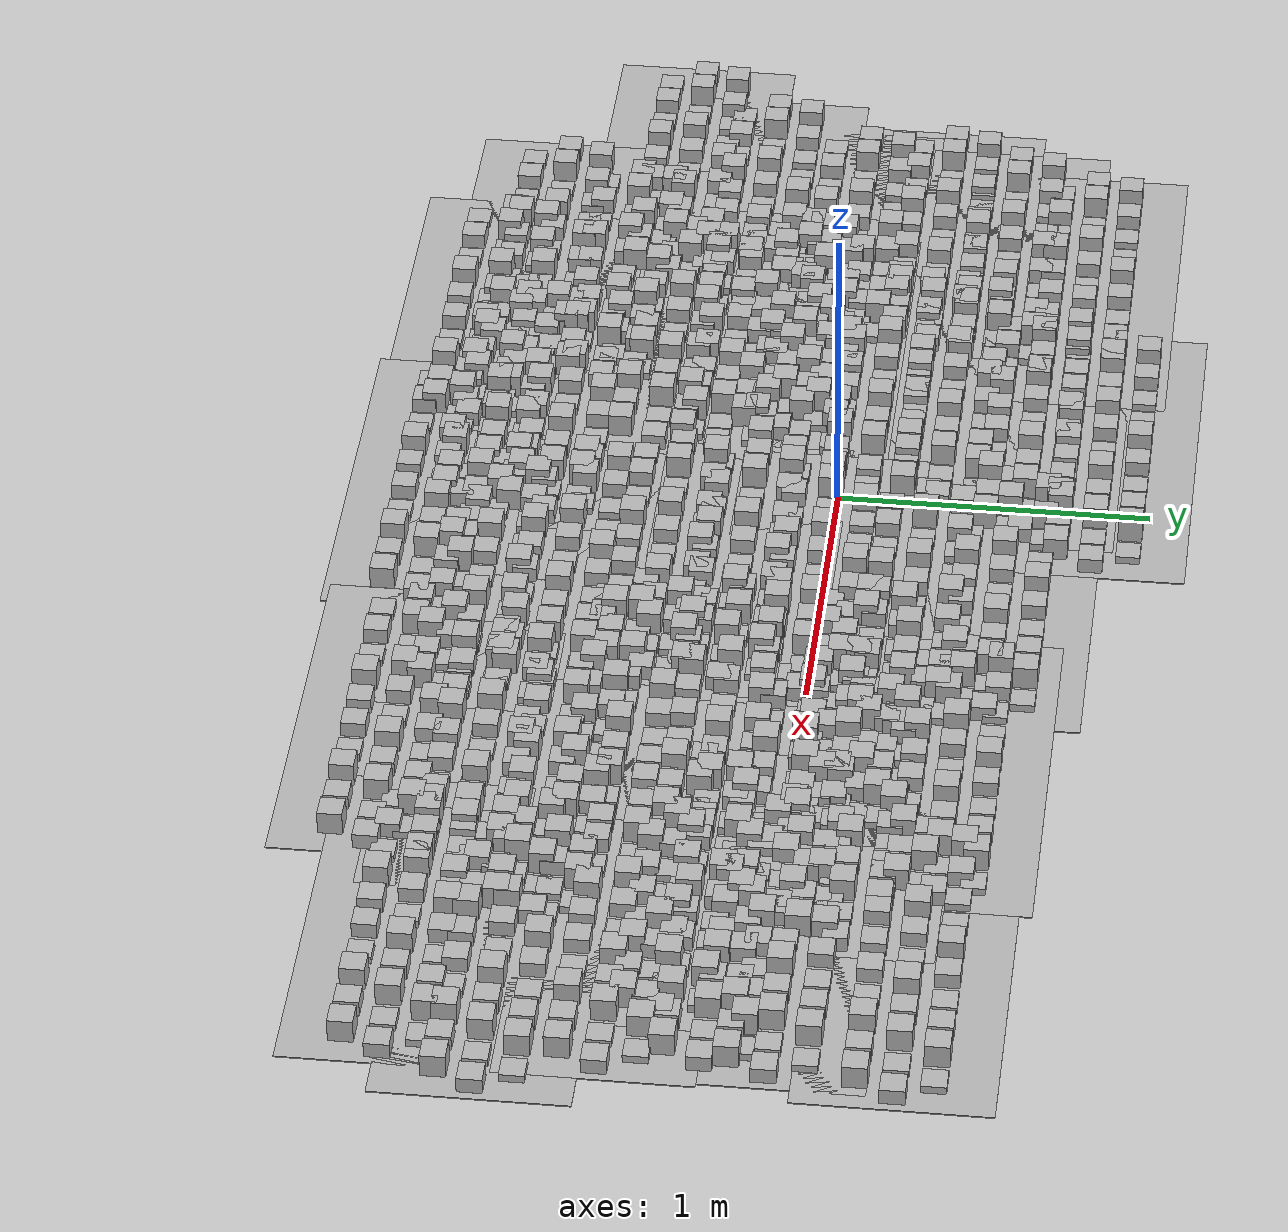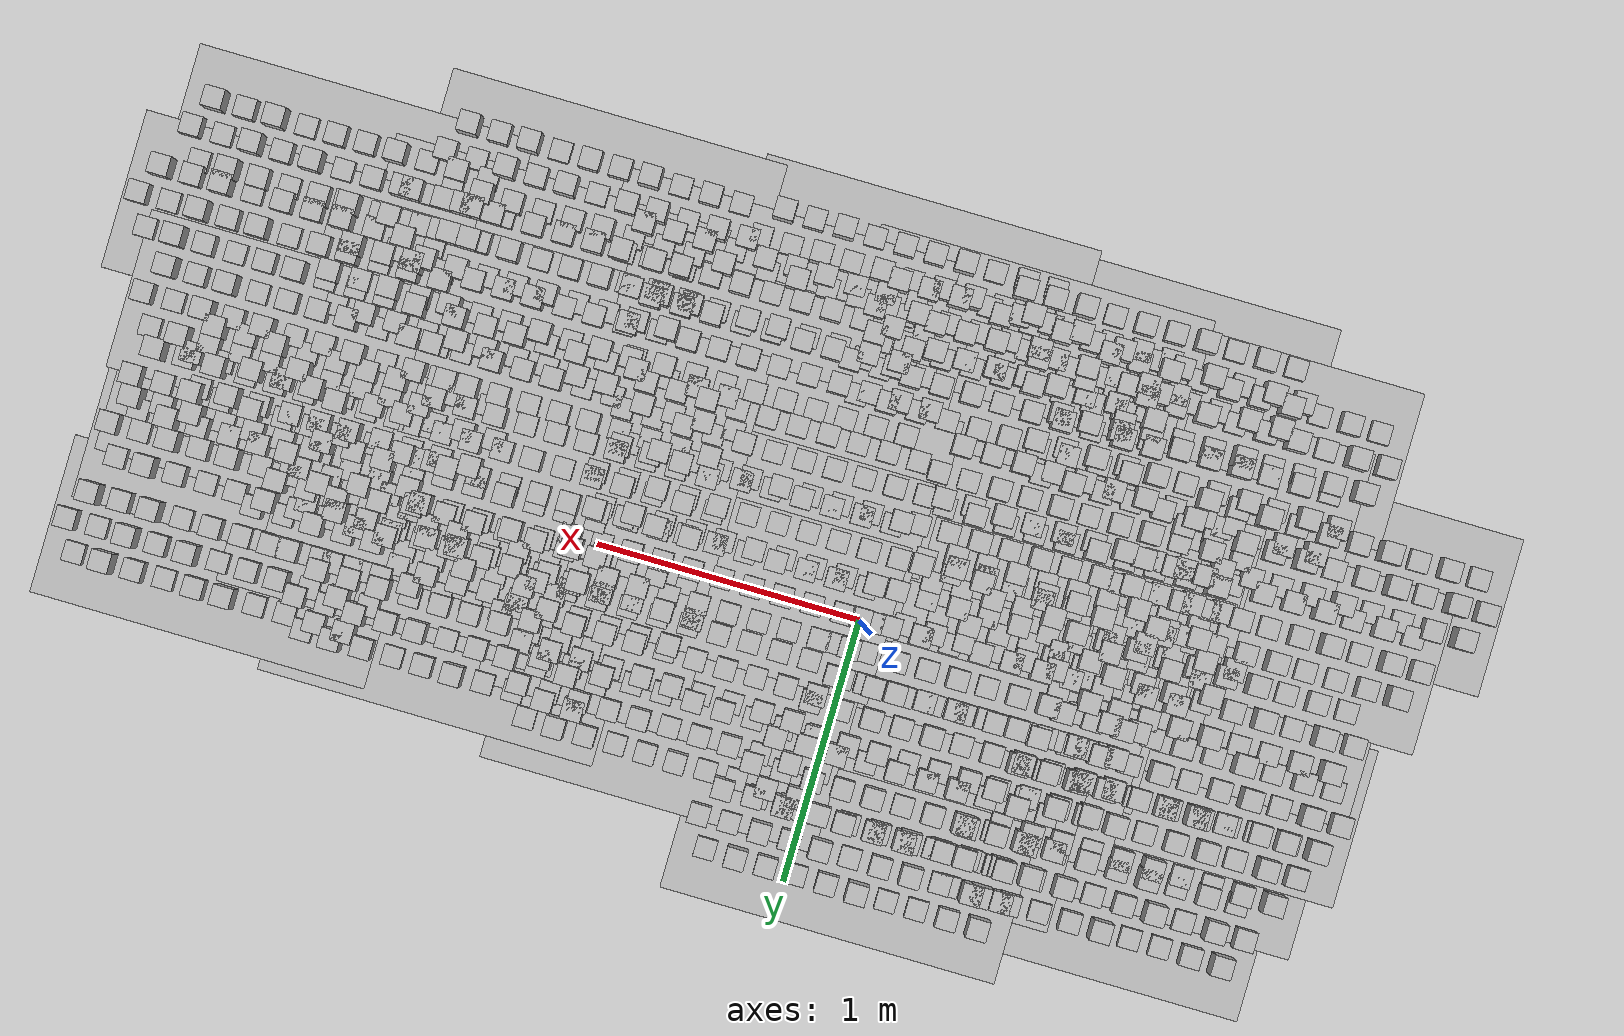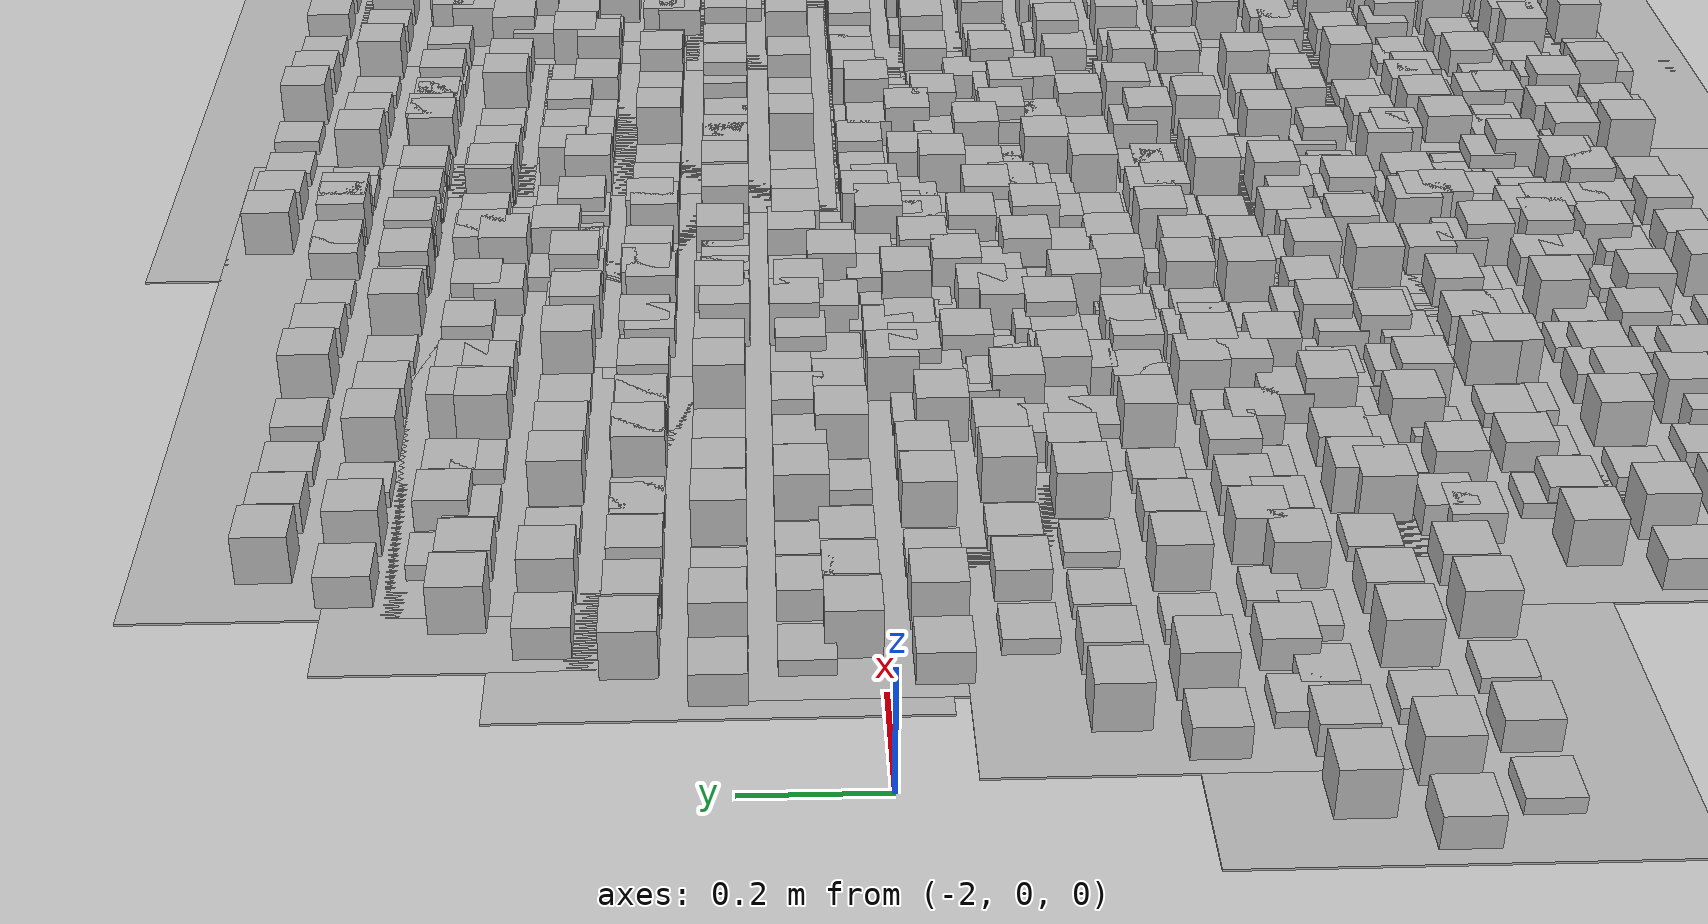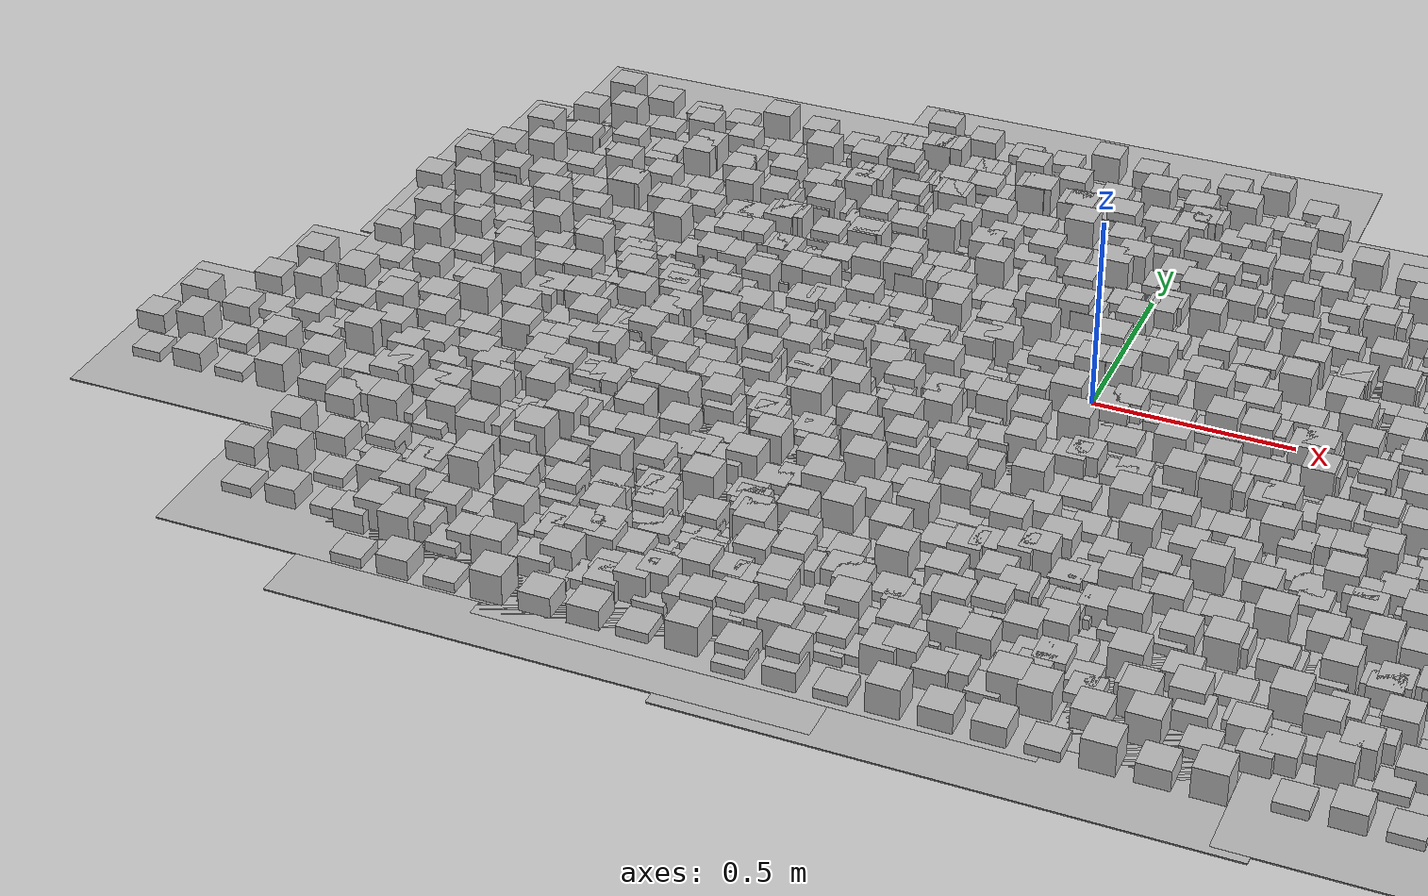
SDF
<sdf version="1.6">
 <world name="default">
  <light name="sun" type="directional">
   <pose>0 0 10 0 -0 0</pose>
   <diffuse>0.8 0.8 0.8 1</diffuse>
   <specular>0.1 0.1 0.1 1</specular>
   <attenuation>
    <range>1000</range>
    <constant>0.9</constant>
    <linear>0.01</linear>
    <quadratic>0.001</quadratic>
   </attenuation>
   <direction>-0.5 0.5 -1</direction>
  </light>
  <model name="ground_plane">
   <static>1</static>
   <link name="link">
    <collision name="collision">
     <geometry><plane><normal>0 0 1</normal><size>100 100</size></plane></geometry>
     <surface><friction><ode><mu>100</mu><mu2>50</mu2></ode></friction></surface>
    </collision>
    <visual name="visual">
     <cast_shadows>0</cast_shadows>
     <geometry><plane><normal>0 0 1</normal><size>100 100</size></plane></geometry>
     <material>
      <script><uri>file://media/materials/scripts/gazebo.material</uri><name>Gazebo/Grey</name></script>
     </material>
    </visual>
   </link>
  </model>
  <gravity>0 0 -9.8</gravity>
  <magnetic_field>6e-06 2.3e-05 -4.2e-05</magnetic_field>
  <atmosphere type="adiabatic"/>
  <physics name="default_physics" default="0" type="ode">
   <max_step_size>0.001</max_step_size>
   <real_time_factor>1</real_time_factor>
   <real_time_update_rate>1000</real_time_update_rate>
  </physics>
  <scene><ambient>0.4 0.4 0.4 1</ambient><background>0.7 0.7 0.7 1</background><shadows>1</shadows></scene>
  <spherical_coordinates>
   <surface_model>EARTH_WGS84</surface_model>
   <latitude_deg>0</latitude_deg>
   <longitude_deg>0</longitude_deg>
   <elevation>0</elevation>
   <heading_deg>0</heading_deg>
  </spherical_coordinates>
  <model name="frc2016_roughterrain">
   <static>1</static>
   <link name="link">
    <visual name="platform">
     <pose>0 0 0.08269 0 -0 0</pose>
     <geometry><box><size>1.27 0.5969 0.003175</size></box></geometry>
    </visual>
    <collision name="platform">
     <pose>0 0 0.08269 0 -0 0</pose>
     <geometry><box><size>1.27 0.5969 0.003175</size></box></geometry>
    </collision>
    <visual name="row1_block1_sm">
     <pose>0.51435 0.1143 0.09698 0 -0 0</pose>
     <geometry><box><size>0.0762 0.0762 0.0254</size></box></geometry>
    </visual>
    <collision name="row1_block1_sm">
     <pose>0.51435 0.1143 0.09698 0 -0 0</pose>
     <geometry><box><size>0.0762 0.0762 0.0254</size></box></geometry>
    </collision>
    <visual name="row1_block2_lg">
     <pose>0.40005 0.1143 0.12238 0 -0 0</pose>
     <geometry><box><size>0.0762 0.0762 0.0762</size></box></geometry>
    </visual>
    <collision name="row1_block2_lg">
     <pose>0.40005 0.1143 0.12238 0 -0 0</pose>
     <geometry><box><size>0.0762 0.0762 0.0762</size></box></geometry>
    </collision>
    <visual name="row1_block3_md">
     <pose>0.28575 0.1143 0.10968 0 -0 0</pose>
     <geometry><box><size>0.0762 0.0762 0.0508</size></box></geometry>
    </visual>
    <collision name="row1_block3_md">
     <pose>0.28575 0.1143 0.10968 0 -0 0</pose>
     <geometry><box><size>0.0762 0.0762 0.0508</size></box></geometry>
    </collision>
    <visual name="row1_block4_sm">
     <pose>0.17145 0.1143 0.09698 0 -0 0</pose>
     <geometry><box><size>0.0762 0.0762 0.0254</size></box></geometry>
    </visual>
    <collision name="row1_block4_sm">
     <pose>0.17145 0.1143 0.09698 0 -0 0</pose>
     <geometry><box><size>0.0762 0.0762 0.0254</size></box></geometry>
    </collision>
    <visual name="row1_block5_md">
     <pose>0.05715 0.1143 0.10968 0 -0 0</pose>
     <geometry><box><size>0.0762 0.0762 0.0508</size></box></geometry>
    </visual>
    <collision name="row1_block5_md">
     <pose>0.05715 0.1143 0.10968 0 -0 0</pose>
     <geometry><box><size>0.0762 0.0762 0.0508</size></box></geometry>
    </collision>
    <visual name="row1_block6_lg">
     <pose>-0.05715 0.1143 0.12238 0 -0 0</pose>
     <geometry><box><size>0.0762 0.0762 0.0762</size></box></geometry>
    </visual>
    <collision name="row1_block6_lg">
     <pose>-0.05715 0.1143 0.12238 0 -0 0</pose>
     <geometry><box><size>0.0762 0.0762 0.0762</size></box></geometry>
    </collision>
    <visual name="row1_block7_sm">
     <pose>-0.17145 0.1143 0.09698 0 -0 0</pose>
     <geometry><box><size>0.0762 0.0762 0.0254</size></box></geometry>
    </visual>
    <collision name="row1_block7_sm">
     <pose>-0.17145 0.1143 0.09698 0 -0 0</pose>
     <geometry><box><size>0.0762 0.0762 0.0254</size></box></geometry>
    </collision>
    <visual name="row1_block8_sm">
     <pose>-0.28575 0.1143 0.09698 0 -0 0</pose>
     <geometry><box><size>0.0762 0.0762 0.0254</size></box></geometry>
    </visual>
    <collision name="row1_block8_sm">
     <pose>-0.28575 0.1143 0.09698 0 -0 0</pose>
     <geometry><box><size>0.0762 0.0762 0.0254</size></box></geometry>
    </collision>
    <visual name="row1_block9_md">
     <pose>-0.40005 0.1143 0.10968 0 -0 0</pose>
     <geometry><box><size>0.0762 0.0762 0.0508</size></box></geometry>
    </visual>
    <collision name="row1_block9_md">
     <pose>-0.40005 0.1143 0.10968 0 -0 0</pose>
     <geometry><box><size>0.0762 0.0762 0.0508</size></box></geometry>
    </collision>
    <visual name="row1_block10_lg">
     <pose>-0.51435 0.1143 0.12238 0 -0 0</pose>
     <geometry><box><size>0.0762 0.0762 0.0762</size></box></geometry>
    </visual>
    <collision name="row1_block10_lg">
     <pose>-0.51435 0.1143 0.12238 0 -0 0</pose>
     <geometry><box><size>0.0762 0.0762 0.0762</size></box></geometry>
    </collision>
    <visual name="row2_block1_md">
     <pose>0.5715 0 0.10968 0 -0 0</pose>
     <geometry><box><size>0.0762 0.0762 0.0508</size></box></geometry>
    </visual>
    <collision name="row2_block1_md">
     <pose>0.5715 0 0.10968 0 -0 0</pose>
     <geometry><box><size>0.0762 0.0762 0.0508</size></box></geometry>
    </collision>
    <visual name="row2_block2_sm">
     <pose>0.4572 0 0.09698 0 -0 0</pose>
     <geometry><box><size>0.0762 0.0762 0.0254</size></box></geometry>
    </visual>
    <collision name="row2_block2_sm">
     <pose>0.4572 0 0.09698 0 -0 0</pose>
     <geometry><box><size>0.0762 0.0762 0.0254</size></box></geometry>
    </collision>
    <visual name="row2_block3_lg">
     <pose>0.3429 0 0.12238 0 -0 0</pose>
     <geometry><box><size>0.0762 0.0762 0.0762</size></box></geometry>
    </visual>
    <collision name="row2_block3_lg">
     <pose>0.3429 0 0.12238 0 -0 0</pose>
     <geometry><box><size>0.0762 0.0762 0.0762</size></box></geometry>
    </collision>
    <visual name="row2_block4_md">
     <pose>0.2286 0 0.10968 0 -0 0</pose>
     <geometry><box><size>0.0762 0.0762 0.0508</size></box></geometry>
    </visual>
    <collision name="row2_block4_md">
     <pose>0.2286 0 0.10968 0 -0 0</pose>
     <geometry><box><size>0.0762 0.0762 0.0508</size></box></geometry>
    </collision>
    <visual name="row2_block5_lg">
     <pose>0.1143 0 0.12238 0 -0 0</pose>
     <geometry><box><size>0.0762 0.0762 0.0762</size></box></geometry>
    </visual>
    <collision name="row2_block5_lg">
     <pose>0.1143 0 0.12238 0 -0 0</pose>
     <geometry><box><size>0.0762 0.0762 0.0762</size></box></geometry>
    </collision>
    <visual name="row2_block6_sm">
     <pose>0 0 0.09698 0 -0 0</pose>
     <geometry><box><size>0.0762 0.0762 0.0254</size></box></geometry>
    </visual>
    <collision name="row2_block6_sm">
     <pose>0 0 0.09698 0 -0 0</pose>
     <geometry><box><size>0.0762 0.0762 0.0254</size></box></geometry>
    </collision>
    <visual name="row2_block7_md">
     <pose>-0.1143 0 0.10968 0 -0 0</pose>
     <geometry><box><size>0.0762 0.0762 0.0508</size></box></geometry>
    </visual>
    <collision name="row2_block7_md">
     <pose>-0.1143 0 0.10968 0 -0 0</pose>
     <geometry><box><size>0.0762 0.0762 0.0508</size></box></geometry>
    </collision>
    <visual name="row2_block8_lg">
     <pose>-0.2286 0 0.12238 0 -0 0</pose>
     <geometry><box><size>0.0762 0.0762 0.0762</size></box></geometry>
    </visual>
    <collision name="row2_block8_lg">
     <pose>-0.2286 0 0.12238 0 -0 0</pose>
     <geometry><box><size>0.0762 0.0762 0.0762</size></box></geometry>
    </collision>
    <visual name="row2_block9_sm">
     <pose>-0.3429 0 0.09698 0 -0 0</pose>
     <geometry><box><size>0.0762 0.0762 0.0254</size></box></geometry>
    </visual>
    <collision name="row2_block9_sm">
     <pose>-0.3429 0 0.09698 0 -0 0</pose>
     <geometry><box><size>0.0762 0.0762 0.0254</size></box></geometry>
    </collision>
    <visual name="row2_block10_lg">
     <pose>-0.4572 0 0.12238 0 -0 0</pose>
     <geometry><box><size>0.0762 0.0762 0.0762</size></box></geometry>
    </visual>
    <collision name="row2_block10_lg">
     <pose>-0.4572 0 0.12238 0 -0 0</pose>
     <geometry><box><size>0.0762 0.0762 0.0762</size></box></geometry>
    </collision>
    <visual name="row2_block11_md">
     <pose>-0.5715 0 0.10968 0 -0 0</pose>
     <geometry><box><size>0.0762 0.0762 0.0508</size></box></geometry>
    </visual>
    <collision name="row2_block11_md">
     <pose>-0.5715 0 0.10968 0 -0 0</pose>
     <geometry><box><size>0.0762 0.0762 0.0508</size></box></geometry>
    </collision>
    <visual name="row3_block1_lg">
     <pose>0.51435 -0.1143 0.12238 0 -0 0</pose>
     <geometry><box><size>0.0762 0.0762 0.0762</size></box></geometry>
    </visual>
    <collision name="row3_block1_lg">
     <pose>0.51435 -0.1143 0.12238 0 -0 0</pose>
     <geometry><box><size>0.0762 0.0762 0.0762</size></box></geometry>
    </collision>
    <visual name="row3_block2_md">
     <pose>0.40005 -0.1143 0.10968 0 -0 0</pose>
     <geometry><box><size>0.0762 0.0762 0.0508</size></box></geometry>
    </visual>
    <collision name="row3_block2_md">
     <pose>0.40005 -0.1143 0.10968 0 -0 0</pose>
     <geometry><box><size>0.0762 0.0762 0.0508</size></box></geometry>
    </collision>
    <visual name="row3_block3_lg">
     <pose>0.28575 -0.1143 0.12238 0 -0 0</pose>
     <geometry><box><size>0.0762 0.0762 0.0762</size></box></geometry>
    </visual>
    <collision name="row3_block3_lg">
     <pose>0.28575 -0.1143 0.12238 0 -0 0</pose>
     <geometry><box><size>0.0762 0.0762 0.0762</size></box></geometry>
    </collision>
    <visual name="row3_block4_sm">
     <pose>0.17145 -0.1143 0.09698 0 -0 0</pose>
     <geometry><box><size>0.0762 0.0762 0.0254</size></box></geometry>
    </visual>
    <collision name="row3_block4_sm">
     <pose>0.17145 -0.1143 0.09698 0 -0 0</pose>
     <geometry><box><size>0.0762 0.0762 0.0254</size></box></geometry>
    </collision>
    <visual name="row3_block5_md">
     <pose>0.05715 -0.1143 0.10968 0 -0 0</pose>
     <geometry><box><size>0.0762 0.0762 0.0508</size></box></geometry>
    </visual>
    <collision name="row3_block5_md">
     <pose>0.05715 -0.1143 0.10968 0 -0 0</pose>
     <geometry><box><size>0.0762 0.0762 0.0508</size></box></geometry>
    </collision>
    <visual name="row3_block6_md">
     <pose>-0.05715 -0.1143 0.10968 0 -0 0</pose>
     <geometry><box><size>0.0762 0.0762 0.0508</size></box></geometry>
    </visual>
    <collision name="row3_block6_md">
     <pose>-0.05715 -0.1143 0.10968 0 -0 0</pose>
     <geometry><box><size>0.0762 0.0762 0.0508</size></box></geometry>
    </collision>
    <visual name="row3_block7_lg">
     <pose>-0.17145 -0.1143 0.12238 0 -0 0</pose>
     <geometry><box><size>0.0762 0.0762 0.0762</size></box></geometry>
    </visual>
    <collision name="row3_block7_lg">
     <pose>-0.17145 -0.1143 0.12238 0 -0 0</pose>
     <geometry><box><size>0.0762 0.0762 0.0762</size></box></geometry>
    </collision>
    <visual name="row3_block8_sm">
     <pose>-0.28575 -0.1143 0.09698 0 -0 0</pose>
     <geometry><box><size>0.0762 0.0762 0.0254</size></box></geometry>
    </visual>
    <collision name="row3_block8_sm">
     <pose>-0.28575 -0.1143 0.09698 0 -0 0</pose>
     <geometry><box><size>0.0762 0.0762 0.0254</size></box></geometry>
    </collision>
    <visual name="row3_block9_md">
     <pose>-0.40005 -0.1143 0.10968 0 -0 0</pose>
     <geometry><box><size>0.0762 0.0762 0.0508</size></box></geometry>
    </visual>
    <collision name="row3_block9_md">
     <pose>-0.40005 -0.1143 0.10968 0 -0 0</pose>
     <geometry><box><size>0.0762 0.0762 0.0508</size></box></geometry>
    </collision>
    <visual name="row3_block10_sm">
     <pose>-0.51435 -0.1143 0.09698 0 -0 0</pose>
     <geometry><box><size>0.0762 0.0762 0.0254</size></box></geometry>
    </visual>
    <collision name="row3_block10_sm">
     <pose>-0.51435 -0.1143 0.09698 0 -0 0</pose>
     <geometry><box><size>0.0762 0.0762 0.0254</size></box></geometry>
    </collision>
   </link>
   <pose>1.19389 -0.23686 0 0 -0 0</pose>
  </model>
  <model name="frc2016_roughterrain_0">
   <static>1</static>
   <link name="link">
    <visual name="platform">
     <pose>0 0 0.08269 0 -0 0</pose>
     <geometry><box><size>1.27 0.5969 0.003175</size></box></geometry>
    </visual>
    <collision name="platform">
     <pose>0 0 0.08269 0 -0 0</pose>
     <geometry><box><size>1.27 0.5969 0.003175</size></box></geometry>
    </collision>
    <visual name="row1_block1_sm">
     <pose>0.51435 0.1143 0.09698 0 -0 0</pose>
     <geometry><box><size>0.0762 0.0762 0.0254</size></box></geometry>
    </visual>
    <collision name="row1_block1_sm">
     <pose>0.51435 0.1143 0.09698 0 -0 0</pose>
     <geometry><box><size>0.0762 0.0762 0.0254</size></box></geometry>
    </collision>
    <visual name="row1_block2_lg">
     <pose>0.40005 0.1143 0.12238 0 -0 0</pose>
     <geometry><box><size>0.0762 0.0762 0.0762</size></box></geometry>
    </visual>
    <collision name="row1_block2_lg">
     <pose>0.40005 0.1143 0.12238 0 -0 0</pose>
     <geometry><box><size>0.0762 0.0762 0.0762</size></box></geometry>
    </collision>
    <visual name="row1_block3_md">
     <pose>0.28575 0.1143 0.10968 0 -0 0</pose>
     <geometry><box><size>0.0762 0.0762 0.0508</size></box></geometry>
    </visual>
    <collision name="row1_block3_md">
     <pose>0.28575 0.1143 0.10968 0 -0 0</pose>
     <geometry><box><size>0.0762 0.0762 0.0508</size></box></geometry>
    </collision>
    <visual name="row1_block4_sm">
     <pose>0.17145 0.1143 0.09698 0 -0 0</pose>
     <geometry><box><size>0.0762 0.0762 0.0254</size></box></geometry>
    </visual>
    <collision name="row1_block4_sm">
     <pose>0.17145 0.1143 0.09698 0 -0 0</pose>
     <geometry><box><size>0.0762 0.0762 0.0254</size></box></geometry>
    </collision>
    <visual name="row1_block5_md">
     <pose>0.05715 0.1143 0.10968 0 -0 0</pose>
     <geometry><box><size>0.0762 0.0762 0.0508</size></box></geometry>
    </visual>
    <collision name="row1_block5_md">
     <pose>0.05715 0.1143 0.10968 0 -0 0</pose>
     <geometry><box><size>0.0762 0.0762 0.0508</size></box></geometry>
    </collision>
    <visual name="row1_block6_lg">
     <pose>-0.05715 0.1143 0.12238 0 -0 0</pose>
     <geometry><box><size>0.0762 0.0762 0.0762</size></box></geometry>
    </visual>
    <collision name="row1_block6_lg">
     <pose>-0.05715 0.1143 0.12238 0 -0 0</pose>
     <geometry><box><size>0.0762 0.0762 0.0762</size></box></geometry>
    </collision>
    <visual name="row1_block7_sm">
     <pose>-0.17145 0.1143 0.09698 0 -0 0</pose>
     <geometry><box><size>0.0762 0.0762 0.0254</size></box></geometry>
    </visual>
    <collision name="row1_block7_sm">
     <pose>-0.17145 0.1143 0.09698 0 -0 0</pose>
     <geometry><box><size>0.0762 0.0762 0.0254</size></box></geometry>
    </collision>
    <visual name="row1_block8_sm">
     <pose>-0.28575 0.1143 0.09698 0 -0 0</pose>
     <geometry><box><size>0.0762 0.0762 0.0254</size></box></geometry>
    </visual>
    <collision name="row1_block8_sm">
     <pose>-0.28575 0.1143 0.09698 0 -0 0</pose>
     <geometry><box><size>0.0762 0.0762 0.0254</size></box></geometry>
    </collision>
    <visual name="row1_block9_md">
     <pose>-0.40005 0.1143 0.10968 0 -0 0</pose>
     <geometry><box><size>0.0762 0.0762 0.0508</size></box></geometry>
    </visual>
    <collision name="row1_block9_md">
     <pose>-0.40005 0.1143 0.10968 0 -0 0</pose>
     <geometry><box><size>0.0762 0.0762 0.0508</size></box></geometry>
    </collision>
    <visual name="row1_block10_lg">
     <pose>-0.51435 0.1143 0.12238 0 -0 0</pose>
     <geometry><box><size>0.0762 0.0762 0.0762</size></box></geometry>
    </visual>
    <collision name="row1_block10_lg">
     <pose>-0.51435 0.1143 0.12238 0 -0 0</pose>
     <geometry><box><size>0.0762 0.0762 0.0762</size></box></geometry>
    </collision>
    <visual name="row2_block1_md">
     <pose>0.5715 0 0.10968 0 -0 0</pose>
     <geometry><box><size>0.0762 0.0762 0.0508</size></box></geometry>
    </visual>
    <collision name="row2_block1_md">
     <pose>0.5715 0 0.10968 0 -0 0</pose>
     <geometry><box><size>0.0762 0.0762 0.0508</size></box></geometry>
    </collision>
    <visual name="row2_block2_sm">
     <pose>0.4572 0 0.09698 0 -0 0</pose>
     <geometry><box><size>0.0762 0.0762 0.0254</size></box></geometry>
    </visual>
    <collision name="row2_block2_sm">
     <pose>0.4572 0 0.09698 0 -0 0</pose>
     <geometry><box><size>0.0762 0.0762 0.0254</size></box></geometry>
    </collision>
    <visual name="row2_block3_lg">
     <pose>0.3429 0 0.12238 0 -0 0</pose>
     <geometry><box><size>0.0762 0.0762 0.0762</size></box></geometry>
    </visual>
    <collision name="row2_block3_lg">
     <pose>0.3429 0 0.12238 0 -0 0</pose>
     <geometry><box><size>0.0762 0.0762 0.0762</size></box></geometry>
    </collision>
    <visual name="row2_block4_md">
     <pose>0.2286 0 0.10968 0 -0 0</pose>
     <geometry><box><size>0.0762 0.0762 0.0508</size></box></geometry>
    </visual>
    <collision name="row2_block4_md">
     <pose>0.2286 0 0.10968 0 -0 0</pose>
     <geometry><box><size>0.0762 0.0762 0.0508</size></box></geometry>
    </collision>
    <visual name="row2_block5_lg">
     <pose>0.1143 0 0.12238 0 -0 0</pose>
     <geometry><box><size>0.0762 0.0762 0.0762</size></box></geometry>
    </visual>
    <collision name="row2_block5_lg">
     <pose>0.1143 0 0.12238 0 -0 0</pose>
     <geometry><box><size>0.0762 0.0762 0.0762</size></box></geometry>
    </collision>
    <visual name="row2_block6_sm">
     <pose>0 0 0.09698 0 -0 0</pose>
     <geometry><box><size>0.0762 0.0762 0.0254</size></box></geometry>
    </visual>
    <collision name="row2_block6_sm">
     <pose>0 0 0.09698 0 -0 0</pose>
     <geometry><box><size>0.0762 0.0762 0.0254</size></box></geometry>
    </collision>
    <visual name="row2_block7_md">
     <pose>-0.1143 0 0.10968 0 -0 0</pose>
     <geometry><box><size>0.0762 0.0762 0.0508</size></box></geometry>
    </visual>
    <collision name="row2_block7_md">
     <pose>-0.1143 0 0.10968 0 -0 0</pose>
     <geometry><box><size>0.0762 0.0762 0.0508</size></box></geometry>
    </collision>
    <visual name="row2_block8_lg">
     <pose>-0.2286 0 0.12238 0 -0 0</pose>
     <geometry><box><size>0.0762 0.0762 0.0762</size></box></geometry>
    </visual>
    <collision name="row2_block8_lg">
     <pose>-0.2286 0 0.12238 0 -0 0</pose>
     <geometry><box><size>0.0762 0.0762 0.0762</size></box></geometry>
    </collision>
    <visual name="row2_block9_sm">
     <pose>-0.3429 0 0.09698 0 -0 0</pose>
     <geometry><box><size>0.0762 0.0762 0.0254</size></box></geometry>
    </visual>
    <collision name="row2_block9_sm">
     <pose>-0.3429 0 0.09698 0 -0 0</pose>
     <geometry><box><size>0.0762 0.0762 0.0254</size></box></geometry>
    </collision>
    <visual name="row2_block10_lg">
     <pose>-0.4572 0 0.12238 0 -0 0</pose>
     <geometry><box><size>0.0762 0.0762 0.0762</size></box></geometry>
    </visual>
    <collision name="row2_block10_lg">
     <pose>-0.4572 0 0.12238 0 -0 0</pose>
     <geometry><box><size>0.0762 0.0762 0.0762</size></box></geometry>
    </collision>
    <visual name="row2_block11_md">
     <pose>-0.5715 0 0.10968 0 -0 0</pose>
     <geometry><box><size>0.0762 0.0762 0.0508</size></box></geometry>
    </visual>
    <collision name="row2_block11_md">
     <pose>-0.5715 0 0.10968 0 -0 0</pose>
     <geometry><box><size>0.0762 0.0762 0.0508</size></box></geometry>
    </collision>
    <visual name="row3_block1_lg">
     <pose>0.51435 -0.1143 0.12238 0 -0 0</pose>
     <geometry><box><size>0.0762 0.0762 0.0762</size></box></geometry>
    </visual>
    <collision name="row3_block1_lg">
     <pose>0.51435 -0.1143 0.12238 0 -0 0</pose>
     <geometry><box><size>0.0762 0.0762 0.0762</size></box></geometry>
    </collision>
    <visual name="row3_block2_md">
     <pose>0.40005 -0.1143 0.10968 0 -0 0</pose>
     <geometry><box><size>0.0762 0.0762 0.0508</size></box></geometry>
    </visual>
    <collision name="row3_block2_md">
     <pose>0.40005 -0.1143 0.10968 0 -0 0</pose>
     <geometry><box><size>0.0762 0.0762 0.0508</size></box></geometry>
    </collision>
    <visual name="row3_block3_lg">
     <pose>0.28575 -0.1143 0.12238 0 -0 0</pose>
     <geometry><box><size>0.0762 0.0762 0.0762</size></box></geometry>
    </visual>
    <collision name="row3_block3_lg">
     <pose>0.28575 -0.1143 0.12238 0 -0 0</pose>
     <geometry><box><size>0.0762 0.0762 0.0762</size></box></geometry>
    </collision>
    <visual name="row3_block4_sm">
     <pose>0.17145 -0.1143 0.09698 0 -0 0</pose>
     <geometry><box><size>0.0762 0.0762 0.0254</size></box></geometry>
    </visual>
    <collision name="row3_block4_sm">
     <pose>0.17145 -0.1143 0.09698 0 -0 0</pose>
     <geometry><box><size>0.0762 0.0762 0.0254</size></box></geometry>
    </collision>
    <visual name="row3_block5_md">
     <pose>0.05715 -0.1143 0.10968 0 -0 0</pose>
     <geometry><box><size>0.0762 0.0762 0.0508</size></box></geometry>
    </visual>
    <collision name="row3_block5_md">
     <pose>0.05715 -0.1143 0.10968 0 -0 0</pose>
     <geometry><box><size>0.0762 0.0762 0.0508</size></box></geometry>
    </collision>
    <visual name="row3_block6_md">
     <pose>-0.05715 -0.1143 0.10968 0 -0 0</pose>
     <geometry><box><size>0.0762 0.0762 0.0508</size></box></geometry>
    </visual>
    <collision name="row3_block6_md">
     <pose>-0.05715 -0.1143 0.10968 0 -0 0</pose>
     <geometry><box><size>0.0762 0.0762 0.0508</size></box></geometry>
    </collision>
    <visual name="row3_block7_lg">
     <pose>-0.17145 -0.1143 0.12238 0 -0 0</pose>
     <geometry><box><size>0.0762 0.0762 0.0762</size></box></geometry>
    </visual>
    <collision name="row3_block7_lg">
     <pose>-0.17145 -0.1143 0.12238 0 -0 0</pose>
     <geometry><box><size>0.0762 0.0762 0.0762</size></box></geometry>
    </collision>
    <visual name="row3_block8_sm">
     <pose>-0.28575 -0.1143 0.09698 0 -0 0</pose>
     <geometry><box><size>0.0762 0.0762 0.0254</size></box></geometry>
    </visual>
    <collision name="row3_block8_sm">
     <pose>-0.28575 -0.1143 0.09698 0 -0 0</pose>
     <geometry><box><size>0.0762 0.0762 0.0254</size></box></geometry>
    </collision>
    <visual name="row3_block9_md">
     <pose>-0.40005 -0.1143 0.10968 0 -0 0</pose>
     <geometry><box><size>0.0762 0.0762 0.0508</size></box></geometry>
    </visual>
    <collision name="row3_block9_md">
     <pose>-0.40005 -0.1143 0.10968 0 -0 0</pose>
     <geometry><box><size>0.0762 0.0762 0.0508</size></box></geometry>
    </collision>
    <visual name="row3_block10_sm">
     <pose>-0.51435 -0.1143 0.09698 0 -0 0</pose>
     <geometry><box><size>0.0762 0.0762 0.0254</size></box></geometry>
    </visual>
    <collision name="row3_block10_sm">
     <pose>-0.51435 -0.1143 0.09698 0 -0 0</pose>
     <geometry><box><size>0.0762 0.0762 0.0254</size></box></geometry>
    </collision>
   </link>
   <pose>1.5389 0.029799 0 0 -0 0</pose>
  </model>
  <model name="frc2016_roughterrain_1">
   <static>1</static>
   <link name="link">
    <visual name="platform">
     <pose>0 0 0.08269 0 -0 0</pose>
     <geometry><box><size>1.27 0.5969 0.003175</size></box></geometry>
    </visual>
    <collision name="platform">
     <pose>0 0 0.08269 0 -0 0</pose>
     <geometry><box><size>1.27 0.5969 0.003175</size></box></geometry>
    </collision>
    <visual name="row1_block1_sm">
     <pose>0.51435 0.1143 0.09698 0 -0 0</pose>
     <geometry><box><size>0.0762 0.0762 0.0254</size></box></geometry>
    </visual>
    <collision name="row1_block1_sm">
     <pose>0.51435 0.1143 0.09698 0 -0 0</pose>
     <geometry><box><size>0.0762 0.0762 0.0254</size></box></geometry>
    </collision>
    <visual name="row1_block2_lg">
     <pose>0.40005 0.1143 0.12238 0 -0 0</pose>
     <geometry><box><size>0.0762 0.0762 0.0762</size></box></geometry>
    </visual>
    <collision name="row1_block2_lg">
     <pose>0.40005 0.1143 0.12238 0 -0 0</pose>
     <geometry><box><size>0.0762 0.0762 0.0762</size></box></geometry>
    </collision>
    <visual name="row1_block3_md">
     <pose>0.28575 0.1143 0.10968 0 -0 0</pose>
     <geometry><box><size>0.0762 0.0762 0.0508</size></box></geometry>
    </visual>
    <collision name="row1_block3_md">
     <pose>0.28575 0.1143 0.10968 0 -0 0</pose>
     <geometry><box><size>0.0762 0.0762 0.0508</size></box></geometry>
    </collision>
    <visual name="row1_block4_sm">
     <pose>0.17145 0.1143 0.09698 0 -0 0</pose>
     <geometry><box><size>0.0762 0.0762 0.0254</size></box></geometry>
    </visual>
    <collision name="row1_block4_sm">
     <pose>0.17145 0.1143 0.09698 0 -0 0</pose>
     <geometry><box><size>0.0762 0.0762 0.0254</size></box></geometry>
    </collision>
    <visual name="row1_block5_md">
     <pose>0.05715 0.1143 0.10968 0 -0 0</pose>
     <geometry><box><size>0.0762 0.0762 0.0508</size></box></geometry>
    </visual>
    <collision name="row1_block5_md">
     <pose>0.05715 0.1143 0.10968 0 -0 0</pose>
     <geometry><box><size>0.0762 0.0762 0.0508</size></box></geometry>
    </collision>
    <visual name="row1_block6_lg">
     <pose>-0.05715 0.1143 0.12238 0 -0 0</pose>
     <geometry><box><size>0.0762 0.0762 0.0762</size></box></geometry>
    </visual>
    <collision name="row1_block6_lg">
     <pose>-0.05715 0.1143 0.12238 0 -0 0</pose>
     <geometry><box><size>0.0762 0.0762 0.0762</size></box></geometry>
    </collision>
    <visual name="row1_block7_sm">
     <pose>-0.17145 0.1143 0.09698 0 -0 0</pose>
     <geometry><box><size>0.0762 0.0762 0.0254</size></box></geometry>
    </visual>
    <collision name="row1_block7_sm">
     <pose>-0.17145 0.1143 0.09698 0 -0 0</pose>
     <geometry><box><size>0.0762 0.0762 0.0254</size></box></geometry>
    </collision>
    <visual name="row1_block8_sm">
     <pose>-0.28575 0.1143 0.09698 0 -0 0</pose>
     <geometry><box><size>0.0762 0.0762 0.0254</size></box></geometry>
    </visual>
    <collision name="row1_block8_sm">
     <pose>-0.28575 0.1143 0.09698 0 -0 0</pose>
     <geometry><box><size>0.0762 0.0762 0.0254</size></box></geometry>
    </collision>
    <visual name="row1_block9_md">
     <pose>-0.40005 0.1143 0.10968 0 -0 0</pose>
     <geometry><box><size>0.0762 0.0762 0.0508</size></box></geometry>
    </visual>
    <collision name="row1_block9_md">
     <pose>-0.40005 0.1143 0.10968 0 -0 0</pose>
     <geometry><box><size>0.0762 0.0762 0.0508</size></box></geometry>
    </collision>
    <visual name="row1_block10_lg">
     <pose>-0.51435 0.1143 0.12238 0 -0 0</pose>
     <geometry><box><size>0.0762 0.0762 0.0762</size></box></geometry>
    </visual>
    <collision name="row1_block10_lg">
     <pose>-0.51435 0.1143 0.12238 0 -0 0</pose>
     <geometry><box><size>0.0762 0.0762 0.0762</size></box></geometry>
    </collision>
    <visual name="row2_block1_md">
     <pose>0.5715 0 0.10968 0 -0 0</pose>
     <geometry><box><size>0.0762 0.0762 0.0508</size></box></geometry>
    </visual>
    <collision name="row2_block1_md">
     <pose>0.5715 0 0.10968 0 -0 0</pose>
     <geometry><box><size>0.0762 0.0762 0.0508</size></box></geometry>
    </collision>
    <visual name="row2_block2_sm">
     <pose>0.4572 0 0.09698 0 -0 0</pose>
     <geometry><box><size>0.0762 0.0762 0.0254</size></box></geometry>
    </visual>
    <collision name="row2_block2_sm">
     <pose>0.4572 0 0.09698 0 -0 0</pose>
     <geometry><box><size>0.0762 0.0762 0.0254</size></box></geometry>
    </collision>
    <visual name="row2_block3_lg">
     <pose>0.3429 0 0.12238 0 -0 0</pose>
     <geometry><box><size>0.0762 0.0762 0.0762</size></box></geometry>
    </visual>
    <collision name="row2_block3_lg">
     <pose>0.3429 0 0.12238 0 -0 0</pose>
     <geometry><box><size>0.0762 0.0762 0.0762</size></box></geometry>
    </collision>
    <visual name="row2_block4_md">
     <pose>0.2286 0 0.10968 0 -0 0</pose>
     <geometry><box><size>0.0762 0.0762 0.0508</size></box></geometry>
    </visual>
    <collision name="row2_block4_md">
     <pose>0.2286 0 0.10968 0 -0 0</pose>
     <geometry><box><size>0.0762 0.0762 0.0508</size></box></geometry>
    </collision>
    <visual name="row2_block5_lg">
     <pose>0.1143 0 0.12238 0 -0 0</pose>
     <geometry><box><size>0.0762 0.0762 0.0762</size></box></geometry>
    </visual>
    <collision name="row2_block5_lg">
     <pose>0.1143 0 0.12238 0 -0 0</pose>
     <geometry><box><size>0.0762 0.0762 0.0762</size></box></geometry>
    </collision>
    <visual name="row2_block6_sm">
     <pose>0 0 0.09698 0 -0 0</pose>
     <geometry><box><size>0.0762 0.0762 0.0254</size></box></geometry>
    </visual>
    <collision name="row2_block6_sm">
     <pose>0 0 0.09698 0 -0 0</pose>
     <geometry><box><size>0.0762 0.0762 0.0254</size></box></geometry>
    </collision>
    <visual name="row2_block7_md">
     <pose>-0.1143 0 0.10968 0 -0 0</pose>
     <geometry><box><size>0.0762 0.0762 0.0508</size></box></geometry>
    </visual>
    <collision name="row2_block7_md">
     <pose>-0.1143 0 0.10968 0 -0 0</pose>
     <geometry><box><size>0.0762 0.0762 0.0508</size></box></geometry>
    </collision>
    <visual name="row2_block8_lg">
     <pose>-0.2286 0 0.12238 0 -0 0</pose>
     <geometry><box><size>0.0762 0.0762 0.0762</size></box></geometry>
    </visual>
    <collision name="row2_block8_lg">
     <pose>-0.2286 0 0.12238 0 -0 0</pose>
     <geometry><box><size>0.0762 0.0762 0.0762</size></box></geometry>
    </collision>
    <visual name="row2_block9_sm">
     <pose>-0.3429 0 0.09698 0 -0 0</pose>
     <geometry><box><size>0.0762 0.0762 0.0254</size></box></geometry>
    </visual>
    <collision name="row2_block9_sm">
     <pose>-0.3429 0 0.09698 0 -0 0</pose>
     <geometry><box><size>0.0762 0.0762 0.0254</size></box></geometry>
    </collision>
    <visual name="row2_block10_lg">
     <pose>-0.4572 0 0.12238 0 -0 0</pose>
     <geometry><box><size>0.0762 0.0762 0.0762</size></box></geometry>
    </visual>
    <collision name="row2_block10_lg">
     <pose>-0.4572 0 0.12238 0 -0 0</pose>
     <geometry><box><size>0.0762 0.0762 0.0762</size></box></geometry>
    </collision>
    <visual name="row2_block11_md">
     <pose>-0.5715 0 0.10968 0 -0 0</pose>
     <geometry><box><size>0.0762 0.0762 0.0508</size></box></geometry>
    </visual>
    <collision name="row2_block11_md">
     <pose>-0.5715 0 0.10968 0 -0 0</pose>
     <geometry><box><size>0.0762 0.0762 0.0508</size></box></geometry>
    </collision>
    <visual name="row3_block1_lg">
     <pose>0.51435 -0.1143 0.12238 0 -0 0</pose>
     <geometry><box><size>0.0762 0.0762 0.0762</size></box></geometry>
    </visual>
    <collision name="row3_block1_lg">
     <pose>0.51435 -0.1143 0.12238 0 -0 0</pose>
     <geometry><box><size>0.0762 0.0762 0.0762</size></box></geometry>
    </collision>
    <visual name="row3_block2_md">
     <pose>0.40005 -0.1143 0.10968 0 -0 0</pose>
     <geometry><box><size>0.0762 0.0762 0.0508</size></box></geometry>
    </visual>
    <collision name="row3_block2_md">
     <pose>0.40005 -0.1143 0.10968 0 -0 0</pose>
     <geometry><box><size>0.0762 0.0762 0.0508</size></box></geometry>
    </collision>
    <visual name="row3_block3_lg">
     <pose>0.28575 -0.1143 0.12238 0 -0 0</pose>
     <geometry><box><size>0.0762 0.0762 0.0762</size></box></geometry>
    </visual>
    <collision name="row3_block3_lg">
     <pose>0.28575 -0.1143 0.12238 0 -0 0</pose>
     <geometry><box><size>0.0762 0.0762 0.0762</size></box></geometry>
    </collision>
    <visual name="row3_block4_sm">
     <pose>0.17145 -0.1143 0.09698 0 -0 0</pose>
     <geometry><box><size>0.0762 0.0762 0.0254</size></box></geometry>
    </visual>
    <collision name="row3_block4_sm">
     <pose>0.17145 -0.1143 0.09698 0 -0 0</pose>
     <geometry><box><size>0.0762 0.0762 0.0254</size></box></geometry>
    </collision>
    <visual name="row3_block5_md">
     <pose>0.05715 -0.1143 0.10968 0 -0 0</pose>
     <geometry><box><size>0.0762 0.0762 0.0508</size></box></geometry>
    </visual>
    <collision name="row3_block5_md">
     <pose>0.05715 -0.1143 0.10968 0 -0 0</pose>
     <geometry><box><size>0.0762 0.0762 0.0508</size></box></geometry>
    </collision>
    <visual name="row3_block6_md">
     <pose>-0.05715 -0.1143 0.10968 0 -0 0</pose>
     <geometry><box><size>0.0762 0.0762 0.0508</size></box></geometry>
    </visual>
    <collision name="row3_block6_md">
     <pose>-0.05715 -0.1143 0.10968 0 -0 0</pose>
     <geometry><box><size>0.0762 0.0762 0.0508</size></box></geometry>
    </collision>
    <visual name="row3_block7_lg">
     <pose>-0.17145 -0.1143 0.12238 0 -0 0</pose>
     <geometry><box><size>0.0762 0.0762 0.0762</size></box></geometry>
    </visual>
    <collision name="row3_block7_lg">
     <pose>-0.17145 -0.1143 0.12238 0 -0 0</pose>
     <geometry><box><size>0.0762 0.0762 0.0762</size></box></geometry>
    </collision>
    <visual name="row3_block8_sm">
     <pose>-0.28575 -0.1143 0.09698 0 -0 0</pose>
     <geometry><box><size>0.0762 0.0762 0.0254</size></box></geometry>
    </visual>
    <collision name="row3_block8_sm">
     <pose>-0.28575 -0.1143 0.09698 0 -0 0</pose>
     <geometry><box><size>0.0762 0.0762 0.0254</size></box></geometry>
    </collision>
    <visual name="row3_block9_md">
     <pose>-0.40005 -0.1143 0.10968 0 -0 0</pose>
     <geometry><box><size>0.0762 0.0762 0.0508</size></box></geometry>
    </visual>
    <collision name="row3_block9_md">
     <pose>-0.40005 -0.1143 0.10968 0 -0 0</pose>
     <geometry><box><size>0.0762 0.0762 0.0508</size></box></geometry>
    </collision>
    <visual name="row3_block10_sm">
     <pose>-0.51435 -0.1143 0.09698 0 -0 0</pose>
     <geometry><box><size>0.0762 0.0762 0.0254</size></box></geometry>
    </visual>
    <collision name="row3_block10_sm">
     <pose>-0.51435 -0.1143 0.09698 0 -0 0</pose>
     <geometry><box><size>0.0762 0.0762 0.0254</size></box></geometry>
    </collision>
   </link>
   <pose>2.26574 -0.424926 0 0 -0 0</pose>
  </model>
  <model name="frc2016_roughterrain_2">
   <static>1</static>
   <link name="link">
    <visual name="platform">
     <pose>0 0 0.08269 0 -0 0</pose>
     <geometry><box><size>1.27 0.5969 0.003175</size></box></geometry>
    </visual>
    <collision name="platform">
     <pose>0 0 0.08269 0 -0 0</pose>
     <geometry><box><size>1.27 0.5969 0.003175</size></box></geometry>
    </collision>
    <visual name="row1_block1_sm">
     <pose>0.51435 0.1143 0.09698 0 -0 0</pose>
     <geometry><box><size>0.0762 0.0762 0.0254</size></box></geometry>
    </visual>
    <collision name="row1_block1_sm">
     <pose>0.51435 0.1143 0.09698 0 -0 0</pose>
     <geometry><box><size>0.0762 0.0762 0.0254</size></box></geometry>
    </collision>
    <visual name="row1_block2_lg">
     <pose>0.40005 0.1143 0.12238 0 -0 0</pose>
     <geometry><box><size>0.0762 0.0762 0.0762</size></box></geometry>
    </visual>
    <collision name="row1_block2_lg">
     <pose>0.40005 0.1143 0.12238 0 -0 0</pose>
     <geometry><box><size>0.0762 0.0762 0.0762</size></box></geometry>
    </collision>
    <visual name="row1_block3_md">
     <pose>0.28575 0.1143 0.10968 0 -0 0</pose>
     <geometry><box><size>0.0762 0.0762 0.0508</size></box></geometry>
    </visual>
    <collision name="row1_block3_md">
     <pose>0.28575 0.1143 0.10968 0 -0 0</pose>
     <geometry><box><size>0.0762 0.0762 0.0508</size></box></geometry>
    </collision>
    <visual name="row1_block4_sm">
     <pose>0.17145 0.1143 0.09698 0 -0 0</pose>
     <geometry><box><size>0.0762 0.0762 0.0254</size></box></geometry>
    </visual>
    <collision name="row1_block4_sm">
     <pose>0.17145 0.1143 0.09698 0 -0 0</pose>
     <geometry><box><size>0.0762 0.0762 0.0254</size></box></geometry>
    </collision>
    <visual name="row1_block5_md">
     <pose>0.05715 0.1143 0.10968 0 -0 0</pose>
     <geometry><box><size>0.0762 0.0762 0.0508</size></box></geometry>
    </visual>
    <collision name="row1_block5_md">
     <pose>0.05715 0.1143 0.10968 0 -0 0</pose>
     <geometry><box><size>0.0762 0.0762 0.0508</size></box></geometry>
    </collision>
    <visual name="row1_block6_lg">
     <pose>-0.05715 0.1143 0.12238 0 -0 0</pose>
     <geometry><box><size>0.0762 0.0762 0.0762</size></box></geometry>
    </visual>
    <collision name="row1_block6_lg">
     <pose>-0.05715 0.1143 0.12238 0 -0 0</pose>
     <geometry><box><size>0.0762 0.0762 0.0762</size></box></geometry>
    </collision>
    <visual name="row1_block7_sm">
     <pose>-0.17145 0.1143 0.09698 0 -0 0</pose>
     <geometry><box><size>0.0762 0.0762 0.0254</size></box></geometry>
    </visual>
    <collision name="row1_block7_sm">
     <pose>-0.17145 0.1143 0.09698 0 -0 0</pose>
     <geometry><box><size>0.0762 0.0762 0.0254</size></box></geometry>
    </collision>
    <visual name="row1_block8_sm">
     <pose>-0.28575 0.1143 0.09698 0 -0 0</pose>
     <geometry><box><size>0.0762 0.0762 0.0254</size></box></geometry>
    </visual>
    <collision name="row1_block8_sm">
     <pose>-0.28575 0.1143 0.09698 0 -0 0</pose>
     <geometry><box><size>0.0762 0.0762 0.0254</size></box></geometry>
    </collision>
    <visual name="row1_block9_md">
     <pose>-0.40005 0.1143 0.10968 0 -0 0</pose>
     <geometry><box><size>0.0762 0.0762 0.0508</size></box></geometry>
    </visual>
    <collision name="row1_block9_md">
     <pose>-0.40005 0.1143 0.10968 0 -0 0</pose>
     <geometry><box><size>0.0762 0.0762 0.0508</size></box></geometry>
    </collision>
    <visual name="row1_block10_lg">
     <pose>-0.51435 0.1143 0.12238 0 -0 0</pose>
     <geometry><box><size>0.0762 0.0762 0.0762</size></box></geometry>
    </visual>
    <collision name="row1_block10_lg">
     <pose>-0.51435 0.1143 0.12238 0 -0 0</pose>
     <geometry><box><size>0.0762 0.0762 0.0762</size></box></geometry>
    </collision>
    <visual name="row2_block1_md">
     <pose>0.5715 0 0.10968 0 -0 0</pose>
     <geometry><box><size>0.0762 0.0762 0.0508</size></box></geometry>
    </visual>
    <collision name="row2_block1_md">
     <pose>0.5715 0 0.10968 0 -0 0</pose>
     <geometry><box><size>0.0762 0.0762 0.0508</size></box></geometry>
    </collision>
    <visual name="row2_block2_sm">
     <pose>0.4572 0 0.09698 0 -0 0</pose>
     <geometry><box><size>0.0762 0.0762 0.0254</size></box></geometry>
    </visual>
    <collision name="row2_block2_sm">
     <pose>0.4572 0 0.09698 0 -0 0</pose>
     <geometry><box><size>0.0762 0.0762 0.0254</size></box></geometry>
    </collision>
    <visual name="row2_block3_lg">
     <pose>0.3429 0 0.12238 0 -0 0</pose>
     <geometry><box><size>0.0762 0.0762 0.0762</size></box></geometry>
    </visual>
    <collision name="row2_block3_lg">
     <pose>0.3429 0 0.12238 0 -0 0</pose>
     <geometry><box><size>0.0762 0.0762 0.0762</size></box></geometry>
    </collision>
    <visual name="row2_block4_md">
     <pose>0.2286 0 0.10968 0 -0 0</pose>
     <geometry><box><size>0.0762 0.0762 0.0508</size></box></geometry>
    </visual>
    <collision name="row2_block4_md">
     <pose>0.2286 0 0.10968 0 -0 0</pose>
     <geometry><box><size>0.0762 0.0762 0.0508</size></box></geometry>
    </collision>
    <visual name="row2_block5_lg">
     <pose>0.1143 0 0.12238 0 -0 0</pose>
     <geometry><box><size>0.0762 0.0762 0.0762</size></box></geometry>
    </visual>
    <collision name="row2_block5_lg">
     <pose>0.1143 0 0.12238 0 -0 0</pose>
     <geometry><box><size>0.0762 0.0762 0.0762</size></box></geometry>
    </collision>
    <visual name="row2_block6_sm">
     <pose>0 0 0.09698 0 -0 0</pose>
     <geometry><box><size>0.0762 0.0762 0.0254</size></box></geometry>
    </visual>
    <collision name="row2_block6_sm">
     <pose>0 0 0.09698 0 -0 0</pose>
     <geometry><box><size>0.0762 0.0762 0.0254</size></box></geometry>
    </collision>
    <visual name="row2_block7_md">
     <pose>-0.1143 0 0.10968 0 -0 0</pose>
     <geometry><box><size>0.0762 0.0762 0.0508</size></box></geometry>
    </visual>
    <collision name="row2_block7_md">
     <pose>-0.1143 0 0.10968 0 -0 0</pose>
     <geometry><box><size>0.0762 0.0762 0.0508</size></box></geometry>
    </collision>
    <visual name="row2_block8_lg">
     <pose>-0.2286 0 0.12238 0 -0 0</pose>
     <geometry><box><size>0.0762 0.0762 0.0762</size></box></geometry>
    </visual>
    <collision name="row2_block8_lg">
     <pose>-0.2286 0 0.12238 0 -0 0</pose>
     <geometry><box><size>0.0762 0.0762 0.0762</size></box></geometry>
    </collision>
    <visual name="row2_block9_sm">
     <pose>-0.3429 0 0.09698 0 -0 0</pose>
     <geometry><box><size>0.0762 0.0762 0.0254</size></box></geometry>
    </visual>
    <collision name="row2_block9_sm">
     <pose>-0.3429 0 0.09698 0 -0 0</pose>
     <geometry><box><size>0.0762 0.0762 0.0254</size></box></geometry>
    </collision>
    <visual name="row2_block10_lg">
     <pose>-0.4572 0 0.12238 0 -0 0</pose>
     <geometry><box><size>0.0762 0.0762 0.0762</size></box></geometry>
    </visual>
    <collision name="row2_block10_lg">
     <pose>-0.4572 0 0.12238 0 -0 0</pose>
     <geometry><box><size>0.0762 0.0762 0.0762</size></box></geometry>
    </collision>
    <visual name="row2_block11_md">
     <pose>-0.5715 0 0.10968 0 -0 0</pose>
     <geometry><box><size>0.0762 0.0762 0.0508</size></box></geometry>
    </visual>
    <collision name="row2_block11_md">
     <pose>-0.5715 0 0.10968 0 -0 0</pose>
     <geometry><box><size>0.0762 0.0762 0.0508</size></box></geometry>
    </collision>
    <visual name="row3_block1_lg">
     <pose>0.51435 -0.1143 0.12238 0 -0 0</pose>
     <geometry><box><size>0.0762 0.0762 0.0762</size></box></geometry>
    </visual>
    <collision name="row3_block1_lg">
     <pose>0.51435 -0.1143 0.12238 0 -0 0</pose>
     <geometry><box><size>0.0762 0.0762 0.0762</size></box></geometry>
    </collision>
    <visual name="row3_block2_md">
     <pose>0.40005 -0.1143 0.10968 0 -0 0</pose>
     <geometry><box><size>0.0762 0.0762 0.0508</size></box></geometry>
    </visual>
    <collision name="row3_block2_md">
     <pose>0.40005 -0.1143 0.10968 0 -0 0</pose>
     <geometry><box><size>0.0762 0.0762 0.0508</size></box></geometry>
    </collision>
    <visual name="row3_block3_lg">
     <pose>0.28575 -0.1143 0.12238 0 -0 0</pose>
     <geometry><box><size>0.0762 0.0762 0.0762</size></box></geometry>
    </visual>
    <collision name="row3_block3_lg">
     <pose>0.28575 -0.1143 0.12238 0 -0 0</pose>
     <geometry><box><size>0.0762 0.0762 0.0762</size></box></geometry>
    </collision>
    <visual name="row3_block4_sm">
     <pose>0.17145 -0.1143 0.09698 0 -0 0</pose>
     <geometry><box><size>0.0762 0.0762 0.0254</size></box></geometry>
    </visual>
    <collision name="row3_block4_sm">
     <pose>0.17145 -0.1143 0.09698 0 -0 0</pose>
     <geometry><box><size>0.0762 0.0762 0.0254</size></box></geometry>
    </collision>
    <visual name="row3_block5_md">
     <pose>0.05715 -0.1143 0.10968 0 -0 0</pose>
     <geometry><box><size>0.0762 0.0762 0.0508</size></box></geometry>
    </visual>
    <collision name="row3_block5_md">
     <pose>0.05715 -0.1143 0.10968 0 -0 0</pose>
     <geometry><box><size>0.0762 0.0762 0.0508</size></box></geometry>
    </collision>
    <visual name="row3_block6_md">
     <pose>-0.05715 -0.1143 0.10968 0 -0 0</pose>
     <geometry><box><size>0.0762 0.0762 0.0508</size></box></geometry>
    </visual>
    <collision name="row3_block6_md">
     <pose>-0.05715 -0.1143 0.10968 0 -0 0</pose>
     <geometry><box><size>0.0762 0.0762 0.0508</size></box></geometry>
    </collision>
    <visual name="row3_block7_lg">
     <pose>-0.17145 -0.1143 0.12238 0 -0 0</pose>
     <geometry><box><size>0.0762 0.0762 0.0762</size></box></geometry>
    </visual>
    <collision name="row3_block7_lg">
     <pose>-0.17145 -0.1143 0.12238 0 -0 0</pose>
     <geometry><box><size>0.0762 0.0762 0.0762</size></box></geometry>
    </collision>
    <visual name="row3_block8_sm">
     <pose>-0.28575 -0.1143 0.09698 0 -0 0</pose>
     <geometry><box><size>0.0762 0.0762 0.0254</size></box></geometry>
    </visual>
    <collision name="row3_block8_sm">
     <pose>-0.28575 -0.1143 0.09698 0 -0 0</pose>
     <geometry><box><size>0.0762 0.0762 0.0254</size></box></geometry>
    </collision>
    <visual name="row3_block9_md">
     <pose>-0.40005 -0.1143 0.10968 0 -0 0</pose>
     <geometry><box><size>0.0762 0.0762 0.0508</size></box></geometry>
    </visual>
    <collision name="row3_block9_md">
     <pose>-0.40005 -0.1143 0.10968 0 -0 0</pose>
     <geometry><box><size>0.0762 0.0762 0.0508</size></box></geometry>
    </collision>
    <visual name="row3_block10_sm">
     <pose>-0.51435 -0.1143 0.09698 0 -0 0</pose>
     <geometry><box><size>0.0762 0.0762 0.0254</size></box></geometry>
    </visual>
    <collision name="row3_block10_sm">
     <pose>-0.51435 -0.1143 0.09698 0 -0 0</pose>
     <geometry><box><size>0.0762 0.0762 0.0254</size></box></geometry>
    </collision>
   </link>
   <pose>0.525386 -0.014047 0 0 -0 0</pose>
  </model>
  <model name="frc2016_roughterrain_3">
   <static>1</static>
   <link name="link">
    <visual name="platform">
     <pose>0 0 0.08269 0 -0 0</pose>
     <geometry><box><size>1.27 0.5969 0.003175</size></box></geometry>
    </visual>
    <collision name="platform">
     <pose>0 0 0.08269 0 -0 0</pose>
     <geometry><box><size>1.27 0.5969 0.003175</size></box></geometry>
    </collision>
    <visual name="row1_block1_sm">
     <pose>0.51435 0.1143 0.09698 0 -0 0</pose>
     <geometry><box><size>0.0762 0.0762 0.0254</size></box></geometry>
    </visual>
    <collision name="row1_block1_sm">
     <pose>0.51435 0.1143 0.09698 0 -0 0</pose>
     <geometry><box><size>0.0762 0.0762 0.0254</size></box></geometry>
    </collision>
    <visual name="row1_block2_lg">
     <pose>0.40005 0.1143 0.12238 0 -0 0</pose>
     <geometry><box><size>0.0762 0.0762 0.0762</size></box></geometry>
    </visual>
    <collision name="row1_block2_lg">
     <pose>0.40005 0.1143 0.12238 0 -0 0</pose>
     <geometry><box><size>0.0762 0.0762 0.0762</size></box></geometry>
    </collision>
    <visual name="row1_block3_md">
     <pose>0.28575 0.1143 0.10968 0 -0 0</pose>
     <geometry><box><size>0.0762 0.0762 0.0508</size></box></geometry>
    </visual>
    <collision name="row1_block3_md">
     <pose>0.28575 0.1143 0.10968 0 -0 0</pose>
     <geometry><box><size>0.0762 0.0762 0.0508</size></box></geometry>
    </collision>
    <visual name="row1_block4_sm">
     <pose>0.17145 0.1143 0.09698 0 -0 0</pose>
     <geometry><box><size>0.0762 0.0762 0.0254</size></box></geometry>
    </visual>
    <collision name="row1_block4_sm">
     <pose>0.17145 0.1143 0.09698 0 -0 0</pose>
     <geometry><box><size>0.0762 0.0762 0.0254</size></box></geometry>
    </collision>
    <visual name="row1_block5_md">
     <pose>0.05715 0.1143 0.10968 0 -0 0</pose>
     <geometry><box><size>0.0762 0.0762 0.0508</size></box></geometry>
    </visual>
    <collision name="row1_block5_md">
     <pose>0.05715 0.1143 0.10968 0 -0 0</pose>
     <geometry><box><size>0.0762 0.0762 0.0508</size></box></geometry>
    </collision>
    <visual name="row1_block6_lg">
     <pose>-0.05715 0.1143 0.12238 0 -0 0</pose>
     <geometry><box><size>0.0762 0.0762 0.0762</size></box></geometry>
    </visual>
    <collision name="row1_block6_lg">
     <pose>-0.05715 0.1143 0.12238 0 -0 0</pose>
     <geometry><box><size>0.0762 0.0762 0.0762</size></box></geometry>
    </collision>
    <visual name="row1_block7_sm">
     <pose>-0.17145 0.1143 0.09698 0 -0 0</pose>
     <geometry><box><size>0.0762 0.0762 0.0254</size></box></geometry>
    </visual>
    <collision name="row1_block7_sm">
     <pose>-0.17145 0.1143 0.09698 0 -0 0</pose>
     <geometry><box><size>0.0762 0.0762 0.0254</size></box></geometry>
    </collision>
    <visual name="row1_block8_sm">
     <pose>-0.28575 0.1143 0.09698 0 -0 0</pose>
     <geometry><box><size>0.0762 0.0762 0.0254</size></box></geometry>
    </visual>
    <collision name="row1_block8_sm">
     <pose>-0.28575 0.1143 0.09698 0 -0 0</pose>
     <geometry><box><size>0.0762 0.0762 0.0254</size></box></geometry>
    </collision>
    <visual name="row1_block9_md">
     <pose>-0.40005 0.1143 0.10968 0 -0 0</pose>
     <geometry><box><size>0.0762 0.0762 0.0508</size></box></geometry>
    </visual>
    <collision name="row1_block9_md">
     <pose>-0.40005 0.1143 0.10968 0 -0 0</pose>
     <geometry><box><size>0.0762 0.0762 0.0508</size></box></geometry>
    </collision>
    <visual name="row1_block10_lg">
     <pose>-0.51435 0.1143 0.12238 0 -0 0</pose>
     <geometry><box><size>0.0762 0.0762 0.0762</size></box></geometry>
    </visual>
    <collision name="row1_block10_lg">
     <pose>-0.51435 0.1143 0.12238 0 -0 0</pose>
     <geometry><box><size>0.0762 0.0762 0.0762</size></box></geometry>
    </collision>
    <visual name="row2_block1_md">
     <pose>0.5715 0 0.10968 0 -0 0</pose>
     <geometry><box><size>0.0762 0.0762 0.0508</size></box></geometry>
    </visual>
    <collision name="row2_block1_md">
     <pose>0.5715 0 0.10968 0 -0 0</pose>
     <geometry><box><size>0.0762 0.0762 0.0508</size></box></geometry>
    </collision>
    <visual name="row2_block2_sm">
     <pose>0.4572 0 0.09698 0 -0 0</pose>
     <geometry><box><size>0.0762 0.0762 0.0254</size></box></geometry>
    </visual>
    <collision name="row2_block2_sm">
     <pose>0.4572 0 0.09698 0 -0 0</pose>
     <geometry><box><size>0.0762 0.0762 0.0254</size></box></geometry>
    </collision>
    <visual name="row2_block3_lg">
     <pose>0.3429 0 0.12238 0 -0 0</pose>
     <geometry><box><size>0.0762 0.0762 0.0762</size></box></geometry>
    </visual>
    <collision name="row2_block3_lg">
     <pose>0.3429 0 0.12238 0 -0 0</pose>
     <geometry><box><size>0.0762 0.0762 0.0762</size></box></geometry>
    </collision>
    <visual name="row2_block4_md">
     <pose>0.2286 0 0.10968 0 -0 0</pose>
     <geometry><box><size>0.0762 0.0762 0.0508</size></box></geometry>
    </visual>
    <collision name="row2_block4_md">
     <pose>0.2286 0 0.10968 0 -0 0</pose>
     <geometry><box><size>0.0762 0.0762 0.0508</size></box></geometry>
    </collision>
    <visual name="row2_block5_lg">
     <pose>0.1143 0 0.12238 0 -0 0</pose>
     <geometry><box><size>0.0762 0.0762 0.0762</size></box></geometry>
    </visual>
    <collision name="row2_block5_lg">
     <pose>0.1143 0 0.12238 0 -0 0</pose>
     <geometry><box><size>0.0762 0.0762 0.0762</size></box></geometry>
    </collision>
    <visual name="row2_block6_sm">
     <pose>0 0 0.09698 0 -0 0</pose>
     <geometry><box><size>0.0762 0.0762 0.0254</size></box></geometry>
    </visual>
    <collision name="row2_block6_sm">
     <pose>0 0 0.09698 0 -0 0</pose>
     <geometry><box><size>0.0762 0.0762 0.0254</size></box></geometry>
    </collision>
    <visual name="row2_block7_md">
     <pose>-0.1143 0 0.10968 0 -0 0</pose>
     <geometry><box><size>0.0762 0.0762 0.0508</size></box></geometry>
    </visual>
    <collision name="row2_block7_md">
     <pose>-0.1143 0 0.10968 0 -0 0</pose>
     <geometry><box><size>0.0762 0.0762 0.0508</size></box></geometry>
    </collision>
    <visual name="row2_block8_lg">
     <pose>-0.2286 0 0.12238 0 -0 0</pose>
     <geometry><box><size>0.0762 0.0762 0.0762</size></box></geometry>
    </visual>
    <collision name="row2_block8_lg">
     <pose>-0.2286 0 0.12238 0 -0 0</pose>
     <geometry><box><size>0.0762 0.0762 0.0762</size></box></geometry>
    </collision>
    <visual name="row2_block9_sm">
     <pose>-0.3429 0 0.09698 0 -0 0</pose>
     <geometry><box><size>0.0762 0.0762 0.0254</size></box></geometry>
    </visual>
    <collision name="row2_block9_sm">
     <pose>-0.3429 0 0.09698 0 -0 0</pose>
     <geometry><box><size>0.0762 0.0762 0.0254</size></box></geometry>
    </collision>
    <visual name="row2_block10_lg">
     <pose>-0.4572 0 0.12238 0 -0 0</pose>
     <geometry><box><size>0.0762 0.0762 0.0762</size></box></geometry>
    </visual>
    <collision name="row2_block10_lg">
     <pose>-0.4572 0 0.12238 0 -0 0</pose>
     <geometry><box><size>0.0762 0.0762 0.0762</size></box></geometry>
    </collision>
    <visual name="row2_block11_md">
     <pose>-0.5715 0 0.10968 0 -0 0</pose>
     <geometry><box><size>0.0762 0.0762 0.0508</size></box></geometry>
    </visual>
    <collision name="row2_block11_md">
     <pose>-0.5715 0 0.10968 0 -0 0</pose>
     <geometry><box><size>0.0762 0.0762 0.0508</size></box></geometry>
    </collision>
    <visual name="row3_block1_lg">
     <pose>0.51435 -0.1143 0.12238 0 -0 0</pose>
     <geometry><box><size>0.0762 0.0762 0.0762</size></box></geometry>
    </visual>
    <collision name="row3_block1_lg">
     <pose>0.51435 -0.1143 0.12238 0 -0 0</pose>
     <geometry><box><size>0.0762 0.0762 0.0762</size></box></geometry>
    </collision>
    <visual name="row3_block2_md">
     <pose>0.40005 -0.1143 0.10968 0 -0 0</pose>
     <geometry><box><size>0.0762 0.0762 0.0508</size></box></geometry>
    </visual>
    <collision name="row3_block2_md">
     <pose>0.40005 -0.1143 0.10968 0 -0 0</pose>
     <geometry><box><size>0.0762 0.0762 0.0508</size></box></geometry>
    </collision>
    <visual name="row3_block3_lg">
     <pose>0.28575 -0.1143 0.12238 0 -0 0</pose>
     <geometry><box><size>0.0762 0.0762 0.0762</size></box></geometry>
    </visual>
    <collision name="row3_block3_lg">
     <pose>0.28575 -0.1143 0.12238 0 -0 0</pose>
     <geometry><box><size>0.0762 0.0762 0.0762</size></box></geometry>
    </collision>
    <visual name="row3_block4_sm">
     <pose>0.17145 -0.1143 0.09698 0 -0 0</pose>
     <geometry><box><size>0.0762 0.0762 0.0254</size></box></geometry>
    </visual>
    <collision name="row3_block4_sm">
     <pose>0.17145 -0.1143 0.09698 0 -0 0</pose>
     <geometry><box><size>0.0762 0.0762 0.0254</size></box></geometry>
    </collision>
    <visual name="row3_block5_md">
     <pose>0.05715 -0.1143 0.10968 0 -0 0</pose>
     <geometry><box><size>0.0762 0.0762 0.0508</size></box></geometry>
    </visual>
    <collision name="row3_block5_md">
     <pose>0.05715 -0.1143 0.10968 0 -0 0</pose>
     <geometry><box><size>0.0762 0.0762 0.0508</size></box></geometry>
    </collision>
    <visual name="row3_block6_md">
     <pose>-0.05715 -0.1143 0.10968 0 -0 0</pose>
     <geometry><box><size>0.0762 0.0762 0.0508</size></box></geometry>
    </visual>
    <collision name="row3_block6_md">
     <pose>-0.05715 -0.1143 0.10968 0 -0 0</pose>
     <geometry><box><size>0.0762 0.0762 0.0508</size></box></geometry>
    </collision>
    <visual name="row3_block7_lg">
     <pose>-0.17145 -0.1143 0.12238 0 -0 0</pose>
     <geometry><box><size>0.0762 0.0762 0.0762</size></box></geometry>
    </visual>
    <collision name="row3_block7_lg">
     <pose>-0.17145 -0.1143 0.12238 0 -0 0</pose>
     <geometry><box><size>0.0762 0.0762 0.0762</size></box></geometry>
    </collision>
    <visual name="row3_block8_sm">
     <pose>-0.28575 -0.1143 0.09698 0 -0 0</pose>
     <geometry><box><size>0.0762 0.0762 0.0254</size></box></geometry>
    </visual>
    <collision name="row3_block8_sm">
     <pose>-0.28575 -0.1143 0.09698 0 -0 0</pose>
     <geometry><box><size>0.0762 0.0762 0.0254</size></box></geometry>
    </collision>
    <visual name="row3_block9_md">
     <pose>-0.40005 -0.1143 0.10968 0 -0 0</pose>
     <geometry><box><size>0.0762 0.0762 0.0508</size></box></geometry>
    </visual>
    <collision name="row3_block9_md">
     <pose>-0.40005 -0.1143 0.10968 0 -0 0</pose>
     <geometry><box><size>0.0762 0.0762 0.0508</size></box></geometry>
    </collision>
    <visual name="row3_block10_sm">
     <pose>-0.51435 -0.1143 0.09698 0 -0 0</pose>
     <geometry><box><size>0.0762 0.0762 0.0254</size></box></geometry>
    </visual>
    <collision name="row3_block10_sm">
     <pose>-0.51435 -0.1143 0.09698 0 -0 0</pose>
     <geometry><box><size>0.0762 0.0762 0.0254</size></box></geometry>
    </collision>
   </link>
   <pose>1.20567 -0.539634 0 0 -0 0</pose>
  </model>
  <model name="frc2016_roughterrain_4">
   <static>1</static>
   <link name="link">
    <visual name="platform">
     <pose>0 0 0.08269 0 -0 0</pose>
     <geometry><box><size>1.27 0.5969 0.003175</size></box></geometry>
    </visual>
    <collision name="platform">
     <pose>0 0 0.08269 0 -0 0</pose>
     <geometry><box><size>1.27 0.5969 0.003175</size></box></geometry>
    </collision>
    <visual name="row1_block1_sm">
     <pose>0.51435 0.1143 0.09698 0 -0 0</pose>
     <geometry><box><size>0.0762 0.0762 0.0254</size></box></geometry>
    </visual>
    <collision name="row1_block1_sm">
     <pose>0.51435 0.1143 0.09698 0 -0 0</pose>
     <geometry><box><size>0.0762 0.0762 0.0254</size></box></geometry>
    </collision>
    <visual name="row1_block2_lg">
     <pose>0.40005 0.1143 0.12238 0 -0 0</pose>
     <geometry><box><size>0.0762 0.0762 0.0762</size></box></geometry>
    </visual>
    <collision name="row1_block2_lg">
     <pose>0.40005 0.1143 0.12238 0 -0 0</pose>
     <geometry><box><size>0.0762 0.0762 0.0762</size></box></geometry>
    </collision>
    <visual name="row1_block3_md">
     <pose>0.28575 0.1143 0.10968 0 -0 0</pose>
     <geometry><box><size>0.0762 0.0762 0.0508</size></box></geometry>
    </visual>
    <collision name="row1_block3_md">
     <pose>0.28575 0.1143 0.10968 0 -0 0</pose>
     <geometry><box><size>0.0762 0.0762 0.0508</size></box></geometry>
    </collision>
    <visual name="row1_block4_sm">
     <pose>0.17145 0.1143 0.09698 0 -0 0</pose>
     <geometry><box><size>0.0762 0.0762 0.0254</size></box></geometry>
    </visual>
    <collision name="row1_block4_sm">
     <pose>0.17145 0.1143 0.09698 0 -0 0</pose>
     <geometry><box><size>0.0762 0.0762 0.0254</size></box></geometry>
    </collision>
    <visual name="row1_block5_md">
     <pose>0.05715 0.1143 0.10968 0 -0 0</pose>
     <geometry><box><size>0.0762 0.0762 0.0508</size></box></geometry>
    </visual>
    <collision name="row1_block5_md">
     <pose>0.05715 0.1143 0.10968 0 -0 0</pose>
     <geometry><box><size>0.0762 0.0762 0.0508</size></box></geometry>
    </collision>
    <visual name="row1_block6_lg">
     <pose>-0.05715 0.1143 0.12238 0 -0 0</pose>
     <geometry><box><size>0.0762 0.0762 0.0762</size></box></geometry>
    </visual>
    <collision name="row1_block6_lg">
     <pose>-0.05715 0.1143 0.12238 0 -0 0</pose>
     <geometry><box><size>0.0762 0.0762 0.0762</size></box></geometry>
    </collision>
    <visual name="row1_block7_sm">
     <pose>-0.17145 0.1143 0.09698 0 -0 0</pose>
     <geometry><box><size>0.0762 0.0762 0.0254</size></box></geometry>
    </visual>
    <collision name="row1_block7_sm">
     <pose>-0.17145 0.1143 0.09698 0 -0 0</pose>
     <geometry><box><size>0.0762 0.0762 0.0254</size></box></geometry>
    </collision>
    <visual name="row1_block8_sm">
     <pose>-0.28575 0.1143 0.09698 0 -0 0</pose>
     <geometry><box><size>0.0762 0.0762 0.0254</size></box></geometry>
    </visual>
    <collision name="row1_block8_sm">
     <pose>-0.28575 0.1143 0.09698 0 -0 0</pose>
     <geometry><box><size>0.0762 0.0762 0.0254</size></box></geometry>
    </collision>
    <visual name="row1_block9_md">
     <pose>-0.40005 0.1143 0.10968 0 -0 0</pose>
     <geometry><box><size>0.0762 0.0762 0.0508</size></box></geometry>
    </visual>
    <collision name="row1_block9_md">
     <pose>-0.40005 0.1143 0.10968 0 -0 0</pose>
     <geometry><box><size>0.0762 0.0762 0.0508</size></box></geometry>
    </collision>
    <visual name="row1_block10_lg">
     <pose>-0.51435 0.1143 0.12238 0 -0 0</pose>
     <geometry><box><size>0.0762 0.0762 0.0762</size></box></geometry>
    </visual>
    <collision name="row1_block10_lg">
     <pose>-0.51435 0.1143 0.12238 0 -0 0</pose>
     <geometry><box><size>0.0762 0.0762 0.0762</size></box></geometry>
    </collision>
    <visual name="row2_block1_md">
     <pose>0.5715 0 0.10968 0 -0 0</pose>
     <geometry><box><size>0.0762 0.0762 0.0508</size></box></geometry>
    </visual>
    <collision name="row2_block1_md">
     <pose>0.5715 0 0.10968 0 -0 0</pose>
     <geometry><box><size>0.0762 0.0762 0.0508</size></box></geometry>
    </collision>
    <visual name="row2_block2_sm">
     <pose>0.4572 0 0.09698 0 -0 0</pose>
     <geometry><box><size>0.0762 0.0762 0.0254</size></box></geometry>
    </visual>
    <collision name="row2_block2_sm">
     <pose>0.4572 0 0.09698 0 -0 0</pose>
     <geometry><box><size>0.0762 0.0762 0.0254</size></box></geometry>
    </collision>
    <visual name="row2_block3_lg">
     <pose>0.3429 0 0.12238 0 -0 0</pose>
     <geometry><box><size>0.0762 0.0762 0.0762</size></box></geometry>
    </visual>
    <collision name="row2_block3_lg">
     <pose>0.3429 0 0.12238 0 -0 0</pose>
     <geometry><box><size>0.0762 0.0762 0.0762</size></box></geometry>
    </collision>
    <visual name="row2_block4_md">
     <pose>0.2286 0 0.10968 0 -0 0</pose>
     <geometry><box><size>0.0762 0.0762 0.0508</size></box></geometry>
    </visual>
    <collision name="row2_block4_md">
     <pose>0.2286 0 0.10968 0 -0 0</pose>
     <geometry><box><size>0.0762 0.0762 0.0508</size></box></geometry>
    </collision>
    <visual name="row2_block5_lg">
     <pose>0.1143 0 0.12238 0 -0 0</pose>
     <geometry><box><size>0.0762 0.0762 0.0762</size></box></geometry>
    </visual>
    <collision name="row2_block5_lg">
     <pose>0.1143 0 0.12238 0 -0 0</pose>
     <geometry><box><size>0.0762 0.0762 0.0762</size></box></geometry>
    </collision>
    <visual name="row2_block6_sm">
     <pose>0 0 0.09698 0 -0 0</pose>
     <geometry><box><size>0.0762 0.0762 0.0254</size></box></geometry>
    </visual>
    <collision name="row2_block6_sm">
     <pose>0 0 0.09698 0 -0 0</pose>
     <geometry><box><size>0.0762 0.0762 0.0254</size></box></geometry>
    </collision>
    <visual name="row2_block7_md">
     <pose>-0.1143 0 0.10968 0 -0 0</pose>
     <geometry><box><size>0.0762 0.0762 0.0508</size></box></geometry>
    </visual>
    <collision name="row2_block7_md">
     <pose>-0.1143 0 0.10968 0 -0 0</pose>
     <geometry><box><size>0.0762 0.0762 0.0508</size></box></geometry>
    </collision>
    <visual name="row2_block8_lg">
     <pose>-0.2286 0 0.12238 0 -0 0</pose>
     <geometry><box><size>0.0762 0.0762 0.0762</size></box></geometry>
    </visual>
    <collision name="row2_block8_lg">
     <pose>-0.2286 0 0.12238 0 -0 0</pose>
     <geometry><box><size>0.0762 0.0762 0.0762</size></box></geometry>
    </collision>
    <visual name="row2_block9_sm">
     <pose>-0.3429 0 0.09698 0 -0 0</pose>
     <geometry><box><size>0.0762 0.0762 0.0254</size></box></geometry>
    </visual>
    <collision name="row2_block9_sm">
     <pose>-0.3429 0 0.09698 0 -0 0</pose>
     <geometry><box><size>0.0762 0.0762 0.0254</size></box></geometry>
    </collision>
    <visual name="row2_block10_lg">
     <pose>-0.4572 0 0.12238 0 -0 0</pose>
     <geometry><box><size>0.0762 0.0762 0.0762</size></box></geometry>
    </visual>
    <collision name="row2_block10_lg">
     <pose>-0.4572 0 0.12238 0 -0 0</pose>
     <geometry><box><size>0.0762 0.0762 0.0762</size></box></geometry>
    </collision>
    <visual name="row2_block11_md">
     <pose>-0.5715 0 0.10968 0 -0 0</pose>
     <geometry><box><size>0.0762 0.0762 0.0508</size></box></geometry>
    </visual>
    <collision name="row2_block11_md">
     <pose>-0.5715 0 0.10968 0 -0 0</pose>
     <geometry><box><size>0.0762 0.0762 0.0508</size></box></geometry>
    </collision>
    <visual name="row3_block1_lg">
     <pose>0.51435 -0.1143 0.12238 0 -0 0</pose>
     <geometry><box><size>0.0762 0.0762 0.0762</size></box></geometry>
    </visual>
    <collision name="row3_block1_lg">
     <pose>0.51435 -0.1143 0.12238 0 -0 0</pose>
     <geometry><box><size>0.0762 0.0762 0.0762</size></box></geometry>
    </collision>
    <visual name="row3_block2_md">
     <pose>0.40005 -0.1143 0.10968 0 -0 0</pose>
     <geometry><box><size>0.0762 0.0762 0.0508</size></box></geometry>
    </visual>
    <collision name="row3_block2_md">
     <pose>0.40005 -0.1143 0.10968 0 -0 0</pose>
     <geometry><box><size>0.0762 0.0762 0.0508</size></box></geometry>
    </collision>
    <visual name="row3_block3_lg">
     <pose>0.28575 -0.1143 0.12238 0 -0 0</pose>
     <geometry><box><size>0.0762 0.0762 0.0762</size></box></geometry>
    </visual>
    <collision name="row3_block3_lg">
     <pose>0.28575 -0.1143 0.12238 0 -0 0</pose>
     <geometry><box><size>0.0762 0.0762 0.0762</size></box></geometry>
    </collision>
    <visual name="row3_block4_sm">
     <pose>0.17145 -0.1143 0.09698 0 -0 0</pose>
     <geometry><box><size>0.0762 0.0762 0.0254</size></box></geometry>
    </visual>
    <collision name="row3_block4_sm">
     <pose>0.17145 -0.1143 0.09698 0 -0 0</pose>
     <geometry><box><size>0.0762 0.0762 0.0254</size></box></geometry>
    </collision>
    <visual name="row3_block5_md">
     <pose>0.05715 -0.1143 0.10968 0 -0 0</pose>
     <geometry><box><size>0.0762 0.0762 0.0508</size></box></geometry>
    </visual>
    <collision name="row3_block5_md">
     <pose>0.05715 -0.1143 0.10968 0 -0 0</pose>
     <geometry><box><size>0.0762 0.0762 0.0508</size></box></geometry>
    </collision>
    <visual name="row3_block6_md">
     <pose>-0.05715 -0.1143 0.10968 0 -0 0</pose>
     <geometry><box><size>0.0762 0.0762 0.0508</size></box></geometry>
    </visual>
    <collision name="row3_block6_md">
     <pose>-0.05715 -0.1143 0.10968 0 -0 0</pose>
     <geometry><box><size>0.0762 0.0762 0.0508</size></box></geometry>
    </collision>
    <visual name="row3_block7_lg">
     <pose>-0.17145 -0.1143 0.12238 0 -0 0</pose>
     <geometry><box><size>0.0762 0.0762 0.0762</size></box></geometry>
    </visual>
    <collision name="row3_block7_lg">
     <pose>-0.17145 -0.1143 0.12238 0 -0 0</pose>
     <geometry><box><size>0.0762 0.0762 0.0762</size></box></geometry>
    </collision>
    <visual name="row3_block8_sm">
     <pose>-0.28575 -0.1143 0.09698 0 -0 0</pose>
     <geometry><box><size>0.0762 0.0762 0.0254</size></box></geometry>
    </visual>
    <collision name="row3_block8_sm">
     <pose>-0.28575 -0.1143 0.09698 0 -0 0</pose>
     <geometry><box><size>0.0762 0.0762 0.0254</size></box></geometry>
    </collision>
    <visual name="row3_block9_md">
     <pose>-0.40005 -0.1143 0.10968 0 -0 0</pose>
     <geometry><box><size>0.0762 0.0762 0.0508</size></box></geometry>
    </visual>
    <collision name="row3_block9_md">
     <pose>-0.40005 -0.1143 0.10968 0 -0 0</pose>
     <geometry><box><size>0.0762 0.0762 0.0508</size></box></geometry>
    </collision>
    <visual name="row3_block10_sm">
     <pose>-0.51435 -0.1143 0.09698 0 -0 0</pose>
     <geometry><box><size>0.0762 0.0762 0.0254</size></box></geometry>
    </visual>
    <collision name="row3_block10_sm">
     <pose>-0.51435 -0.1143 0.09698 0 -0 0</pose>
     <geometry><box><size>0.0762 0.0762 0.0254</size></box></geometry>
    </collision>
   </link>
   <pose>2.03084 -0.262923 0 0 -0 0</pose>
  </model>
  <model name="frc2016_roughterrain_5">
   <static>1</static>
   <link name="link">
    <visual name="platform">
     <pose>0 0 0.08269 0 -0 0</pose>
     <geometry><box><size>1.27 0.5969 0.003175</size></box></geometry>
    </visual>
    <collision name="platform">
     <pose>0 0 0.08269 0 -0 0</pose>
     <geometry><box><size>1.27 0.5969 0.003175</size></box></geometry>
    </collision>
    <visual name="row1_block1_sm">
     <pose>0.51435 0.1143 0.09698 0 -0 0</pose>
     <geometry><box><size>0.0762 0.0762 0.0254</size></box></geometry>
    </visual>
    <collision name="row1_block1_sm">
     <pose>0.51435 0.1143 0.09698 0 -0 0</pose>
     <geometry><box><size>0.0762 0.0762 0.0254</size></box></geometry>
    </collision>
    <visual name="row1_block2_lg">
     <pose>0.40005 0.1143 0.12238 0 -0 0</pose>
     <geometry><box><size>0.0762 0.0762 0.0762</size></box></geometry>
    </visual>
    <collision name="row1_block2_lg">
     <pose>0.40005 0.1143 0.12238 0 -0 0</pose>
     <geometry><box><size>0.0762 0.0762 0.0762</size></box></geometry>
    </collision>
    <visual name="row1_block3_md">
     <pose>0.28575 0.1143 0.10968 0 -0 0</pose>
     <geometry><box><size>0.0762 0.0762 0.0508</size></box></geometry>
    </visual>
    <collision name="row1_block3_md">
     <pose>0.28575 0.1143 0.10968 0 -0 0</pose>
     <geometry><box><size>0.0762 0.0762 0.0508</size></box></geometry>
    </collision>
    <visual name="row1_block4_sm">
     <pose>0.17145 0.1143 0.09698 0 -0 0</pose>
     <geometry><box><size>0.0762 0.0762 0.0254</size></box></geometry>
    </visual>
    <collision name="row1_block4_sm">
     <pose>0.17145 0.1143 0.09698 0 -0 0</pose>
     <geometry><box><size>0.0762 0.0762 0.0254</size></box></geometry>
    </collision>
    <visual name="row1_block5_md">
     <pose>0.05715 0.1143 0.10968 0 -0 0</pose>
     <geometry><box><size>0.0762 0.0762 0.0508</size></box></geometry>
    </visual>
    <collision name="row1_block5_md">
     <pose>0.05715 0.1143 0.10968 0 -0 0</pose>
     <geometry><box><size>0.0762 0.0762 0.0508</size></box></geometry>
    </collision>
    <visual name="row1_block6_lg">
     <pose>-0.05715 0.1143 0.12238 0 -0 0</pose>
     <geometry><box><size>0.0762 0.0762 0.0762</size></box></geometry>
    </visual>
    <collision name="row1_block6_lg">
     <pose>-0.05715 0.1143 0.12238 0 -0 0</pose>
     <geometry><box><size>0.0762 0.0762 0.0762</size></box></geometry>
    </collision>
    <visual name="row1_block7_sm">
     <pose>-0.17145 0.1143 0.09698 0 -0 0</pose>
     <geometry><box><size>0.0762 0.0762 0.0254</size></box></geometry>
    </visual>
    <collision name="row1_block7_sm">
     <pose>-0.17145 0.1143 0.09698 0 -0 0</pose>
     <geometry><box><size>0.0762 0.0762 0.0254</size></box></geometry>
    </collision>
    <visual name="row1_block8_sm">
     <pose>-0.28575 0.1143 0.09698 0 -0 0</pose>
     <geometry><box><size>0.0762 0.0762 0.0254</size></box></geometry>
    </visual>
    <collision name="row1_block8_sm">
     <pose>-0.28575 0.1143 0.09698 0 -0 0</pose>
     <geometry><box><size>0.0762 0.0762 0.0254</size></box></geometry>
    </collision>
    <visual name="row1_block9_md">
     <pose>-0.40005 0.1143 0.10968 0 -0 0</pose>
     <geometry><box><size>0.0762 0.0762 0.0508</size></box></geometry>
    </visual>
    <collision name="row1_block9_md">
     <pose>-0.40005 0.1143 0.10968 0 -0 0</pose>
     <geometry><box><size>0.0762 0.0762 0.0508</size></box></geometry>
    </collision>
    <visual name="row1_block10_lg">
     <pose>-0.51435 0.1143 0.12238 0 -0 0</pose>
     <geometry><box><size>0.0762 0.0762 0.0762</size></box></geometry>
    </visual>
    <collision name="row1_block10_lg">
     <pose>-0.51435 0.1143 0.12238 0 -0 0</pose>
     <geometry><box><size>0.0762 0.0762 0.0762</size></box></geometry>
    </collision>
    <visual name="row2_block1_md">
     <pose>0.5715 0 0.10968 0 -0 0</pose>
     <geometry><box><size>0.0762 0.0762 0.0508</size></box></geometry>
    </visual>
    <collision name="row2_block1_md">
     <pose>0.5715 0 0.10968 0 -0 0</pose>
     <geometry><box><size>0.0762 0.0762 0.0508</size></box></geometry>
    </collision>
    <visual name="row2_block2_sm">
     <pose>0.4572 0 0.09698 0 -0 0</pose>
     <geometry><box><size>0.0762 0.0762 0.0254</size></box></geometry>
    </visual>
    <collision name="row2_block2_sm">
     <pose>0.4572 0 0.09698 0 -0 0</pose>
     <geometry><box><size>0.0762 0.0762 0.0254</size></box></geometry>
    </collision>
    <visual name="row2_block3_lg">
     <pose>0.3429 0 0.12238 0 -0 0</pose>
     <geometry><box><size>0.0762 0.0762 0.0762</size></box></geometry>
    </visual>
    <collision name="row2_block3_lg">
     <pose>0.3429 0 0.12238 0 -0 0</pose>
     <geometry><box><size>0.0762 0.0762 0.0762</size></box></geometry>
    </collision>
    <visual name="row2_block4_md">
     <pose>0.2286 0 0.10968 0 -0 0</pose>
     <geometry><box><size>0.0762 0.0762 0.0508</size></box></geometry>
    </visual>
    <collision name="row2_block4_md">
     <pose>0.2286 0 0.10968 0 -0 0</pose>
     <geometry><box><size>0.0762 0.0762 0.0508</size></box></geometry>
    </collision>
    <visual name="row2_block5_lg">
     <pose>0.1143 0 0.12238 0 -0 0</pose>
     <geometry><box><size>0.0762 0.0762 0.0762</size></box></geometry>
    </visual>
    <collision name="row2_block5_lg">
     <pose>0.1143 0 0.12238 0 -0 0</pose>
     <geometry><box><size>0.0762 0.0762 0.0762</size></box></geometry>
    </collision>
    <visual name="row2_block6_sm">
     <pose>0 0 0.09698 0 -0 0</pose>
     <geometry><box><size>0.0762 0.0762 0.0254</size></box></geometry>
    </visual>
    <collision name="row2_block6_sm">
     <pose>0 0 0.09698 0 -0 0</pose>
     <geometry><box><size>0.0762 0.0762 0.0254</size></box></geometry>
    </collision>
    <visual name="row2_block7_md">
     <pose>-0.1143 0 0.10968 0 -0 0</pose>
     <geometry><box><size>0.0762 0.0762 0.0508</size></box></geometry>
    </visual>
    <collision name="row2_block7_md">
     <pose>-0.1143 0 0.10968 0 -0 0</pose>
     <geometry><box><size>0.0762 0.0762 0.0508</size></box></geometry>
    </collision>
    <visual name="row2_block8_lg">
     <pose>-0.2286 0 0.12238 0 -0 0</pose>
     <geometry><box><size>0.0762 0.0762 0.0762</size></box></geometry>
    </visual>
    <collision name="row2_block8_lg">
     <pose>-0.2286 0 0.12238 0 -0 0</pose>
     <geometry><box><size>0.0762 0.0762 0.0762</size></box></geometry>
    </collision>
    <visual name="row2_block9_sm">
     <pose>-0.3429 0 0.09698 0 -0 0</pose>
     <geometry><box><size>0.0762 0.0762 0.0254</size></box></geometry>
    </visual>
    <collision name="row2_block9_sm">
     <pose>-0.3429 0 0.09698 0 -0 0</pose>
     <geometry><box><size>0.0762 0.0762 0.0254</size></box></geometry>
    </collision>
    <visual name="row2_block10_lg">
     <pose>-0.4572 0 0.12238 0 -0 0</pose>
     <geometry><box><size>0.0762 0.0762 0.0762</size></box></geometry>
    </visual>
    <collision name="row2_block10_lg">
     <pose>-0.4572 0 0.12238 0 -0 0</pose>
     <geometry><box><size>0.0762 0.0762 0.0762</size></box></geometry>
    </collision>
    <visual name="row2_block11_md">
     <pose>-0.5715 0 0.10968 0 -0 0</pose>
     <geometry><box><size>0.0762 0.0762 0.0508</size></box></geometry>
    </visual>
    <collision name="row2_block11_md">
     <pose>-0.5715 0 0.10968 0 -0 0</pose>
     <geometry><box><size>0.0762 0.0762 0.0508</size></box></geometry>
    </collision>
    <visual name="row3_block1_lg">
     <pose>0.51435 -0.1143 0.12238 0 -0 0</pose>
     <geometry><box><size>0.0762 0.0762 0.0762</size></box></geometry>
    </visual>
    <collision name="row3_block1_lg">
     <pose>0.51435 -0.1143 0.12238 0 -0 0</pose>
     <geometry><box><size>0.0762 0.0762 0.0762</size></box></geometry>
    </collision>
    <visual name="row3_block2_md">
     <pose>0.40005 -0.1143 0.10968 0 -0 0</pose>
     <geometry><box><size>0.0762 0.0762 0.0508</size></box></geometry>
    </visual>
    <collision name="row3_block2_md">
     <pose>0.40005 -0.1143 0.10968 0 -0 0</pose>
     <geometry><box><size>0.0762 0.0762 0.0508</size></box></geometry>
    </collision>
    <visual name="row3_block3_lg">
     <pose>0.28575 -0.1143 0.12238 0 -0 0</pose>
     <geometry><box><size>0.0762 0.0762 0.0762</size></box></geometry>
    </visual>
    <collision name="row3_block3_lg">
     <pose>0.28575 -0.1143 0.12238 0 -0 0</pose>
     <geometry><box><size>0.0762 0.0762 0.0762</size></box></geometry>
    </collision>
    <visual name="row3_block4_sm">
     <pose>0.17145 -0.1143 0.09698 0 -0 0</pose>
     <geometry><box><size>0.0762 0.0762 0.0254</size></box></geometry>
    </visual>
    <collision name="row3_block4_sm">
     <pose>0.17145 -0.1143 0.09698 0 -0 0</pose>
     <geometry><box><size>0.0762 0.0762 0.0254</size></box></geometry>
    </collision>
    <visual name="row3_block5_md">
     <pose>0.05715 -0.1143 0.10968 0 -0 0</pose>
     <geometry><box><size>0.0762 0.0762 0.0508</size></box></geometry>
    </visual>
    <collision name="row3_block5_md">
     <pose>0.05715 -0.1143 0.10968 0 -0 0</pose>
     <geometry><box><size>0.0762 0.0762 0.0508</size></box></geometry>
    </collision>
    <visual name="row3_block6_md">
     <pose>-0.05715 -0.1143 0.10968 0 -0 0</pose>
     <geometry><box><size>0.0762 0.0762 0.0508</size></box></geometry>
    </visual>
    <collision name="row3_block6_md">
     <pose>-0.05715 -0.1143 0.10968 0 -0 0</pose>
     <geometry><box><size>0.0762 0.0762 0.0508</size></box></geometry>
    </collision>
    <visual name="row3_block7_lg">
     <pose>-0.17145 -0.1143 0.12238 0 -0 0</pose>
     <geometry><box><size>0.0762 0.0762 0.0762</size></box></geometry>
    </visual>
    <collision name="row3_block7_lg">
     <pose>-0.17145 -0.1143 0.12238 0 -0 0</pose>
     <geometry><box><size>0.0762 0.0762 0.0762</size></box></geometry>
    </collision>
    <visual name="row3_block8_sm">
     <pose>-0.28575 -0.1143 0.09698 0 -0 0</pose>
     <geometry><box><size>0.0762 0.0762 0.0254</size></box></geometry>
    </visual>
    <collision name="row3_block8_sm">
     <pose>-0.28575 -0.1143 0.09698 0 -0 0</pose>
     <geometry><box><size>0.0762 0.0762 0.0254</size></box></geometry>
    </collision>
    <visual name="row3_block9_md">
     <pose>-0.40005 -0.1143 0.10968 0 -0 0</pose>
     <geometry><box><size>0.0762 0.0762 0.0508</size></box></geometry>
    </visual>
    <collision name="row3_block9_md">
     <pose>-0.40005 -0.1143 0.10968 0 -0 0</pose>
     <geometry><box><size>0.0762 0.0762 0.0508</size></box></geometry>
    </collision>
    <visual name="row3_block10_sm">
     <pose>-0.51435 -0.1143 0.09698 0 -0 0</pose>
     <geometry><box><size>0.0762 0.0762 0.0254</size></box></geometry>
    </visual>
    <collision name="row3_block10_sm">
     <pose>-0.51435 -0.1143 0.09698 0 -0 0</pose>
     <geometry><box><size>0.0762 0.0762 0.0254</size></box></geometry>
    </collision>
   </link>
   <pose>1.15738 0.157066 0 0 -0 0</pose>
  </model>
  <model name="frc2016_roughterrain_6">
   <static>1</static>
   <link name="link">
    <visual name="platform">
     <pose>0 0 0.08269 0 -0 0</pose>
     <geometry><box><size>1.27 0.5969 0.003175</size></box></geometry>
    </visual>
    <collision name="platform">
     <pose>0 0 0.08269 0 -0 0</pose>
     <geometry><box><size>1.27 0.5969 0.003175</size></box></geometry>
    </collision>
    <visual name="row1_block1_sm">
     <pose>0.51435 0.1143 0.09698 0 -0 0</pose>
     <geometry><box><size>0.0762 0.0762 0.0254</size></box></geometry>
    </visual>
    <collision name="row1_block1_sm">
     <pose>0.51435 0.1143 0.09698 0 -0 0</pose>
     <geometry><box><size>0.0762 0.0762 0.0254</size></box></geometry>
    </collision>
    <visual name="row1_block2_lg">
     <pose>0.40005 0.1143 0.12238 0 -0 0</pose>
     <geometry><box><size>0.0762 0.0762 0.0762</size></box></geometry>
    </visual>
    <collision name="row1_block2_lg">
     <pose>0.40005 0.1143 0.12238 0 -0 0</pose>
     <geometry><box><size>0.0762 0.0762 0.0762</size></box></geometry>
    </collision>
    <visual name="row1_block3_md">
     <pose>0.28575 0.1143 0.10968 0 -0 0</pose>
     <geometry><box><size>0.0762 0.0762 0.0508</size></box></geometry>
    </visual>
    <collision name="row1_block3_md">
     <pose>0.28575 0.1143 0.10968 0 -0 0</pose>
     <geometry><box><size>0.0762 0.0762 0.0508</size></box></geometry>
    </collision>
    <visual name="row1_block4_sm">
     <pose>0.17145 0.1143 0.09698 0 -0 0</pose>
     <geometry><box><size>0.0762 0.0762 0.0254</size></box></geometry>
    </visual>
    <collision name="row1_block4_sm">
     <pose>0.17145 0.1143 0.09698 0 -0 0</pose>
     <geometry><box><size>0.0762 0.0762 0.0254</size></box></geometry>
    </collision>
    <visual name="row1_block5_md">
     <pose>0.05715 0.1143 0.10968 0 -0 0</pose>
     <geometry><box><size>0.0762 0.0762 0.0508</size></box></geometry>
    </visual>
    <collision name="row1_block5_md">
     <pose>0.05715 0.1143 0.10968 0 -0 0</pose>
     <geometry><box><size>0.0762 0.0762 0.0508</size></box></geometry>
    </collision>
    <visual name="row1_block6_lg">
     <pose>-0.05715 0.1143 0.12238 0 -0 0</pose>
     <geometry><box><size>0.0762 0.0762 0.0762</size></box></geometry>
    </visual>
    <collision name="row1_block6_lg">
     <pose>-0.05715 0.1143 0.12238 0 -0 0</pose>
     <geometry><box><size>0.0762 0.0762 0.0762</size></box></geometry>
    </collision>
    <visual name="row1_block7_sm">
     <pose>-0.17145 0.1143 0.09698 0 -0 0</pose>
     <geometry><box><size>0.0762 0.0762 0.0254</size></box></geometry>
    </visual>
    <collision name="row1_block7_sm">
     <pose>-0.17145 0.1143 0.09698 0 -0 0</pose>
     <geometry><box><size>0.0762 0.0762 0.0254</size></box></geometry>
    </collision>
    <visual name="row1_block8_sm">
     <pose>-0.28575 0.1143 0.09698 0 -0 0</pose>
     <geometry><box><size>0.0762 0.0762 0.0254</size></box></geometry>
    </visual>
    <collision name="row1_block8_sm">
     <pose>-0.28575 0.1143 0.09698 0 -0 0</pose>
     <geometry><box><size>0.0762 0.0762 0.0254</size></box></geometry>
    </collision>
    <visual name="row1_block9_md">
     <pose>-0.40005 0.1143 0.10968 0 -0 0</pose>
     <geometry><box><size>0.0762 0.0762 0.0508</size></box></geometry>
    </visual>
    <collision name="row1_block9_md">
     <pose>-0.40005 0.1143 0.10968 0 -0 0</pose>
     <geometry><box><size>0.0762 0.0762 0.0508</size></box></geometry>
    </collision>
    <visual name="row1_block10_lg">
     <pose>-0.51435 0.1143 0.12238 0 -0 0</pose>
     <geometry><box><size>0.0762 0.0762 0.0762</size></box></geometry>
    </visual>
    <collision name="row1_block10_lg">
     <pose>-0.51435 0.1143 0.12238 0 -0 0</pose>
     <geometry><box><size>0.0762 0.0762 0.0762</size></box></geometry>
    </collision>
    <visual name="row2_block1_md">
     <pose>0.5715 0 0.10968 0 -0 0</pose>
     <geometry><box><size>0.0762 0.0762 0.0508</size></box></geometry>
    </visual>
    <collision name="row2_block1_md">
     <pose>0.5715 0 0.10968 0 -0 0</pose>
     <geometry><box><size>0.0762 0.0762 0.0508</size></box></geometry>
    </collision>
    <visual name="row2_block2_sm">
     <pose>0.4572 0 0.09698 0 -0 0</pose>
     <geometry><box><size>0.0762 0.0762 0.0254</size></box></geometry>
    </visual>
    <collision name="row2_block2_sm">
     <pose>0.4572 0 0.09698 0 -0 0</pose>
     <geometry><box><size>0.0762 0.0762 0.0254</size></box></geometry>
    </collision>
    <visual name="row2_block3_lg">
     <pose>0.3429 0 0.12238 0 -0 0</pose>
     <geometry><box><size>0.0762 0.0762 0.0762</size></box></geometry>
    </visual>
    <collision name="row2_block3_lg">
     <pose>0.3429 0 0.12238 0 -0 0</pose>
     <geometry><box><size>0.0762 0.0762 0.0762</size></box></geometry>
    </collision>
    <visual name="row2_block4_md">
     <pose>0.2286 0 0.10968 0 -0 0</pose>
     <geometry><box><size>0.0762 0.0762 0.0508</size></box></geometry>
    </visual>
    <collision name="row2_block4_md">
     <pose>0.2286 0 0.10968 0 -0 0</pose>
     <geometry><box><size>0.0762 0.0762 0.0508</size></box></geometry>
    </collision>
    <visual name="row2_block5_lg">
     <pose>0.1143 0 0.12238 0 -0 0</pose>
     <geometry><box><size>0.0762 0.0762 0.0762</size></box></geometry>
    </visual>
    <collision name="row2_block5_lg">
     <pose>0.1143 0 0.12238 0 -0 0</pose>
     <geometry><box><size>0.0762 0.0762 0.0762</size></box></geometry>
    </collision>
    <visual name="row2_block6_sm">
     <pose>0 0 0.09698 0 -0 0</pose>
     <geometry><box><size>0.0762 0.0762 0.0254</size></box></geometry>
    </visual>
    <collision name="row2_block6_sm">
     <pose>0 0 0.09698 0 -0 0</pose>
     <geometry><box><size>0.0762 0.0762 0.0254</size></box></geometry>
    </collision>
    <visual name="row2_block7_md">
     <pose>-0.1143 0 0.10968 0 -0 0</pose>
     <geometry><box><size>0.0762 0.0762 0.0508</size></box></geometry>
    </visual>
    <collision name="row2_block7_md">
     <pose>-0.1143 0 0.10968 0 -0 0</pose>
     <geometry><box><size>0.0762 0.0762 0.0508</size></box></geometry>
    </collision>
    <visual name="row2_block8_lg">
     <pose>-0.2286 0 0.12238 0 -0 0</pose>
     <geometry><box><size>0.0762 0.0762 0.0762</size></box></geometry>
    </visual>
    <collision name="row2_block8_lg">
     <pose>-0.2286 0 0.12238 0 -0 0</pose>
     <geometry><box><size>0.0762 0.0762 0.0762</size></box></geometry>
    </collision>
    <visual name="row2_block9_sm">
     <pose>-0.3429 0 0.09698 0 -0 0</pose>
     <geometry><box><size>0.0762 0.0762 0.0254</size></box></geometry>
    </visual>
    <collision name="row2_block9_sm">
     <pose>-0.3429 0 0.09698 0 -0 0</pose>
     <geometry><box><size>0.0762 0.0762 0.0254</size></box></geometry>
    </collision>
    <visual name="row2_block10_lg">
     <pose>-0.4572 0 0.12238 0 -0 0</pose>
     <geometry><box><size>0.0762 0.0762 0.0762</size></box></geometry>
    </visual>
    <collision name="row2_block10_lg">
     <pose>-0.4572 0 0.12238 0 -0 0</pose>
     <geometry><box><size>0.0762 0.0762 0.0762</size></box></geometry>
    </collision>
    <visual name="row2_block11_md">
     <pose>-0.5715 0 0.10968 0 -0 0</pose>
     <geometry><box><size>0.0762 0.0762 0.0508</size></box></geometry>
    </visual>
    <collision name="row2_block11_md">
     <pose>-0.5715 0 0.10968 0 -0 0</pose>
     <geometry><box><size>0.0762 0.0762 0.0508</size></box></geometry>
    </collision>
    <visual name="row3_block1_lg">
     <pose>0.51435 -0.1143 0.12238 0 -0 0</pose>
     <geometry><box><size>0.0762 0.0762 0.0762</size></box></geometry>
    </visual>
    <collision name="row3_block1_lg">
     <pose>0.51435 -0.1143 0.12238 0 -0 0</pose>
     <geometry><box><size>0.0762 0.0762 0.0762</size></box></geometry>
    </collision>
    <visual name="row3_block2_md">
     <pose>0.40005 -0.1143 0.10968 0 -0 0</pose>
     <geometry><box><size>0.0762 0.0762 0.0508</size></box></geometry>
    </visual>
    <collision name="row3_block2_md">
     <pose>0.40005 -0.1143 0.10968 0 -0 0</pose>
     <geometry><box><size>0.0762 0.0762 0.0508</size></box></geometry>
    </collision>
    <visual name="row3_block3_lg">
     <pose>0.28575 -0.1143 0.12238 0 -0 0</pose>
     <geometry><box><size>0.0762 0.0762 0.0762</size></box></geometry>
    </visual>
    <collision name="row3_block3_lg">
     <pose>0.28575 -0.1143 0.12238 0 -0 0</pose>
     <geometry><box><size>0.0762 0.0762 0.0762</size></box></geometry>
    </collision>
    <visual name="row3_block4_sm">
     <pose>0.17145 -0.1143 0.09698 0 -0 0</pose>
     <geometry><box><size>0.0762 0.0762 0.0254</size></box></geometry>
    </visual>
    <collision name="row3_block4_sm">
     <pose>0.17145 -0.1143 0.09698 0 -0 0</pose>
     <geometry><box><size>0.0762 0.0762 0.0254</size></box></geometry>
    </collision>
    <visual name="row3_block5_md">
     <pose>0.05715 -0.1143 0.10968 0 -0 0</pose>
     <geometry><box><size>0.0762 0.0762 0.0508</size></box></geometry>
    </visual>
    <collision name="row3_block5_md">
     <pose>0.05715 -0.1143 0.10968 0 -0 0</pose>
     <geometry><box><size>0.0762 0.0762 0.0508</size></box></geometry>
    </collision>
    <visual name="row3_block6_md">
     <pose>-0.05715 -0.1143 0.10968 0 -0 0</pose>
     <geometry><box><size>0.0762 0.0762 0.0508</size></box></geometry>
    </visual>
    <collision name="row3_block6_md">
     <pose>-0.05715 -0.1143 0.10968 0 -0 0</pose>
     <geometry><box><size>0.0762 0.0762 0.0508</size></box></geometry>
    </collision>
    <visual name="row3_block7_lg">
     <pose>-0.17145 -0.1143 0.12238 0 -0 0</pose>
     <geometry><box><size>0.0762 0.0762 0.0762</size></box></geometry>
    </visual>
    <collision name="row3_block7_lg">
     <pose>-0.17145 -0.1143 0.12238 0 -0 0</pose>
     <geometry><box><size>0.0762 0.0762 0.0762</size></box></geometry>
    </collision>
    <visual name="row3_block8_sm">
     <pose>-0.28575 -0.1143 0.09698 0 -0 0</pose>
     <geometry><box><size>0.0762 0.0762 0.0254</size></box></geometry>
    </visual>
    <collision name="row3_block8_sm">
     <pose>-0.28575 -0.1143 0.09698 0 -0 0</pose>
     <geometry><box><size>0.0762 0.0762 0.0254</size></box></geometry>
    </collision>
    <visual name="row3_block9_md">
     <pose>-0.40005 -0.1143 0.10968 0 -0 0</pose>
     <geometry><box><size>0.0762 0.0762 0.0508</size></box></geometry>
    </visual>
    <collision name="row3_block9_md">
     <pose>-0.40005 -0.1143 0.10968 0 -0 0</pose>
     <geometry><box><size>0.0762 0.0762 0.0508</size></box></geometry>
    </collision>
    <visual name="row3_block10_sm">
     <pose>-0.51435 -0.1143 0.09698 0 -0 0</pose>
     <geometry><box><size>0.0762 0.0762 0.0254</size></box></geometry>
    </visual>
    <collision name="row3_block10_sm">
     <pose>-0.51435 -0.1143 0.09698 0 -0 0</pose>
     <geometry><box><size>0.0762 0.0762 0.0254</size></box></geometry>
    </collision>
   </link>
   <pose>0.498873 -0.26147 0 0 -0 0</pose>
  </model>
  <model name="frc2016_roughterrain_7">
   <static>1</static>
   <link name="link">
    <visual name="platform">
     <pose>0 0 0.08269 0 -0 0</pose>
     <geometry><box><size>1.27 0.5969 0.003175</size></box></geometry>
    </visual>
    <collision name="platform">
     <pose>0 0 0.08269 0 -0 0</pose>
     <geometry><box><size>1.27 0.5969 0.003175</size></box></geometry>
    </collision>
    <visual name="row1_block1_sm">
     <pose>0.51435 0.1143 0.09698 0 -0 0</pose>
     <geometry><box><size>0.0762 0.0762 0.0254</size></box></geometry>
    </visual>
    <collision name="row1_block1_sm">
     <pose>0.51435 0.1143 0.09698 0 -0 0</pose>
     <geometry><box><size>0.0762 0.0762 0.0254</size></box></geometry>
    </collision>
    <visual name="row1_block2_lg">
     <pose>0.40005 0.1143 0.12238 0 -0 0</pose>
     <geometry><box><size>0.0762 0.0762 0.0762</size></box></geometry>
    </visual>
    <collision name="row1_block2_lg">
     <pose>0.40005 0.1143 0.12238 0 -0 0</pose>
     <geometry><box><size>0.0762 0.0762 0.0762</size></box></geometry>
    </collision>
    <visual name="row1_block3_md">
     <pose>0.28575 0.1143 0.10968 0 -0 0</pose>
     <geometry><box><size>0.0762 0.0762 0.0508</size></box></geometry>
    </visual>
    <collision name="row1_block3_md">
     <pose>0.28575 0.1143 0.10968 0 -0 0</pose>
     <geometry><box><size>0.0762 0.0762 0.0508</size></box></geometry>
    </collision>
    <visual name="row1_block4_sm">
     <pose>0.17145 0.1143 0.09698 0 -0 0</pose>
     <geometry><box><size>0.0762 0.0762 0.0254</size></box></geometry>
    </visual>
    <collision name="row1_block4_sm">
     <pose>0.17145 0.1143 0.09698 0 -0 0</pose>
     <geometry><box><size>0.0762 0.0762 0.0254</size></box></geometry>
    </collision>
    <visual name="row1_block5_md">
     <pose>0.05715 0.1143 0.10968 0 -0 0</pose>
     <geometry><box><size>0.0762 0.0762 0.0508</size></box></geometry>
    </visual>
    <collision name="row1_block5_md">
     <pose>0.05715 0.1143 0.10968 0 -0 0</pose>
     <geometry><box><size>0.0762 0.0762 0.0508</size></box></geometry>
    </collision>
    <visual name="row1_block6_lg">
     <pose>-0.05715 0.1143 0.12238 0 -0 0</pose>
     <geometry><box><size>0.0762 0.0762 0.0762</size></box></geometry>
    </visual>
    <collision name="row1_block6_lg">
     <pose>-0.05715 0.1143 0.12238 0 -0 0</pose>
     <geometry><box><size>0.0762 0.0762 0.0762</size></box></geometry>
    </collision>
    <visual name="row1_block7_sm">
     <pose>-0.17145 0.1143 0.09698 0 -0 0</pose>
     <geometry><box><size>0.0762 0.0762 0.0254</size></box></geometry>
    </visual>
    <collision name="row1_block7_sm">
     <pose>-0.17145 0.1143 0.09698 0 -0 0</pose>
     <geometry><box><size>0.0762 0.0762 0.0254</size></box></geometry>
    </collision>
    <visual name="row1_block8_sm">
     <pose>-0.28575 0.1143 0.09698 0 -0 0</pose>
     <geometry><box><size>0.0762 0.0762 0.0254</size></box></geometry>
    </visual>
    <collision name="row1_block8_sm">
     <pose>-0.28575 0.1143 0.09698 0 -0 0</pose>
     <geometry><box><size>0.0762 0.0762 0.0254</size></box></geometry>
    </collision>
    <visual name="row1_block9_md">
     <pose>-0.40005 0.1143 0.10968 0 -0 0</pose>
     <geometry><box><size>0.0762 0.0762 0.0508</size></box></geometry>
    </visual>
    <collision name="row1_block9_md">
     <pose>-0.40005 0.1143 0.10968 0 -0 0</pose>
     <geometry><box><size>0.0762 0.0762 0.0508</size></box></geometry>
    </collision>
    <visual name="row1_block10_lg">
     <pose>-0.51435 0.1143 0.12238 0 -0 0</pose>
     <geometry><box><size>0.0762 0.0762 0.0762</size></box></geometry>
    </visual>
    <collision name="row1_block10_lg">
     <pose>-0.51435 0.1143 0.12238 0 -0 0</pose>
     <geometry><box><size>0.0762 0.0762 0.0762</size></box></geometry>
    </collision>
    <visual name="row2_block1_md">
     <pose>0.5715 0 0.10968 0 -0 0</pose>
     <geometry><box><size>0.0762 0.0762 0.0508</size></box></geometry>
    </visual>
    <collision name="row2_block1_md">
     <pose>0.5715 0 0.10968 0 -0 0</pose>
     <geometry><box><size>0.0762 0.0762 0.0508</size></box></geometry>
    </collision>
    <visual name="row2_block2_sm">
     <pose>0.4572 0 0.09698 0 -0 0</pose>
     <geometry><box><size>0.0762 0.0762 0.0254</size></box></geometry>
    </visual>
    <collision name="row2_block2_sm">
     <pose>0.4572 0 0.09698 0 -0 0</pose>
     <geometry><box><size>0.0762 0.0762 0.0254</size></box></geometry>
    </collision>
    <visual name="row2_block3_lg">
     <pose>0.3429 0 0.12238 0 -0 0</pose>
     <geometry><box><size>0.0762 0.0762 0.0762</size></box></geometry>
    </visual>
    <collision name="row2_block3_lg">
     <pose>0.3429 0 0.12238 0 -0 0</pose>
     <geometry><box><size>0.0762 0.0762 0.0762</size></box></geometry>
    </collision>
    <visual name="row2_block4_md">
     <pose>0.2286 0 0.10968 0 -0 0</pose>
     <geometry><box><size>0.0762 0.0762 0.0508</size></box></geometry>
    </visual>
    <collision name="row2_block4_md">
     <pose>0.2286 0 0.10968 0 -0 0</pose>
     <geometry><box><size>0.0762 0.0762 0.0508</size></box></geometry>
    </collision>
    <visual name="row2_block5_lg">
     <pose>0.1143 0 0.12238 0 -0 0</pose>
     <geometry><box><size>0.0762 0.0762 0.0762</size></box></geometry>
    </visual>
    <collision name="row2_block5_lg">
     <pose>0.1143 0 0.12238 0 -0 0</pose>
     <geometry><box><size>0.0762 0.0762 0.0762</size></box></geometry>
    </collision>
    <visual name="row2_block6_sm">
     <pose>0 0 0.09698 0 -0 0</pose>
     <geometry><box><size>0.0762 0.0762 0.0254</size></box></geometry>
    </visual>
    <collision name="row2_block6_sm">
     <pose>0 0 0.09698 0 -0 0</pose>
     <geometry><box><size>0.0762 0.0762 0.0254</size></box></geometry>
    </collision>
    <visual name="row2_block7_md">
     <pose>-0.1143 0 0.10968 0 -0 0</pose>
     <geometry><box><size>0.0762 0.0762 0.0508</size></box></geometry>
    </visual>
    <collision name="row2_block7_md">
     <pose>-0.1143 0 0.10968 0 -0 0</pose>
     <geometry><box><size>0.0762 0.0762 0.0508</size></box></geometry>
    </collision>
    <visual name="row2_block8_lg">
     <pose>-0.2286 0 0.12238 0 -0 0</pose>
     <geometry><box><size>0.0762 0.0762 0.0762</size></box></geometry>
    </visual>
    <collision name="row2_block8_lg">
     <pose>-0.2286 0 0.12238 0 -0 0</pose>
     <geometry><box><size>0.0762 0.0762 0.0762</size></box></geometry>
    </collision>
    <visual name="row2_block9_sm">
     <pose>-0.3429 0 0.09698 0 -0 0</pose>
     <geometry><box><size>0.0762 0.0762 0.0254</size></box></geometry>
    </visual>
    <collision name="row2_block9_sm">
     <pose>-0.3429 0 0.09698 0 -0 0</pose>
     <geometry><box><size>0.0762 0.0762 0.0254</size></box></geometry>
    </collision>
    <visual name="row2_block10_lg">
     <pose>-0.4572 0 0.12238 0 -0 0</pose>
     <geometry><box><size>0.0762 0.0762 0.0762</size></box></geometry>
    </visual>
    <collision name="row2_block10_lg">
     <pose>-0.4572 0 0.12238 0 -0 0</pose>
     <geometry><box><size>0.0762 0.0762 0.0762</size></box></geometry>
    </collision>
    <visual name="row2_block11_md">
     <pose>-0.5715 0 0.10968 0 -0 0</pose>
     <geometry><box><size>0.0762 0.0762 0.0508</size></box></geometry>
    </visual>
    <collision name="row2_block11_md">
     <pose>-0.5715 0 0.10968 0 -0 0</pose>
     <geometry><box><size>0.0762 0.0762 0.0508</size></box></geometry>
    </collision>
    <visual name="row3_block1_lg">
     <pose>0.51435 -0.1143 0.12238 0 -0 0</pose>
     <geometry><box><size>0.0762 0.0762 0.0762</size></box></geometry>
    </visual>
    <collision name="row3_block1_lg">
     <pose>0.51435 -0.1143 0.12238 0 -0 0</pose>
     <geometry><box><size>0.0762 0.0762 0.0762</size></box></geometry>
    </collision>
    <visual name="row3_block2_md">
     <pose>0.40005 -0.1143 0.10968 0 -0 0</pose>
     <geometry><box><size>0.0762 0.0762 0.0508</size></box></geometry>
    </visual>
    <collision name="row3_block2_md">
     <pose>0.40005 -0.1143 0.10968 0 -0 0</pose>
     <geometry><box><size>0.0762 0.0762 0.0508</size></box></geometry>
    </collision>
    <visual name="row3_block3_lg">
     <pose>0.28575 -0.1143 0.12238 0 -0 0</pose>
     <geometry><box><size>0.0762 0.0762 0.0762</size></box></geometry>
    </visual>
    <collision name="row3_block3_lg">
     <pose>0.28575 -0.1143 0.12238 0 -0 0</pose>
     <geometry><box><size>0.0762 0.0762 0.0762</size></box></geometry>
    </collision>
    <visual name="row3_block4_sm">
     <pose>0.17145 -0.1143 0.09698 0 -0 0</pose>
     <geometry><box><size>0.0762 0.0762 0.0254</size></box></geometry>
    </visual>
    <collision name="row3_block4_sm">
     <pose>0.17145 -0.1143 0.09698 0 -0 0</pose>
     <geometry><box><size>0.0762 0.0762 0.0254</size></box></geometry>
    </collision>
    <visual name="row3_block5_md">
     <pose>0.05715 -0.1143 0.10968 0 -0 0</pose>
     <geometry><box><size>0.0762 0.0762 0.0508</size></box></geometry>
    </visual>
    <collision name="row3_block5_md">
     <pose>0.05715 -0.1143 0.10968 0 -0 0</pose>
     <geometry><box><size>0.0762 0.0762 0.0508</size></box></geometry>
    </collision>
    <visual name="row3_block6_md">
     <pose>-0.05715 -0.1143 0.10968 0 -0 0</pose>
     <geometry><box><size>0.0762 0.0762 0.0508</size></box></geometry>
    </visual>
    <collision name="row3_block6_md">
     <pose>-0.05715 -0.1143 0.10968 0 -0 0</pose>
     <geometry><box><size>0.0762 0.0762 0.0508</size></box></geometry>
    </collision>
    <visual name="row3_block7_lg">
     <pose>-0.17145 -0.1143 0.12238 0 -0 0</pose>
     <geometry><box><size>0.0762 0.0762 0.0762</size></box></geometry>
    </visual>
    <collision name="row3_block7_lg">
     <pose>-0.17145 -0.1143 0.12238 0 -0 0</pose>
     <geometry><box><size>0.0762 0.0762 0.0762</size></box></geometry>
    </collision>
    <visual name="row3_block8_sm">
     <pose>-0.28575 -0.1143 0.09698 0 -0 0</pose>
     <geometry><box><size>0.0762 0.0762 0.0254</size></box></geometry>
    </visual>
    <collision name="row3_block8_sm">
     <pose>-0.28575 -0.1143 0.09698 0 -0 0</pose>
     <geometry><box><size>0.0762 0.0762 0.0254</size></box></geometry>
    </collision>
    <visual name="row3_block9_md">
     <pose>-0.40005 -0.1143 0.10968 0 -0 0</pose>
     <geometry><box><size>0.0762 0.0762 0.0508</size></box></geometry>
    </visual>
    <collision name="row3_block9_md">
     <pose>-0.40005 -0.1143 0.10968 0 -0 0</pose>
     <geometry><box><size>0.0762 0.0762 0.0508</size></box></geometry>
    </collision>
    <visual name="row3_block10_sm">
     <pose>-0.51435 -0.1143 0.09698 0 -0 0</pose>
     <geometry><box><size>0.0762 0.0762 0.0254</size></box></geometry>
    </visual>
    <collision name="row3_block10_sm">
     <pose>-0.51435 -0.1143 0.09698 0 -0 0</pose>
     <geometry><box><size>0.0762 0.0762 0.0254</size></box></geometry>
    </collision>
   </link>
   <pose>0.471387 -0.50767 0 0 -0 0</pose>
  </model>
  <model name="frc2016_roughterrain_8">
   <static>1</static>
   <link name="link">
    <visual name="platform">
     <pose>0 0 0.08269 0 -0 0</pose>
     <geometry><box><size>1.27 0.5969 0.003175</size></box></geometry>
    </visual>
    <collision name="platform">
     <pose>0 0 0.08269 0 -0 0</pose>
     <geometry><box><size>1.27 0.5969 0.003175</size></box></geometry>
    </collision>
    <visual name="row1_block1_sm">
     <pose>0.51435 0.1143 0.09698 0 -0 0</pose>
     <geometry><box><size>0.0762 0.0762 0.0254</size></box></geometry>
    </visual>
    <collision name="row1_block1_sm">
     <pose>0.51435 0.1143 0.09698 0 -0 0</pose>
     <geometry><box><size>0.0762 0.0762 0.0254</size></box></geometry>
    </collision>
    <visual name="row1_block2_lg">
     <pose>0.40005 0.1143 0.12238 0 -0 0</pose>
     <geometry><box><size>0.0762 0.0762 0.0762</size></box></geometry>
    </visual>
    <collision name="row1_block2_lg">
     <pose>0.40005 0.1143 0.12238 0 -0 0</pose>
     <geometry><box><size>0.0762 0.0762 0.0762</size></box></geometry>
    </collision>
    <visual name="row1_block3_md">
     <pose>0.28575 0.1143 0.10968 0 -0 0</pose>
     <geometry><box><size>0.0762 0.0762 0.0508</size></box></geometry>
    </visual>
    <collision name="row1_block3_md">
     <pose>0.28575 0.1143 0.10968 0 -0 0</pose>
     <geometry><box><size>0.0762 0.0762 0.0508</size></box></geometry>
    </collision>
    <visual name="row1_block4_sm">
     <pose>0.17145 0.1143 0.09698 0 -0 0</pose>
     <geometry><box><size>0.0762 0.0762 0.0254</size></box></geometry>
    </visual>
    <collision name="row1_block4_sm">
     <pose>0.17145 0.1143 0.09698 0 -0 0</pose>
     <geometry><box><size>0.0762 0.0762 0.0254</size></box></geometry>
    </collision>
    <visual name="row1_block5_md">
     <pose>0.05715 0.1143 0.10968 0 -0 0</pose>
     <geometry><box><size>0.0762 0.0762 0.0508</size></box></geometry>
    </visual>
    <collision name="row1_block5_md">
     <pose>0.05715 0.1143 0.10968 0 -0 0</pose>
     <geometry><box><size>0.0762 0.0762 0.0508</size></box></geometry>
    </collision>
    <visual name="row1_block6_lg">
     <pose>-0.05715 0.1143 0.12238 0 -0 0</pose>
     <geometry><box><size>0.0762 0.0762 0.0762</size></box></geometry>
    </visual>
    <collision name="row1_block6_lg">
     <pose>-0.05715 0.1143 0.12238 0 -0 0</pose>
     <geometry><box><size>0.0762 0.0762 0.0762</size></box></geometry>
    </collision>
    <visual name="row1_block7_sm">
     <pose>-0.17145 0.1143 0.09698 0 -0 0</pose>
     <geometry><box><size>0.0762 0.0762 0.0254</size></box></geometry>
    </visual>
    <collision name="row1_block7_sm">
     <pose>-0.17145 0.1143 0.09698 0 -0 0</pose>
     <geometry><box><size>0.0762 0.0762 0.0254</size></box></geometry>
    </collision>
    <visual name="row1_block8_sm">
     <pose>-0.28575 0.1143 0.09698 0 -0 0</pose>
     <geometry><box><size>0.0762 0.0762 0.0254</size></box></geometry>
    </visual>
    <collision name="row1_block8_sm">
     <pose>-0.28575 0.1143 0.09698 0 -0 0</pose>
     <geometry><box><size>0.0762 0.0762 0.0254</size></box></geometry>
    </collision>
    <visual name="row1_block9_md">
     <pose>-0.40005 0.1143 0.10968 0 -0 0</pose>
     <geometry><box><size>0.0762 0.0762 0.0508</size></box></geometry>
    </visual>
    <collision name="row1_block9_md">
     <pose>-0.40005 0.1143 0.10968 0 -0 0</pose>
     <geometry><box><size>0.0762 0.0762 0.0508</size></box></geometry>
    </collision>
    <visual name="row1_block10_lg">
     <pose>-0.51435 0.1143 0.12238 0 -0 0</pose>
     <geometry><box><size>0.0762 0.0762 0.0762</size></box></geometry>
    </visual>
    <collision name="row1_block10_lg">
     <pose>-0.51435 0.1143 0.12238 0 -0 0</pose>
     <geometry><box><size>0.0762 0.0762 0.0762</size></box></geometry>
    </collision>
    <visual name="row2_block1_md">
     <pose>0.5715 0 0.10968 0 -0 0</pose>
     <geometry><box><size>0.0762 0.0762 0.0508</size></box></geometry>
    </visual>
    <collision name="row2_block1_md">
     <pose>0.5715 0 0.10968 0 -0 0</pose>
     <geometry><box><size>0.0762 0.0762 0.0508</size></box></geometry>
    </collision>
    <visual name="row2_block2_sm">
     <pose>0.4572 0 0.09698 0 -0 0</pose>
     <geometry><box><size>0.0762 0.0762 0.0254</size></box></geometry>
    </visual>
    <collision name="row2_block2_sm">
     <pose>0.4572 0 0.09698 0 -0 0</pose>
     <geometry><box><size>0.0762 0.0762 0.0254</size></box></geometry>
    </collision>
    <visual name="row2_block3_lg">
     <pose>0.3429 0 0.12238 0 -0 0</pose>
     <geometry><box><size>0.0762 0.0762 0.0762</size></box></geometry>
    </visual>
    <collision name="row2_block3_lg">
     <pose>0.3429 0 0.12238 0 -0 0</pose>
     <geometry><box><size>0.0762 0.0762 0.0762</size></box></geometry>
    </collision>
    <visual name="row2_block4_md">
     <pose>0.2286 0 0.10968 0 -0 0</pose>
     <geometry><box><size>0.0762 0.0762 0.0508</size></box></geometry>
    </visual>
    <collision name="row2_block4_md">
     <pose>0.2286 0 0.10968 0 -0 0</pose>
     <geometry><box><size>0.0762 0.0762 0.0508</size></box></geometry>
    </collision>
    <visual name="row2_block5_lg">
     <pose>0.1143 0 0.12238 0 -0 0</pose>
     <geometry><box><size>0.0762 0.0762 0.0762</size></box></geometry>
    </visual>
    <collision name="row2_block5_lg">
     <pose>0.1143 0 0.12238 0 -0 0</pose>
     <geometry><box><size>0.0762 0.0762 0.0762</size></box></geometry>
    </collision>
    <visual name="row2_block6_sm">
     <pose>0 0 0.09698 0 -0 0</pose>
     <geometry><box><size>0.0762 0.0762 0.0254</size></box></geometry>
    </visual>
    <collision name="row2_block6_sm">
     <pose>0 0 0.09698 0 -0 0</pose>
     <geometry><box><size>0.0762 0.0762 0.0254</size></box></geometry>
    </collision>
    <visual name="row2_block7_md">
     <pose>-0.1143 0 0.10968 0 -0 0</pose>
     <geometry><box><size>0.0762 0.0762 0.0508</size></box></geometry>
    </visual>
    <collision name="row2_block7_md">
     <pose>-0.1143 0 0.10968 0 -0 0</pose>
     <geometry><box><size>0.0762 0.0762 0.0508</size></box></geometry>
    </collision>
    <visual name="row2_block8_lg">
     <pose>-0.2286 0 0.12238 0 -0 0</pose>
     <geometry><box><size>0.0762 0.0762 0.0762</size></box></geometry>
    </visual>
    <collision name="row2_block8_lg">
     <pose>-0.2286 0 0.12238 0 -0 0</pose>
     <geometry><box><size>0.0762 0.0762 0.0762</size></box></geometry>
    </collision>
    <visual name="row2_block9_sm">
     <pose>-0.3429 0 0.09698 0 -0 0</pose>
     <geometry><box><size>0.0762 0.0762 0.0254</size></box></geometry>
    </visual>
    <collision name="row2_block9_sm">
     <pose>-0.3429 0 0.09698 0 -0 0</pose>
     <geometry><box><size>0.0762 0.0762 0.0254</size></box></geometry>
    </collision>
    <visual name="row2_block10_lg">
     <pose>-0.4572 0 0.12238 0 -0 0</pose>
     <geometry><box><size>0.0762 0.0762 0.0762</size></box></geometry>
    </visual>
    <collision name="row2_block10_lg">
     <pose>-0.4572 0 0.12238 0 -0 0</pose>
     <geometry><box><size>0.0762 0.0762 0.0762</size></box></geometry>
    </collision>
    <visual name="row2_block11_md">
     <pose>-0.5715 0 0.10968 0 -0 0</pose>
     <geometry><box><size>0.0762 0.0762 0.0508</size></box></geometry>
    </visual>
    <collision name="row2_block11_md">
     <pose>-0.5715 0 0.10968 0 -0 0</pose>
     <geometry><box><size>0.0762 0.0762 0.0508</size></box></geometry>
    </collision>
    <visual name="row3_block1_lg">
     <pose>0.51435 -0.1143 0.12238 0 -0 0</pose>
     <geometry><box><size>0.0762 0.0762 0.0762</size></box></geometry>
    </visual>
    <collision name="row3_block1_lg">
     <pose>0.51435 -0.1143 0.12238 0 -0 0</pose>
     <geometry><box><size>0.0762 0.0762 0.0762</size></box></geometry>
    </collision>
    <visual name="row3_block2_md">
     <pose>0.40005 -0.1143 0.10968 0 -0 0</pose>
     <geometry><box><size>0.0762 0.0762 0.0508</size></box></geometry>
    </visual>
    <collision name="row3_block2_md">
     <pose>0.40005 -0.1143 0.10968 0 -0 0</pose>
     <geometry><box><size>0.0762 0.0762 0.0508</size></box></geometry>
    </collision>
    <visual name="row3_block3_lg">
     <pose>0.28575 -0.1143 0.12238 0 -0 0</pose>
     <geometry><box><size>0.0762 0.0762 0.0762</size></box></geometry>
    </visual>
    <collision name="row3_block3_lg">
     <pose>0.28575 -0.1143 0.12238 0 -0 0</pose>
     <geometry><box><size>0.0762 0.0762 0.0762</size></box></geometry>
    </collision>
    <visual name="row3_block4_sm">
     <pose>0.17145 -0.1143 0.09698 0 -0 0</pose>
     <geometry><box><size>0.0762 0.0762 0.0254</size></box></geometry>
    </visual>
    <collision name="row3_block4_sm">
     <pose>0.17145 -0.1143 0.09698 0 -0 0</pose>
     <geometry><box><size>0.0762 0.0762 0.0254</size></box></geometry>
    </collision>
    <visual name="row3_block5_md">
     <pose>0.05715 -0.1143 0.10968 0 -0 0</pose>
     <geometry><box><size>0.0762 0.0762 0.0508</size></box></geometry>
    </visual>
    <collision name="row3_block5_md">
     <pose>0.05715 -0.1143 0.10968 0 -0 0</pose>
     <geometry><box><size>0.0762 0.0762 0.0508</size></box></geometry>
    </collision>
    <visual name="row3_block6_md">
     <pose>-0.05715 -0.1143 0.10968 0 -0 0</pose>
     <geometry><box><size>0.0762 0.0762 0.0508</size></box></geometry>
    </visual>
    <collision name="row3_block6_md">
     <pose>-0.05715 -0.1143 0.10968 0 -0 0</pose>
     <geometry><box><size>0.0762 0.0762 0.0508</size></box></geometry>
    </collision>
    <visual name="row3_block7_lg">
     <pose>-0.17145 -0.1143 0.12238 0 -0 0</pose>
     <geometry><box><size>0.0762 0.0762 0.0762</size></box></geometry>
    </visual>
    <collision name="row3_block7_lg">
     <pose>-0.17145 -0.1143 0.12238 0 -0 0</pose>
     <geometry><box><size>0.0762 0.0762 0.0762</size></box></geometry>
    </collision>
    <visual name="row3_block8_sm">
     <pose>-0.28575 -0.1143 0.09698 0 -0 0</pose>
     <geometry><box><size>0.0762 0.0762 0.0254</size></box></geometry>
    </visual>
    <collision name="row3_block8_sm">
     <pose>-0.28575 -0.1143 0.09698 0 -0 0</pose>
     <geometry><box><size>0.0762 0.0762 0.0254</size></box></geometry>
    </collision>
    <visual name="row3_block9_md">
     <pose>-0.40005 -0.1143 0.10968 0 -0 0</pose>
     <geometry><box><size>0.0762 0.0762 0.0508</size></box></geometry>
    </visual>
    <collision name="row3_block9_md">
     <pose>-0.40005 -0.1143 0.10968 0 -0 0</pose>
     <geometry><box><size>0.0762 0.0762 0.0508</size></box></geometry>
    </collision>
    <visual name="row3_block10_sm">
     <pose>-0.51435 -0.1143 0.09698 0 -0 0</pose>
     <geometry><box><size>0.0762 0.0762 0.0254</size></box></geometry>
    </visual>
    <collision name="row3_block10_sm">
     <pose>-0.51435 -0.1143 0.09698 0 -0 0</pose>
     <geometry><box><size>0.0762 0.0762 0.0254</size></box></geometry>
    </collision>
   </link>
   <pose>2.22195 -0.125733 0 0 -0 0</pose>
  </model>
  <model name="frc2016_roughterrain_9">
   <static>1</static>
   <link name="link">
    <visual name="platform">
     <pose>0 0 0.08269 0 -0 0</pose>
     <geometry><box><size>1.27 0.5969 0.003175</size></box></geometry>
    </visual>
    <collision name="platform">
     <pose>0 0 0.08269 0 -0 0</pose>
     <geometry><box><size>1.27 0.5969 0.003175</size></box></geometry>
    </collision>
    <visual name="row1_block1_sm">
     <pose>0.51435 0.1143 0.09698 0 -0 0</pose>
     <geometry><box><size>0.0762 0.0762 0.0254</size></box></geometry>
    </visual>
    <collision name="row1_block1_sm">
     <pose>0.51435 0.1143 0.09698 0 -0 0</pose>
     <geometry><box><size>0.0762 0.0762 0.0254</size></box></geometry>
    </collision>
    <visual name="row1_block2_lg">
     <pose>0.40005 0.1143 0.12238 0 -0 0</pose>
     <geometry><box><size>0.0762 0.0762 0.0762</size></box></geometry>
    </visual>
    <collision name="row1_block2_lg">
     <pose>0.40005 0.1143 0.12238 0 -0 0</pose>
     <geometry><box><size>0.0762 0.0762 0.0762</size></box></geometry>
    </collision>
    <visual name="row1_block3_md">
     <pose>0.28575 0.1143 0.10968 0 -0 0</pose>
     <geometry><box><size>0.0762 0.0762 0.0508</size></box></geometry>
    </visual>
    <collision name="row1_block3_md">
     <pose>0.28575 0.1143 0.10968 0 -0 0</pose>
     <geometry><box><size>0.0762 0.0762 0.0508</size></box></geometry>
    </collision>
    <visual name="row1_block4_sm">
     <pose>0.17145 0.1143 0.09698 0 -0 0</pose>
     <geometry><box><size>0.0762 0.0762 0.0254</size></box></geometry>
    </visual>
    <collision name="row1_block4_sm">
     <pose>0.17145 0.1143 0.09698 0 -0 0</pose>
     <geometry><box><size>0.0762 0.0762 0.0254</size></box></geometry>
    </collision>
    <visual name="row1_block5_md">
     <pose>0.05715 0.1143 0.10968 0 -0 0</pose>
     <geometry><box><size>0.0762 0.0762 0.0508</size></box></geometry>
    </visual>
    <collision name="row1_block5_md">
     <pose>0.05715 0.1143 0.10968 0 -0 0</pose>
     <geometry><box><size>0.0762 0.0762 0.0508</size></box></geometry>
    </collision>
    <visual name="row1_block6_lg">
     <pose>-0.05715 0.1143 0.12238 0 -0 0</pose>
     <geometry><box><size>0.0762 0.0762 0.0762</size></box></geometry>
    </visual>
    <collision name="row1_block6_lg">
     <pose>-0.05715 0.1143 0.12238 0 -0 0</pose>
     <geometry><box><size>0.0762 0.0762 0.0762</size></box></geometry>
    </collision>
    <visual name="row1_block7_sm">
     <pose>-0.17145 0.1143 0.09698 0 -0 0</pose>
     <geometry><box><size>0.0762 0.0762 0.0254</size></box></geometry>
    </visual>
    <collision name="row1_block7_sm">
     <pose>-0.17145 0.1143 0.09698 0 -0 0</pose>
     <geometry><box><size>0.0762 0.0762 0.0254</size></box></geometry>
    </collision>
    <visual name="row1_block8_sm">
     <pose>-0.28575 0.1143 0.09698 0 -0 0</pose>
     <geometry><box><size>0.0762 0.0762 0.0254</size></box></geometry>
    </visual>
    <collision name="row1_block8_sm">
     <pose>-0.28575 0.1143 0.09698 0 -0 0</pose>
     <geometry><box><size>0.0762 0.0762 0.0254</size></box></geometry>
    </collision>
    <visual name="row1_block9_md">
     <pose>-0.40005 0.1143 0.10968 0 -0 0</pose>
     <geometry><box><size>0.0762 0.0762 0.0508</size></box></geometry>
    </visual>
    <collision name="row1_block9_md">
     <pose>-0.40005 0.1143 0.10968 0 -0 0</pose>
     <geometry><box><size>0.0762 0.0762 0.0508</size></box></geometry>
    </collision>
    <visual name="row1_block10_lg">
     <pose>-0.51435 0.1143 0.12238 0 -0 0</pose>
     <geometry><box><size>0.0762 0.0762 0.0762</size></box></geometry>
    </visual>
    <collision name="row1_block10_lg">
     <pose>-0.51435 0.1143 0.12238 0 -0 0</pose>
     <geometry><box><size>0.0762 0.0762 0.0762</size></box></geometry>
    </collision>
    <visual name="row2_block1_md">
     <pose>0.5715 0 0.10968 0 -0 0</pose>
     <geometry><box><size>0.0762 0.0762 0.0508</size></box></geometry>
    </visual>
    <collision name="row2_block1_md">
     <pose>0.5715 0 0.10968 0 -0 0</pose>
     <geometry><box><size>0.0762 0.0762 0.0508</size></box></geometry>
    </collision>
    <visual name="row2_block2_sm">
     <pose>0.4572 0 0.09698 0 -0 0</pose>
     <geometry><box><size>0.0762 0.0762 0.0254</size></box></geometry>
    </visual>
    <collision name="row2_block2_sm">
     <pose>0.4572 0 0.09698 0 -0 0</pose>
     <geometry><box><size>0.0762 0.0762 0.0254</size></box></geometry>
    </collision>
    <visual name="row2_block3_lg">
     <pose>0.3429 0 0.12238 0 -0 0</pose>
     <geometry><box><size>0.0762 0.0762 0.0762</size></box></geometry>
    </visual>
    <collision name="row2_block3_lg">
     <pose>0.3429 0 0.12238 0 -0 0</pose>
     <geometry><box><size>0.0762 0.0762 0.0762</size></box></geometry>
    </collision>
    <visual name="row2_block4_md">
     <pose>0.2286 0 0.10968 0 -0 0</pose>
     <geometry><box><size>0.0762 0.0762 0.0508</size></box></geometry>
    </visual>
    <collision name="row2_block4_md">
     <pose>0.2286 0 0.10968 0 -0 0</pose>
     <geometry><box><size>0.0762 0.0762 0.0508</size></box></geometry>
    </collision>
    <visual name="row2_block5_lg">
     <pose>0.1143 0 0.12238 0 -0 0</pose>
     <geometry><box><size>0.0762 0.0762 0.0762</size></box></geometry>
    </visual>
    <collision name="row2_block5_lg">
     <pose>0.1143 0 0.12238 0 -0 0</pose>
     <geometry><box><size>0.0762 0.0762 0.0762</size></box></geometry>
    </collision>
    <visual name="row2_block6_sm">
     <pose>0 0 0.09698 0 -0 0</pose>
     <geometry><box><size>0.0762 0.0762 0.0254</size></box></geometry>
    </visual>
    <collision name="row2_block6_sm">
     <pose>0 0 0.09698 0 -0 0</pose>
     <geometry><box><size>0.0762 0.0762 0.0254</size></box></geometry>
    </collision>
    <visual name="row2_block7_md">
     <pose>-0.1143 0 0.10968 0 -0 0</pose>
     <geometry><box><size>0.0762 0.0762 0.0508</size></box></geometry>
    </visual>
    <collision name="row2_block7_md">
     <pose>-0.1143 0 0.10968 0 -0 0</pose>
     <geometry><box><size>0.0762 0.0762 0.0508</size></box></geometry>
    </collision>
    <visual name="row2_block8_lg">
     <pose>-0.2286 0 0.12238 0 -0 0</pose>
     <geometry><box><size>0.0762 0.0762 0.0762</size></box></geometry>
    </visual>
    <collision name="row2_block8_lg">
     <pose>-0.2286 0 0.12238 0 -0 0</pose>
     <geometry><box><size>0.0762 0.0762 0.0762</size></box></geometry>
    </collision>
    <visual name="row2_block9_sm">
     <pose>-0.3429 0 0.09698 0 -0 0</pose>
     <geometry><box><size>0.0762 0.0762 0.0254</size></box></geometry>
    </visual>
    <collision name="row2_block9_sm">
     <pose>-0.3429 0 0.09698 0 -0 0</pose>
     <geometry><box><size>0.0762 0.0762 0.0254</size></box></geometry>
    </collision>
    <visual name="row2_block10_lg">
     <pose>-0.4572 0 0.12238 0 -0 0</pose>
     <geometry><box><size>0.0762 0.0762 0.0762</size></box></geometry>
    </visual>
    <collision name="row2_block10_lg">
     <pose>-0.4572 0 0.12238 0 -0 0</pose>
     <geometry><box><size>0.0762 0.0762 0.0762</size></box></geometry>
    </collision>
    <visual name="row2_block11_md">
     <pose>-0.5715 0 0.10968 0 -0 0</pose>
     <geometry><box><size>0.0762 0.0762 0.0508</size></box></geometry>
    </visual>
    <collision name="row2_block11_md">
     <pose>-0.5715 0 0.10968 0 -0 0</pose>
     <geometry><box><size>0.0762 0.0762 0.0508</size></box></geometry>
    </collision>
    <visual name="row3_block1_lg">
     <pose>0.51435 -0.1143 0.12238 0 -0 0</pose>
     <geometry><box><size>0.0762 0.0762 0.0762</size></box></geometry>
    </visual>
    <collision name="row3_block1_lg">
     <pose>0.51435 -0.1143 0.12238 0 -0 0</pose>
     <geometry><box><size>0.0762 0.0762 0.0762</size></box></geometry>
    </collision>
    <visual name="row3_block2_md">
     <pose>0.40005 -0.1143 0.10968 0 -0 0</pose>
     <geometry><box><size>0.0762 0.0762 0.0508</size></box></geometry>
    </visual>
    <collision name="row3_block2_md">
     <pose>0.40005 -0.1143 0.10968 0 -0 0</pose>
     <geometry><box><size>0.0762 0.0762 0.0508</size></box></geometry>
    </collision>
    <visual name="row3_block3_lg">
     <pose>0.28575 -0.1143 0.12238 0 -0 0</pose>
     <geometry><box><size>0.0762 0.0762 0.0762</size></box></geometry>
    </visual>
    <collision name="row3_block3_lg">
     <pose>0.28575 -0.1143 0.12238 0 -0 0</pose>
     <geometry><box><size>0.0762 0.0762 0.0762</size></box></geometry>
    </collision>
    <visual name="row3_block4_sm">
     <pose>0.17145 -0.1143 0.09698 0 -0 0</pose>
     <geometry><box><size>0.0762 0.0762 0.0254</size></box></geometry>
    </visual>
    <collision name="row3_block4_sm">
     <pose>0.17145 -0.1143 0.09698 0 -0 0</pose>
     <geometry><box><size>0.0762 0.0762 0.0254</size></box></geometry>
    </collision>
    <visual name="row3_block5_md">
     <pose>0.05715 -0.1143 0.10968 0 -0 0</pose>
     <geometry><box><size>0.0762 0.0762 0.0508</size></box></geometry>
    </visual>
    <collision name="row3_block5_md">
     <pose>0.05715 -0.1143 0.10968 0 -0 0</pose>
     <geometry><box><size>0.0762 0.0762 0.0508</size></box></geometry>
    </collision>
    <visual name="row3_block6_md">
     <pose>-0.05715 -0.1143 0.10968 0 -0 0</pose>
     <geometry><box><size>0.0762 0.0762 0.0508</size></box></geometry>
    </visual>
    <collision name="row3_block6_md">
     <pose>-0.05715 -0.1143 0.10968 0 -0 0</pose>
     <geometry><box><size>0.0762 0.0762 0.0508</size></box></geometry>
    </collision>
    <visual name="row3_block7_lg">
     <pose>-0.17145 -0.1143 0.12238 0 -0 0</pose>
     <geometry><box><size>0.0762 0.0762 0.0762</size></box></geometry>
    </visual>
    <collision name="row3_block7_lg">
     <pose>-0.17145 -0.1143 0.12238 0 -0 0</pose>
     <geometry><box><size>0.0762 0.0762 0.0762</size></box></geometry>
    </collision>
    <visual name="row3_block8_sm">
     <pose>-0.28575 -0.1143 0.09698 0 -0 0</pose>
     <geometry><box><size>0.0762 0.0762 0.0254</size></box></geometry>
    </visual>
    <collision name="row3_block8_sm">
     <pose>-0.28575 -0.1143 0.09698 0 -0 0</pose>
     <geometry><box><size>0.0762 0.0762 0.0254</size></box></geometry>
    </collision>
    <visual name="row3_block9_md">
     <pose>-0.40005 -0.1143 0.10968 0 -0 0</pose>
     <geometry><box><size>0.0762 0.0762 0.0508</size></box></geometry>
    </visual>
    <collision name="row3_block9_md">
     <pose>-0.40005 -0.1143 0.10968 0 -0 0</pose>
     <geometry><box><size>0.0762 0.0762 0.0508</size></box></geometry>
    </collision>
    <visual name="row3_block10_sm">
     <pose>-0.51435 -0.1143 0.09698 0 -0 0</pose>
     <geometry><box><size>0.0762 0.0762 0.0254</size></box></geometry>
    </visual>
    <collision name="row3_block10_sm">
     <pose>-0.51435 -0.1143 0.09698 0 -0 0</pose>
     <geometry><box><size>0.0762 0.0762 0.0254</size></box></geometry>
    </collision>
   </link>
   <pose>2.25295 0.064714 0 0 -0 0</pose>
  </model>
  <model name="frc2016_roughterrain_10">
   <static>1</static>
   <link name="link">
    <visual name="platform">
     <pose>0 0 0.08269 0 -0 0</pose>
     <geometry><box><size>1.27 0.5969 0.003175</size></box></geometry>
    </visual>
    <collision name="platform">
     <pose>0 0 0.08269 0 -0 0</pose>
     <geometry><box><size>1.27 0.5969 0.003175</size></box></geometry>
    </collision>
    <visual name="row1_block1_sm">
     <pose>0.51435 0.1143 0.09698 0 -0 0</pose>
     <geometry><box><size>0.0762 0.0762 0.0254</size></box></geometry>
    </visual>
    <collision name="row1_block1_sm">
     <pose>0.51435 0.1143 0.09698 0 -0 0</pose>
     <geometry><box><size>0.0762 0.0762 0.0254</size></box></geometry>
    </collision>
    <visual name="row1_block2_lg">
     <pose>0.40005 0.1143 0.12238 0 -0 0</pose>
     <geometry><box><size>0.0762 0.0762 0.0762</size></box></geometry>
    </visual>
    <collision name="row1_block2_lg">
     <pose>0.40005 0.1143 0.12238 0 -0 0</pose>
     <geometry><box><size>0.0762 0.0762 0.0762</size></box></geometry>
    </collision>
    <visual name="row1_block3_md">
     <pose>0.28575 0.1143 0.10968 0 -0 0</pose>
     <geometry><box><size>0.0762 0.0762 0.0508</size></box></geometry>
    </visual>
    <collision name="row1_block3_md">
     <pose>0.28575 0.1143 0.10968 0 -0 0</pose>
     <geometry><box><size>0.0762 0.0762 0.0508</size></box></geometry>
    </collision>
    <visual name="row1_block4_sm">
     <pose>0.17145 0.1143 0.09698 0 -0 0</pose>
     <geometry><box><size>0.0762 0.0762 0.0254</size></box></geometry>
    </visual>
    <collision name="row1_block4_sm">
     <pose>0.17145 0.1143 0.09698 0 -0 0</pose>
     <geometry><box><size>0.0762 0.0762 0.0254</size></box></geometry>
    </collision>
    <visual name="row1_block5_md">
     <pose>0.05715 0.1143 0.10968 0 -0 0</pose>
     <geometry><box><size>0.0762 0.0762 0.0508</size></box></geometry>
    </visual>
    <collision name="row1_block5_md">
     <pose>0.05715 0.1143 0.10968 0 -0 0</pose>
     <geometry><box><size>0.0762 0.0762 0.0508</size></box></geometry>
    </collision>
    <visual name="row1_block6_lg">
     <pose>-0.05715 0.1143 0.12238 0 -0 0</pose>
     <geometry><box><size>0.0762 0.0762 0.0762</size></box></geometry>
    </visual>
    <collision name="row1_block6_lg">
     <pose>-0.05715 0.1143 0.12238 0 -0 0</pose>
     <geometry><box><size>0.0762 0.0762 0.0762</size></box></geometry>
    </collision>
    <visual name="row1_block7_sm">
     <pose>-0.17145 0.1143 0.09698 0 -0 0</pose>
     <geometry><box><size>0.0762 0.0762 0.0254</size></box></geometry>
    </visual>
    <collision name="row1_block7_sm">
     <pose>-0.17145 0.1143 0.09698 0 -0 0</pose>
     <geometry><box><size>0.0762 0.0762 0.0254</size></box></geometry>
    </collision>
    <visual name="row1_block8_sm">
     <pose>-0.28575 0.1143 0.09698 0 -0 0</pose>
     <geometry><box><size>0.0762 0.0762 0.0254</size></box></geometry>
    </visual>
    <collision name="row1_block8_sm">
     <pose>-0.28575 0.1143 0.09698 0 -0 0</pose>
     <geometry><box><size>0.0762 0.0762 0.0254</size></box></geometry>
    </collision>
    <visual name="row1_block9_md">
     <pose>-0.40005 0.1143 0.10968 0 -0 0</pose>
     <geometry><box><size>0.0762 0.0762 0.0508</size></box></geometry>
    </visual>
    <collision name="row1_block9_md">
     <pose>-0.40005 0.1143 0.10968 0 -0 0</pose>
     <geometry><box><size>0.0762 0.0762 0.0508</size></box></geometry>
    </collision>
    <visual name="row1_block10_lg">
     <pose>-0.51435 0.1143 0.12238 0 -0 0</pose>
     <geometry><box><size>0.0762 0.0762 0.0762</size></box></geometry>
    </visual>
    <collision name="row1_block10_lg">
     <pose>-0.51435 0.1143 0.12238 0 -0 0</pose>
     <geometry><box><size>0.0762 0.0762 0.0762</size></box></geometry>
    </collision>
    <visual name="row2_block1_md">
     <pose>0.5715 0 0.10968 0 -0 0</pose>
     <geometry><box><size>0.0762 0.0762 0.0508</size></box></geometry>
    </visual>
    <collision name="row2_block1_md">
     <pose>0.5715 0 0.10968 0 -0 0</pose>
     <geometry><box><size>0.0762 0.0762 0.0508</size></box></geometry>
    </collision>
    <visual name="row2_block2_sm">
     <pose>0.4572 0 0.09698 0 -0 0</pose>
     <geometry><box><size>0.0762 0.0762 0.0254</size></box></geometry>
    </visual>
    <collision name="row2_block2_sm">
     <pose>0.4572 0 0.09698 0 -0 0</pose>
     <geometry><box><size>0.0762 0.0762 0.0254</size></box></geometry>
    </collision>
    <visual name="row2_block3_lg">
     <pose>0.3429 0 0.12238 0 -0 0</pose>
     <geometry><box><size>0.0762 0.0762 0.0762</size></box></geometry>
    </visual>
    <collision name="row2_block3_lg">
     <pose>0.3429 0 0.12238 0 -0 0</pose>
     <geometry><box><size>0.0762 0.0762 0.0762</size></box></geometry>
    </collision>
    <visual name="row2_block4_md">
     <pose>0.2286 0 0.10968 0 -0 0</pose>
     <geometry><box><size>0.0762 0.0762 0.0508</size></box></geometry>
    </visual>
    <collision name="row2_block4_md">
     <pose>0.2286 0 0.10968 0 -0 0</pose>
     <geometry><box><size>0.0762 0.0762 0.0508</size></box></geometry>
    </collision>
    <visual name="row2_block5_lg">
     <pose>0.1143 0 0.12238 0 -0 0</pose>
     <geometry><box><size>0.0762 0.0762 0.0762</size></box></geometry>
    </visual>
    <collision name="row2_block5_lg">
     <pose>0.1143 0 0.12238 0 -0 0</pose>
     <geometry><box><size>0.0762 0.0762 0.0762</size></box></geometry>
    </collision>
    <visual name="row2_block6_sm">
     <pose>0 0 0.09698 0 -0 0</pose>
     <geometry><box><size>0.0762 0.0762 0.0254</size></box></geometry>
    </visual>
    <collision name="row2_block6_sm">
     <pose>0 0 0.09698 0 -0 0</pose>
     <geometry><box><size>0.0762 0.0762 0.0254</size></box></geometry>
    </collision>
    <visual name="row2_block7_md">
     <pose>-0.1143 0 0.10968 0 -0 0</pose>
     <geometry><box><size>0.0762 0.0762 0.0508</size></box></geometry>
    </visual>
    <collision name="row2_block7_md">
     <pose>-0.1143 0 0.10968 0 -0 0</pose>
     <geometry><box><size>0.0762 0.0762 0.0508</size></box></geometry>
    </collision>
    <visual name="row2_block8_lg">
     <pose>-0.2286 0 0.12238 0 -0 0</pose>
     <geometry><box><size>0.0762 0.0762 0.0762</size></box></geometry>
    </visual>
    <collision name="row2_block8_lg">
     <pose>-0.2286 0 0.12238 0 -0 0</pose>
     <geometry><box><size>0.0762 0.0762 0.0762</size></box></geometry>
    </collision>
    <visual name="row2_block9_sm">
     <pose>-0.3429 0 0.09698 0 -0 0</pose>
     <geometry><box><size>0.0762 0.0762 0.0254</size></box></geometry>
    </visual>
    <collision name="row2_block9_sm">
     <pose>-0.3429 0 0.09698 0 -0 0</pose>
     <geometry><box><size>0.0762 0.0762 0.0254</size></box></geometry>
    </collision>
    <visual name="row2_block10_lg">
     <pose>-0.4572 0 0.12238 0 -0 0</pose>
     <geometry><box><size>0.0762 0.0762 0.0762</size></box></geometry>
    </visual>
    <collision name="row2_block10_lg">
     <pose>-0.4572 0 0.12238 0 -0 0</pose>
     <geometry><box><size>0.0762 0.0762 0.0762</size></box></geometry>
    </collision>
    <visual name="row2_block11_md">
     <pose>-0.5715 0 0.10968 0 -0 0</pose>
     <geometry><box><size>0.0762 0.0762 0.0508</size></box></geometry>
    </visual>
    <collision name="row2_block11_md">
     <pose>-0.5715 0 0.10968 0 -0 0</pose>
     <geometry><box><size>0.0762 0.0762 0.0508</size></box></geometry>
    </collision>
    <visual name="row3_block1_lg">
     <pose>0.51435 -0.1143 0.12238 0 -0 0</pose>
     <geometry><box><size>0.0762 0.0762 0.0762</size></box></geometry>
    </visual>
    <collision name="row3_block1_lg">
     <pose>0.51435 -0.1143 0.12238 0 -0 0</pose>
     <geometry><box><size>0.0762 0.0762 0.0762</size></box></geometry>
    </collision>
    <visual name="row3_block2_md">
     <pose>0.40005 -0.1143 0.10968 0 -0 0</pose>
     <geometry><box><size>0.0762 0.0762 0.0508</size></box></geometry>
    </visual>
    <collision name="row3_block2_md">
     <pose>0.40005 -0.1143 0.10968 0 -0 0</pose>
     <geometry><box><size>0.0762 0.0762 0.0508</size></box></geometry>
    </collision>
    <visual name="row3_block3_lg">
     <pose>0.28575 -0.1143 0.12238 0 -0 0</pose>
     <geometry><box><size>0.0762 0.0762 0.0762</size></box></geometry>
    </visual>
    <collision name="row3_block3_lg">
     <pose>0.28575 -0.1143 0.12238 0 -0 0</pose>
     <geometry><box><size>0.0762 0.0762 0.0762</size></box></geometry>
    </collision>
    <visual name="row3_block4_sm">
     <pose>0.17145 -0.1143 0.09698 0 -0 0</pose>
     <geometry><box><size>0.0762 0.0762 0.0254</size></box></geometry>
    </visual>
    <collision name="row3_block4_sm">
     <pose>0.17145 -0.1143 0.09698 0 -0 0</pose>
     <geometry><box><size>0.0762 0.0762 0.0254</size></box></geometry>
    </collision>
    <visual name="row3_block5_md">
     <pose>0.05715 -0.1143 0.10968 0 -0 0</pose>
     <geometry><box><size>0.0762 0.0762 0.0508</size></box></geometry>
    </visual>
    <collision name="row3_block5_md">
     <pose>0.05715 -0.1143 0.10968 0 -0 0</pose>
     <geometry><box><size>0.0762 0.0762 0.0508</size></box></geometry>
    </collision>
    <visual name="row3_block6_md">
     <pose>-0.05715 -0.1143 0.10968 0 -0 0</pose>
     <geometry><box><size>0.0762 0.0762 0.0508</size></box></geometry>
    </visual>
    <collision name="row3_block6_md">
     <pose>-0.05715 -0.1143 0.10968 0 -0 0</pose>
     <geometry><box><size>0.0762 0.0762 0.0508</size></box></geometry>
    </collision>
    <visual name="row3_block7_lg">
     <pose>-0.17145 -0.1143 0.12238 0 -0 0</pose>
     <geometry><box><size>0.0762 0.0762 0.0762</size></box></geometry>
    </visual>
    <collision name="row3_block7_lg">
     <pose>-0.17145 -0.1143 0.12238 0 -0 0</pose>
     <geometry><box><size>0.0762 0.0762 0.0762</size></box></geometry>
    </collision>
    <visual name="row3_block8_sm">
     <pose>-0.28575 -0.1143 0.09698 0 -0 0</pose>
     <geometry><box><size>0.0762 0.0762 0.0254</size></box></geometry>
    </visual>
    <collision name="row3_block8_sm">
     <pose>-0.28575 -0.1143 0.09698 0 -0 0</pose>
     <geometry><box><size>0.0762 0.0762 0.0254</size></box></geometry>
    </collision>
    <visual name="row3_block9_md">
     <pose>-0.40005 -0.1143 0.10968 0 -0 0</pose>
     <geometry><box><size>0.0762 0.0762 0.0508</size></box></geometry>
    </visual>
    <collision name="row3_block9_md">
     <pose>-0.40005 -0.1143 0.10968 0 -0 0</pose>
     <geometry><box><size>0.0762 0.0762 0.0508</size></box></geometry>
    </collision>
    <visual name="row3_block10_sm">
     <pose>-0.51435 -0.1143 0.09698 0 -0 0</pose>
     <geometry><box><size>0.0762 0.0762 0.0254</size></box></geometry>
    </visual>
    <collision name="row3_block10_sm">
     <pose>-0.51435 -0.1143 0.09698 0 -0 0</pose>
     <geometry><box><size>0.0762 0.0762 0.0254</size></box></geometry>
    </collision>
   </link>
   <pose>1.66214 0.211953 0 0 -0 0</pose>
  </model>
  <model name="frc2016_roughterrain_11">
   <static>1</static>
   <link name="link">
    <visual name="platform">
     <pose>0 0 0.08269 0 -0 0</pose>
     <geometry><box><size>1.27 0.5969 0.003175</size></box></geometry>
    </visual>
    <collision name="platform">
     <pose>0 0 0.08269 0 -0 0</pose>
     <geometry><box><size>1.27 0.5969 0.003175</size></box></geometry>
    </collision>
    <visual name="row1_block1_sm">
     <pose>0.51435 0.1143 0.09698 0 -0 0</pose>
     <geometry><box><size>0.0762 0.0762 0.0254</size></box></geometry>
    </visual>
    <collision name="row1_block1_sm">
     <pose>0.51435 0.1143 0.09698 0 -0 0</pose>
     <geometry><box><size>0.0762 0.0762 0.0254</size></box></geometry>
    </collision>
    <visual name="row1_block2_lg">
     <pose>0.40005 0.1143 0.12238 0 -0 0</pose>
     <geometry><box><size>0.0762 0.0762 0.0762</size></box></geometry>
    </visual>
    <collision name="row1_block2_lg">
     <pose>0.40005 0.1143 0.12238 0 -0 0</pose>
     <geometry><box><size>0.0762 0.0762 0.0762</size></box></geometry>
    </collision>
    <visual name="row1_block3_md">
     <pose>0.28575 0.1143 0.10968 0 -0 0</pose>
     <geometry><box><size>0.0762 0.0762 0.0508</size></box></geometry>
    </visual>
    <collision name="row1_block3_md">
     <pose>0.28575 0.1143 0.10968 0 -0 0</pose>
     <geometry><box><size>0.0762 0.0762 0.0508</size></box></geometry>
    </collision>
    <visual name="row1_block4_sm">
     <pose>0.17145 0.1143 0.09698 0 -0 0</pose>
     <geometry><box><size>0.0762 0.0762 0.0254</size></box></geometry>
    </visual>
    <collision name="row1_block4_sm">
     <pose>0.17145 0.1143 0.09698 0 -0 0</pose>
     <geometry><box><size>0.0762 0.0762 0.0254</size></box></geometry>
    </collision>
    <visual name="row1_block5_md">
     <pose>0.05715 0.1143 0.10968 0 -0 0</pose>
     <geometry><box><size>0.0762 0.0762 0.0508</size></box></geometry>
    </visual>
    <collision name="row1_block5_md">
     <pose>0.05715 0.1143 0.10968 0 -0 0</pose>
     <geometry><box><size>0.0762 0.0762 0.0508</size></box></geometry>
    </collision>
    <visual name="row1_block6_lg">
     <pose>-0.05715 0.1143 0.12238 0 -0 0</pose>
     <geometry><box><size>0.0762 0.0762 0.0762</size></box></geometry>
    </visual>
    <collision name="row1_block6_lg">
     <pose>-0.05715 0.1143 0.12238 0 -0 0</pose>
     <geometry><box><size>0.0762 0.0762 0.0762</size></box></geometry>
    </collision>
    <visual name="row1_block7_sm">
     <pose>-0.17145 0.1143 0.09698 0 -0 0</pose>
     <geometry><box><size>0.0762 0.0762 0.0254</size></box></geometry>
    </visual>
    <collision name="row1_block7_sm">
     <pose>-0.17145 0.1143 0.09698 0 -0 0</pose>
     <geometry><box><size>0.0762 0.0762 0.0254</size></box></geometry>
    </collision>
    <visual name="row1_block8_sm">
     <pose>-0.28575 0.1143 0.09698 0 -0 0</pose>
     <geometry><box><size>0.0762 0.0762 0.0254</size></box></geometry>
    </visual>
    <collision name="row1_block8_sm">
     <pose>-0.28575 0.1143 0.09698 0 -0 0</pose>
     <geometry><box><size>0.0762 0.0762 0.0254</size></box></geometry>
    </collision>
    <visual name="row1_block9_md">
     <pose>-0.40005 0.1143 0.10968 0 -0 0</pose>
     <geometry><box><size>0.0762 0.0762 0.0508</size></box></geometry>
    </visual>
    <collision name="row1_block9_md">
     <pose>-0.40005 0.1143 0.10968 0 -0 0</pose>
     <geometry><box><size>0.0762 0.0762 0.0508</size></box></geometry>
    </collision>
    <visual name="row1_block10_lg">
     <pose>-0.51435 0.1143 0.12238 0 -0 0</pose>
     <geometry><box><size>0.0762 0.0762 0.0762</size></box></geometry>
    </visual>
    <collision name="row1_block10_lg">
     <pose>-0.51435 0.1143 0.12238 0 -0 0</pose>
     <geometry><box><size>0.0762 0.0762 0.0762</size></box></geometry>
    </collision>
    <visual name="row2_block1_md">
     <pose>0.5715 0 0.10968 0 -0 0</pose>
     <geometry><box><size>0.0762 0.0762 0.0508</size></box></geometry>
    </visual>
    <collision name="row2_block1_md">
     <pose>0.5715 0 0.10968 0 -0 0</pose>
     <geometry><box><size>0.0762 0.0762 0.0508</size></box></geometry>
    </collision>
    <visual name="row2_block2_sm">
     <pose>0.4572 0 0.09698 0 -0 0</pose>
     <geometry><box><size>0.0762 0.0762 0.0254</size></box></geometry>
    </visual>
    <collision name="row2_block2_sm">
     <pose>0.4572 0 0.09698 0 -0 0</pose>
     <geometry><box><size>0.0762 0.0762 0.0254</size></box></geometry>
    </collision>
    <visual name="row2_block3_lg">
     <pose>0.3429 0 0.12238 0 -0 0</pose>
     <geometry><box><size>0.0762 0.0762 0.0762</size></box></geometry>
    </visual>
    <collision name="row2_block3_lg">
     <pose>0.3429 0 0.12238 0 -0 0</pose>
     <geometry><box><size>0.0762 0.0762 0.0762</size></box></geometry>
    </collision>
    <visual name="row2_block4_md">
     <pose>0.2286 0 0.10968 0 -0 0</pose>
     <geometry><box><size>0.0762 0.0762 0.0508</size></box></geometry>
    </visual>
    <collision name="row2_block4_md">
     <pose>0.2286 0 0.10968 0 -0 0</pose>
     <geometry><box><size>0.0762 0.0762 0.0508</size></box></geometry>
    </collision>
    <visual name="row2_block5_lg">
     <pose>0.1143 0 0.12238 0 -0 0</pose>
     <geometry><box><size>0.0762 0.0762 0.0762</size></box></geometry>
    </visual>
    <collision name="row2_block5_lg">
     <pose>0.1143 0 0.12238 0 -0 0</pose>
     <geometry><box><size>0.0762 0.0762 0.0762</size></box></geometry>
    </collision>
    <visual name="row2_block6_sm">
     <pose>0 0 0.09698 0 -0 0</pose>
     <geometry><box><size>0.0762 0.0762 0.0254</size></box></geometry>
    </visual>
    <collision name="row2_block6_sm">
     <pose>0 0 0.09698 0 -0 0</pose>
     <geometry><box><size>0.0762 0.0762 0.0254</size></box></geometry>
    </collision>
    <visual name="row2_block7_md">
     <pose>-0.1143 0 0.10968 0 -0 0</pose>
     <geometry><box><size>0.0762 0.0762 0.0508</size></box></geometry>
    </visual>
    <collision name="row2_block7_md">
     <pose>-0.1143 0 0.10968 0 -0 0</pose>
     <geometry><box><size>0.0762 0.0762 0.0508</size></box></geometry>
    </collision>
    <visual name="row2_block8_lg">
     <pose>-0.2286 0 0.12238 0 -0 0</pose>
     <geometry><box><size>0.0762 0.0762 0.0762</size></box></geometry>
    </visual>
    <collision name="row2_block8_lg">
     <pose>-0.2286 0 0.12238 0 -0 0</pose>
     <geometry><box><size>0.0762 0.0762 0.0762</size></box></geometry>
    </collision>
    <visual name="row2_block9_sm">
     <pose>-0.3429 0 0.09698 0 -0 0</pose>
     <geometry><box><size>0.0762 0.0762 0.0254</size></box></geometry>
    </visual>
    <collision name="row2_block9_sm">
     <pose>-0.3429 0 0.09698 0 -0 0</pose>
     <geometry><box><size>0.0762 0.0762 0.0254</size></box></geometry>
    </collision>
    <visual name="row2_block10_lg">
     <pose>-0.4572 0 0.12238 0 -0 0</pose>
     <geometry><box><size>0.0762 0.0762 0.0762</size></box></geometry>
    </visual>
    <collision name="row2_block10_lg">
     <pose>-0.4572 0 0.12238 0 -0 0</pose>
     <geometry><box><size>0.0762 0.0762 0.0762</size></box></geometry>
    </collision>
    <visual name="row2_block11_md">
     <pose>-0.5715 0 0.10968 0 -0 0</pose>
     <geometry><box><size>0.0762 0.0762 0.0508</size></box></geometry>
    </visual>
    <collision name="row2_block11_md">
     <pose>-0.5715 0 0.10968 0 -0 0</pose>
     <geometry><box><size>0.0762 0.0762 0.0508</size></box></geometry>
    </collision>
    <visual name="row3_block1_lg">
     <pose>0.51435 -0.1143 0.12238 0 -0 0</pose>
     <geometry><box><size>0.0762 0.0762 0.0762</size></box></geometry>
    </visual>
    <collision name="row3_block1_lg">
     <pose>0.51435 -0.1143 0.12238 0 -0 0</pose>
     <geometry><box><size>0.0762 0.0762 0.0762</size></box></geometry>
    </collision>
    <visual name="row3_block2_md">
     <pose>0.40005 -0.1143 0.10968 0 -0 0</pose>
     <geometry><box><size>0.0762 0.0762 0.0508</size></box></geometry>
    </visual>
    <collision name="row3_block2_md">
     <pose>0.40005 -0.1143 0.10968 0 -0 0</pose>
     <geometry><box><size>0.0762 0.0762 0.0508</size></box></geometry>
    </collision>
    <visual name="row3_block3_lg">
     <pose>0.28575 -0.1143 0.12238 0 -0 0</pose>
     <geometry><box><size>0.0762 0.0762 0.0762</size></box></geometry>
    </visual>
    <collision name="row3_block3_lg">
     <pose>0.28575 -0.1143 0.12238 0 -0 0</pose>
     <geometry><box><size>0.0762 0.0762 0.0762</size></box></geometry>
    </collision>
    <visual name="row3_block4_sm">
     <pose>0.17145 -0.1143 0.09698 0 -0 0</pose>
     <geometry><box><size>0.0762 0.0762 0.0254</size></box></geometry>
    </visual>
    <collision name="row3_block4_sm">
     <pose>0.17145 -0.1143 0.09698 0 -0 0</pose>
     <geometry><box><size>0.0762 0.0762 0.0254</size></box></geometry>
    </collision>
    <visual name="row3_block5_md">
     <pose>0.05715 -0.1143 0.10968 0 -0 0</pose>
     <geometry><box><size>0.0762 0.0762 0.0508</size></box></geometry>
    </visual>
    <collision name="row3_block5_md">
     <pose>0.05715 -0.1143 0.10968 0 -0 0</pose>
     <geometry><box><size>0.0762 0.0762 0.0508</size></box></geometry>
    </collision>
    <visual name="row3_block6_md">
     <pose>-0.05715 -0.1143 0.10968 0 -0 0</pose>
     <geometry><box><size>0.0762 0.0762 0.0508</size></box></geometry>
    </visual>
    <collision name="row3_block6_md">
     <pose>-0.05715 -0.1143 0.10968 0 -0 0</pose>
     <geometry><box><size>0.0762 0.0762 0.0508</size></box></geometry>
    </collision>
    <visual name="row3_block7_lg">
     <pose>-0.17145 -0.1143 0.12238 0 -0 0</pose>
     <geometry><box><size>0.0762 0.0762 0.0762</size></box></geometry>
    </visual>
    <collision name="row3_block7_lg">
     <pose>-0.17145 -0.1143 0.12238 0 -0 0</pose>
     <geometry><box><size>0.0762 0.0762 0.0762</size></box></geometry>
    </collision>
    <visual name="row3_block8_sm">
     <pose>-0.28575 -0.1143 0.09698 0 -0 0</pose>
     <geometry><box><size>0.0762 0.0762 0.0254</size></box></geometry>
    </visual>
    <collision name="row3_block8_sm">
     <pose>-0.28575 -0.1143 0.09698 0 -0 0</pose>
     <geometry><box><size>0.0762 0.0762 0.0254</size></box></geometry>
    </collision>
    <visual name="row3_block9_md">
     <pose>-0.40005 -0.1143 0.10968 0 -0 0</pose>
     <geometry><box><size>0.0762 0.0762 0.0508</size></box></geometry>
    </visual>
    <collision name="row3_block9_md">
     <pose>-0.40005 -0.1143 0.10968 0 -0 0</pose>
     <geometry><box><size>0.0762 0.0762 0.0508</size></box></geometry>
    </collision>
    <visual name="row3_block10_sm">
     <pose>-0.51435 -0.1143 0.09698 0 -0 0</pose>
     <geometry><box><size>0.0762 0.0762 0.0254</size></box></geometry>
    </visual>
    <collision name="row3_block10_sm">
     <pose>-0.51435 -0.1143 0.09698 0 -0 0</pose>
     <geometry><box><size>0.0762 0.0762 0.0254</size></box></geometry>
    </collision>
   </link>
   <pose>0.650166 0.297329 0 0 -0 0</pose>
  </model>
  <model name="frc2016_roughterrain_12">
   <static>1</static>
   <link name="link">
    <visual name="platform">
     <pose>0 0 0.08269 0 -0 0</pose>
     <geometry><box><size>1.27 0.5969 0.003175</size></box></geometry>
    </visual>
    <collision name="platform">
     <pose>0 0 0.08269 0 -0 0</pose>
     <geometry><box><size>1.27 0.5969 0.003175</size></box></geometry>
    </collision>
    <visual name="row1_block1_sm">
     <pose>0.51435 0.1143 0.09698 0 -0 0</pose>
     <geometry><box><size>0.0762 0.0762 0.0254</size></box></geometry>
    </visual>
    <collision name="row1_block1_sm">
     <pose>0.51435 0.1143 0.09698 0 -0 0</pose>
     <geometry><box><size>0.0762 0.0762 0.0254</size></box></geometry>
    </collision>
    <visual name="row1_block2_lg">
     <pose>0.40005 0.1143 0.12238 0 -0 0</pose>
     <geometry><box><size>0.0762 0.0762 0.0762</size></box></geometry>
    </visual>
    <collision name="row1_block2_lg">
     <pose>0.40005 0.1143 0.12238 0 -0 0</pose>
     <geometry><box><size>0.0762 0.0762 0.0762</size></box></geometry>
    </collision>
    <visual name="row1_block3_md">
     <pose>0.28575 0.1143 0.10968 0 -0 0</pose>
     <geometry><box><size>0.0762 0.0762 0.0508</size></box></geometry>
    </visual>
    <collision name="row1_block3_md">
     <pose>0.28575 0.1143 0.10968 0 -0 0</pose>
     <geometry><box><size>0.0762 0.0762 0.0508</size></box></geometry>
    </collision>
    <visual name="row1_block4_sm">
     <pose>0.17145 0.1143 0.09698 0 -0 0</pose>
     <geometry><box><size>0.0762 0.0762 0.0254</size></box></geometry>
    </visual>
    <collision name="row1_block4_sm">
     <pose>0.17145 0.1143 0.09698 0 -0 0</pose>
     <geometry><box><size>0.0762 0.0762 0.0254</size></box></geometry>
    </collision>
    <visual name="row1_block5_md">
     <pose>0.05715 0.1143 0.10968 0 -0 0</pose>
     <geometry><box><size>0.0762 0.0762 0.0508</size></box></geometry>
    </visual>
    <collision name="row1_block5_md">
     <pose>0.05715 0.1143 0.10968 0 -0 0</pose>
     <geometry><box><size>0.0762 0.0762 0.0508</size></box></geometry>
    </collision>
    <visual name="row1_block6_lg">
     <pose>-0.05715 0.1143 0.12238 0 -0 0</pose>
     <geometry><box><size>0.0762 0.0762 0.0762</size></box></geometry>
    </visual>
    <collision name="row1_block6_lg">
     <pose>-0.05715 0.1143 0.12238 0 -0 0</pose>
     <geometry><box><size>0.0762 0.0762 0.0762</size></box></geometry>
    </collision>
    <visual name="row1_block7_sm">
     <pose>-0.17145 0.1143 0.09698 0 -0 0</pose>
     <geometry><box><size>0.0762 0.0762 0.0254</size></box></geometry>
    </visual>
    <collision name="row1_block7_sm">
     <pose>-0.17145 0.1143 0.09698 0 -0 0</pose>
     <geometry><box><size>0.0762 0.0762 0.0254</size></box></geometry>
    </collision>
    <visual name="row1_block8_sm">
     <pose>-0.28575 0.1143 0.09698 0 -0 0</pose>
     <geometry><box><size>0.0762 0.0762 0.0254</size></box></geometry>
    </visual>
    <collision name="row1_block8_sm">
     <pose>-0.28575 0.1143 0.09698 0 -0 0</pose>
     <geometry><box><size>0.0762 0.0762 0.0254</size></box></geometry>
    </collision>
    <visual name="row1_block9_md">
     <pose>-0.40005 0.1143 0.10968 0 -0 0</pose>
     <geometry><box><size>0.0762 0.0762 0.0508</size></box></geometry>
    </visual>
    <collision name="row1_block9_md">
     <pose>-0.40005 0.1143 0.10968 0 -0 0</pose>
     <geometry><box><size>0.0762 0.0762 0.0508</size></box></geometry>
    </collision>
    <visual name="row1_block10_lg">
     <pose>-0.51435 0.1143 0.12238 0 -0 0</pose>
     <geometry><box><size>0.0762 0.0762 0.0762</size></box></geometry>
    </visual>
    <collision name="row1_block10_lg">
     <pose>-0.51435 0.1143 0.12238 0 -0 0</pose>
     <geometry><box><size>0.0762 0.0762 0.0762</size></box></geometry>
    </collision>
    <visual name="row2_block1_md">
     <pose>0.5715 0 0.10968 0 -0 0</pose>
     <geometry><box><size>0.0762 0.0762 0.0508</size></box></geometry>
    </visual>
    <collision name="row2_block1_md">
     <pose>0.5715 0 0.10968 0 -0 0</pose>
     <geometry><box><size>0.0762 0.0762 0.0508</size></box></geometry>
    </collision>
    <visual name="row2_block2_sm">
     <pose>0.4572 0 0.09698 0 -0 0</pose>
     <geometry><box><size>0.0762 0.0762 0.0254</size></box></geometry>
    </visual>
    <collision name="row2_block2_sm">
     <pose>0.4572 0 0.09698 0 -0 0</pose>
     <geometry><box><size>0.0762 0.0762 0.0254</size></box></geometry>
    </collision>
    <visual name="row2_block3_lg">
     <pose>0.3429 0 0.12238 0 -0 0</pose>
     <geometry><box><size>0.0762 0.0762 0.0762</size></box></geometry>
    </visual>
    <collision name="row2_block3_lg">
     <pose>0.3429 0 0.12238 0 -0 0</pose>
     <geometry><box><size>0.0762 0.0762 0.0762</size></box></geometry>
    </collision>
    <visual name="row2_block4_md">
     <pose>0.2286 0 0.10968 0 -0 0</pose>
     <geometry><box><size>0.0762 0.0762 0.0508</size></box></geometry>
    </visual>
    <collision name="row2_block4_md">
     <pose>0.2286 0 0.10968 0 -0 0</pose>
     <geometry><box><size>0.0762 0.0762 0.0508</size></box></geometry>
    </collision>
    <visual name="row2_block5_lg">
     <pose>0.1143 0 0.12238 0 -0 0</pose>
     <geometry><box><size>0.0762 0.0762 0.0762</size></box></geometry>
    </visual>
    <collision name="row2_block5_lg">
     <pose>0.1143 0 0.12238 0 -0 0</pose>
     <geometry><box><size>0.0762 0.0762 0.0762</size></box></geometry>
    </collision>
    <visual name="row2_block6_sm">
     <pose>0 0 0.09698 0 -0 0</pose>
     <geometry><box><size>0.0762 0.0762 0.0254</size></box></geometry>
    </visual>
    <collision name="row2_block6_sm">
     <pose>0 0 0.09698 0 -0 0</pose>
     <geometry><box><size>0.0762 0.0762 0.0254</size></box></geometry>
    </collision>
    <visual name="row2_block7_md">
     <pose>-0.1143 0 0.10968 0 -0 0</pose>
     <geometry><box><size>0.0762 0.0762 0.0508</size></box></geometry>
    </visual>
    <collision name="row2_block7_md">
     <pose>-0.1143 0 0.10968 0 -0 0</pose>
     <geometry><box><size>0.0762 0.0762 0.0508</size></box></geometry>
    </collision>
    <visual name="row2_block8_lg">
     <pose>-0.2286 0 0.12238 0 -0 0</pose>
     <geometry><box><size>0.0762 0.0762 0.0762</size></box></geometry>
    </visual>
    <collision name="row2_block8_lg">
     <pose>-0.2286 0 0.12238 0 -0 0</pose>
     <geometry><box><size>0.0762 0.0762 0.0762</size></box></geometry>
    </collision>
    <visual name="row2_block9_sm">
     <pose>-0.3429 0 0.09698 0 -0 0</pose>
     <geometry><box><size>0.0762 0.0762 0.0254</size></box></geometry>
    </visual>
    <collision name="row2_block9_sm">
     <pose>-0.3429 0 0.09698 0 -0 0</pose>
     <geometry><box><size>0.0762 0.0762 0.0254</size></box></geometry>
    </collision>
    <visual name="row2_block10_lg">
     <pose>-0.4572 0 0.12238 0 -0 0</pose>
     <geometry><box><size>0.0762 0.0762 0.0762</size></box></geometry>
    </visual>
    <collision name="row2_block10_lg">
     <pose>-0.4572 0 0.12238 0 -0 0</pose>
     <geometry><box><size>0.0762 0.0762 0.0762</size></box></geometry>
    </collision>
    <visual name="row2_block11_md">
     <pose>-0.5715 0 0.10968 0 -0 0</pose>
     <geometry><box><size>0.0762 0.0762 0.0508</size></box></geometry>
    </visual>
    <collision name="row2_block11_md">
     <pose>-0.5715 0 0.10968 0 -0 0</pose>
     <geometry><box><size>0.0762 0.0762 0.0508</size></box></geometry>
    </collision>
    <visual name="row3_block1_lg">
     <pose>0.51435 -0.1143 0.12238 0 -0 0</pose>
     <geometry><box><size>0.0762 0.0762 0.0762</size></box></geometry>
    </visual>
    <collision name="row3_block1_lg">
     <pose>0.51435 -0.1143 0.12238 0 -0 0</pose>
     <geometry><box><size>0.0762 0.0762 0.0762</size></box></geometry>
    </collision>
    <visual name="row3_block2_md">
     <pose>0.40005 -0.1143 0.10968 0 -0 0</pose>
     <geometry><box><size>0.0762 0.0762 0.0508</size></box></geometry>
    </visual>
    <collision name="row3_block2_md">
     <pose>0.40005 -0.1143 0.10968 0 -0 0</pose>
     <geometry><box><size>0.0762 0.0762 0.0508</size></box></geometry>
    </collision>
    <visual name="row3_block3_lg">
     <pose>0.28575 -0.1143 0.12238 0 -0 0</pose>
     <geometry><box><size>0.0762 0.0762 0.0762</size></box></geometry>
    </visual>
    <collision name="row3_block3_lg">
     <pose>0.28575 -0.1143 0.12238 0 -0 0</pose>
     <geometry><box><size>0.0762 0.0762 0.0762</size></box></geometry>
    </collision>
    <visual name="row3_block4_sm">
     <pose>0.17145 -0.1143 0.09698 0 -0 0</pose>
     <geometry><box><size>0.0762 0.0762 0.0254</size></box></geometry>
    </visual>
    <collision name="row3_block4_sm">
     <pose>0.17145 -0.1143 0.09698 0 -0 0</pose>
     <geometry><box><size>0.0762 0.0762 0.0254</size></box></geometry>
    </collision>
    <visual name="row3_block5_md">
     <pose>0.05715 -0.1143 0.10968 0 -0 0</pose>
     <geometry><box><size>0.0762 0.0762 0.0508</size></box></geometry>
    </visual>
    <collision name="row3_block5_md">
     <pose>0.05715 -0.1143 0.10968 0 -0 0</pose>
     <geometry><box><size>0.0762 0.0762 0.0508</size></box></geometry>
    </collision>
    <visual name="row3_block6_md">
     <pose>-0.05715 -0.1143 0.10968 0 -0 0</pose>
     <geometry><box><size>0.0762 0.0762 0.0508</size></box></geometry>
    </visual>
    <collision name="row3_block6_md">
     <pose>-0.05715 -0.1143 0.10968 0 -0 0</pose>
     <geometry><box><size>0.0762 0.0762 0.0508</size></box></geometry>
    </collision>
    <visual name="row3_block7_lg">
     <pose>-0.17145 -0.1143 0.12238 0 -0 0</pose>
     <geometry><box><size>0.0762 0.0762 0.0762</size></box></geometry>
    </visual>
    <collision name="row3_block7_lg">
     <pose>-0.17145 -0.1143 0.12238 0 -0 0</pose>
     <geometry><box><size>0.0762 0.0762 0.0762</size></box></geometry>
    </collision>
    <visual name="row3_block8_sm">
     <pose>-0.28575 -0.1143 0.09698 0 -0 0</pose>
     <geometry><box><size>0.0762 0.0762 0.0254</size></box></geometry>
    </visual>
    <collision name="row3_block8_sm">
     <pose>-0.28575 -0.1143 0.09698 0 -0 0</pose>
     <geometry><box><size>0.0762 0.0762 0.0254</size></box></geometry>
    </collision>
    <visual name="row3_block9_md">
     <pose>-0.40005 -0.1143 0.10968 0 -0 0</pose>
     <geometry><box><size>0.0762 0.0762 0.0508</size></box></geometry>
    </visual>
    <collision name="row3_block9_md">
     <pose>-0.40005 -0.1143 0.10968 0 -0 0</pose>
     <geometry><box><size>0.0762 0.0762 0.0508</size></box></geometry>
    </collision>
    <visual name="row3_block10_sm">
     <pose>-0.51435 -0.1143 0.09698 0 -0 0</pose>
     <geometry><box><size>0.0762 0.0762 0.0254</size></box></geometry>
    </visual>
    <collision name="row3_block10_sm">
     <pose>-0.51435 -0.1143 0.09698 0 -0 0</pose>
     <geometry><box><size>0.0762 0.0762 0.0254</size></box></geometry>
    </collision>
   </link>
   <pose>2.303 0.44164 0 0 -0 0</pose>
  </model>
  <model name="frc2016_roughterrain_13">
   <static>1</static>
   <link name="link">
    <visual name="platform">
     <pose>0 0 0.08269 0 -0 0</pose>
     <geometry><box><size>1.27 0.5969 0.003175</size></box></geometry>
    </visual>
    <collision name="platform">
     <pose>0 0 0.08269 0 -0 0</pose>
     <geometry><box><size>1.27 0.5969 0.003175</size></box></geometry>
    </collision>
    <visual name="row1_block1_sm">
     <pose>0.51435 0.1143 0.09698 0 -0 0</pose>
     <geometry><box><size>0.0762 0.0762 0.0254</size></box></geometry>
    </visual>
    <collision name="row1_block1_sm">
     <pose>0.51435 0.1143 0.09698 0 -0 0</pose>
     <geometry><box><size>0.0762 0.0762 0.0254</size></box></geometry>
    </collision>
    <visual name="row1_block2_lg">
     <pose>0.40005 0.1143 0.12238 0 -0 0</pose>
     <geometry><box><size>0.0762 0.0762 0.0762</size></box></geometry>
    </visual>
    <collision name="row1_block2_lg">
     <pose>0.40005 0.1143 0.12238 0 -0 0</pose>
     <geometry><box><size>0.0762 0.0762 0.0762</size></box></geometry>
    </collision>
    <visual name="row1_block3_md">
     <pose>0.28575 0.1143 0.10968 0 -0 0</pose>
     <geometry><box><size>0.0762 0.0762 0.0508</size></box></geometry>
    </visual>
    <collision name="row1_block3_md">
     <pose>0.28575 0.1143 0.10968 0 -0 0</pose>
     <geometry><box><size>0.0762 0.0762 0.0508</size></box></geometry>
    </collision>
    <visual name="row1_block4_sm">
     <pose>0.17145 0.1143 0.09698 0 -0 0</pose>
     <geometry><box><size>0.0762 0.0762 0.0254</size></box></geometry>
    </visual>
    <collision name="row1_block4_sm">
     <pose>0.17145 0.1143 0.09698 0 -0 0</pose>
     <geometry><box><size>0.0762 0.0762 0.0254</size></box></geometry>
    </collision>
    <visual name="row1_block5_md">
     <pose>0.05715 0.1143 0.10968 0 -0 0</pose>
     <geometry><box><size>0.0762 0.0762 0.0508</size></box></geometry>
    </visual>
    <collision name="row1_block5_md">
     <pose>0.05715 0.1143 0.10968 0 -0 0</pose>
     <geometry><box><size>0.0762 0.0762 0.0508</size></box></geometry>
    </collision>
    <visual name="row1_block6_lg">
     <pose>-0.05715 0.1143 0.12238 0 -0 0</pose>
     <geometry><box><size>0.0762 0.0762 0.0762</size></box></geometry>
    </visual>
    <collision name="row1_block6_lg">
     <pose>-0.05715 0.1143 0.12238 0 -0 0</pose>
     <geometry><box><size>0.0762 0.0762 0.0762</size></box></geometry>
    </collision>
    <visual name="row1_block7_sm">
     <pose>-0.17145 0.1143 0.09698 0 -0 0</pose>
     <geometry><box><size>0.0762 0.0762 0.0254</size></box></geometry>
    </visual>
    <collision name="row1_block7_sm">
     <pose>-0.17145 0.1143 0.09698 0 -0 0</pose>
     <geometry><box><size>0.0762 0.0762 0.0254</size></box></geometry>
    </collision>
    <visual name="row1_block8_sm">
     <pose>-0.28575 0.1143 0.09698 0 -0 0</pose>
     <geometry><box><size>0.0762 0.0762 0.0254</size></box></geometry>
    </visual>
    <collision name="row1_block8_sm">
     <pose>-0.28575 0.1143 0.09698 0 -0 0</pose>
     <geometry><box><size>0.0762 0.0762 0.0254</size></box></geometry>
    </collision>
    <visual name="row1_block9_md">
     <pose>-0.40005 0.1143 0.10968 0 -0 0</pose>
     <geometry><box><size>0.0762 0.0762 0.0508</size></box></geometry>
    </visual>
    <collision name="row1_block9_md">
     <pose>-0.40005 0.1143 0.10968 0 -0 0</pose>
     <geometry><box><size>0.0762 0.0762 0.0508</size></box></geometry>
    </collision>
    <visual name="row1_block10_lg">
     <pose>-0.51435 0.1143 0.12238 0 -0 0</pose>
     <geometry><box><size>0.0762 0.0762 0.0762</size></box></geometry>
    </visual>
    <collision name="row1_block10_lg">
     <pose>-0.51435 0.1143 0.12238 0 -0 0</pose>
     <geometry><box><size>0.0762 0.0762 0.0762</size></box></geometry>
    </collision>
    <visual name="row2_block1_md">
     <pose>0.5715 0 0.10968 0 -0 0</pose>
     <geometry><box><size>0.0762 0.0762 0.0508</size></box></geometry>
    </visual>
    <collision name="row2_block1_md">
     <pose>0.5715 0 0.10968 0 -0 0</pose>
     <geometry><box><size>0.0762 0.0762 0.0508</size></box></geometry>
    </collision>
    <visual name="row2_block2_sm">
     <pose>0.4572 0 0.09698 0 -0 0</pose>
     <geometry><box><size>0.0762 0.0762 0.0254</size></box></geometry>
    </visual>
    <collision name="row2_block2_sm">
     <pose>0.4572 0 0.09698 0 -0 0</pose>
     <geometry><box><size>0.0762 0.0762 0.0254</size></box></geometry>
    </collision>
    <visual name="row2_block3_lg">
     <pose>0.3429 0 0.12238 0 -0 0</pose>
     <geometry><box><size>0.0762 0.0762 0.0762</size></box></geometry>
    </visual>
    <collision name="row2_block3_lg">
     <pose>0.3429 0 0.12238 0 -0 0</pose>
     <geometry><box><size>0.0762 0.0762 0.0762</size></box></geometry>
    </collision>
    <visual name="row2_block4_md">
     <pose>0.2286 0 0.10968 0 -0 0</pose>
     <geometry><box><size>0.0762 0.0762 0.0508</size></box></geometry>
    </visual>
    <collision name="row2_block4_md">
     <pose>0.2286 0 0.10968 0 -0 0</pose>
     <geometry><box><size>0.0762 0.0762 0.0508</size></box></geometry>
    </collision>
    <visual name="row2_block5_lg">
     <pose>0.1143 0 0.12238 0 -0 0</pose>
     <geometry><box><size>0.0762 0.0762 0.0762</size></box></geometry>
    </visual>
    <collision name="row2_block5_lg">
     <pose>0.1143 0 0.12238 0 -0 0</pose>
     <geometry><box><size>0.0762 0.0762 0.0762</size></box></geometry>
    </collision>
    <visual name="row2_block6_sm">
     <pose>0 0 0.09698 0 -0 0</pose>
     <geometry><box><size>0.0762 0.0762 0.0254</size></box></geometry>
    </visual>
    <collision name="row2_block6_sm">
     <pose>0 0 0.09698 0 -0 0</pose>
     <geometry><box><size>0.0762 0.0762 0.0254</size></box></geometry>
    </collision>
    <visual name="row2_block7_md">
     <pose>-0.1143 0 0.10968 0 -0 0</pose>
     <geometry><box><size>0.0762 0.0762 0.0508</size></box></geometry>
    </visual>
    <collision name="row2_block7_md">
     <pose>-0.1143 0 0.10968 0 -0 0</pose>
     <geometry><box><size>0.0762 0.0762 0.0508</size></box></geometry>
    </collision>
    <visual name="row2_block8_lg">
     <pose>-0.2286 0 0.12238 0 -0 0</pose>
     <geometry><box><size>0.0762 0.0762 0.0762</size></box></geometry>
    </visual>
    <collision name="row2_block8_lg">
     <pose>-0.2286 0 0.12238 0 -0 0</pose>
     <geometry><box><size>0.0762 0.0762 0.0762</size></box></geometry>
    </collision>
    <visual name="row2_block9_sm">
     <pose>-0.3429 0 0.09698 0 -0 0</pose>
     <geometry><box><size>0.0762 0.0762 0.0254</size></box></geometry>
    </visual>
    <collision name="row2_block9_sm">
     <pose>-0.3429 0 0.09698 0 -0 0</pose>
     <geometry><box><size>0.0762 0.0762 0.0254</size></box></geometry>
    </collision>
    <visual name="row2_block10_lg">
     <pose>-0.4572 0 0.12238 0 -0 0</pose>
     <geometry><box><size>0.0762 0.0762 0.0762</size></box></geometry>
    </visual>
    <collision name="row2_block10_lg">
     <pose>-0.4572 0 0.12238 0 -0 0</pose>
     <geometry><box><size>0.0762 0.0762 0.0762</size></box></geometry>
    </collision>
    <visual name="row2_block11_md">
     <pose>-0.5715 0 0.10968 0 -0 0</pose>
     <geometry><box><size>0.0762 0.0762 0.0508</size></box></geometry>
    </visual>
    <collision name="row2_block11_md">
     <pose>-0.5715 0 0.10968 0 -0 0</pose>
     <geometry><box><size>0.0762 0.0762 0.0508</size></box></geometry>
    </collision>
    <visual name="row3_block1_lg">
     <pose>0.51435 -0.1143 0.12238 0 -0 0</pose>
     <geometry><box><size>0.0762 0.0762 0.0762</size></box></geometry>
    </visual>
    <collision name="row3_block1_lg">
     <pose>0.51435 -0.1143 0.12238 0 -0 0</pose>
     <geometry><box><size>0.0762 0.0762 0.0762</size></box></geometry>
    </collision>
    <visual name="row3_block2_md">
     <pose>0.40005 -0.1143 0.10968 0 -0 0</pose>
     <geometry><box><size>0.0762 0.0762 0.0508</size></box></geometry>
    </visual>
    <collision name="row3_block2_md">
     <pose>0.40005 -0.1143 0.10968 0 -0 0</pose>
     <geometry><box><size>0.0762 0.0762 0.0508</size></box></geometry>
    </collision>
    <visual name="row3_block3_lg">
     <pose>0.28575 -0.1143 0.12238 0 -0 0</pose>
     <geometry><box><size>0.0762 0.0762 0.0762</size></box></geometry>
    </visual>
    <collision name="row3_block3_lg">
     <pose>0.28575 -0.1143 0.12238 0 -0 0</pose>
     <geometry><box><size>0.0762 0.0762 0.0762</size></box></geometry>
    </collision>
    <visual name="row3_block4_sm">
     <pose>0.17145 -0.1143 0.09698 0 -0 0</pose>
     <geometry><box><size>0.0762 0.0762 0.0254</size></box></geometry>
    </visual>
    <collision name="row3_block4_sm">
     <pose>0.17145 -0.1143 0.09698 0 -0 0</pose>
     <geometry><box><size>0.0762 0.0762 0.0254</size></box></geometry>
    </collision>
    <visual name="row3_block5_md">
     <pose>0.05715 -0.1143 0.10968 0 -0 0</pose>
     <geometry><box><size>0.0762 0.0762 0.0508</size></box></geometry>
    </visual>
    <collision name="row3_block5_md">
     <pose>0.05715 -0.1143 0.10968 0 -0 0</pose>
     <geometry><box><size>0.0762 0.0762 0.0508</size></box></geometry>
    </collision>
    <visual name="row3_block6_md">
     <pose>-0.05715 -0.1143 0.10968 0 -0 0</pose>
     <geometry><box><size>0.0762 0.0762 0.0508</size></box></geometry>
    </visual>
    <collision name="row3_block6_md">
     <pose>-0.05715 -0.1143 0.10968 0 -0 0</pose>
     <geometry><box><size>0.0762 0.0762 0.0508</size></box></geometry>
    </collision>
    <visual name="row3_block7_lg">
     <pose>-0.17145 -0.1143 0.12238 0 -0 0</pose>
     <geometry><box><size>0.0762 0.0762 0.0762</size></box></geometry>
    </visual>
    <collision name="row3_block7_lg">
     <pose>-0.17145 -0.1143 0.12238 0 -0 0</pose>
     <geometry><box><size>0.0762 0.0762 0.0762</size></box></geometry>
    </collision>
    <visual name="row3_block8_sm">
     <pose>-0.28575 -0.1143 0.09698 0 -0 0</pose>
     <geometry><box><size>0.0762 0.0762 0.0254</size></box></geometry>
    </visual>
    <collision name="row3_block8_sm">
     <pose>-0.28575 -0.1143 0.09698 0 -0 0</pose>
     <geometry><box><size>0.0762 0.0762 0.0254</size></box></geometry>
    </collision>
    <visual name="row3_block9_md">
     <pose>-0.40005 -0.1143 0.10968 0 -0 0</pose>
     <geometry><box><size>0.0762 0.0762 0.0508</size></box></geometry>
    </visual>
    <collision name="row3_block9_md">
     <pose>-0.40005 -0.1143 0.10968 0 -0 0</pose>
     <geometry><box><size>0.0762 0.0762 0.0508</size></box></geometry>
    </collision>
    <visual name="row3_block10_sm">
     <pose>-0.51435 -0.1143 0.09698 0 -0 0</pose>
     <geometry><box><size>0.0762 0.0762 0.0254</size></box></geometry>
    </visual>
    <collision name="row3_block10_sm">
     <pose>-0.51435 -0.1143 0.09698 0 -0 0</pose>
     <geometry><box><size>0.0762 0.0762 0.0254</size></box></geometry>
    </collision>
   </link>
   <pose>1.42631 0.480737 0 0 -0 0</pose>
  </model>
  <model name="frc2016_roughterrain_14">
   <static>1</static>
   <link name="link">
    <visual name="platform">
     <pose>0 0 0.08269 0 -0 0</pose>
     <geometry><box><size>1.27 0.5969 0.003175</size></box></geometry>
    </visual>
    <collision name="platform">
     <pose>0 0 0.08269 0 -0 0</pose>
     <geometry><box><size>1.27 0.5969 0.003175</size></box></geometry>
    </collision>
    <visual name="row1_block1_sm">
     <pose>0.51435 0.1143 0.09698 0 -0 0</pose>
     <geometry><box><size>0.0762 0.0762 0.0254</size></box></geometry>
    </visual>
    <collision name="row1_block1_sm">
     <pose>0.51435 0.1143 0.09698 0 -0 0</pose>
     <geometry><box><size>0.0762 0.0762 0.0254</size></box></geometry>
    </collision>
    <visual name="row1_block2_lg">
     <pose>0.40005 0.1143 0.12238 0 -0 0</pose>
     <geometry><box><size>0.0762 0.0762 0.0762</size></box></geometry>
    </visual>
    <collision name="row1_block2_lg">
     <pose>0.40005 0.1143 0.12238 0 -0 0</pose>
     <geometry><box><size>0.0762 0.0762 0.0762</size></box></geometry>
    </collision>
    <visual name="row1_block3_md">
     <pose>0.28575 0.1143 0.10968 0 -0 0</pose>
     <geometry><box><size>0.0762 0.0762 0.0508</size></box></geometry>
    </visual>
    <collision name="row1_block3_md">
     <pose>0.28575 0.1143 0.10968 0 -0 0</pose>
     <geometry><box><size>0.0762 0.0762 0.0508</size></box></geometry>
    </collision>
    <visual name="row1_block4_sm">
     <pose>0.17145 0.1143 0.09698 0 -0 0</pose>
     <geometry><box><size>0.0762 0.0762 0.0254</size></box></geometry>
    </visual>
    <collision name="row1_block4_sm">
     <pose>0.17145 0.1143 0.09698 0 -0 0</pose>
     <geometry><box><size>0.0762 0.0762 0.0254</size></box></geometry>
    </collision>
    <visual name="row1_block5_md">
     <pose>0.05715 0.1143 0.10968 0 -0 0</pose>
     <geometry><box><size>0.0762 0.0762 0.0508</size></box></geometry>
    </visual>
    <collision name="row1_block5_md">
     <pose>0.05715 0.1143 0.10968 0 -0 0</pose>
     <geometry><box><size>0.0762 0.0762 0.0508</size></box></geometry>
    </collision>
    <visual name="row1_block6_lg">
     <pose>-0.05715 0.1143 0.12238 0 -0 0</pose>
     <geometry><box><size>0.0762 0.0762 0.0762</size></box></geometry>
    </visual>
    <collision name="row1_block6_lg">
     <pose>-0.05715 0.1143 0.12238 0 -0 0</pose>
     <geometry><box><size>0.0762 0.0762 0.0762</size></box></geometry>
    </collision>
    <visual name="row1_block7_sm">
     <pose>-0.17145 0.1143 0.09698 0 -0 0</pose>
     <geometry><box><size>0.0762 0.0762 0.0254</size></box></geometry>
    </visual>
    <collision name="row1_block7_sm">
     <pose>-0.17145 0.1143 0.09698 0 -0 0</pose>
     <geometry><box><size>0.0762 0.0762 0.0254</size></box></geometry>
    </collision>
    <visual name="row1_block8_sm">
     <pose>-0.28575 0.1143 0.09698 0 -0 0</pose>
     <geometry><box><size>0.0762 0.0762 0.0254</size></box></geometry>
    </visual>
    <collision name="row1_block8_sm">
     <pose>-0.28575 0.1143 0.09698 0 -0 0</pose>
     <geometry><box><size>0.0762 0.0762 0.0254</size></box></geometry>
    </collision>
    <visual name="row1_block9_md">
     <pose>-0.40005 0.1143 0.10968 0 -0 0</pose>
     <geometry><box><size>0.0762 0.0762 0.0508</size></box></geometry>
    </visual>
    <collision name="row1_block9_md">
     <pose>-0.40005 0.1143 0.10968 0 -0 0</pose>
     <geometry><box><size>0.0762 0.0762 0.0508</size></box></geometry>
    </collision>
    <visual name="row1_block10_lg">
     <pose>-0.51435 0.1143 0.12238 0 -0 0</pose>
     <geometry><box><size>0.0762 0.0762 0.0762</size></box></geometry>
    </visual>
    <collision name="row1_block10_lg">
     <pose>-0.51435 0.1143 0.12238 0 -0 0</pose>
     <geometry><box><size>0.0762 0.0762 0.0762</size></box></geometry>
    </collision>
    <visual name="row2_block1_md">
     <pose>0.5715 0 0.10968 0 -0 0</pose>
     <geometry><box><size>0.0762 0.0762 0.0508</size></box></geometry>
    </visual>
    <collision name="row2_block1_md">
     <pose>0.5715 0 0.10968 0 -0 0</pose>
     <geometry><box><size>0.0762 0.0762 0.0508</size></box></geometry>
    </collision>
    <visual name="row2_block2_sm">
     <pose>0.4572 0 0.09698 0 -0 0</pose>
     <geometry><box><size>0.0762 0.0762 0.0254</size></box></geometry>
    </visual>
    <collision name="row2_block2_sm">
     <pose>0.4572 0 0.09698 0 -0 0</pose>
     <geometry><box><size>0.0762 0.0762 0.0254</size></box></geometry>
    </collision>
    <visual name="row2_block3_lg">
     <pose>0.3429 0 0.12238 0 -0 0</pose>
     <geometry><box><size>0.0762 0.0762 0.0762</size></box></geometry>
    </visual>
    <collision name="row2_block3_lg">
     <pose>0.3429 0 0.12238 0 -0 0</pose>
     <geometry><box><size>0.0762 0.0762 0.0762</size></box></geometry>
    </collision>
    <visual name="row2_block4_md">
     <pose>0.2286 0 0.10968 0 -0 0</pose>
     <geometry><box><size>0.0762 0.0762 0.0508</size></box></geometry>
    </visual>
    <collision name="row2_block4_md">
     <pose>0.2286 0 0.10968 0 -0 0</pose>
     <geometry><box><size>0.0762 0.0762 0.0508</size></box></geometry>
    </collision>
    <visual name="row2_block5_lg">
     <pose>0.1143 0 0.12238 0 -0 0</pose>
     <geometry><box><size>0.0762 0.0762 0.0762</size></box></geometry>
    </visual>
    <collision name="row2_block5_lg">
     <pose>0.1143 0 0.12238 0 -0 0</pose>
     <geometry><box><size>0.0762 0.0762 0.0762</size></box></geometry>
    </collision>
    <visual name="row2_block6_sm">
     <pose>0 0 0.09698 0 -0 0</pose>
     <geometry><box><size>0.0762 0.0762 0.0254</size></box></geometry>
    </visual>
    <collision name="row2_block6_sm">
     <pose>0 0 0.09698 0 -0 0</pose>
     <geometry><box><size>0.0762 0.0762 0.0254</size></box></geometry>
    </collision>
    <visual name="row2_block7_md">
     <pose>-0.1143 0 0.10968 0 -0 0</pose>
     <geometry><box><size>0.0762 0.0762 0.0508</size></box></geometry>
    </visual>
    <collision name="row2_block7_md">
     <pose>-0.1143 0 0.10968 0 -0 0</pose>
     <geometry><box><size>0.0762 0.0762 0.0508</size></box></geometry>
    </collision>
    <visual name="row2_block8_lg">
     <pose>-0.2286 0 0.12238 0 -0 0</pose>
     <geometry><box><size>0.0762 0.0762 0.0762</size></box></geometry>
    </visual>
    <collision name="row2_block8_lg">
     <pose>-0.2286 0 0.12238 0 -0 0</pose>
     <geometry><box><size>0.0762 0.0762 0.0762</size></box></geometry>
    </collision>
    <visual name="row2_block9_sm">
     <pose>-0.3429 0 0.09698 0 -0 0</pose>
     <geometry><box><size>0.0762 0.0762 0.0254</size></box></geometry>
    </visual>
    <collision name="row2_block9_sm">
     <pose>-0.3429 0 0.09698 0 -0 0</pose>
     <geometry><box><size>0.0762 0.0762 0.0254</size></box></geometry>
    </collision>
    <visual name="row2_block10_lg">
     <pose>-0.4572 0 0.12238 0 -0 0</pose>
     <geometry><box><size>0.0762 0.0762 0.0762</size></box></geometry>
    </visual>
    <collision name="row2_block10_lg">
     <pose>-0.4572 0 0.12238 0 -0 0</pose>
     <geometry><box><size>0.0762 0.0762 0.0762</size></box></geometry>
    </collision>
    <visual name="row2_block11_md">
     <pose>-0.5715 0 0.10968 0 -0 0</pose>
     <geometry><box><size>0.0762 0.0762 0.0508</size></box></geometry>
    </visual>
    <collision name="row2_block11_md">
     <pose>-0.5715 0 0.10968 0 -0 0</pose>
     <geometry><box><size>0.0762 0.0762 0.0508</size></box></geometry>
    </collision>
    <visual name="row3_block1_lg">
     <pose>0.51435 -0.1143 0.12238 0 -0 0</pose>
     <geometry><box><size>0.0762 0.0762 0.0762</size></box></geometry>
    </visual>
    <collision name="row3_block1_lg">
     <pose>0.51435 -0.1143 0.12238 0 -0 0</pose>
     <geometry><box><size>0.0762 0.0762 0.0762</size></box></geometry>
    </collision>
    <visual name="row3_block2_md">
     <pose>0.40005 -0.1143 0.10968 0 -0 0</pose>
     <geometry><box><size>0.0762 0.0762 0.0508</size></box></geometry>
    </visual>
    <collision name="row3_block2_md">
     <pose>0.40005 -0.1143 0.10968 0 -0 0</pose>
     <geometry><box><size>0.0762 0.0762 0.0508</size></box></geometry>
    </collision>
    <visual name="row3_block3_lg">
     <pose>0.28575 -0.1143 0.12238 0 -0 0</pose>
     <geometry><box><size>0.0762 0.0762 0.0762</size></box></geometry>
    </visual>
    <collision name="row3_block3_lg">
     <pose>0.28575 -0.1143 0.12238 0 -0 0</pose>
     <geometry><box><size>0.0762 0.0762 0.0762</size></box></geometry>
    </collision>
    <visual name="row3_block4_sm">
     <pose>0.17145 -0.1143 0.09698 0 -0 0</pose>
     <geometry><box><size>0.0762 0.0762 0.0254</size></box></geometry>
    </visual>
    <collision name="row3_block4_sm">
     <pose>0.17145 -0.1143 0.09698 0 -0 0</pose>
     <geometry><box><size>0.0762 0.0762 0.0254</size></box></geometry>
    </collision>
    <visual name="row3_block5_md">
     <pose>0.05715 -0.1143 0.10968 0 -0 0</pose>
     <geometry><box><size>0.0762 0.0762 0.0508</size></box></geometry>
    </visual>
    <collision name="row3_block5_md">
     <pose>0.05715 -0.1143 0.10968 0 -0 0</pose>
     <geometry><box><size>0.0762 0.0762 0.0508</size></box></geometry>
    </collision>
    <visual name="row3_block6_md">
     <pose>-0.05715 -0.1143 0.10968 0 -0 0</pose>
     <geometry><box><size>0.0762 0.0762 0.0508</size></box></geometry>
    </visual>
    <collision name="row3_block6_md">
     <pose>-0.05715 -0.1143 0.10968 0 -0 0</pose>
     <geometry><box><size>0.0762 0.0762 0.0508</size></box></geometry>
    </collision>
    <visual name="row3_block7_lg">
     <pose>-0.17145 -0.1143 0.12238 0 -0 0</pose>
     <geometry><box><size>0.0762 0.0762 0.0762</size></box></geometry>
    </visual>
    <collision name="row3_block7_lg">
     <pose>-0.17145 -0.1143 0.12238 0 -0 0</pose>
     <geometry><box><size>0.0762 0.0762 0.0762</size></box></geometry>
    </collision>
    <visual name="row3_block8_sm">
     <pose>-0.28575 -0.1143 0.09698 0 -0 0</pose>
     <geometry><box><size>0.0762 0.0762 0.0254</size></box></geometry>
    </visual>
    <collision name="row3_block8_sm">
     <pose>-0.28575 -0.1143 0.09698 0 -0 0</pose>
     <geometry><box><size>0.0762 0.0762 0.0254</size></box></geometry>
    </collision>
    <visual name="row3_block9_md">
     <pose>-0.40005 -0.1143 0.10968 0 -0 0</pose>
     <geometry><box><size>0.0762 0.0762 0.0508</size></box></geometry>
    </visual>
    <collision name="row3_block9_md">
     <pose>-0.40005 -0.1143 0.10968 0 -0 0</pose>
     <geometry><box><size>0.0762 0.0762 0.0508</size></box></geometry>
    </collision>
    <visual name="row3_block10_sm">
     <pose>-0.51435 -0.1143 0.09698 0 -0 0</pose>
     <geometry><box><size>0.0762 0.0762 0.0254</size></box></geometry>
    </visual>
    <collision name="row3_block10_sm">
     <pose>-0.51435 -0.1143 0.09698 0 -0 0</pose>
     <geometry><box><size>0.0762 0.0762 0.0254</size></box></geometry>
    </collision>
   </link>
   <pose>0.558718 0.559984 0 0 -0 0</pose>
  </model>
  <model name="frc2016_roughterrain_15">
   <static>1</static>
   <link name="link">
    <visual name="platform">
     <pose>0 0 0.08269 0 -0 0</pose>
     <geometry><box><size>1.27 0.5969 0.003175</size></box></geometry>
    </visual>
    <collision name="platform">
     <pose>0 0 0.08269 0 -0 0</pose>
     <geometry><box><size>1.27 0.5969 0.003175</size></box></geometry>
    </collision>
    <visual name="row1_block1_sm">
     <pose>0.51435 0.1143 0.09698 0 -0 0</pose>
     <geometry><box><size>0.0762 0.0762 0.0254</size></box></geometry>
    </visual>
    <collision name="row1_block1_sm">
     <pose>0.51435 0.1143 0.09698 0 -0 0</pose>
     <geometry><box><size>0.0762 0.0762 0.0254</size></box></geometry>
    </collision>
    <visual name="row1_block2_lg">
     <pose>0.40005 0.1143 0.12238 0 -0 0</pose>
     <geometry><box><size>0.0762 0.0762 0.0762</size></box></geometry>
    </visual>
    <collision name="row1_block2_lg">
     <pose>0.40005 0.1143 0.12238 0 -0 0</pose>
     <geometry><box><size>0.0762 0.0762 0.0762</size></box></geometry>
    </collision>
    <visual name="row1_block3_md">
     <pose>0.28575 0.1143 0.10968 0 -0 0</pose>
     <geometry><box><size>0.0762 0.0762 0.0508</size></box></geometry>
    </visual>
    <collision name="row1_block3_md">
     <pose>0.28575 0.1143 0.10968 0 -0 0</pose>
     <geometry><box><size>0.0762 0.0762 0.0508</size></box></geometry>
    </collision>
    <visual name="row1_block4_sm">
     <pose>0.17145 0.1143 0.09698 0 -0 0</pose>
     <geometry><box><size>0.0762 0.0762 0.0254</size></box></geometry>
    </visual>
    <collision name="row1_block4_sm">
     <pose>0.17145 0.1143 0.09698 0 -0 0</pose>
     <geometry><box><size>0.0762 0.0762 0.0254</size></box></geometry>
    </collision>
    <visual name="row1_block5_md">
     <pose>0.05715 0.1143 0.10968 0 -0 0</pose>
     <geometry><box><size>0.0762 0.0762 0.0508</size></box></geometry>
    </visual>
    <collision name="row1_block5_md">
     <pose>0.05715 0.1143 0.10968 0 -0 0</pose>
     <geometry><box><size>0.0762 0.0762 0.0508</size></box></geometry>
    </collision>
    <visual name="row1_block6_lg">
     <pose>-0.05715 0.1143 0.12238 0 -0 0</pose>
     <geometry><box><size>0.0762 0.0762 0.0762</size></box></geometry>
    </visual>
    <collision name="row1_block6_lg">
     <pose>-0.05715 0.1143 0.12238 0 -0 0</pose>
     <geometry><box><size>0.0762 0.0762 0.0762</size></box></geometry>
    </collision>
    <visual name="row1_block7_sm">
     <pose>-0.17145 0.1143 0.09698 0 -0 0</pose>
     <geometry><box><size>0.0762 0.0762 0.0254</size></box></geometry>
    </visual>
    <collision name="row1_block7_sm">
     <pose>-0.17145 0.1143 0.09698 0 -0 0</pose>
     <geometry><box><size>0.0762 0.0762 0.0254</size></box></geometry>
    </collision>
    <visual name="row1_block8_sm">
     <pose>-0.28575 0.1143 0.09698 0 -0 0</pose>
     <geometry><box><size>0.0762 0.0762 0.0254</size></box></geometry>
    </visual>
    <collision name="row1_block8_sm">
     <pose>-0.28575 0.1143 0.09698 0 -0 0</pose>
     <geometry><box><size>0.0762 0.0762 0.0254</size></box></geometry>
    </collision>
    <visual name="row1_block9_md">
     <pose>-0.40005 0.1143 0.10968 0 -0 0</pose>
     <geometry><box><size>0.0762 0.0762 0.0508</size></box></geometry>
    </visual>
    <collision name="row1_block9_md">
     <pose>-0.40005 0.1143 0.10968 0 -0 0</pose>
     <geometry><box><size>0.0762 0.0762 0.0508</size></box></geometry>
    </collision>
    <visual name="row1_block10_lg">
     <pose>-0.51435 0.1143 0.12238 0 -0 0</pose>
     <geometry><box><size>0.0762 0.0762 0.0762</size></box></geometry>
    </visual>
    <collision name="row1_block10_lg">
     <pose>-0.51435 0.1143 0.12238 0 -0 0</pose>
     <geometry><box><size>0.0762 0.0762 0.0762</size></box></geometry>
    </collision>
    <visual name="row2_block1_md">
     <pose>0.5715 0 0.10968 0 -0 0</pose>
     <geometry><box><size>0.0762 0.0762 0.0508</size></box></geometry>
    </visual>
    <collision name="row2_block1_md">
     <pose>0.5715 0 0.10968 0 -0 0</pose>
     <geometry><box><size>0.0762 0.0762 0.0508</size></box></geometry>
    </collision>
    <visual name="row2_block2_sm">
     <pose>0.4572 0 0.09698 0 -0 0</pose>
     <geometry><box><size>0.0762 0.0762 0.0254</size></box></geometry>
    </visual>
    <collision name="row2_block2_sm">
     <pose>0.4572 0 0.09698 0 -0 0</pose>
     <geometry><box><size>0.0762 0.0762 0.0254</size></box></geometry>
    </collision>
    <visual name="row2_block3_lg">
     <pose>0.3429 0 0.12238 0 -0 0</pose>
     <geometry><box><size>0.0762 0.0762 0.0762</size></box></geometry>
    </visual>
    <collision name="row2_block3_lg">
     <pose>0.3429 0 0.12238 0 -0 0</pose>
     <geometry><box><size>0.0762 0.0762 0.0762</size></box></geometry>
    </collision>
    <visual name="row2_block4_md">
     <pose>0.2286 0 0.10968 0 -0 0</pose>
     <geometry><box><size>0.0762 0.0762 0.0508</size></box></geometry>
    </visual>
    <collision name="row2_block4_md">
     <pose>0.2286 0 0.10968 0 -0 0</pose>
     <geometry><box><size>0.0762 0.0762 0.0508</size></box></geometry>
    </collision>
    <visual name="row2_block5_lg">
     <pose>0.1143 0 0.12238 0 -0 0</pose>
     <geometry><box><size>0.0762 0.0762 0.0762</size></box></geometry>
    </visual>
    <collision name="row2_block5_lg">
     <pose>0.1143 0 0.12238 0 -0 0</pose>
     <geometry><box><size>0.0762 0.0762 0.0762</size></box></geometry>
    </collision>
    <visual name="row2_block6_sm">
     <pose>0 0 0.09698 0 -0 0</pose>
     <geometry><box><size>0.0762 0.0762 0.0254</size></box></geometry>
    </visual>
    <collision name="row2_block6_sm">
     <pose>0 0 0.09698 0 -0 0</pose>
     <geometry><box><size>0.0762 0.0762 0.0254</size></box></geometry>
    </collision>
    <visual name="row2_block7_md">
     <pose>-0.1143 0 0.10968 0 -0 0</pose>
     <geometry><box><size>0.0762 0.0762 0.0508</size></box></geometry>
    </visual>
    <collision name="row2_block7_md">
     <pose>-0.1143 0 0.10968 0 -0 0</pose>
     <geometry><box><size>0.0762 0.0762 0.0508</size></box></geometry>
    </collision>
    <visual name="row2_block8_lg">
     <pose>-0.2286 0 0.12238 0 -0 0</pose>
     <geometry><box><size>0.0762 0.0762 0.0762</size></box></geometry>
    </visual>
    <collision name="row2_block8_lg">
     <pose>-0.2286 0 0.12238 0 -0 0</pose>
     <geometry><box><size>0.0762 0.0762 0.0762</size></box></geometry>
    </collision>
    <visual name="row2_block9_sm">
     <pose>-0.3429 0 0.09698 0 -0 0</pose>
     <geometry><box><size>0.0762 0.0762 0.0254</size></box></geometry>
    </visual>
    <collision name="row2_block9_sm">
     <pose>-0.3429 0 0.09698 0 -0 0</pose>
     <geometry><box><size>0.0762 0.0762 0.0254</size></box></geometry>
    </collision>
    <visual name="row2_block10_lg">
     <pose>-0.4572 0 0.12238 0 -0 0</pose>
     <geometry><box><size>0.0762 0.0762 0.0762</size></box></geometry>
    </visual>
    <collision name="row2_block10_lg">
     <pose>-0.4572 0 0.12238 0 -0 0</pose>
     <geometry><box><size>0.0762 0.0762 0.0762</size></box></geometry>
    </collision>
    <visual name="row2_block11_md">
     <pose>-0.5715 0 0.10968 0 -0 0</pose>
     <geometry><box><size>0.0762 0.0762 0.0508</size></box></geometry>
    </visual>
    <collision name="row2_block11_md">
     <pose>-0.5715 0 0.10968 0 -0 0</pose>
     <geometry><box><size>0.0762 0.0762 0.0508</size></box></geometry>
    </collision>
    <visual name="row3_block1_lg">
     <pose>0.51435 -0.1143 0.12238 0 -0 0</pose>
     <geometry><box><size>0.0762 0.0762 0.0762</size></box></geometry>
    </visual>
    <collision name="row3_block1_lg">
     <pose>0.51435 -0.1143 0.12238 0 -0 0</pose>
     <geometry><box><size>0.0762 0.0762 0.0762</size></box></geometry>
    </collision>
    <visual name="row3_block2_md">
     <pose>0.40005 -0.1143 0.10968 0 -0 0</pose>
     <geometry><box><size>0.0762 0.0762 0.0508</size></box></geometry>
    </visual>
    <collision name="row3_block2_md">
     <pose>0.40005 -0.1143 0.10968 0 -0 0</pose>
     <geometry><box><size>0.0762 0.0762 0.0508</size></box></geometry>
    </collision>
    <visual name="row3_block3_lg">
     <pose>0.28575 -0.1143 0.12238 0 -0 0</pose>
     <geometry><box><size>0.0762 0.0762 0.0762</size></box></geometry>
    </visual>
    <collision name="row3_block3_lg">
     <pose>0.28575 -0.1143 0.12238 0 -0 0</pose>
     <geometry><box><size>0.0762 0.0762 0.0762</size></box></geometry>
    </collision>
    <visual name="row3_block4_sm">
     <pose>0.17145 -0.1143 0.09698 0 -0 0</pose>
     <geometry><box><size>0.0762 0.0762 0.0254</size></box></geometry>
    </visual>
    <collision name="row3_block4_sm">
     <pose>0.17145 -0.1143 0.09698 0 -0 0</pose>
     <geometry><box><size>0.0762 0.0762 0.0254</size></box></geometry>
    </collision>
    <visual name="row3_block5_md">
     <pose>0.05715 -0.1143 0.10968 0 -0 0</pose>
     <geometry><box><size>0.0762 0.0762 0.0508</size></box></geometry>
    </visual>
    <collision name="row3_block5_md">
     <pose>0.05715 -0.1143 0.10968 0 -0 0</pose>
     <geometry><box><size>0.0762 0.0762 0.0508</size></box></geometry>
    </collision>
    <visual name="row3_block6_md">
     <pose>-0.05715 -0.1143 0.10968 0 -0 0</pose>
     <geometry><box><size>0.0762 0.0762 0.0508</size></box></geometry>
    </visual>
    <collision name="row3_block6_md">
     <pose>-0.05715 -0.1143 0.10968 0 -0 0</pose>
     <geometry><box><size>0.0762 0.0762 0.0508</size></box></geometry>
    </collision>
    <visual name="row3_block7_lg">
     <pose>-0.17145 -0.1143 0.12238 0 -0 0</pose>
     <geometry><box><size>0.0762 0.0762 0.0762</size></box></geometry>
    </visual>
    <collision name="row3_block7_lg">
     <pose>-0.17145 -0.1143 0.12238 0 -0 0</pose>
     <geometry><box><size>0.0762 0.0762 0.0762</size></box></geometry>
    </collision>
    <visual name="row3_block8_sm">
     <pose>-0.28575 -0.1143 0.09698 0 -0 0</pose>
     <geometry><box><size>0.0762 0.0762 0.0254</size></box></geometry>
    </visual>
    <collision name="row3_block8_sm">
     <pose>-0.28575 -0.1143 0.09698 0 -0 0</pose>
     <geometry><box><size>0.0762 0.0762 0.0254</size></box></geometry>
    </collision>
    <visual name="row3_block9_md">
     <pose>-0.40005 -0.1143 0.10968 0 -0 0</pose>
     <geometry><box><size>0.0762 0.0762 0.0508</size></box></geometry>
    </visual>
    <collision name="row3_block9_md">
     <pose>-0.40005 -0.1143 0.10968 0 -0 0</pose>
     <geometry><box><size>0.0762 0.0762 0.0508</size></box></geometry>
    </collision>
    <visual name="row3_block10_sm">
     <pose>-0.51435 -0.1143 0.09698 0 -0 0</pose>
     <geometry><box><size>0.0762 0.0762 0.0254</size></box></geometry>
    </visual>
    <collision name="row3_block10_sm">
     <pose>-0.51435 -0.1143 0.09698 0 -0 0</pose>
     <geometry><box><size>0.0762 0.0762 0.0254</size></box></geometry>
    </collision>
   </link>
   <pose>0.54165 -0.811116 0 0 -0 0</pose>
  </model>
  <model name="frc2016_roughterrain_16">
   <static>1</static>
   <link name="link">
    <visual name="platform">
     <pose>0 0 0.08269 0 -0 0</pose>
     <geometry><box><size>1.27 0.5969 0.003175</size></box></geometry>
    </visual>
    <collision name="platform">
     <pose>0 0 0.08269 0 -0 0</pose>
     <geometry><box><size>1.27 0.5969 0.003175</size></box></geometry>
    </collision>
    <visual name="row1_block1_sm">
     <pose>0.51435 0.1143 0.09698 0 -0 0</pose>
     <geometry><box><size>0.0762 0.0762 0.0254</size></box></geometry>
    </visual>
    <collision name="row1_block1_sm">
     <pose>0.51435 0.1143 0.09698 0 -0 0</pose>
     <geometry><box><size>0.0762 0.0762 0.0254</size></box></geometry>
    </collision>
    <visual name="row1_block2_lg">
     <pose>0.40005 0.1143 0.12238 0 -0 0</pose>
     <geometry><box><size>0.0762 0.0762 0.0762</size></box></geometry>
    </visual>
    <collision name="row1_block2_lg">
     <pose>0.40005 0.1143 0.12238 0 -0 0</pose>
     <geometry><box><size>0.0762 0.0762 0.0762</size></box></geometry>
    </collision>
    <visual name="row1_block3_md">
     <pose>0.28575 0.1143 0.10968 0 -0 0</pose>
     <geometry><box><size>0.0762 0.0762 0.0508</size></box></geometry>
    </visual>
    <collision name="row1_block3_md">
     <pose>0.28575 0.1143 0.10968 0 -0 0</pose>
     <geometry><box><size>0.0762 0.0762 0.0508</size></box></geometry>
    </collision>
    <visual name="row1_block4_sm">
     <pose>0.17145 0.1143 0.09698 0 -0 0</pose>
     <geometry><box><size>0.0762 0.0762 0.0254</size></box></geometry>
    </visual>
    <collision name="row1_block4_sm">
     <pose>0.17145 0.1143 0.09698 0 -0 0</pose>
     <geometry><box><size>0.0762 0.0762 0.0254</size></box></geometry>
    </collision>
    <visual name="row1_block5_md">
     <pose>0.05715 0.1143 0.10968 0 -0 0</pose>
     <geometry><box><size>0.0762 0.0762 0.0508</size></box></geometry>
    </visual>
    <collision name="row1_block5_md">
     <pose>0.05715 0.1143 0.10968 0 -0 0</pose>
     <geometry><box><size>0.0762 0.0762 0.0508</size></box></geometry>
    </collision>
    <visual name="row1_block6_lg">
     <pose>-0.05715 0.1143 0.12238 0 -0 0</pose>
     <geometry><box><size>0.0762 0.0762 0.0762</size></box></geometry>
    </visual>
    <collision name="row1_block6_lg">
     <pose>-0.05715 0.1143 0.12238 0 -0 0</pose>
     <geometry><box><size>0.0762 0.0762 0.0762</size></box></geometry>
    </collision>
    <visual name="row1_block7_sm">
     <pose>-0.17145 0.1143 0.09698 0 -0 0</pose>
     <geometry><box><size>0.0762 0.0762 0.0254</size></box></geometry>
    </visual>
    <collision name="row1_block7_sm">
     <pose>-0.17145 0.1143 0.09698 0 -0 0</pose>
     <geometry><box><size>0.0762 0.0762 0.0254</size></box></geometry>
    </collision>
    <visual name="row1_block8_sm">
     <pose>-0.28575 0.1143 0.09698 0 -0 0</pose>
     <geometry><box><size>0.0762 0.0762 0.0254</size></box></geometry>
    </visual>
    <collision name="row1_block8_sm">
     <pose>-0.28575 0.1143 0.09698 0 -0 0</pose>
     <geometry><box><size>0.0762 0.0762 0.0254</size></box></geometry>
    </collision>
    <visual name="row1_block9_md">
     <pose>-0.40005 0.1143 0.10968 0 -0 0</pose>
     <geometry><box><size>0.0762 0.0762 0.0508</size></box></geometry>
    </visual>
    <collision name="row1_block9_md">
     <pose>-0.40005 0.1143 0.10968 0 -0 0</pose>
     <geometry><box><size>0.0762 0.0762 0.0508</size></box></geometry>
    </collision>
    <visual name="row1_block10_lg">
     <pose>-0.51435 0.1143 0.12238 0 -0 0</pose>
     <geometry><box><size>0.0762 0.0762 0.0762</size></box></geometry>
    </visual>
    <collision name="row1_block10_lg">
     <pose>-0.51435 0.1143 0.12238 0 -0 0</pose>
     <geometry><box><size>0.0762 0.0762 0.0762</size></box></geometry>
    </collision>
    <visual name="row2_block1_md">
     <pose>0.5715 0 0.10968 0 -0 0</pose>
     <geometry><box><size>0.0762 0.0762 0.0508</size></box></geometry>
    </visual>
    <collision name="row2_block1_md">
     <pose>0.5715 0 0.10968 0 -0 0</pose>
     <geometry><box><size>0.0762 0.0762 0.0508</size></box></geometry>
    </collision>
    <visual name="row2_block2_sm">
     <pose>0.4572 0 0.09698 0 -0 0</pose>
     <geometry><box><size>0.0762 0.0762 0.0254</size></box></geometry>
    </visual>
    <collision name="row2_block2_sm">
     <pose>0.4572 0 0.09698 0 -0 0</pose>
     <geometry><box><size>0.0762 0.0762 0.0254</size></box></geometry>
    </collision>
    <visual name="row2_block3_lg">
     <pose>0.3429 0 0.12238 0 -0 0</pose>
     <geometry><box><size>0.0762 0.0762 0.0762</size></box></geometry>
    </visual>
    <collision name="row2_block3_lg">
     <pose>0.3429 0 0.12238 0 -0 0</pose>
     <geometry><box><size>0.0762 0.0762 0.0762</size></box></geometry>
    </collision>
    <visual name="row2_block4_md">
     <pose>0.2286 0 0.10968 0 -0 0</pose>
     <geometry><box><size>0.0762 0.0762 0.0508</size></box></geometry>
    </visual>
    <collision name="row2_block4_md">
     <pose>0.2286 0 0.10968 0 -0 0</pose>
     <geometry><box><size>0.0762 0.0762 0.0508</size></box></geometry>
    </collision>
    <visual name="row2_block5_lg">
     <pose>0.1143 0 0.12238 0 -0 0</pose>
     <geometry><box><size>0.0762 0.0762 0.0762</size></box></geometry>
    </visual>
    <collision name="row2_block5_lg">
     <pose>0.1143 0 0.12238 0 -0 0</pose>
     <geometry><box><size>0.0762 0.0762 0.0762</size></box></geometry>
    </collision>
    <visual name="row2_block6_sm">
     <pose>0 0 0.09698 0 -0 0</pose>
     <geometry><box><size>0.0762 0.0762 0.0254</size></box></geometry>
    </visual>
    <collision name="row2_block6_sm">
     <pose>0 0 0.09698 0 -0 0</pose>
     <geometry><box><size>0.0762 0.0762 0.0254</size></box></geometry>
    </collision>
    <visual name="row2_block7_md">
     <pose>-0.1143 0 0.10968 0 -0 0</pose>
     <geometry><box><size>0.0762 0.0762 0.0508</size></box></geometry>
    </visual>
    <collision name="row2_block7_md">
     <pose>-0.1143 0 0.10968 0 -0 0</pose>
     <geometry><box><size>0.0762 0.0762 0.0508</size></box></geometry>
    </collision>
    <visual name="row2_block8_lg">
     <pose>-0.2286 0 0.12238 0 -0 0</pose>
     <geometry><box><size>0.0762 0.0762 0.0762</size></box></geometry>
    </visual>
    <collision name="row2_block8_lg">
     <pose>-0.2286 0 0.12238 0 -0 0</pose>
     <geometry><box><size>0.0762 0.0762 0.0762</size></box></geometry>
    </collision>
    <visual name="row2_block9_sm">
     <pose>-0.3429 0 0.09698 0 -0 0</pose>
     <geometry><box><size>0.0762 0.0762 0.0254</size></box></geometry>
    </visual>
    <collision name="row2_block9_sm">
     <pose>-0.3429 0 0.09698 0 -0 0</pose>
     <geometry><box><size>0.0762 0.0762 0.0254</size></box></geometry>
    </collision>
    <visual name="row2_block10_lg">
     <pose>-0.4572 0 0.12238 0 -0 0</pose>
     <geometry><box><size>0.0762 0.0762 0.0762</size></box></geometry>
    </visual>
    <collision name="row2_block10_lg">
     <pose>-0.4572 0 0.12238 0 -0 0</pose>
     <geometry><box><size>0.0762 0.0762 0.0762</size></box></geometry>
    </collision>
    <visual name="row2_block11_md">
     <pose>-0.5715 0 0.10968 0 -0 0</pose>
     <geometry><box><size>0.0762 0.0762 0.0508</size></box></geometry>
    </visual>
    <collision name="row2_block11_md">
     <pose>-0.5715 0 0.10968 0 -0 0</pose>
     <geometry><box><size>0.0762 0.0762 0.0508</size></box></geometry>
    </collision>
    <visual name="row3_block1_lg">
     <pose>0.51435 -0.1143 0.12238 0 -0 0</pose>
     <geometry><box><size>0.0762 0.0762 0.0762</size></box></geometry>
    </visual>
    <collision name="row3_block1_lg">
     <pose>0.51435 -0.1143 0.12238 0 -0 0</pose>
     <geometry><box><size>0.0762 0.0762 0.0762</size></box></geometry>
    </collision>
    <visual name="row3_block2_md">
     <pose>0.40005 -0.1143 0.10968 0 -0 0</pose>
     <geometry><box><size>0.0762 0.0762 0.0508</size></box></geometry>
    </visual>
    <collision name="row3_block2_md">
     <pose>0.40005 -0.1143 0.10968 0 -0 0</pose>
     <geometry><box><size>0.0762 0.0762 0.0508</size></box></geometry>
    </collision>
    <visual name="row3_block3_lg">
     <pose>0.28575 -0.1143 0.12238 0 -0 0</pose>
     <geometry><box><size>0.0762 0.0762 0.0762</size></box></geometry>
    </visual>
    <collision name="row3_block3_lg">
     <pose>0.28575 -0.1143 0.12238 0 -0 0</pose>
     <geometry><box><size>0.0762 0.0762 0.0762</size></box></geometry>
    </collision>
    <visual name="row3_block4_sm">
     <pose>0.17145 -0.1143 0.09698 0 -0 0</pose>
     <geometry><box><size>0.0762 0.0762 0.0254</size></box></geometry>
    </visual>
    <collision name="row3_block4_sm">
     <pose>0.17145 -0.1143 0.09698 0 -0 0</pose>
     <geometry><box><size>0.0762 0.0762 0.0254</size></box></geometry>
    </collision>
    <visual name="row3_block5_md">
     <pose>0.05715 -0.1143 0.10968 0 -0 0</pose>
     <geometry><box><size>0.0762 0.0762 0.0508</size></box></geometry>
    </visual>
    <collision name="row3_block5_md">
     <pose>0.05715 -0.1143 0.10968 0 -0 0</pose>
     <geometry><box><size>0.0762 0.0762 0.0508</size></box></geometry>
    </collision>
    <visual name="row3_block6_md">
     <pose>-0.05715 -0.1143 0.10968 0 -0 0</pose>
     <geometry><box><size>0.0762 0.0762 0.0508</size></box></geometry>
    </visual>
    <collision name="row3_block6_md">
     <pose>-0.05715 -0.1143 0.10968 0 -0 0</pose>
     <geometry><box><size>0.0762 0.0762 0.0508</size></box></geometry>
    </collision>
    <visual name="row3_block7_lg">
     <pose>-0.17145 -0.1143 0.12238 0 -0 0</pose>
     <geometry><box><size>0.0762 0.0762 0.0762</size></box></geometry>
    </visual>
    <collision name="row3_block7_lg">
     <pose>-0.17145 -0.1143 0.12238 0 -0 0</pose>
     <geometry><box><size>0.0762 0.0762 0.0762</size></box></geometry>
    </collision>
    <visual name="row3_block8_sm">
     <pose>-0.28575 -0.1143 0.09698 0 -0 0</pose>
     <geometry><box><size>0.0762 0.0762 0.0254</size></box></geometry>
    </visual>
    <collision name="row3_block8_sm">
     <pose>-0.28575 -0.1143 0.09698 0 -0 0</pose>
     <geometry><box><size>0.0762 0.0762 0.0254</size></box></geometry>
    </collision>
    <visual name="row3_block9_md">
     <pose>-0.40005 -0.1143 0.10968 0 -0 0</pose>
     <geometry><box><size>0.0762 0.0762 0.0508</size></box></geometry>
    </visual>
    <collision name="row3_block9_md">
     <pose>-0.40005 -0.1143 0.10968 0 -0 0</pose>
     <geometry><box><size>0.0762 0.0762 0.0508</size></box></geometry>
    </collision>
    <visual name="row3_block10_sm">
     <pose>-0.51435 -0.1143 0.09698 0 -0 0</pose>
     <geometry><box><size>0.0762 0.0762 0.0254</size></box></geometry>
    </visual>
    <collision name="row3_block10_sm">
     <pose>-0.51435 -0.1143 0.09698 0 -0 0</pose>
     <geometry><box><size>0.0762 0.0762 0.0254</size></box></geometry>
    </collision>
   </link>
   <pose>1.63801 -0.688497 0 0 -0 0</pose>
  </model>
  <model name="frc2016_roughterrain_17">
   <static>1</static>
   <link name="link">
    <visual name="platform">
     <pose>0 0 0.08269 0 -0 0</pose>
     <geometry><box><size>1.27 0.5969 0.003175</size></box></geometry>
    </visual>
    <collision name="platform">
     <pose>0 0 0.08269 0 -0 0</pose>
     <geometry><box><size>1.27 0.5969 0.003175</size></box></geometry>
    </collision>
    <visual name="row1_block1_sm">
     <pose>0.51435 0.1143 0.09698 0 -0 0</pose>
     <geometry><box><size>0.0762 0.0762 0.0254</size></box></geometry>
    </visual>
    <collision name="row1_block1_sm">
     <pose>0.51435 0.1143 0.09698 0 -0 0</pose>
     <geometry><box><size>0.0762 0.0762 0.0254</size></box></geometry>
    </collision>
    <visual name="row1_block2_lg">
     <pose>0.40005 0.1143 0.12238 0 -0 0</pose>
     <geometry><box><size>0.0762 0.0762 0.0762</size></box></geometry>
    </visual>
    <collision name="row1_block2_lg">
     <pose>0.40005 0.1143 0.12238 0 -0 0</pose>
     <geometry><box><size>0.0762 0.0762 0.0762</size></box></geometry>
    </collision>
    <visual name="row1_block3_md">
     <pose>0.28575 0.1143 0.10968 0 -0 0</pose>
     <geometry><box><size>0.0762 0.0762 0.0508</size></box></geometry>
    </visual>
    <collision name="row1_block3_md">
     <pose>0.28575 0.1143 0.10968 0 -0 0</pose>
     <geometry><box><size>0.0762 0.0762 0.0508</size></box></geometry>
    </collision>
    <visual name="row1_block4_sm">
     <pose>0.17145 0.1143 0.09698 0 -0 0</pose>
     <geometry><box><size>0.0762 0.0762 0.0254</size></box></geometry>
    </visual>
    <collision name="row1_block4_sm">
     <pose>0.17145 0.1143 0.09698 0 -0 0</pose>
     <geometry><box><size>0.0762 0.0762 0.0254</size></box></geometry>
    </collision>
    <visual name="row1_block5_md">
     <pose>0.05715 0.1143 0.10968 0 -0 0</pose>
     <geometry><box><size>0.0762 0.0762 0.0508</size></box></geometry>
    </visual>
    <collision name="row1_block5_md">
     <pose>0.05715 0.1143 0.10968 0 -0 0</pose>
     <geometry><box><size>0.0762 0.0762 0.0508</size></box></geometry>
    </collision>
    <visual name="row1_block6_lg">
     <pose>-0.05715 0.1143 0.12238 0 -0 0</pose>
     <geometry><box><size>0.0762 0.0762 0.0762</size></box></geometry>
    </visual>
    <collision name="row1_block6_lg">
     <pose>-0.05715 0.1143 0.12238 0 -0 0</pose>
     <geometry><box><size>0.0762 0.0762 0.0762</size></box></geometry>
    </collision>
    <visual name="row1_block7_sm">
     <pose>-0.17145 0.1143 0.09698 0 -0 0</pose>
     <geometry><box><size>0.0762 0.0762 0.0254</size></box></geometry>
    </visual>
    <collision name="row1_block7_sm">
     <pose>-0.17145 0.1143 0.09698 0 -0 0</pose>
     <geometry><box><size>0.0762 0.0762 0.0254</size></box></geometry>
    </collision>
    <visual name="row1_block8_sm">
     <pose>-0.28575 0.1143 0.09698 0 -0 0</pose>
     <geometry><box><size>0.0762 0.0762 0.0254</size></box></geometry>
    </visual>
    <collision name="row1_block8_sm">
     <pose>-0.28575 0.1143 0.09698 0 -0 0</pose>
     <geometry><box><size>0.0762 0.0762 0.0254</size></box></geometry>
    </collision>
    <visual name="row1_block9_md">
     <pose>-0.40005 0.1143 0.10968 0 -0 0</pose>
     <geometry><box><size>0.0762 0.0762 0.0508</size></box></geometry>
    </visual>
    <collision name="row1_block9_md">
     <pose>-0.40005 0.1143 0.10968 0 -0 0</pose>
     <geometry><box><size>0.0762 0.0762 0.0508</size></box></geometry>
    </collision>
    <visual name="row1_block10_lg">
     <pose>-0.51435 0.1143 0.12238 0 -0 0</pose>
     <geometry><box><size>0.0762 0.0762 0.0762</size></box></geometry>
    </visual>
    <collision name="row1_block10_lg">
     <pose>-0.51435 0.1143 0.12238 0 -0 0</pose>
     <geometry><box><size>0.0762 0.0762 0.0762</size></box></geometry>
    </collision>
    <visual name="row2_block1_md">
     <pose>0.5715 0 0.10968 0 -0 0</pose>
     <geometry><box><size>0.0762 0.0762 0.0508</size></box></geometry>
    </visual>
    <collision name="row2_block1_md">
     <pose>0.5715 0 0.10968 0 -0 0</pose>
     <geometry><box><size>0.0762 0.0762 0.0508</size></box></geometry>
    </collision>
    <visual name="row2_block2_sm">
     <pose>0.4572 0 0.09698 0 -0 0</pose>
     <geometry><box><size>0.0762 0.0762 0.0254</size></box></geometry>
    </visual>
    <collision name="row2_block2_sm">
     <pose>0.4572 0 0.09698 0 -0 0</pose>
     <geometry><box><size>0.0762 0.0762 0.0254</size></box></geometry>
    </collision>
    <visual name="row2_block3_lg">
     <pose>0.3429 0 0.12238 0 -0 0</pose>
     <geometry><box><size>0.0762 0.0762 0.0762</size></box></geometry>
    </visual>
    <collision name="row2_block3_lg">
     <pose>0.3429 0 0.12238 0 -0 0</pose>
     <geometry><box><size>0.0762 0.0762 0.0762</size></box></geometry>
    </collision>
    <visual name="row2_block4_md">
     <pose>0.2286 0 0.10968 0 -0 0</pose>
     <geometry><box><size>0.0762 0.0762 0.0508</size></box></geometry>
    </visual>
    <collision name="row2_block4_md">
     <pose>0.2286 0 0.10968 0 -0 0</pose>
     <geometry><box><size>0.0762 0.0762 0.0508</size></box></geometry>
    </collision>
    <visual name="row2_block5_lg">
     <pose>0.1143 0 0.12238 0 -0 0</pose>
     <geometry><box><size>0.0762 0.0762 0.0762</size></box></geometry>
    </visual>
    <collision name="row2_block5_lg">
     <pose>0.1143 0 0.12238 0 -0 0</pose>
     <geometry><box><size>0.0762 0.0762 0.0762</size></box></geometry>
    </collision>
    <visual name="row2_block6_sm">
     <pose>0 0 0.09698 0 -0 0</pose>
     <geometry><box><size>0.0762 0.0762 0.0254</size></box></geometry>
    </visual>
    <collision name="row2_block6_sm">
     <pose>0 0 0.09698 0 -0 0</pose>
     <geometry><box><size>0.0762 0.0762 0.0254</size></box></geometry>
    </collision>
    <visual name="row2_block7_md">
     <pose>-0.1143 0 0.10968 0 -0 0</pose>
     <geometry><box><size>0.0762 0.0762 0.0508</size></box></geometry>
    </visual>
    <collision name="row2_block7_md">
     <pose>-0.1143 0 0.10968 0 -0 0</pose>
     <geometry><box><size>0.0762 0.0762 0.0508</size></box></geometry>
    </collision>
    <visual name="row2_block8_lg">
     <pose>-0.2286 0 0.12238 0 -0 0</pose>
     <geometry><box><size>0.0762 0.0762 0.0762</size></box></geometry>
    </visual>
    <collision name="row2_block8_lg">
     <pose>-0.2286 0 0.12238 0 -0 0</pose>
     <geometry><box><size>0.0762 0.0762 0.0762</size></box></geometry>
    </collision>
    <visual name="row2_block9_sm">
     <pose>-0.3429 0 0.09698 0 -0 0</pose>
     <geometry><box><size>0.0762 0.0762 0.0254</size></box></geometry>
    </visual>
    <collision name="row2_block9_sm">
     <pose>-0.3429 0 0.09698 0 -0 0</pose>
     <geometry><box><size>0.0762 0.0762 0.0254</size></box></geometry>
    </collision>
    <visual name="row2_block10_lg">
     <pose>-0.4572 0 0.12238 0 -0 0</pose>
     <geometry><box><size>0.0762 0.0762 0.0762</size></box></geometry>
    </visual>
    <collision name="row2_block10_lg">
     <pose>-0.4572 0 0.12238 0 -0 0</pose>
     <geometry><box><size>0.0762 0.0762 0.0762</size></box></geometry>
    </collision>
    <visual name="row2_block11_md">
     <pose>-0.5715 0 0.10968 0 -0 0</pose>
     <geometry><box><size>0.0762 0.0762 0.0508</size></box></geometry>
    </visual>
    <collision name="row2_block11_md">
     <pose>-0.5715 0 0.10968 0 -0 0</pose>
     <geometry><box><size>0.0762 0.0762 0.0508</size></box></geometry>
    </collision>
    <visual name="row3_block1_lg">
     <pose>0.51435 -0.1143 0.12238 0 -0 0</pose>
     <geometry><box><size>0.0762 0.0762 0.0762</size></box></geometry>
    </visual>
    <collision name="row3_block1_lg">
     <pose>0.51435 -0.1143 0.12238 0 -0 0</pose>
     <geometry><box><size>0.0762 0.0762 0.0762</size></box></geometry>
    </collision>
    <visual name="row3_block2_md">
     <pose>0.40005 -0.1143 0.10968 0 -0 0</pose>
     <geometry><box><size>0.0762 0.0762 0.0508</size></box></geometry>
    </visual>
    <collision name="row3_block2_md">
     <pose>0.40005 -0.1143 0.10968 0 -0 0</pose>
     <geometry><box><size>0.0762 0.0762 0.0508</size></box></geometry>
    </collision>
    <visual name="row3_block3_lg">
     <pose>0.28575 -0.1143 0.12238 0 -0 0</pose>
     <geometry><box><size>0.0762 0.0762 0.0762</size></box></geometry>
    </visual>
    <collision name="row3_block3_lg">
     <pose>0.28575 -0.1143 0.12238 0 -0 0</pose>
     <geometry><box><size>0.0762 0.0762 0.0762</size></box></geometry>
    </collision>
    <visual name="row3_block4_sm">
     <pose>0.17145 -0.1143 0.09698 0 -0 0</pose>
     <geometry><box><size>0.0762 0.0762 0.0254</size></box></geometry>
    </visual>
    <collision name="row3_block4_sm">
     <pose>0.17145 -0.1143 0.09698 0 -0 0</pose>
     <geometry><box><size>0.0762 0.0762 0.0254</size></box></geometry>
    </collision>
    <visual name="row3_block5_md">
     <pose>0.05715 -0.1143 0.10968 0 -0 0</pose>
     <geometry><box><size>0.0762 0.0762 0.0508</size></box></geometry>
    </visual>
    <collision name="row3_block5_md">
     <pose>0.05715 -0.1143 0.10968 0 -0 0</pose>
     <geometry><box><size>0.0762 0.0762 0.0508</size></box></geometry>
    </collision>
    <visual name="row3_block6_md">
     <pose>-0.05715 -0.1143 0.10968 0 -0 0</pose>
     <geometry><box><size>0.0762 0.0762 0.0508</size></box></geometry>
    </visual>
    <collision name="row3_block6_md">
     <pose>-0.05715 -0.1143 0.10968 0 -0 0</pose>
     <geometry><box><size>0.0762 0.0762 0.0508</size></box></geometry>
    </collision>
    <visual name="row3_block7_lg">
     <pose>-0.17145 -0.1143 0.12238 0 -0 0</pose>
     <geometry><box><size>0.0762 0.0762 0.0762</size></box></geometry>
    </visual>
    <collision name="row3_block7_lg">
     <pose>-0.17145 -0.1143 0.12238 0 -0 0</pose>
     <geometry><box><size>0.0762 0.0762 0.0762</size></box></geometry>
    </collision>
    <visual name="row3_block8_sm">
     <pose>-0.28575 -0.1143 0.09698 0 -0 0</pose>
     <geometry><box><size>0.0762 0.0762 0.0254</size></box></geometry>
    </visual>
    <collision name="row3_block8_sm">
     <pose>-0.28575 -0.1143 0.09698 0 -0 0</pose>
     <geometry><box><size>0.0762 0.0762 0.0254</size></box></geometry>
    </collision>
    <visual name="row3_block9_md">
     <pose>-0.40005 -0.1143 0.10968 0 -0 0</pose>
     <geometry><box><size>0.0762 0.0762 0.0508</size></box></geometry>
    </visual>
    <collision name="row3_block9_md">
     <pose>-0.40005 -0.1143 0.10968 0 -0 0</pose>
     <geometry><box><size>0.0762 0.0762 0.0508</size></box></geometry>
    </collision>
    <visual name="row3_block10_sm">
     <pose>-0.51435 -0.1143 0.09698 0 -0 0</pose>
     <geometry><box><size>0.0762 0.0762 0.0254</size></box></geometry>
    </visual>
    <collision name="row3_block10_sm">
     <pose>-0.51435 -0.1143 0.09698 0 -0 0</pose>
     <geometry><box><size>0.0762 0.0762 0.0254</size></box></geometry>
    </collision>
   </link>
   <pose>2.38441 -0.76881 0 0 -0 0</pose>
  </model>
  <model name="frc2016_roughterrain_18">
   <static>1</static>
   <link name="link">
    <visual name="platform">
     <pose>0 0 0.08269 0 -0 0</pose>
     <geometry><box><size>1.27 0.5969 0.003175</size></box></geometry>
    </visual>
    <collision name="platform">
     <pose>0 0 0.08269 0 -0 0</pose>
     <geometry><box><size>1.27 0.5969 0.003175</size></box></geometry>
    </collision>
    <visual name="row1_block1_sm">
     <pose>0.51435 0.1143 0.09698 0 -0 0</pose>
     <geometry><box><size>0.0762 0.0762 0.0254</size></box></geometry>
    </visual>
    <collision name="row1_block1_sm">
     <pose>0.51435 0.1143 0.09698 0 -0 0</pose>
     <geometry><box><size>0.0762 0.0762 0.0254</size></box></geometry>
    </collision>
    <visual name="row1_block2_lg">
     <pose>0.40005 0.1143 0.12238 0 -0 0</pose>
     <geometry><box><size>0.0762 0.0762 0.0762</size></box></geometry>
    </visual>
    <collision name="row1_block2_lg">
     <pose>0.40005 0.1143 0.12238 0 -0 0</pose>
     <geometry><box><size>0.0762 0.0762 0.0762</size></box></geometry>
    </collision>
    <visual name="row1_block3_md">
     <pose>0.28575 0.1143 0.10968 0 -0 0</pose>
     <geometry><box><size>0.0762 0.0762 0.0508</size></box></geometry>
    </visual>
    <collision name="row1_block3_md">
     <pose>0.28575 0.1143 0.10968 0 -0 0</pose>
     <geometry><box><size>0.0762 0.0762 0.0508</size></box></geometry>
    </collision>
    <visual name="row1_block4_sm">
     <pose>0.17145 0.1143 0.09698 0 -0 0</pose>
     <geometry><box><size>0.0762 0.0762 0.0254</size></box></geometry>
    </visual>
    <collision name="row1_block4_sm">
     <pose>0.17145 0.1143 0.09698 0 -0 0</pose>
     <geometry><box><size>0.0762 0.0762 0.0254</size></box></geometry>
    </collision>
    <visual name="row1_block5_md">
     <pose>0.05715 0.1143 0.10968 0 -0 0</pose>
     <geometry><box><size>0.0762 0.0762 0.0508</size></box></geometry>
    </visual>
    <collision name="row1_block5_md">
     <pose>0.05715 0.1143 0.10968 0 -0 0</pose>
     <geometry><box><size>0.0762 0.0762 0.0508</size></box></geometry>
    </collision>
    <visual name="row1_block6_lg">
     <pose>-0.05715 0.1143 0.12238 0 -0 0</pose>
     <geometry><box><size>0.0762 0.0762 0.0762</size></box></geometry>
    </visual>
    <collision name="row1_block6_lg">
     <pose>-0.05715 0.1143 0.12238 0 -0 0</pose>
     <geometry><box><size>0.0762 0.0762 0.0762</size></box></geometry>
    </collision>
    <visual name="row1_block7_sm">
     <pose>-0.17145 0.1143 0.09698 0 -0 0</pose>
     <geometry><box><size>0.0762 0.0762 0.0254</size></box></geometry>
    </visual>
    <collision name="row1_block7_sm">
     <pose>-0.17145 0.1143 0.09698 0 -0 0</pose>
     <geometry><box><size>0.0762 0.0762 0.0254</size></box></geometry>
    </collision>
    <visual name="row1_block8_sm">
     <pose>-0.28575 0.1143 0.09698 0 -0 0</pose>
     <geometry><box><size>0.0762 0.0762 0.0254</size></box></geometry>
    </visual>
    <collision name="row1_block8_sm">
     <pose>-0.28575 0.1143 0.09698 0 -0 0</pose>
     <geometry><box><size>0.0762 0.0762 0.0254</size></box></geometry>
    </collision>
    <visual name="row1_block9_md">
     <pose>-0.40005 0.1143 0.10968 0 -0 0</pose>
     <geometry><box><size>0.0762 0.0762 0.0508</size></box></geometry>
    </visual>
    <collision name="row1_block9_md">
     <pose>-0.40005 0.1143 0.10968 0 -0 0</pose>
     <geometry><box><size>0.0762 0.0762 0.0508</size></box></geometry>
    </collision>
    <visual name="row1_block10_lg">
     <pose>-0.51435 0.1143 0.12238 0 -0 0</pose>
     <geometry><box><size>0.0762 0.0762 0.0762</size></box></geometry>
    </visual>
    <collision name="row1_block10_lg">
     <pose>-0.51435 0.1143 0.12238 0 -0 0</pose>
     <geometry><box><size>0.0762 0.0762 0.0762</size></box></geometry>
    </collision>
    <visual name="row2_block1_md">
     <pose>0.5715 0 0.10968 0 -0 0</pose>
     <geometry><box><size>0.0762 0.0762 0.0508</size></box></geometry>
    </visual>
    <collision name="row2_block1_md">
     <pose>0.5715 0 0.10968 0 -0 0</pose>
     <geometry><box><size>0.0762 0.0762 0.0508</size></box></geometry>
    </collision>
    <visual name="row2_block2_sm">
     <pose>0.4572 0 0.09698 0 -0 0</pose>
     <geometry><box><size>0.0762 0.0762 0.0254</size></box></geometry>
    </visual>
    <collision name="row2_block2_sm">
     <pose>0.4572 0 0.09698 0 -0 0</pose>
     <geometry><box><size>0.0762 0.0762 0.0254</size></box></geometry>
    </collision>
    <visual name="row2_block3_lg">
     <pose>0.3429 0 0.12238 0 -0 0</pose>
     <geometry><box><size>0.0762 0.0762 0.0762</size></box></geometry>
    </visual>
    <collision name="row2_block3_lg">
     <pose>0.3429 0 0.12238 0 -0 0</pose>
     <geometry><box><size>0.0762 0.0762 0.0762</size></box></geometry>
    </collision>
    <visual name="row2_block4_md">
     <pose>0.2286 0 0.10968 0 -0 0</pose>
     <geometry><box><size>0.0762 0.0762 0.0508</size></box></geometry>
    </visual>
    <collision name="row2_block4_md">
     <pose>0.2286 0 0.10968 0 -0 0</pose>
     <geometry><box><size>0.0762 0.0762 0.0508</size></box></geometry>
    </collision>
    <visual name="row2_block5_lg">
     <pose>0.1143 0 0.12238 0 -0 0</pose>
     <geometry><box><size>0.0762 0.0762 0.0762</size></box></geometry>
    </visual>
    <collision name="row2_block5_lg">
     <pose>0.1143 0 0.12238 0 -0 0</pose>
     <geometry><box><size>0.0762 0.0762 0.0762</size></box></geometry>
    </collision>
    <visual name="row2_block6_sm">
     <pose>0 0 0.09698 0 -0 0</pose>
     <geometry><box><size>0.0762 0.0762 0.0254</size></box></geometry>
    </visual>
    <collision name="row2_block6_sm">
     <pose>0 0 0.09698 0 -0 0</pose>
     <geometry><box><size>0.0762 0.0762 0.0254</size></box></geometry>
    </collision>
    <visual name="row2_block7_md">
     <pose>-0.1143 0 0.10968 0 -0 0</pose>
     <geometry><box><size>0.0762 0.0762 0.0508</size></box></geometry>
    </visual>
    <collision name="row2_block7_md">
     <pose>-0.1143 0 0.10968 0 -0 0</pose>
     <geometry><box><size>0.0762 0.0762 0.0508</size></box></geometry>
    </collision>
    <visual name="row2_block8_lg">
     <pose>-0.2286 0 0.12238 0 -0 0</pose>
     <geometry><box><size>0.0762 0.0762 0.0762</size></box></geometry>
    </visual>
    <collision name="row2_block8_lg">
     <pose>-0.2286 0 0.12238 0 -0 0</pose>
     <geometry><box><size>0.0762 0.0762 0.0762</size></box></geometry>
    </collision>
    <visual name="row2_block9_sm">
     <pose>-0.3429 0 0.09698 0 -0 0</pose>
     <geometry><box><size>0.0762 0.0762 0.0254</size></box></geometry>
    </visual>
    <collision name="row2_block9_sm">
     <pose>-0.3429 0 0.09698 0 -0 0</pose>
     <geometry><box><size>0.0762 0.0762 0.0254</size></box></geometry>
    </collision>
    <visual name="row2_block10_lg">
     <pose>-0.4572 0 0.12238 0 -0 0</pose>
     <geometry><box><size>0.0762 0.0762 0.0762</size></box></geometry>
    </visual>
    <collision name="row2_block10_lg">
     <pose>-0.4572 0 0.12238 0 -0 0</pose>
     <geometry><box><size>0.0762 0.0762 0.0762</size></box></geometry>
    </collision>
    <visual name="row2_block11_md">
     <pose>-0.5715 0 0.10968 0 -0 0</pose>
     <geometry><box><size>0.0762 0.0762 0.0508</size></box></geometry>
    </visual>
    <collision name="row2_block11_md">
     <pose>-0.5715 0 0.10968 0 -0 0</pose>
     <geometry><box><size>0.0762 0.0762 0.0508</size></box></geometry>
    </collision>
    <visual name="row3_block1_lg">
     <pose>0.51435 -0.1143 0.12238 0 -0 0</pose>
     <geometry><box><size>0.0762 0.0762 0.0762</size></box></geometry>
    </visual>
    <collision name="row3_block1_lg">
     <pose>0.51435 -0.1143 0.12238 0 -0 0</pose>
     <geometry><box><size>0.0762 0.0762 0.0762</size></box></geometry>
    </collision>
    <visual name="row3_block2_md">
     <pose>0.40005 -0.1143 0.10968 0 -0 0</pose>
     <geometry><box><size>0.0762 0.0762 0.0508</size></box></geometry>
    </visual>
    <collision name="row3_block2_md">
     <pose>0.40005 -0.1143 0.10968 0 -0 0</pose>
     <geometry><box><size>0.0762 0.0762 0.0508</size></box></geometry>
    </collision>
    <visual name="row3_block3_lg">
     <pose>0.28575 -0.1143 0.12238 0 -0 0</pose>
     <geometry><box><size>0.0762 0.0762 0.0762</size></box></geometry>
    </visual>
    <collision name="row3_block3_lg">
     <pose>0.28575 -0.1143 0.12238 0 -0 0</pose>
     <geometry><box><size>0.0762 0.0762 0.0762</size></box></geometry>
    </collision>
    <visual name="row3_block4_sm">
     <pose>0.17145 -0.1143 0.09698 0 -0 0</pose>
     <geometry><box><size>0.0762 0.0762 0.0254</size></box></geometry>
    </visual>
    <collision name="row3_block4_sm">
     <pose>0.17145 -0.1143 0.09698 0 -0 0</pose>
     <geometry><box><size>0.0762 0.0762 0.0254</size></box></geometry>
    </collision>
    <visual name="row3_block5_md">
     <pose>0.05715 -0.1143 0.10968 0 -0 0</pose>
     <geometry><box><size>0.0762 0.0762 0.0508</size></box></geometry>
    </visual>
    <collision name="row3_block5_md">
     <pose>0.05715 -0.1143 0.10968 0 -0 0</pose>
     <geometry><box><size>0.0762 0.0762 0.0508</size></box></geometry>
    </collision>
    <visual name="row3_block6_md">
     <pose>-0.05715 -0.1143 0.10968 0 -0 0</pose>
     <geometry><box><size>0.0762 0.0762 0.0508</size></box></geometry>
    </visual>
    <collision name="row3_block6_md">
     <pose>-0.05715 -0.1143 0.10968 0 -0 0</pose>
     <geometry><box><size>0.0762 0.0762 0.0508</size></box></geometry>
    </collision>
    <visual name="row3_block7_lg">
     <pose>-0.17145 -0.1143 0.12238 0 -0 0</pose>
     <geometry><box><size>0.0762 0.0762 0.0762</size></box></geometry>
    </visual>
    <collision name="row3_block7_lg">
     <pose>-0.17145 -0.1143 0.12238 0 -0 0</pose>
     <geometry><box><size>0.0762 0.0762 0.0762</size></box></geometry>
    </collision>
    <visual name="row3_block8_sm">
     <pose>-0.28575 -0.1143 0.09698 0 -0 0</pose>
     <geometry><box><size>0.0762 0.0762 0.0254</size></box></geometry>
    </visual>
    <collision name="row3_block8_sm">
     <pose>-0.28575 -0.1143 0.09698 0 -0 0</pose>
     <geometry><box><size>0.0762 0.0762 0.0254</size></box></geometry>
    </collision>
    <visual name="row3_block9_md">
     <pose>-0.40005 -0.1143 0.10968 0 -0 0</pose>
     <geometry><box><size>0.0762 0.0762 0.0508</size></box></geometry>
    </visual>
    <collision name="row3_block9_md">
     <pose>-0.40005 -0.1143 0.10968 0 -0 0</pose>
     <geometry><box><size>0.0762 0.0762 0.0508</size></box></geometry>
    </collision>
    <visual name="row3_block10_sm">
     <pose>-0.51435 -0.1143 0.09698 0 -0 0</pose>
     <geometry><box><size>0.0762 0.0762 0.0254</size></box></geometry>
    </visual>
    <collision name="row3_block10_sm">
     <pose>-0.51435 -0.1143 0.09698 0 -0 0</pose>
     <geometry><box><size>0.0762 0.0762 0.0254</size></box></geometry>
    </collision>
   </link>
   <pose>1.48404 -0.941862 0 0 -0 0</pose>
  </model>
  <model name="frc2016_roughterrain_19">
   <static>1</static>
   <link name="link">
    <visual name="platform">
     <pose>0 0 0.08269 0 -0 0</pose>
     <geometry><box><size>1.27 0.5969 0.003175</size></box></geometry>
    </visual>
    <collision name="platform">
     <pose>0 0 0.08269 0 -0 0</pose>
     <geometry><box><size>1.27 0.5969 0.003175</size></box></geometry>
    </collision>
    <visual name="row1_block1_sm">
     <pose>0.51435 0.1143 0.09698 0 -0 0</pose>
     <geometry><box><size>0.0762 0.0762 0.0254</size></box></geometry>
    </visual>
    <collision name="row1_block1_sm">
     <pose>0.51435 0.1143 0.09698 0 -0 0</pose>
     <geometry><box><size>0.0762 0.0762 0.0254</size></box></geometry>
    </collision>
    <visual name="row1_block2_lg">
     <pose>0.40005 0.1143 0.12238 0 -0 0</pose>
     <geometry><box><size>0.0762 0.0762 0.0762</size></box></geometry>
    </visual>
    <collision name="row1_block2_lg">
     <pose>0.40005 0.1143 0.12238 0 -0 0</pose>
     <geometry><box><size>0.0762 0.0762 0.0762</size></box></geometry>
    </collision>
    <visual name="row1_block3_md">
     <pose>0.28575 0.1143 0.10968 0 -0 0</pose>
     <geometry><box><size>0.0762 0.0762 0.0508</size></box></geometry>
    </visual>
    <collision name="row1_block3_md">
     <pose>0.28575 0.1143 0.10968 0 -0 0</pose>
     <geometry><box><size>0.0762 0.0762 0.0508</size></box></geometry>
    </collision>
    <visual name="row1_block4_sm">
     <pose>0.17145 0.1143 0.09698 0 -0 0</pose>
     <geometry><box><size>0.0762 0.0762 0.0254</size></box></geometry>
    </visual>
    <collision name="row1_block4_sm">
     <pose>0.17145 0.1143 0.09698 0 -0 0</pose>
     <geometry><box><size>0.0762 0.0762 0.0254</size></box></geometry>
    </collision>
    <visual name="row1_block5_md">
     <pose>0.05715 0.1143 0.10968 0 -0 0</pose>
     <geometry><box><size>0.0762 0.0762 0.0508</size></box></geometry>
    </visual>
    <collision name="row1_block5_md">
     <pose>0.05715 0.1143 0.10968 0 -0 0</pose>
     <geometry><box><size>0.0762 0.0762 0.0508</size></box></geometry>
    </collision>
    <visual name="row1_block6_lg">
     <pose>-0.05715 0.1143 0.12238 0 -0 0</pose>
     <geometry><box><size>0.0762 0.0762 0.0762</size></box></geometry>
    </visual>
    <collision name="row1_block6_lg">
     <pose>-0.05715 0.1143 0.12238 0 -0 0</pose>
     <geometry><box><size>0.0762 0.0762 0.0762</size></box></geometry>
    </collision>
    <visual name="row1_block7_sm">
     <pose>-0.17145 0.1143 0.09698 0 -0 0</pose>
     <geometry><box><size>0.0762 0.0762 0.0254</size></box></geometry>
    </visual>
    <collision name="row1_block7_sm">
     <pose>-0.17145 0.1143 0.09698 0 -0 0</pose>
     <geometry><box><size>0.0762 0.0762 0.0254</size></box></geometry>
    </collision>
    <visual name="row1_block8_sm">
     <pose>-0.28575 0.1143 0.09698 0 -0 0</pose>
     <geometry><box><size>0.0762 0.0762 0.0254</size></box></geometry>
    </visual>
    <collision name="row1_block8_sm">
     <pose>-0.28575 0.1143 0.09698 0 -0 0</pose>
     <geometry><box><size>0.0762 0.0762 0.0254</size></box></geometry>
    </collision>
    <visual name="row1_block9_md">
     <pose>-0.40005 0.1143 0.10968 0 -0 0</pose>
     <geometry><box><size>0.0762 0.0762 0.0508</size></box></geometry>
    </visual>
    <collision name="row1_block9_md">
     <pose>-0.40005 0.1143 0.10968 0 -0 0</pose>
     <geometry><box><size>0.0762 0.0762 0.0508</size></box></geometry>
    </collision>
    <visual name="row1_block10_lg">
     <pose>-0.51435 0.1143 0.12238 0 -0 0</pose>
     <geometry><box><size>0.0762 0.0762 0.0762</size></box></geometry>
    </visual>
    <collision name="row1_block10_lg">
     <pose>-0.51435 0.1143 0.12238 0 -0 0</pose>
     <geometry><box><size>0.0762 0.0762 0.0762</size></box></geometry>
    </collision>
    <visual name="row2_block1_md">
     <pose>0.5715 0 0.10968 0 -0 0</pose>
     <geometry><box><size>0.0762 0.0762 0.0508</size></box></geometry>
    </visual>
    <collision name="row2_block1_md">
     <pose>0.5715 0 0.10968 0 -0 0</pose>
     <geometry><box><size>0.0762 0.0762 0.0508</size></box></geometry>
    </collision>
    <visual name="row2_block2_sm">
     <pose>0.4572 0 0.09698 0 -0 0</pose>
     <geometry><box><size>0.0762 0.0762 0.0254</size></box></geometry>
    </visual>
    <collision name="row2_block2_sm">
     <pose>0.4572 0 0.09698 0 -0 0</pose>
     <geometry><box><size>0.0762 0.0762 0.0254</size></box></geometry>
    </collision>
    <visual name="row2_block3_lg">
     <pose>0.3429 0 0.12238 0 -0 0</pose>
     <geometry><box><size>0.0762 0.0762 0.0762</size></box></geometry>
    </visual>
    <collision name="row2_block3_lg">
     <pose>0.3429 0 0.12238 0 -0 0</pose>
     <geometry><box><size>0.0762 0.0762 0.0762</size></box></geometry>
    </collision>
    <visual name="row2_block4_md">
     <pose>0.2286 0 0.10968 0 -0 0</pose>
     <geometry><box><size>0.0762 0.0762 0.0508</size></box></geometry>
    </visual>
    <collision name="row2_block4_md">
     <pose>0.2286 0 0.10968 0 -0 0</pose>
     <geometry><box><size>0.0762 0.0762 0.0508</size></box></geometry>
    </collision>
    <visual name="row2_block5_lg">
     <pose>0.1143 0 0.12238 0 -0 0</pose>
     <geometry><box><size>0.0762 0.0762 0.0762</size></box></geometry>
    </visual>
    <collision name="row2_block5_lg">
     <pose>0.1143 0 0.12238 0 -0 0</pose>
     <geometry><box><size>0.0762 0.0762 0.0762</size></box></geometry>
    </collision>
    <visual name="row2_block6_sm">
     <pose>0 0 0.09698 0 -0 0</pose>
     <geometry><box><size>0.0762 0.0762 0.0254</size></box></geometry>
    </visual>
    <collision name="row2_block6_sm">
     <pose>0 0 0.09698 0 -0 0</pose>
     <geometry><box><size>0.0762 0.0762 0.0254</size></box></geometry>
    </collision>
    <visual name="row2_block7_md">
     <pose>-0.1143 0 0.10968 0 -0 0</pose>
     <geometry><box><size>0.0762 0.0762 0.0508</size></box></geometry>
    </visual>
    <collision name="row2_block7_md">
     <pose>-0.1143 0 0.10968 0 -0 0</pose>
     <geometry><box><size>0.0762 0.0762 0.0508</size></box></geometry>
    </collision>
    <visual name="row2_block8_lg">
     <pose>-0.2286 0 0.12238 0 -0 0</pose>
     <geometry><box><size>0.0762 0.0762 0.0762</size></box></geometry>
    </visual>
    <collision name="row2_block8_lg">
     <pose>-0.2286 0 0.12238 0 -0 0</pose>
     <geometry><box><size>0.0762 0.0762 0.0762</size></box></geometry>
    </collision>
    <visual name="row2_block9_sm">
     <pose>-0.3429 0 0.09698 0 -0 0</pose>
     <geometry><box><size>0.0762 0.0762 0.0254</size></box></geometry>
    </visual>
    <collision name="row2_block9_sm">
     <pose>-0.3429 0 0.09698 0 -0 0</pose>
     <geometry><box><size>0.0762 0.0762 0.0254</size></box></geometry>
    </collision>
    <visual name="row2_block10_lg">
     <pose>-0.4572 0 0.12238 0 -0 0</pose>
     <geometry><box><size>0.0762 0.0762 0.0762</size></box></geometry>
    </visual>
    <collision name="row2_block10_lg">
     <pose>-0.4572 0 0.12238 0 -0 0</pose>
     <geometry><box><size>0.0762 0.0762 0.0762</size></box></geometry>
    </collision>
    <visual name="row2_block11_md">
     <pose>-0.5715 0 0.10968 0 -0 0</pose>
     <geometry><box><size>0.0762 0.0762 0.0508</size></box></geometry>
    </visual>
    <collision name="row2_block11_md">
     <pose>-0.5715 0 0.10968 0 -0 0</pose>
     <geometry><box><size>0.0762 0.0762 0.0508</size></box></geometry>
    </collision>
    <visual name="row3_block1_lg">
     <pose>0.51435 -0.1143 0.12238 0 -0 0</pose>
     <geometry><box><size>0.0762 0.0762 0.0762</size></box></geometry>
    </visual>
    <collision name="row3_block1_lg">
     <pose>0.51435 -0.1143 0.12238 0 -0 0</pose>
     <geometry><box><size>0.0762 0.0762 0.0762</size></box></geometry>
    </collision>
    <visual name="row3_block2_md">
     <pose>0.40005 -0.1143 0.10968 0 -0 0</pose>
     <geometry><box><size>0.0762 0.0762 0.0508</size></box></geometry>
    </visual>
    <collision name="row3_block2_md">
     <pose>0.40005 -0.1143 0.10968 0 -0 0</pose>
     <geometry><box><size>0.0762 0.0762 0.0508</size></box></geometry>
    </collision>
    <visual name="row3_block3_lg">
     <pose>0.28575 -0.1143 0.12238 0 -0 0</pose>
     <geometry><box><size>0.0762 0.0762 0.0762</size></box></geometry>
    </visual>
    <collision name="row3_block3_lg">
     <pose>0.28575 -0.1143 0.12238 0 -0 0</pose>
     <geometry><box><size>0.0762 0.0762 0.0762</size></box></geometry>
    </collision>
    <visual name="row3_block4_sm">
     <pose>0.17145 -0.1143 0.09698 0 -0 0</pose>
     <geometry><box><size>0.0762 0.0762 0.0254</size></box></geometry>
    </visual>
    <collision name="row3_block4_sm">
     <pose>0.17145 -0.1143 0.09698 0 -0 0</pose>
     <geometry><box><size>0.0762 0.0762 0.0254</size></box></geometry>
    </collision>
    <visual name="row3_block5_md">
     <pose>0.05715 -0.1143 0.10968 0 -0 0</pose>
     <geometry><box><size>0.0762 0.0762 0.0508</size></box></geometry>
    </visual>
    <collision name="row3_block5_md">
     <pose>0.05715 -0.1143 0.10968 0 -0 0</pose>
     <geometry><box><size>0.0762 0.0762 0.0508</size></box></geometry>
    </collision>
    <visual name="row3_block6_md">
     <pose>-0.05715 -0.1143 0.10968 0 -0 0</pose>
     <geometry><box><size>0.0762 0.0762 0.0508</size></box></geometry>
    </visual>
    <collision name="row3_block6_md">
     <pose>-0.05715 -0.1143 0.10968 0 -0 0</pose>
     <geometry><box><size>0.0762 0.0762 0.0508</size></box></geometry>
    </collision>
    <visual name="row3_block7_lg">
     <pose>-0.17145 -0.1143 0.12238 0 -0 0</pose>
     <geometry><box><size>0.0762 0.0762 0.0762</size></box></geometry>
    </visual>
    <collision name="row3_block7_lg">
     <pose>-0.17145 -0.1143 0.12238 0 -0 0</pose>
     <geometry><box><size>0.0762 0.0762 0.0762</size></box></geometry>
    </collision>
    <visual name="row3_block8_sm">
     <pose>-0.28575 -0.1143 0.09698 0 -0 0</pose>
     <geometry><box><size>0.0762 0.0762 0.0254</size></box></geometry>
    </visual>
    <collision name="row3_block8_sm">
     <pose>-0.28575 -0.1143 0.09698 0 -0 0</pose>
     <geometry><box><size>0.0762 0.0762 0.0254</size></box></geometry>
    </collision>
    <visual name="row3_block9_md">
     <pose>-0.40005 -0.1143 0.10968 0 -0 0</pose>
     <geometry><box><size>0.0762 0.0762 0.0508</size></box></geometry>
    </visual>
    <collision name="row3_block9_md">
     <pose>-0.40005 -0.1143 0.10968 0 -0 0</pose>
     <geometry><box><size>0.0762 0.0762 0.0508</size></box></geometry>
    </collision>
    <visual name="row3_block10_sm">
     <pose>-0.51435 -0.1143 0.09698 0 -0 0</pose>
     <geometry><box><size>0.0762 0.0762 0.0254</size></box></geometry>
    </visual>
    <collision name="row3_block10_sm">
     <pose>-0.51435 -0.1143 0.09698 0 -0 0</pose>
     <geometry><box><size>0.0762 0.0762 0.0254</size></box></geometry>
    </collision>
   </link>
   <pose>0.641195 -1.06039 0 0 -0 0</pose>
  </model>
  <model name="frc2016_roughterrain_20">
   <static>1</static>
   <link name="link">
    <visual name="platform">
     <pose>0 0 0.08269 0 -0 0</pose>
     <geometry><box><size>1.27 0.5969 0.003175</size></box></geometry>
    </visual>
    <collision name="platform">
     <pose>0 0 0.08269 0 -0 0</pose>
     <geometry><box><size>1.27 0.5969 0.003175</size></box></geometry>
    </collision>
    <visual name="row1_block1_sm">
     <pose>0.51435 0.1143 0.09698 0 -0 0</pose>
     <geometry><box><size>0.0762 0.0762 0.0254</size></box></geometry>
    </visual>
    <collision name="row1_block1_sm">
     <pose>0.51435 0.1143 0.09698 0 -0 0</pose>
     <geometry><box><size>0.0762 0.0762 0.0254</size></box></geometry>
    </collision>
    <visual name="row1_block2_lg">
     <pose>0.40005 0.1143 0.12238 0 -0 0</pose>
     <geometry><box><size>0.0762 0.0762 0.0762</size></box></geometry>
    </visual>
    <collision name="row1_block2_lg">
     <pose>0.40005 0.1143 0.12238 0 -0 0</pose>
     <geometry><box><size>0.0762 0.0762 0.0762</size></box></geometry>
    </collision>
    <visual name="row1_block3_md">
     <pose>0.28575 0.1143 0.10968 0 -0 0</pose>
     <geometry><box><size>0.0762 0.0762 0.0508</size></box></geometry>
    </visual>
    <collision name="row1_block3_md">
     <pose>0.28575 0.1143 0.10968 0 -0 0</pose>
     <geometry><box><size>0.0762 0.0762 0.0508</size></box></geometry>
    </collision>
    <visual name="row1_block4_sm">
     <pose>0.17145 0.1143 0.09698 0 -0 0</pose>
     <geometry><box><size>0.0762 0.0762 0.0254</size></box></geometry>
    </visual>
    <collision name="row1_block4_sm">
     <pose>0.17145 0.1143 0.09698 0 -0 0</pose>
     <geometry><box><size>0.0762 0.0762 0.0254</size></box></geometry>
    </collision>
    <visual name="row1_block5_md">
     <pose>0.05715 0.1143 0.10968 0 -0 0</pose>
     <geometry><box><size>0.0762 0.0762 0.0508</size></box></geometry>
    </visual>
    <collision name="row1_block5_md">
     <pose>0.05715 0.1143 0.10968 0 -0 0</pose>
     <geometry><box><size>0.0762 0.0762 0.0508</size></box></geometry>
    </collision>
    <visual name="row1_block6_lg">
     <pose>-0.05715 0.1143 0.12238 0 -0 0</pose>
     <geometry><box><size>0.0762 0.0762 0.0762</size></box></geometry>
    </visual>
    <collision name="row1_block6_lg">
     <pose>-0.05715 0.1143 0.12238 0 -0 0</pose>
     <geometry><box><size>0.0762 0.0762 0.0762</size></box></geometry>
    </collision>
    <visual name="row1_block7_sm">
     <pose>-0.17145 0.1143 0.09698 0 -0 0</pose>
     <geometry><box><size>0.0762 0.0762 0.0254</size></box></geometry>
    </visual>
    <collision name="row1_block7_sm">
     <pose>-0.17145 0.1143 0.09698 0 -0 0</pose>
     <geometry><box><size>0.0762 0.0762 0.0254</size></box></geometry>
    </collision>
    <visual name="row1_block8_sm">
     <pose>-0.28575 0.1143 0.09698 0 -0 0</pose>
     <geometry><box><size>0.0762 0.0762 0.0254</size></box></geometry>
    </visual>
    <collision name="row1_block8_sm">
     <pose>-0.28575 0.1143 0.09698 0 -0 0</pose>
     <geometry><box><size>0.0762 0.0762 0.0254</size></box></geometry>
    </collision>
    <visual name="row1_block9_md">
     <pose>-0.40005 0.1143 0.10968 0 -0 0</pose>
     <geometry><box><size>0.0762 0.0762 0.0508</size></box></geometry>
    </visual>
    <collision name="row1_block9_md">
     <pose>-0.40005 0.1143 0.10968 0 -0 0</pose>
     <geometry><box><size>0.0762 0.0762 0.0508</size></box></geometry>
    </collision>
    <visual name="row1_block10_lg">
     <pose>-0.51435 0.1143 0.12238 0 -0 0</pose>
     <geometry><box><size>0.0762 0.0762 0.0762</size></box></geometry>
    </visual>
    <collision name="row1_block10_lg">
     <pose>-0.51435 0.1143 0.12238 0 -0 0</pose>
     <geometry><box><size>0.0762 0.0762 0.0762</size></box></geometry>
    </collision>
    <visual name="row2_block1_md">
     <pose>0.5715 0 0.10968 0 -0 0</pose>
     <geometry><box><size>0.0762 0.0762 0.0508</size></box></geometry>
    </visual>
    <collision name="row2_block1_md">
     <pose>0.5715 0 0.10968 0 -0 0</pose>
     <geometry><box><size>0.0762 0.0762 0.0508</size></box></geometry>
    </collision>
    <visual name="row2_block2_sm">
     <pose>0.4572 0 0.09698 0 -0 0</pose>
     <geometry><box><size>0.0762 0.0762 0.0254</size></box></geometry>
    </visual>
    <collision name="row2_block2_sm">
     <pose>0.4572 0 0.09698 0 -0 0</pose>
     <geometry><box><size>0.0762 0.0762 0.0254</size></box></geometry>
    </collision>
    <visual name="row2_block3_lg">
     <pose>0.3429 0 0.12238 0 -0 0</pose>
     <geometry><box><size>0.0762 0.0762 0.0762</size></box></geometry>
    </visual>
    <collision name="row2_block3_lg">
     <pose>0.3429 0 0.12238 0 -0 0</pose>
     <geometry><box><size>0.0762 0.0762 0.0762</size></box></geometry>
    </collision>
    <visual name="row2_block4_md">
     <pose>0.2286 0 0.10968 0 -0 0</pose>
     <geometry><box><size>0.0762 0.0762 0.0508</size></box></geometry>
    </visual>
    <collision name="row2_block4_md">
     <pose>0.2286 0 0.10968 0 -0 0</pose>
     <geometry><box><size>0.0762 0.0762 0.0508</size></box></geometry>
    </collision>
    <visual name="row2_block5_lg">
     <pose>0.1143 0 0.12238 0 -0 0</pose>
     <geometry><box><size>0.0762 0.0762 0.0762</size></box></geometry>
    </visual>
    <collision name="row2_block5_lg">
     <pose>0.1143 0 0.12238 0 -0 0</pose>
     <geometry><box><size>0.0762 0.0762 0.0762</size></box></geometry>
    </collision>
    <visual name="row2_block6_sm">
     <pose>0 0 0.09698 0 -0 0</pose>
     <geometry><box><size>0.0762 0.0762 0.0254</size></box></geometry>
    </visual>
    <collision name="row2_block6_sm">
     <pose>0 0 0.09698 0 -0 0</pose>
     <geometry><box><size>0.0762 0.0762 0.0254</size></box></geometry>
    </collision>
    <visual name="row2_block7_md">
     <pose>-0.1143 0 0.10968 0 -0 0</pose>
     <geometry><box><size>0.0762 0.0762 0.0508</size></box></geometry>
    </visual>
    <collision name="row2_block7_md">
     <pose>-0.1143 0 0.10968 0 -0 0</pose>
     <geometry><box><size>0.0762 0.0762 0.0508</size></box></geometry>
    </collision>
    <visual name="row2_block8_lg">
     <pose>-0.2286 0 0.12238 0 -0 0</pose>
     <geometry><box><size>0.0762 0.0762 0.0762</size></box></geometry>
    </visual>
    <collision name="row2_block8_lg">
     <pose>-0.2286 0 0.12238 0 -0 0</pose>
     <geometry><box><size>0.0762 0.0762 0.0762</size></box></geometry>
    </collision>
    <visual name="row2_block9_sm">
     <pose>-0.3429 0 0.09698 0 -0 0</pose>
     <geometry><box><size>0.0762 0.0762 0.0254</size></box></geometry>
    </visual>
    <collision name="row2_block9_sm">
     <pose>-0.3429 0 0.09698 0 -0 0</pose>
     <geometry><box><size>0.0762 0.0762 0.0254</size></box></geometry>
    </collision>
    <visual name="row2_block10_lg">
     <pose>-0.4572 0 0.12238 0 -0 0</pose>
     <geometry><box><size>0.0762 0.0762 0.0762</size></box></geometry>
    </visual>
    <collision name="row2_block10_lg">
     <pose>-0.4572 0 0.12238 0 -0 0</pose>
     <geometry><box><size>0.0762 0.0762 0.0762</size></box></geometry>
    </collision>
    <visual name="row2_block11_md">
     <pose>-0.5715 0 0.10968 0 -0 0</pose>
     <geometry><box><size>0.0762 0.0762 0.0508</size></box></geometry>
    </visual>
    <collision name="row2_block11_md">
     <pose>-0.5715 0 0.10968 0 -0 0</pose>
     <geometry><box><size>0.0762 0.0762 0.0508</size></box></geometry>
    </collision>
    <visual name="row3_block1_lg">
     <pose>0.51435 -0.1143 0.12238 0 -0 0</pose>
     <geometry><box><size>0.0762 0.0762 0.0762</size></box></geometry>
    </visual>
    <collision name="row3_block1_lg">
     <pose>0.51435 -0.1143 0.12238 0 -0 0</pose>
     <geometry><box><size>0.0762 0.0762 0.0762</size></box></geometry>
    </collision>
    <visual name="row3_block2_md">
     <pose>0.40005 -0.1143 0.10968 0 -0 0</pose>
     <geometry><box><size>0.0762 0.0762 0.0508</size></box></geometry>
    </visual>
    <collision name="row3_block2_md">
     <pose>0.40005 -0.1143 0.10968 0 -0 0</pose>
     <geometry><box><size>0.0762 0.0762 0.0508</size></box></geometry>
    </collision>
    <visual name="row3_block3_lg">
     <pose>0.28575 -0.1143 0.12238 0 -0 0</pose>
     <geometry><box><size>0.0762 0.0762 0.0762</size></box></geometry>
    </visual>
    <collision name="row3_block3_lg">
     <pose>0.28575 -0.1143 0.12238 0 -0 0</pose>
     <geometry><box><size>0.0762 0.0762 0.0762</size></box></geometry>
    </collision>
    <visual name="row3_block4_sm">
     <pose>0.17145 -0.1143 0.09698 0 -0 0</pose>
     <geometry><box><size>0.0762 0.0762 0.0254</size></box></geometry>
    </visual>
    <collision name="row3_block4_sm">
     <pose>0.17145 -0.1143 0.09698 0 -0 0</pose>
     <geometry><box><size>0.0762 0.0762 0.0254</size></box></geometry>
    </collision>
    <visual name="row3_block5_md">
     <pose>0.05715 -0.1143 0.10968 0 -0 0</pose>
     <geometry><box><size>0.0762 0.0762 0.0508</size></box></geometry>
    </visual>
    <collision name="row3_block5_md">
     <pose>0.05715 -0.1143 0.10968 0 -0 0</pose>
     <geometry><box><size>0.0762 0.0762 0.0508</size></box></geometry>
    </collision>
    <visual name="row3_block6_md">
     <pose>-0.05715 -0.1143 0.10968 0 -0 0</pose>
     <geometry><box><size>0.0762 0.0762 0.0508</size></box></geometry>
    </visual>
    <collision name="row3_block6_md">
     <pose>-0.05715 -0.1143 0.10968 0 -0 0</pose>
     <geometry><box><size>0.0762 0.0762 0.0508</size></box></geometry>
    </collision>
    <visual name="row3_block7_lg">
     <pose>-0.17145 -0.1143 0.12238 0 -0 0</pose>
     <geometry><box><size>0.0762 0.0762 0.0762</size></box></geometry>
    </visual>
    <collision name="row3_block7_lg">
     <pose>-0.17145 -0.1143 0.12238 0 -0 0</pose>
     <geometry><box><size>0.0762 0.0762 0.0762</size></box></geometry>
    </collision>
    <visual name="row3_block8_sm">
     <pose>-0.28575 -0.1143 0.09698 0 -0 0</pose>
     <geometry><box><size>0.0762 0.0762 0.0254</size></box></geometry>
    </visual>
    <collision name="row3_block8_sm">
     <pose>-0.28575 -0.1143 0.09698 0 -0 0</pose>
     <geometry><box><size>0.0762 0.0762 0.0254</size></box></geometry>
    </collision>
    <visual name="row3_block9_md">
     <pose>-0.40005 -0.1143 0.10968 0 -0 0</pose>
     <geometry><box><size>0.0762 0.0762 0.0508</size></box></geometry>
    </visual>
    <collision name="row3_block9_md">
     <pose>-0.40005 -0.1143 0.10968 0 -0 0</pose>
     <geometry><box><size>0.0762 0.0762 0.0508</size></box></geometry>
    </collision>
    <visual name="row3_block10_sm">
     <pose>-0.51435 -0.1143 0.09698 0 -0 0</pose>
     <geometry><box><size>0.0762 0.0762 0.0254</size></box></geometry>
    </visual>
    <collision name="row3_block10_sm">
     <pose>-0.51435 -0.1143 0.09698 0 -0 0</pose>
     <geometry><box><size>0.0762 0.0762 0.0254</size></box></geometry>
    </collision>
   </link>
   <pose>2.26486 -1.05569 0 0 -0 0</pose>
  </model>
  <model name="frc2016_roughterrain_21">
   <static>1</static>
   <link name="link">
    <visual name="platform">
     <pose>0 0 0.08269 0 -0 0</pose>
     <geometry><box><size>1.27 0.5969 0.003175</size></box></geometry>
    </visual>
    <collision name="platform">
     <pose>0 0 0.08269 0 -0 0</pose>
     <geometry><box><size>1.27 0.5969 0.003175</size></box></geometry>
    </collision>
    <visual name="row1_block1_sm">
     <pose>0.51435 0.1143 0.09698 0 -0 0</pose>
     <geometry><box><size>0.0762 0.0762 0.0254</size></box></geometry>
    </visual>
    <collision name="row1_block1_sm">
     <pose>0.51435 0.1143 0.09698 0 -0 0</pose>
     <geometry><box><size>0.0762 0.0762 0.0254</size></box></geometry>
    </collision>
    <visual name="row1_block2_lg">
     <pose>0.40005 0.1143 0.12238 0 -0 0</pose>
     <geometry><box><size>0.0762 0.0762 0.0762</size></box></geometry>
    </visual>
    <collision name="row1_block2_lg">
     <pose>0.40005 0.1143 0.12238 0 -0 0</pose>
     <geometry><box><size>0.0762 0.0762 0.0762</size></box></geometry>
    </collision>
    <visual name="row1_block3_md">
     <pose>0.28575 0.1143 0.10968 0 -0 0</pose>
     <geometry><box><size>0.0762 0.0762 0.0508</size></box></geometry>
    </visual>
    <collision name="row1_block3_md">
     <pose>0.28575 0.1143 0.10968 0 -0 0</pose>
     <geometry><box><size>0.0762 0.0762 0.0508</size></box></geometry>
    </collision>
    <visual name="row1_block4_sm">
     <pose>0.17145 0.1143 0.09698 0 -0 0</pose>
     <geometry><box><size>0.0762 0.0762 0.0254</size></box></geometry>
    </visual>
    <collision name="row1_block4_sm">
     <pose>0.17145 0.1143 0.09698 0 -0 0</pose>
     <geometry><box><size>0.0762 0.0762 0.0254</size></box></geometry>
    </collision>
    <visual name="row1_block5_md">
     <pose>0.05715 0.1143 0.10968 0 -0 0</pose>
     <geometry><box><size>0.0762 0.0762 0.0508</size></box></geometry>
    </visual>
    <collision name="row1_block5_md">
     <pose>0.05715 0.1143 0.10968 0 -0 0</pose>
     <geometry><box><size>0.0762 0.0762 0.0508</size></box></geometry>
    </collision>
    <visual name="row1_block6_lg">
     <pose>-0.05715 0.1143 0.12238 0 -0 0</pose>
     <geometry><box><size>0.0762 0.0762 0.0762</size></box></geometry>
    </visual>
    <collision name="row1_block6_lg">
     <pose>-0.05715 0.1143 0.12238 0 -0 0</pose>
     <geometry><box><size>0.0762 0.0762 0.0762</size></box></geometry>
    </collision>
    <visual name="row1_block7_sm">
     <pose>-0.17145 0.1143 0.09698 0 -0 0</pose>
     <geometry><box><size>0.0762 0.0762 0.0254</size></box></geometry>
    </visual>
    <collision name="row1_block7_sm">
     <pose>-0.17145 0.1143 0.09698 0 -0 0</pose>
     <geometry><box><size>0.0762 0.0762 0.0254</size></box></geometry>
    </collision>
    <visual name="row1_block8_sm">
     <pose>-0.28575 0.1143 0.09698 0 -0 0</pose>
     <geometry><box><size>0.0762 0.0762 0.0254</size></box></geometry>
    </visual>
    <collision name="row1_block8_sm">
     <pose>-0.28575 0.1143 0.09698 0 -0 0</pose>
     <geometry><box><size>0.0762 0.0762 0.0254</size></box></geometry>
    </collision>
    <visual name="row1_block9_md">
     <pose>-0.40005 0.1143 0.10968 0 -0 0</pose>
     <geometry><box><size>0.0762 0.0762 0.0508</size></box></geometry>
    </visual>
    <collision name="row1_block9_md">
     <pose>-0.40005 0.1143 0.10968 0 -0 0</pose>
     <geometry><box><size>0.0762 0.0762 0.0508</size></box></geometry>
    </collision>
    <visual name="row1_block10_lg">
     <pose>-0.51435 0.1143 0.12238 0 -0 0</pose>
     <geometry><box><size>0.0762 0.0762 0.0762</size></box></geometry>
    </visual>
    <collision name="row1_block10_lg">
     <pose>-0.51435 0.1143 0.12238 0 -0 0</pose>
     <geometry><box><size>0.0762 0.0762 0.0762</size></box></geometry>
    </collision>
    <visual name="row2_block1_md">
     <pose>0.5715 0 0.10968 0 -0 0</pose>
     <geometry><box><size>0.0762 0.0762 0.0508</size></box></geometry>
    </visual>
    <collision name="row2_block1_md">
     <pose>0.5715 0 0.10968 0 -0 0</pose>
     <geometry><box><size>0.0762 0.0762 0.0508</size></box></geometry>
    </collision>
    <visual name="row2_block2_sm">
     <pose>0.4572 0 0.09698 0 -0 0</pose>
     <geometry><box><size>0.0762 0.0762 0.0254</size></box></geometry>
    </visual>
    <collision name="row2_block2_sm">
     <pose>0.4572 0 0.09698 0 -0 0</pose>
     <geometry><box><size>0.0762 0.0762 0.0254</size></box></geometry>
    </collision>
    <visual name="row2_block3_lg">
     <pose>0.3429 0 0.12238 0 -0 0</pose>
     <geometry><box><size>0.0762 0.0762 0.0762</size></box></geometry>
    </visual>
    <collision name="row2_block3_lg">
     <pose>0.3429 0 0.12238 0 -0 0</pose>
     <geometry><box><size>0.0762 0.0762 0.0762</size></box></geometry>
    </collision>
    <visual name="row2_block4_md">
     <pose>0.2286 0 0.10968 0 -0 0</pose>
     <geometry><box><size>0.0762 0.0762 0.0508</size></box></geometry>
    </visual>
    <collision name="row2_block4_md">
     <pose>0.2286 0 0.10968 0 -0 0</pose>
     <geometry><box><size>0.0762 0.0762 0.0508</size></box></geometry>
    </collision>
    <visual name="row2_block5_lg">
     <pose>0.1143 0 0.12238 0 -0 0</pose>
     <geometry><box><size>0.0762 0.0762 0.0762</size></box></geometry>
    </visual>
    <collision name="row2_block5_lg">
     <pose>0.1143 0 0.12238 0 -0 0</pose>
     <geometry><box><size>0.0762 0.0762 0.0762</size></box></geometry>
    </collision>
    <visual name="row2_block6_sm">
     <pose>0 0 0.09698 0 -0 0</pose>
     <geometry><box><size>0.0762 0.0762 0.0254</size></box></geometry>
    </visual>
    <collision name="row2_block6_sm">
     <pose>0 0 0.09698 0 -0 0</pose>
     <geometry><box><size>0.0762 0.0762 0.0254</size></box></geometry>
    </collision>
    <visual name="row2_block7_md">
     <pose>-0.1143 0 0.10968 0 -0 0</pose>
     <geometry><box><size>0.0762 0.0762 0.0508</size></box></geometry>
    </visual>
    <collision name="row2_block7_md">
     <pose>-0.1143 0 0.10968 0 -0 0</pose>
     <geometry><box><size>0.0762 0.0762 0.0508</size></box></geometry>
    </collision>
    <visual name="row2_block8_lg">
     <pose>-0.2286 0 0.12238 0 -0 0</pose>
     <geometry><box><size>0.0762 0.0762 0.0762</size></box></geometry>
    </visual>
    <collision name="row2_block8_lg">
     <pose>-0.2286 0 0.12238 0 -0 0</pose>
     <geometry><box><size>0.0762 0.0762 0.0762</size></box></geometry>
    </collision>
    <visual name="row2_block9_sm">
     <pose>-0.3429 0 0.09698 0 -0 0</pose>
     <geometry><box><size>0.0762 0.0762 0.0254</size></box></geometry>
    </visual>
    <collision name="row2_block9_sm">
     <pose>-0.3429 0 0.09698 0 -0 0</pose>
     <geometry><box><size>0.0762 0.0762 0.0254</size></box></geometry>
    </collision>
    <visual name="row2_block10_lg">
     <pose>-0.4572 0 0.12238 0 -0 0</pose>
     <geometry><box><size>0.0762 0.0762 0.0762</size></box></geometry>
    </visual>
    <collision name="row2_block10_lg">
     <pose>-0.4572 0 0.12238 0 -0 0</pose>
     <geometry><box><size>0.0762 0.0762 0.0762</size></box></geometry>
    </collision>
    <visual name="row2_block11_md">
     <pose>-0.5715 0 0.10968 0 -0 0</pose>
     <geometry><box><size>0.0762 0.0762 0.0508</size></box></geometry>
    </visual>
    <collision name="row2_block11_md">
     <pose>-0.5715 0 0.10968 0 -0 0</pose>
     <geometry><box><size>0.0762 0.0762 0.0508</size></box></geometry>
    </collision>
    <visual name="row3_block1_lg">
     <pose>0.51435 -0.1143 0.12238 0 -0 0</pose>
     <geometry><box><size>0.0762 0.0762 0.0762</size></box></geometry>
    </visual>
    <collision name="row3_block1_lg">
     <pose>0.51435 -0.1143 0.12238 0 -0 0</pose>
     <geometry><box><size>0.0762 0.0762 0.0762</size></box></geometry>
    </collision>
    <visual name="row3_block2_md">
     <pose>0.40005 -0.1143 0.10968 0 -0 0</pose>
     <geometry><box><size>0.0762 0.0762 0.0508</size></box></geometry>
    </visual>
    <collision name="row3_block2_md">
     <pose>0.40005 -0.1143 0.10968 0 -0 0</pose>
     <geometry><box><size>0.0762 0.0762 0.0508</size></box></geometry>
    </collision>
    <visual name="row3_block3_lg">
     <pose>0.28575 -0.1143 0.12238 0 -0 0</pose>
     <geometry><box><size>0.0762 0.0762 0.0762</size></box></geometry>
    </visual>
    <collision name="row3_block3_lg">
     <pose>0.28575 -0.1143 0.12238 0 -0 0</pose>
     <geometry><box><size>0.0762 0.0762 0.0762</size></box></geometry>
    </collision>
    <visual name="row3_block4_sm">
     <pose>0.17145 -0.1143 0.09698 0 -0 0</pose>
     <geometry><box><size>0.0762 0.0762 0.0254</size></box></geometry>
    </visual>
    <collision name="row3_block4_sm">
     <pose>0.17145 -0.1143 0.09698 0 -0 0</pose>
     <geometry><box><size>0.0762 0.0762 0.0254</size></box></geometry>
    </collision>
    <visual name="row3_block5_md">
     <pose>0.05715 -0.1143 0.10968 0 -0 0</pose>
     <geometry><box><size>0.0762 0.0762 0.0508</size></box></geometry>
    </visual>
    <collision name="row3_block5_md">
     <pose>0.05715 -0.1143 0.10968 0 -0 0</pose>
     <geometry><box><size>0.0762 0.0762 0.0508</size></box></geometry>
    </collision>
    <visual name="row3_block6_md">
     <pose>-0.05715 -0.1143 0.10968 0 -0 0</pose>
     <geometry><box><size>0.0762 0.0762 0.0508</size></box></geometry>
    </visual>
    <collision name="row3_block6_md">
     <pose>-0.05715 -0.1143 0.10968 0 -0 0</pose>
     <geometry><box><size>0.0762 0.0762 0.0508</size></box></geometry>
    </collision>
    <visual name="row3_block7_lg">
     <pose>-0.17145 -0.1143 0.12238 0 -0 0</pose>
     <geometry><box><size>0.0762 0.0762 0.0762</size></box></geometry>
    </visual>
    <collision name="row3_block7_lg">
     <pose>-0.17145 -0.1143 0.12238 0 -0 0</pose>
     <geometry><box><size>0.0762 0.0762 0.0762</size></box></geometry>
    </collision>
    <visual name="row3_block8_sm">
     <pose>-0.28575 -0.1143 0.09698 0 -0 0</pose>
     <geometry><box><size>0.0762 0.0762 0.0254</size></box></geometry>
    </visual>
    <collision name="row3_block8_sm">
     <pose>-0.28575 -0.1143 0.09698 0 -0 0</pose>
     <geometry><box><size>0.0762 0.0762 0.0254</size></box></geometry>
    </collision>
    <visual name="row3_block9_md">
     <pose>-0.40005 -0.1143 0.10968 0 -0 0</pose>
     <geometry><box><size>0.0762 0.0762 0.0508</size></box></geometry>
    </visual>
    <collision name="row3_block9_md">
     <pose>-0.40005 -0.1143 0.10968 0 -0 0</pose>
     <geometry><box><size>0.0762 0.0762 0.0508</size></box></geometry>
    </collision>
    <visual name="row3_block10_sm">
     <pose>-0.51435 -0.1143 0.09698 0 -0 0</pose>
     <geometry><box><size>0.0762 0.0762 0.0254</size></box></geometry>
    </visual>
    <collision name="row3_block10_sm">
     <pose>-0.51435 -0.1143 0.09698 0 -0 0</pose>
     <geometry><box><size>0.0762 0.0762 0.0254</size></box></geometry>
    </collision>
   </link>
   <pose>1.35271 -1.2283 0 0 -0 0</pose>
  </model>
  <model name="frc2016_roughterrain_22">
   <static>1</static>
   <link name="link">
    <visual name="platform">
     <pose>0 0 0.08269 0 -0 0</pose>
     <geometry><box><size>1.27 0.5969 0.003175</size></box></geometry>
    </visual>
    <collision name="platform">
     <pose>0 0 0.08269 0 -0 0</pose>
     <geometry><box><size>1.27 0.5969 0.003175</size></box></geometry>
    </collision>
    <visual name="row1_block1_sm">
     <pose>0.51435 0.1143 0.09698 0 -0 0</pose>
     <geometry><box><size>0.0762 0.0762 0.0254</size></box></geometry>
    </visual>
    <collision name="row1_block1_sm">
     <pose>0.51435 0.1143 0.09698 0 -0 0</pose>
     <geometry><box><size>0.0762 0.0762 0.0254</size></box></geometry>
    </collision>
    <visual name="row1_block2_lg">
     <pose>0.40005 0.1143 0.12238 0 -0 0</pose>
     <geometry><box><size>0.0762 0.0762 0.0762</size></box></geometry>
    </visual>
    <collision name="row1_block2_lg">
     <pose>0.40005 0.1143 0.12238 0 -0 0</pose>
     <geometry><box><size>0.0762 0.0762 0.0762</size></box></geometry>
    </collision>
    <visual name="row1_block3_md">
     <pose>0.28575 0.1143 0.10968 0 -0 0</pose>
     <geometry><box><size>0.0762 0.0762 0.0508</size></box></geometry>
    </visual>
    <collision name="row1_block3_md">
     <pose>0.28575 0.1143 0.10968 0 -0 0</pose>
     <geometry><box><size>0.0762 0.0762 0.0508</size></box></geometry>
    </collision>
    <visual name="row1_block4_sm">
     <pose>0.17145 0.1143 0.09698 0 -0 0</pose>
     <geometry><box><size>0.0762 0.0762 0.0254</size></box></geometry>
    </visual>
    <collision name="row1_block4_sm">
     <pose>0.17145 0.1143 0.09698 0 -0 0</pose>
     <geometry><box><size>0.0762 0.0762 0.0254</size></box></geometry>
    </collision>
    <visual name="row1_block5_md">
     <pose>0.05715 0.1143 0.10968 0 -0 0</pose>
     <geometry><box><size>0.0762 0.0762 0.0508</size></box></geometry>
    </visual>
    <collision name="row1_block5_md">
     <pose>0.05715 0.1143 0.10968 0 -0 0</pose>
     <geometry><box><size>0.0762 0.0762 0.0508</size></box></geometry>
    </collision>
    <visual name="row1_block6_lg">
     <pose>-0.05715 0.1143 0.12238 0 -0 0</pose>
     <geometry><box><size>0.0762 0.0762 0.0762</size></box></geometry>
    </visual>
    <collision name="row1_block6_lg">
     <pose>-0.05715 0.1143 0.12238 0 -0 0</pose>
     <geometry><box><size>0.0762 0.0762 0.0762</size></box></geometry>
    </collision>
    <visual name="row1_block7_sm">
     <pose>-0.17145 0.1143 0.09698 0 -0 0</pose>
     <geometry><box><size>0.0762 0.0762 0.0254</size></box></geometry>
    </visual>
    <collision name="row1_block7_sm">
     <pose>-0.17145 0.1143 0.09698 0 -0 0</pose>
     <geometry><box><size>0.0762 0.0762 0.0254</size></box></geometry>
    </collision>
    <visual name="row1_block8_sm">
     <pose>-0.28575 0.1143 0.09698 0 -0 0</pose>
     <geometry><box><size>0.0762 0.0762 0.0254</size></box></geometry>
    </visual>
    <collision name="row1_block8_sm">
     <pose>-0.28575 0.1143 0.09698 0 -0 0</pose>
     <geometry><box><size>0.0762 0.0762 0.0254</size></box></geometry>
    </collision>
    <visual name="row1_block9_md">
     <pose>-0.40005 0.1143 0.10968 0 -0 0</pose>
     <geometry><box><size>0.0762 0.0762 0.0508</size></box></geometry>
    </visual>
    <collision name="row1_block9_md">
     <pose>-0.40005 0.1143 0.10968 0 -0 0</pose>
     <geometry><box><size>0.0762 0.0762 0.0508</size></box></geometry>
    </collision>
    <visual name="row1_block10_lg">
     <pose>-0.51435 0.1143 0.12238 0 -0 0</pose>
     <geometry><box><size>0.0762 0.0762 0.0762</size></box></geometry>
    </visual>
    <collision name="row1_block10_lg">
     <pose>-0.51435 0.1143 0.12238 0 -0 0</pose>
     <geometry><box><size>0.0762 0.0762 0.0762</size></box></geometry>
    </collision>
    <visual name="row2_block1_md">
     <pose>0.5715 0 0.10968 0 -0 0</pose>
     <geometry><box><size>0.0762 0.0762 0.0508</size></box></geometry>
    </visual>
    <collision name="row2_block1_md">
     <pose>0.5715 0 0.10968 0 -0 0</pose>
     <geometry><box><size>0.0762 0.0762 0.0508</size></box></geometry>
    </collision>
    <visual name="row2_block2_sm">
     <pose>0.4572 0 0.09698 0 -0 0</pose>
     <geometry><box><size>0.0762 0.0762 0.0254</size></box></geometry>
    </visual>
    <collision name="row2_block2_sm">
     <pose>0.4572 0 0.09698 0 -0 0</pose>
     <geometry><box><size>0.0762 0.0762 0.0254</size></box></geometry>
    </collision>
    <visual name="row2_block3_lg">
     <pose>0.3429 0 0.12238 0 -0 0</pose>
     <geometry><box><size>0.0762 0.0762 0.0762</size></box></geometry>
    </visual>
    <collision name="row2_block3_lg">
     <pose>0.3429 0 0.12238 0 -0 0</pose>
     <geometry><box><size>0.0762 0.0762 0.0762</size></box></geometry>
    </collision>
    <visual name="row2_block4_md">
     <pose>0.2286 0 0.10968 0 -0 0</pose>
     <geometry><box><size>0.0762 0.0762 0.0508</size></box></geometry>
    </visual>
    <collision name="row2_block4_md">
     <pose>0.2286 0 0.10968 0 -0 0</pose>
     <geometry><box><size>0.0762 0.0762 0.0508</size></box></geometry>
    </collision>
    <visual name="row2_block5_lg">
     <pose>0.1143 0 0.12238 0 -0 0</pose>
     <geometry><box><size>0.0762 0.0762 0.0762</size></box></geometry>
    </visual>
    <collision name="row2_block5_lg">
     <pose>0.1143 0 0.12238 0 -0 0</pose>
     <geometry><box><size>0.0762 0.0762 0.0762</size></box></geometry>
    </collision>
    <visual name="row2_block6_sm">
     <pose>0 0 0.09698 0 -0 0</pose>
     <geometry><box><size>0.0762 0.0762 0.0254</size></box></geometry>
    </visual>
    <collision name="row2_block6_sm">
     <pose>0 0 0.09698 0 -0 0</pose>
     <geometry><box><size>0.0762 0.0762 0.0254</size></box></geometry>
    </collision>
    <visual name="row2_block7_md">
     <pose>-0.1143 0 0.10968 0 -0 0</pose>
     <geometry><box><size>0.0762 0.0762 0.0508</size></box></geometry>
    </visual>
    <collision name="row2_block7_md">
     <pose>-0.1143 0 0.10968 0 -0 0</pose>
     <geometry><box><size>0.0762 0.0762 0.0508</size></box></geometry>
    </collision>
    <visual name="row2_block8_lg">
     <pose>-0.2286 0 0.12238 0 -0 0</pose>
     <geometry><box><size>0.0762 0.0762 0.0762</size></box></geometry>
    </visual>
    <collision name="row2_block8_lg">
     <pose>-0.2286 0 0.12238 0 -0 0</pose>
     <geometry><box><size>0.0762 0.0762 0.0762</size></box></geometry>
    </collision>
    <visual name="row2_block9_sm">
     <pose>-0.3429 0 0.09698 0 -0 0</pose>
     <geometry><box><size>0.0762 0.0762 0.0254</size></box></geometry>
    </visual>
    <collision name="row2_block9_sm">
     <pose>-0.3429 0 0.09698 0 -0 0</pose>
     <geometry><box><size>0.0762 0.0762 0.0254</size></box></geometry>
    </collision>
    <visual name="row2_block10_lg">
     <pose>-0.4572 0 0.12238 0 -0 0</pose>
     <geometry><box><size>0.0762 0.0762 0.0762</size></box></geometry>
    </visual>
    <collision name="row2_block10_lg">
     <pose>-0.4572 0 0.12238 0 -0 0</pose>
     <geometry><box><size>0.0762 0.0762 0.0762</size></box></geometry>
    </collision>
    <visual name="row2_block11_md">
     <pose>-0.5715 0 0.10968 0 -0 0</pose>
     <geometry><box><size>0.0762 0.0762 0.0508</size></box></geometry>
    </visual>
    <collision name="row2_block11_md">
     <pose>-0.5715 0 0.10968 0 -0 0</pose>
     <geometry><box><size>0.0762 0.0762 0.0508</size></box></geometry>
    </collision>
    <visual name="row3_block1_lg">
     <pose>0.51435 -0.1143 0.12238 0 -0 0</pose>
     <geometry><box><size>0.0762 0.0762 0.0762</size></box></geometry>
    </visual>
    <collision name="row3_block1_lg">
     <pose>0.51435 -0.1143 0.12238 0 -0 0</pose>
     <geometry><box><size>0.0762 0.0762 0.0762</size></box></geometry>
    </collision>
    <visual name="row3_block2_md">
     <pose>0.40005 -0.1143 0.10968 0 -0 0</pose>
     <geometry><box><size>0.0762 0.0762 0.0508</size></box></geometry>
    </visual>
    <collision name="row3_block2_md">
     <pose>0.40005 -0.1143 0.10968 0 -0 0</pose>
     <geometry><box><size>0.0762 0.0762 0.0508</size></box></geometry>
    </collision>
    <visual name="row3_block3_lg">
     <pose>0.28575 -0.1143 0.12238 0 -0 0</pose>
     <geometry><box><size>0.0762 0.0762 0.0762</size></box></geometry>
    </visual>
    <collision name="row3_block3_lg">
     <pose>0.28575 -0.1143 0.12238 0 -0 0</pose>
     <geometry><box><size>0.0762 0.0762 0.0762</size></box></geometry>
    </collision>
    <visual name="row3_block4_sm">
     <pose>0.17145 -0.1143 0.09698 0 -0 0</pose>
     <geometry><box><size>0.0762 0.0762 0.0254</size></box></geometry>
    </visual>
    <collision name="row3_block4_sm">
     <pose>0.17145 -0.1143 0.09698 0 -0 0</pose>
     <geometry><box><size>0.0762 0.0762 0.0254</size></box></geometry>
    </collision>
    <visual name="row3_block5_md">
     <pose>0.05715 -0.1143 0.10968 0 -0 0</pose>
     <geometry><box><size>0.0762 0.0762 0.0508</size></box></geometry>
    </visual>
    <collision name="row3_block5_md">
     <pose>0.05715 -0.1143 0.10968 0 -0 0</pose>
     <geometry><box><size>0.0762 0.0762 0.0508</size></box></geometry>
    </collision>
    <visual name="row3_block6_md">
     <pose>-0.05715 -0.1143 0.10968 0 -0 0</pose>
     <geometry><box><size>0.0762 0.0762 0.0508</size></box></geometry>
    </visual>
    <collision name="row3_block6_md">
     <pose>-0.05715 -0.1143 0.10968 0 -0 0</pose>
     <geometry><box><size>0.0762 0.0762 0.0508</size></box></geometry>
    </collision>
    <visual name="row3_block7_lg">
     <pose>-0.17145 -0.1143 0.12238 0 -0 0</pose>
     <geometry><box><size>0.0762 0.0762 0.0762</size></box></geometry>
    </visual>
    <collision name="row3_block7_lg">
     <pose>-0.17145 -0.1143 0.12238 0 -0 0</pose>
     <geometry><box><size>0.0762 0.0762 0.0762</size></box></geometry>
    </collision>
    <visual name="row3_block8_sm">
     <pose>-0.28575 -0.1143 0.09698 0 -0 0</pose>
     <geometry><box><size>0.0762 0.0762 0.0254</size></box></geometry>
    </visual>
    <collision name="row3_block8_sm">
     <pose>-0.28575 -0.1143 0.09698 0 -0 0</pose>
     <geometry><box><size>0.0762 0.0762 0.0254</size></box></geometry>
    </collision>
    <visual name="row3_block9_md">
     <pose>-0.40005 -0.1143 0.10968 0 -0 0</pose>
     <geometry><box><size>0.0762 0.0762 0.0508</size></box></geometry>
    </visual>
    <collision name="row3_block9_md">
     <pose>-0.40005 -0.1143 0.10968 0 -0 0</pose>
     <geometry><box><size>0.0762 0.0762 0.0508</size></box></geometry>
    </collision>
    <visual name="row3_block10_sm">
     <pose>-0.51435 -0.1143 0.09698 0 -0 0</pose>
     <geometry><box><size>0.0762 0.0762 0.0254</size></box></geometry>
    </visual>
    <collision name="row3_block10_sm">
     <pose>-0.51435 -0.1143 0.09698 0 -0 0</pose>
     <geometry><box><size>0.0762 0.0762 0.0254</size></box></geometry>
    </collision>
   </link>
   <pose>-0.205212 0.832455 0 0 -0 0</pose>
  </model>
  <model name="frc2016_roughterrain_23">
   <static>1</static>
   <link name="link">
    <visual name="platform">
     <pose>0 0 0.08269 0 -0 0</pose>
     <geometry><box><size>1.27 0.5969 0.003175</size></box></geometry>
    </visual>
    <collision name="platform">
     <pose>0 0 0.08269 0 -0 0</pose>
     <geometry><box><size>1.27 0.5969 0.003175</size></box></geometry>
    </collision>
    <visual name="row1_block1_sm">
     <pose>0.51435 0.1143 0.09698 0 -0 0</pose>
     <geometry><box><size>0.0762 0.0762 0.0254</size></box></geometry>
    </visual>
    <collision name="row1_block1_sm">
     <pose>0.51435 0.1143 0.09698 0 -0 0</pose>
     <geometry><box><size>0.0762 0.0762 0.0254</size></box></geometry>
    </collision>
    <visual name="row1_block2_lg">
     <pose>0.40005 0.1143 0.12238 0 -0 0</pose>
     <geometry><box><size>0.0762 0.0762 0.0762</size></box></geometry>
    </visual>
    <collision name="row1_block2_lg">
     <pose>0.40005 0.1143 0.12238 0 -0 0</pose>
     <geometry><box><size>0.0762 0.0762 0.0762</size></box></geometry>
    </collision>
    <visual name="row1_block3_md">
     <pose>0.28575 0.1143 0.10968 0 -0 0</pose>
     <geometry><box><size>0.0762 0.0762 0.0508</size></box></geometry>
    </visual>
    <collision name="row1_block3_md">
     <pose>0.28575 0.1143 0.10968 0 -0 0</pose>
     <geometry><box><size>0.0762 0.0762 0.0508</size></box></geometry>
    </collision>
    <visual name="row1_block4_sm">
     <pose>0.17145 0.1143 0.09698 0 -0 0</pose>
     <geometry><box><size>0.0762 0.0762 0.0254</size></box></geometry>
    </visual>
    <collision name="row1_block4_sm">
     <pose>0.17145 0.1143 0.09698 0 -0 0</pose>
     <geometry><box><size>0.0762 0.0762 0.0254</size></box></geometry>
    </collision>
    <visual name="row1_block5_md">
     <pose>0.05715 0.1143 0.10968 0 -0 0</pose>
     <geometry><box><size>0.0762 0.0762 0.0508</size></box></geometry>
    </visual>
    <collision name="row1_block5_md">
     <pose>0.05715 0.1143 0.10968 0 -0 0</pose>
     <geometry><box><size>0.0762 0.0762 0.0508</size></box></geometry>
    </collision>
    <visual name="row1_block6_lg">
     <pose>-0.05715 0.1143 0.12238 0 -0 0</pose>
     <geometry><box><size>0.0762 0.0762 0.0762</size></box></geometry>
    </visual>
    <collision name="row1_block6_lg">
     <pose>-0.05715 0.1143 0.12238 0 -0 0</pose>
     <geometry><box><size>0.0762 0.0762 0.0762</size></box></geometry>
    </collision>
    <visual name="row1_block7_sm">
     <pose>-0.17145 0.1143 0.09698 0 -0 0</pose>
     <geometry><box><size>0.0762 0.0762 0.0254</size></box></geometry>
    </visual>
    <collision name="row1_block7_sm">
     <pose>-0.17145 0.1143 0.09698 0 -0 0</pose>
     <geometry><box><size>0.0762 0.0762 0.0254</size></box></geometry>
    </collision>
    <visual name="row1_block8_sm">
     <pose>-0.28575 0.1143 0.09698 0 -0 0</pose>
     <geometry><box><size>0.0762 0.0762 0.0254</size></box></geometry>
    </visual>
    <collision name="row1_block8_sm">
     <pose>-0.28575 0.1143 0.09698 0 -0 0</pose>
     <geometry><box><size>0.0762 0.0762 0.0254</size></box></geometry>
    </collision>
    <visual name="row1_block9_md">
     <pose>-0.40005 0.1143 0.10968 0 -0 0</pose>
     <geometry><box><size>0.0762 0.0762 0.0508</size></box></geometry>
    </visual>
    <collision name="row1_block9_md">
     <pose>-0.40005 0.1143 0.10968 0 -0 0</pose>
     <geometry><box><size>0.0762 0.0762 0.0508</size></box></geometry>
    </collision>
    <visual name="row1_block10_lg">
     <pose>-0.51435 0.1143 0.12238 0 -0 0</pose>
     <geometry><box><size>0.0762 0.0762 0.0762</size></box></geometry>
    </visual>
    <collision name="row1_block10_lg">
     <pose>-0.51435 0.1143 0.12238 0 -0 0</pose>
     <geometry><box><size>0.0762 0.0762 0.0762</size></box></geometry>
    </collision>
    <visual name="row2_block1_md">
     <pose>0.5715 0 0.10968 0 -0 0</pose>
     <geometry><box><size>0.0762 0.0762 0.0508</size></box></geometry>
    </visual>
    <collision name="row2_block1_md">
     <pose>0.5715 0 0.10968 0 -0 0</pose>
     <geometry><box><size>0.0762 0.0762 0.0508</size></box></geometry>
    </collision>
    <visual name="row2_block2_sm">
     <pose>0.4572 0 0.09698 0 -0 0</pose>
     <geometry><box><size>0.0762 0.0762 0.0254</size></box></geometry>
    </visual>
    <collision name="row2_block2_sm">
     <pose>0.4572 0 0.09698 0 -0 0</pose>
     <geometry><box><size>0.0762 0.0762 0.0254</size></box></geometry>
    </collision>
    <visual name="row2_block3_lg">
     <pose>0.3429 0 0.12238 0 -0 0</pose>
     <geometry><box><size>0.0762 0.0762 0.0762</size></box></geometry>
    </visual>
    <collision name="row2_block3_lg">
     <pose>0.3429 0 0.12238 0 -0 0</pose>
     <geometry><box><size>0.0762 0.0762 0.0762</size></box></geometry>
    </collision>
    <visual name="row2_block4_md">
     <pose>0.2286 0 0.10968 0 -0 0</pose>
     <geometry><box><size>0.0762 0.0762 0.0508</size></box></geometry>
    </visual>
    <collision name="row2_block4_md">
     <pose>0.2286 0 0.10968 0 -0 0</pose>
     <geometry><box><size>0.0762 0.0762 0.0508</size></box></geometry>
    </collision>
    <visual name="row2_block5_lg">
     <pose>0.1143 0 0.12238 0 -0 0</pose>
     <geometry><box><size>0.0762 0.0762 0.0762</size></box></geometry>
    </visual>
    <collision name="row2_block5_lg">
     <pose>0.1143 0 0.12238 0 -0 0</pose>
     <geometry><box><size>0.0762 0.0762 0.0762</size></box></geometry>
    </collision>
    <visual name="row2_block6_sm">
     <pose>0 0 0.09698 0 -0 0</pose>
     <geometry><box><size>0.0762 0.0762 0.0254</size></box></geometry>
    </visual>
    <collision name="row2_block6_sm">
     <pose>0 0 0.09698 0 -0 0</pose>
     <geometry><box><size>0.0762 0.0762 0.0254</size></box></geometry>
    </collision>
    <visual name="row2_block7_md">
     <pose>-0.1143 0 0.10968 0 -0 0</pose>
     <geometry><box><size>0.0762 0.0762 0.0508</size></box></geometry>
    </visual>
    <collision name="row2_block7_md">
     <pose>-0.1143 0 0.10968 0 -0 0</pose>
     <geometry><box><size>0.0762 0.0762 0.0508</size></box></geometry>
    </collision>
    <visual name="row2_block8_lg">
     <pose>-0.2286 0 0.12238 0 -0 0</pose>
     <geometry><box><size>0.0762 0.0762 0.0762</size></box></geometry>
    </visual>
    <collision name="row2_block8_lg">
     <pose>-0.2286 0 0.12238 0 -0 0</pose>
     <geometry><box><size>0.0762 0.0762 0.0762</size></box></geometry>
    </collision>
    <visual name="row2_block9_sm">
     <pose>-0.3429 0 0.09698 0 -0 0</pose>
     <geometry><box><size>0.0762 0.0762 0.0254</size></box></geometry>
    </visual>
    <collision name="row2_block9_sm">
     <pose>-0.3429 0 0.09698 0 -0 0</pose>
     <geometry><box><size>0.0762 0.0762 0.0254</size></box></geometry>
    </collision>
    <visual name="row2_block10_lg">
     <pose>-0.4572 0 0.12238 0 -0 0</pose>
     <geometry><box><size>0.0762 0.0762 0.0762</size></box></geometry>
    </visual>
    <collision name="row2_block10_lg">
     <pose>-0.4572 0 0.12238 0 -0 0</pose>
     <geometry><box><size>0.0762 0.0762 0.0762</size></box></geometry>
    </collision>
    <visual name="row2_block11_md">
     <pose>-0.5715 0 0.10968 0 -0 0</pose>
     <geometry><box><size>0.0762 0.0762 0.0508</size></box></geometry>
    </visual>
    <collision name="row2_block11_md">
     <pose>-0.5715 0 0.10968 0 -0 0</pose>
     <geometry><box><size>0.0762 0.0762 0.0508</size></box></geometry>
    </collision>
    <visual name="row3_block1_lg">
     <pose>0.51435 -0.1143 0.12238 0 -0 0</pose>
     <geometry><box><size>0.0762 0.0762 0.0762</size></box></geometry>
    </visual>
    <collision name="row3_block1_lg">
     <pose>0.51435 -0.1143 0.12238 0 -0 0</pose>
     <geometry><box><size>0.0762 0.0762 0.0762</size></box></geometry>
    </collision>
    <visual name="row3_block2_md">
     <pose>0.40005 -0.1143 0.10968 0 -0 0</pose>
     <geometry><box><size>0.0762 0.0762 0.0508</size></box></geometry>
    </visual>
    <collision name="row3_block2_md">
     <pose>0.40005 -0.1143 0.10968 0 -0 0</pose>
     <geometry><box><size>0.0762 0.0762 0.0508</size></box></geometry>
    </collision>
    <visual name="row3_block3_lg">
     <pose>0.28575 -0.1143 0.12238 0 -0 0</pose>
     <geometry><box><size>0.0762 0.0762 0.0762</size></box></geometry>
    </visual>
    <collision name="row3_block3_lg">
     <pose>0.28575 -0.1143 0.12238 0 -0 0</pose>
     <geometry><box><size>0.0762 0.0762 0.0762</size></box></geometry>
    </collision>
    <visual name="row3_block4_sm">
     <pose>0.17145 -0.1143 0.09698 0 -0 0</pose>
     <geometry><box><size>0.0762 0.0762 0.0254</size></box></geometry>
    </visual>
    <collision name="row3_block4_sm">
     <pose>0.17145 -0.1143 0.09698 0 -0 0</pose>
     <geometry><box><size>0.0762 0.0762 0.0254</size></box></geometry>
    </collision>
    <visual name="row3_block5_md">
     <pose>0.05715 -0.1143 0.10968 0 -0 0</pose>
     <geometry><box><size>0.0762 0.0762 0.0508</size></box></geometry>
    </visual>
    <collision name="row3_block5_md">
     <pose>0.05715 -0.1143 0.10968 0 -0 0</pose>
     <geometry><box><size>0.0762 0.0762 0.0508</size></box></geometry>
    </collision>
    <visual name="row3_block6_md">
     <pose>-0.05715 -0.1143 0.10968 0 -0 0</pose>
     <geometry><box><size>0.0762 0.0762 0.0508</size></box></geometry>
    </visual>
    <collision name="row3_block6_md">
     <pose>-0.05715 -0.1143 0.10968 0 -0 0</pose>
     <geometry><box><size>0.0762 0.0762 0.0508</size></box></geometry>
    </collision>
    <visual name="row3_block7_lg">
     <pose>-0.17145 -0.1143 0.12238 0 -0 0</pose>
     <geometry><box><size>0.0762 0.0762 0.0762</size></box></geometry>
    </visual>
    <collision name="row3_block7_lg">
     <pose>-0.17145 -0.1143 0.12238 0 -0 0</pose>
     <geometry><box><size>0.0762 0.0762 0.0762</size></box></geometry>
    </collision>
    <visual name="row3_block8_sm">
     <pose>-0.28575 -0.1143 0.09698 0 -0 0</pose>
     <geometry><box><size>0.0762 0.0762 0.0254</size></box></geometry>
    </visual>
    <collision name="row3_block8_sm">
     <pose>-0.28575 -0.1143 0.09698 0 -0 0</pose>
     <geometry><box><size>0.0762 0.0762 0.0254</size></box></geometry>
    </collision>
    <visual name="row3_block9_md">
     <pose>-0.40005 -0.1143 0.10968 0 -0 0</pose>
     <geometry><box><size>0.0762 0.0762 0.0508</size></box></geometry>
    </visual>
    <collision name="row3_block9_md">
     <pose>-0.40005 -0.1143 0.10968 0 -0 0</pose>
     <geometry><box><size>0.0762 0.0762 0.0508</size></box></geometry>
    </collision>
    <visual name="row3_block10_sm">
     <pose>-0.51435 -0.1143 0.09698 0 -0 0</pose>
     <geometry><box><size>0.0762 0.0762 0.0254</size></box></geometry>
    </visual>
    <collision name="row3_block10_sm">
     <pose>-0.51435 -0.1143 0.09698 0 -0 0</pose>
     <geometry><box><size>0.0762 0.0762 0.0254</size></box></geometry>
    </collision>
   </link>
   <pose>-0.337511 0.598866 0 0 -0 0</pose>
  </model>
  <model name="frc2016_roughterrain_24">
   <static>1</static>
   <link name="link">
    <visual name="platform">
     <pose>0 0 0.08269 0 -0 0</pose>
     <geometry><box><size>1.27 0.5969 0.003175</size></box></geometry>
    </visual>
    <collision name="platform">
     <pose>0 0 0.08269 0 -0 0</pose>
     <geometry><box><size>1.27 0.5969 0.003175</size></box></geometry>
    </collision>
    <visual name="row1_block1_sm">
     <pose>0.51435 0.1143 0.09698 0 -0 0</pose>
     <geometry><box><size>0.0762 0.0762 0.0254</size></box></geometry>
    </visual>
    <collision name="row1_block1_sm">
     <pose>0.51435 0.1143 0.09698 0 -0 0</pose>
     <geometry><box><size>0.0762 0.0762 0.0254</size></box></geometry>
    </collision>
    <visual name="row1_block2_lg">
     <pose>0.40005 0.1143 0.12238 0 -0 0</pose>
     <geometry><box><size>0.0762 0.0762 0.0762</size></box></geometry>
    </visual>
    <collision name="row1_block2_lg">
     <pose>0.40005 0.1143 0.12238 0 -0 0</pose>
     <geometry><box><size>0.0762 0.0762 0.0762</size></box></geometry>
    </collision>
    <visual name="row1_block3_md">
     <pose>0.28575 0.1143 0.10968 0 -0 0</pose>
     <geometry><box><size>0.0762 0.0762 0.0508</size></box></geometry>
    </visual>
    <collision name="row1_block3_md">
     <pose>0.28575 0.1143 0.10968 0 -0 0</pose>
     <geometry><box><size>0.0762 0.0762 0.0508</size></box></geometry>
    </collision>
    <visual name="row1_block4_sm">
     <pose>0.17145 0.1143 0.09698 0 -0 0</pose>
     <geometry><box><size>0.0762 0.0762 0.0254</size></box></geometry>
    </visual>
    <collision name="row1_block4_sm">
     <pose>0.17145 0.1143 0.09698 0 -0 0</pose>
     <geometry><box><size>0.0762 0.0762 0.0254</size></box></geometry>
    </collision>
    <visual name="row1_block5_md">
     <pose>0.05715 0.1143 0.10968 0 -0 0</pose>
     <geometry><box><size>0.0762 0.0762 0.0508</size></box></geometry>
    </visual>
    <collision name="row1_block5_md">
     <pose>0.05715 0.1143 0.10968 0 -0 0</pose>
     <geometry><box><size>0.0762 0.0762 0.0508</size></box></geometry>
    </collision>
    <visual name="row1_block6_lg">
     <pose>-0.05715 0.1143 0.12238 0 -0 0</pose>
     <geometry><box><size>0.0762 0.0762 0.0762</size></box></geometry>
    </visual>
    <collision name="row1_block6_lg">
     <pose>-0.05715 0.1143 0.12238 0 -0 0</pose>
     <geometry><box><size>0.0762 0.0762 0.0762</size></box></geometry>
    </collision>
    <visual name="row1_block7_sm">
     <pose>-0.17145 0.1143 0.09698 0 -0 0</pose>
     <geometry><box><size>0.0762 0.0762 0.0254</size></box></geometry>
    </visual>
    <collision name="row1_block7_sm">
     <pose>-0.17145 0.1143 0.09698 0 -0 0</pose>
     <geometry><box><size>0.0762 0.0762 0.0254</size></box></geometry>
    </collision>
    <visual name="row1_block8_sm">
     <pose>-0.28575 0.1143 0.09698 0 -0 0</pose>
     <geometry><box><size>0.0762 0.0762 0.0254</size></box></geometry>
    </visual>
    <collision name="row1_block8_sm">
     <pose>-0.28575 0.1143 0.09698 0 -0 0</pose>
     <geometry><box><size>0.0762 0.0762 0.0254</size></box></geometry>
    </collision>
    <visual name="row1_block9_md">
     <pose>-0.40005 0.1143 0.10968 0 -0 0</pose>
     <geometry><box><size>0.0762 0.0762 0.0508</size></box></geometry>
    </visual>
    <collision name="row1_block9_md">
     <pose>-0.40005 0.1143 0.10968 0 -0 0</pose>
     <geometry><box><size>0.0762 0.0762 0.0508</size></box></geometry>
    </collision>
    <visual name="row1_block10_lg">
     <pose>-0.51435 0.1143 0.12238 0 -0 0</pose>
     <geometry><box><size>0.0762 0.0762 0.0762</size></box></geometry>
    </visual>
    <collision name="row1_block10_lg">
     <pose>-0.51435 0.1143 0.12238 0 -0 0</pose>
     <geometry><box><size>0.0762 0.0762 0.0762</size></box></geometry>
    </collision>
    <visual name="row2_block1_md">
     <pose>0.5715 0 0.10968 0 -0 0</pose>
     <geometry><box><size>0.0762 0.0762 0.0508</size></box></geometry>
    </visual>
    <collision name="row2_block1_md">
     <pose>0.5715 0 0.10968 0 -0 0</pose>
     <geometry><box><size>0.0762 0.0762 0.0508</size></box></geometry>
    </collision>
    <visual name="row2_block2_sm">
     <pose>0.4572 0 0.09698 0 -0 0</pose>
     <geometry><box><size>0.0762 0.0762 0.0254</size></box></geometry>
    </visual>
    <collision name="row2_block2_sm">
     <pose>0.4572 0 0.09698 0 -0 0</pose>
     <geometry><box><size>0.0762 0.0762 0.0254</size></box></geometry>
    </collision>
    <visual name="row2_block3_lg">
     <pose>0.3429 0 0.12238 0 -0 0</pose>
     <geometry><box><size>0.0762 0.0762 0.0762</size></box></geometry>
    </visual>
    <collision name="row2_block3_lg">
     <pose>0.3429 0 0.12238 0 -0 0</pose>
     <geometry><box><size>0.0762 0.0762 0.0762</size></box></geometry>
    </collision>
    <visual name="row2_block4_md">
     <pose>0.2286 0 0.10968 0 -0 0</pose>
     <geometry><box><size>0.0762 0.0762 0.0508</size></box></geometry>
    </visual>
    <collision name="row2_block4_md">
     <pose>0.2286 0 0.10968 0 -0 0</pose>
     <geometry><box><size>0.0762 0.0762 0.0508</size></box></geometry>
    </collision>
    <visual name="row2_block5_lg">
     <pose>0.1143 0 0.12238 0 -0 0</pose>
     <geometry><box><size>0.0762 0.0762 0.0762</size></box></geometry>
    </visual>
    <collision name="row2_block5_lg">
     <pose>0.1143 0 0.12238 0 -0 0</pose>
     <geometry><box><size>0.0762 0.0762 0.0762</size></box></geometry>
    </collision>
    <visual name="row2_block6_sm">
     <pose>0 0 0.09698 0 -0 0</pose>
     <geometry><box><size>0.0762 0.0762 0.0254</size></box></geometry>
    </visual>
    <collision name="row2_block6_sm">
     <pose>0 0 0.09698 0 -0 0</pose>
     <geometry><box><size>0.0762 0.0762 0.0254</size></box></geometry>
    </collision>
    <visual name="row2_block7_md">
     <pose>-0.1143 0 0.10968 0 -0 0</pose>
     <geometry><box><size>0.0762 0.0762 0.0508</size></box></geometry>
    </visual>
    <collision name="row2_block7_md">
     <pose>-0.1143 0 0.10968 0 -0 0</pose>
     <geometry><box><size>0.0762 0.0762 0.0508</size></box></geometry>
    </collision>
    <visual name="row2_block8_lg">
     <pose>-0.2286 0 0.12238 0 -0 0</pose>
     <geometry><box><size>0.0762 0.0762 0.0762</size></box></geometry>
    </visual>
    <collision name="row2_block8_lg">
     <pose>-0.2286 0 0.12238 0 -0 0</pose>
     <geometry><box><size>0.0762 0.0762 0.0762</size></box></geometry>
    </collision>
    <visual name="row2_block9_sm">
     <pose>-0.3429 0 0.09698 0 -0 0</pose>
     <geometry><box><size>0.0762 0.0762 0.0254</size></box></geometry>
    </visual>
    <collision name="row2_block9_sm">
     <pose>-0.3429 0 0.09698 0 -0 0</pose>
     <geometry><box><size>0.0762 0.0762 0.0254</size></box></geometry>
    </collision>
    <visual name="row2_block10_lg">
     <pose>-0.4572 0 0.12238 0 -0 0</pose>
     <geometry><box><size>0.0762 0.0762 0.0762</size></box></geometry>
    </visual>
    <collision name="row2_block10_lg">
     <pose>-0.4572 0 0.12238 0 -0 0</pose>
     <geometry><box><size>0.0762 0.0762 0.0762</size></box></geometry>
    </collision>
    <visual name="row2_block11_md">
     <pose>-0.5715 0 0.10968 0 -0 0</pose>
     <geometry><box><size>0.0762 0.0762 0.0508</size></box></geometry>
    </visual>
    <collision name="row2_block11_md">
     <pose>-0.5715 0 0.10968 0 -0 0</pose>
     <geometry><box><size>0.0762 0.0762 0.0508</size></box></geometry>
    </collision>
    <visual name="row3_block1_lg">
     <pose>0.51435 -0.1143 0.12238 0 -0 0</pose>
     <geometry><box><size>0.0762 0.0762 0.0762</size></box></geometry>
    </visual>
    <collision name="row3_block1_lg">
     <pose>0.51435 -0.1143 0.12238 0 -0 0</pose>
     <geometry><box><size>0.0762 0.0762 0.0762</size></box></geometry>
    </collision>
    <visual name="row3_block2_md">
     <pose>0.40005 -0.1143 0.10968 0 -0 0</pose>
     <geometry><box><size>0.0762 0.0762 0.0508</size></box></geometry>
    </visual>
    <collision name="row3_block2_md">
     <pose>0.40005 -0.1143 0.10968 0 -0 0</pose>
     <geometry><box><size>0.0762 0.0762 0.0508</size></box></geometry>
    </collision>
    <visual name="row3_block3_lg">
     <pose>0.28575 -0.1143 0.12238 0 -0 0</pose>
     <geometry><box><size>0.0762 0.0762 0.0762</size></box></geometry>
    </visual>
    <collision name="row3_block3_lg">
     <pose>0.28575 -0.1143 0.12238 0 -0 0</pose>
     <geometry><box><size>0.0762 0.0762 0.0762</size></box></geometry>
    </collision>
    <visual name="row3_block4_sm">
     <pose>0.17145 -0.1143 0.09698 0 -0 0</pose>
     <geometry><box><size>0.0762 0.0762 0.0254</size></box></geometry>
    </visual>
    <collision name="row3_block4_sm">
     <pose>0.17145 -0.1143 0.09698 0 -0 0</pose>
     <geometry><box><size>0.0762 0.0762 0.0254</size></box></geometry>
    </collision>
    <visual name="row3_block5_md">
     <pose>0.05715 -0.1143 0.10968 0 -0 0</pose>
     <geometry><box><size>0.0762 0.0762 0.0508</size></box></geometry>
    </visual>
    <collision name="row3_block5_md">
     <pose>0.05715 -0.1143 0.10968 0 -0 0</pose>
     <geometry><box><size>0.0762 0.0762 0.0508</size></box></geometry>
    </collision>
    <visual name="row3_block6_md">
     <pose>-0.05715 -0.1143 0.10968 0 -0 0</pose>
     <geometry><box><size>0.0762 0.0762 0.0508</size></box></geometry>
    </visual>
    <collision name="row3_block6_md">
     <pose>-0.05715 -0.1143 0.10968 0 -0 0</pose>
     <geometry><box><size>0.0762 0.0762 0.0508</size></box></geometry>
    </collision>
    <visual name="row3_block7_lg">
     <pose>-0.17145 -0.1143 0.12238 0 -0 0</pose>
     <geometry><box><size>0.0762 0.0762 0.0762</size></box></geometry>
    </visual>
    <collision name="row3_block7_lg">
     <pose>-0.17145 -0.1143 0.12238 0 -0 0</pose>
     <geometry><box><size>0.0762 0.0762 0.0762</size></box></geometry>
    </collision>
    <visual name="row3_block8_sm">
     <pose>-0.28575 -0.1143 0.09698 0 -0 0</pose>
     <geometry><box><size>0.0762 0.0762 0.0254</size></box></geometry>
    </visual>
    <collision name="row3_block8_sm">
     <pose>-0.28575 -0.1143 0.09698 0 -0 0</pose>
     <geometry><box><size>0.0762 0.0762 0.0254</size></box></geometry>
    </collision>
    <visual name="row3_block9_md">
     <pose>-0.40005 -0.1143 0.10968 0 -0 0</pose>
     <geometry><box><size>0.0762 0.0762 0.0508</size></box></geometry>
    </visual>
    <collision name="row3_block9_md">
     <pose>-0.40005 -0.1143 0.10968 0 -0 0</pose>
     <geometry><box><size>0.0762 0.0762 0.0508</size></box></geometry>
    </collision>
    <visual name="row3_block10_sm">
     <pose>-0.51435 -0.1143 0.09698 0 -0 0</pose>
     <geometry><box><size>0.0762 0.0762 0.0254</size></box></geometry>
    </visual>
    <collision name="row3_block10_sm">
     <pose>-0.51435 -0.1143 0.09698 0 -0 0</pose>
     <geometry><box><size>0.0762 0.0762 0.0254</size></box></geometry>
    </collision>
   </link>
   <pose>-0.48224 0.325831 0 0 -0 0</pose>
  </model>
  <model name="frc2016_roughterrain_25">
   <static>1</static>
   <link name="link">
    <visual name="platform">
     <pose>0 0 0.08269 0 -0 0</pose>
     <geometry><box><size>1.27 0.5969 0.003175</size></box></geometry>
    </visual>
    <collision name="platform">
     <pose>0 0 0.08269 0 -0 0</pose>
     <geometry><box><size>1.27 0.5969 0.003175</size></box></geometry>
    </collision>
    <visual name="row1_block1_sm">
     <pose>0.51435 0.1143 0.09698 0 -0 0</pose>
     <geometry><box><size>0.0762 0.0762 0.0254</size></box></geometry>
    </visual>
    <collision name="row1_block1_sm">
     <pose>0.51435 0.1143 0.09698 0 -0 0</pose>
     <geometry><box><size>0.0762 0.0762 0.0254</size></box></geometry>
    </collision>
    <visual name="row1_block2_lg">
     <pose>0.40005 0.1143 0.12238 0 -0 0</pose>
     <geometry><box><size>0.0762 0.0762 0.0762</size></box></geometry>
    </visual>
    <collision name="row1_block2_lg">
     <pose>0.40005 0.1143 0.12238 0 -0 0</pose>
     <geometry><box><size>0.0762 0.0762 0.0762</size></box></geometry>
    </collision>
    <visual name="row1_block3_md">
     <pose>0.28575 0.1143 0.10968 0 -0 0</pose>
     <geometry><box><size>0.0762 0.0762 0.0508</size></box></geometry>
    </visual>
    <collision name="row1_block3_md">
     <pose>0.28575 0.1143 0.10968 0 -0 0</pose>
     <geometry><box><size>0.0762 0.0762 0.0508</size></box></geometry>
    </collision>
    <visual name="row1_block4_sm">
     <pose>0.17145 0.1143 0.09698 0 -0 0</pose>
     <geometry><box><size>0.0762 0.0762 0.0254</size></box></geometry>
    </visual>
    <collision name="row1_block4_sm">
     <pose>0.17145 0.1143 0.09698 0 -0 0</pose>
     <geometry><box><size>0.0762 0.0762 0.0254</size></box></geometry>
    </collision>
    <visual name="row1_block5_md">
     <pose>0.05715 0.1143 0.10968 0 -0 0</pose>
     <geometry><box><size>0.0762 0.0762 0.0508</size></box></geometry>
    </visual>
    <collision name="row1_block5_md">
     <pose>0.05715 0.1143 0.10968 0 -0 0</pose>
     <geometry><box><size>0.0762 0.0762 0.0508</size></box></geometry>
    </collision>
    <visual name="row1_block6_lg">
     <pose>-0.05715 0.1143 0.12238 0 -0 0</pose>
     <geometry><box><size>0.0762 0.0762 0.0762</size></box></geometry>
    </visual>
    <collision name="row1_block6_lg">
     <pose>-0.05715 0.1143 0.12238 0 -0 0</pose>
     <geometry><box><size>0.0762 0.0762 0.0762</size></box></geometry>
    </collision>
    <visual name="row1_block7_sm">
     <pose>-0.17145 0.1143 0.09698 0 -0 0</pose>
     <geometry><box><size>0.0762 0.0762 0.0254</size></box></geometry>
    </visual>
    <collision name="row1_block7_sm">
     <pose>-0.17145 0.1143 0.09698 0 -0 0</pose>
     <geometry><box><size>0.0762 0.0762 0.0254</size></box></geometry>
    </collision>
    <visual name="row1_block8_sm">
     <pose>-0.28575 0.1143 0.09698 0 -0 0</pose>
     <geometry><box><size>0.0762 0.0762 0.0254</size></box></geometry>
    </visual>
    <collision name="row1_block8_sm">
     <pose>-0.28575 0.1143 0.09698 0 -0 0</pose>
     <geometry><box><size>0.0762 0.0762 0.0254</size></box></geometry>
    </collision>
    <visual name="row1_block9_md">
     <pose>-0.40005 0.1143 0.10968 0 -0 0</pose>
     <geometry><box><size>0.0762 0.0762 0.0508</size></box></geometry>
    </visual>
    <collision name="row1_block9_md">
     <pose>-0.40005 0.1143 0.10968 0 -0 0</pose>
     <geometry><box><size>0.0762 0.0762 0.0508</size></box></geometry>
    </collision>
    <visual name="row1_block10_lg">
     <pose>-0.51435 0.1143 0.12238 0 -0 0</pose>
     <geometry><box><size>0.0762 0.0762 0.0762</size></box></geometry>
    </visual>
    <collision name="row1_block10_lg">
     <pose>-0.51435 0.1143 0.12238 0 -0 0</pose>
     <geometry><box><size>0.0762 0.0762 0.0762</size></box></geometry>
    </collision>
    <visual name="row2_block1_md">
     <pose>0.5715 0 0.10968 0 -0 0</pose>
     <geometry><box><size>0.0762 0.0762 0.0508</size></box></geometry>
    </visual>
    <collision name="row2_block1_md">
     <pose>0.5715 0 0.10968 0 -0 0</pose>
     <geometry><box><size>0.0762 0.0762 0.0508</size></box></geometry>
    </collision>
    <visual name="row2_block2_sm">
     <pose>0.4572 0 0.09698 0 -0 0</pose>
     <geometry><box><size>0.0762 0.0762 0.0254</size></box></geometry>
    </visual>
    <collision name="row2_block2_sm">
     <pose>0.4572 0 0.09698 0 -0 0</pose>
     <geometry><box><size>0.0762 0.0762 0.0254</size></box></geometry>
    </collision>
    <visual name="row2_block3_lg">
     <pose>0.3429 0 0.12238 0 -0 0</pose>
     <geometry><box><size>0.0762 0.0762 0.0762</size></box></geometry>
    </visual>
    <collision name="row2_block3_lg">
     <pose>0.3429 0 0.12238 0 -0 0</pose>
     <geometry><box><size>0.0762 0.0762 0.0762</size></box></geometry>
    </collision>
    <visual name="row2_block4_md">
     <pose>0.2286 0 0.10968 0 -0 0</pose>
     <geometry><box><size>0.0762 0.0762 0.0508</size></box></geometry>
    </visual>
    <collision name="row2_block4_md">
     <pose>0.2286 0 0.10968 0 -0 0</pose>
     <geometry><box><size>0.0762 0.0762 0.0508</size></box></geometry>
    </collision>
    <visual name="row2_block5_lg">
     <pose>0.1143 0 0.12238 0 -0 0</pose>
     <geometry><box><size>0.0762 0.0762 0.0762</size></box></geometry>
    </visual>
    <collision name="row2_block5_lg">
     <pose>0.1143 0 0.12238 0 -0 0</pose>
     <geometry><box><size>0.0762 0.0762 0.0762</size></box></geometry>
    </collision>
    <visual name="row2_block6_sm">
     <pose>0 0 0.09698 0 -0 0</pose>
     <geometry><box><size>0.0762 0.0762 0.0254</size></box></geometry>
    </visual>
    <collision name="row2_block6_sm">
     <pose>0 0 0.09698 0 -0 0</pose>
     <geometry><box><size>0.0762 0.0762 0.0254</size></box></geometry>
    </collision>
    <visual name="row2_block7_md">
     <pose>-0.1143 0 0.10968 0 -0 0</pose>
     <geometry><box><size>0.0762 0.0762 0.0508</size></box></geometry>
    </visual>
    <collision name="row2_block7_md">
     <pose>-0.1143 0 0.10968 0 -0 0</pose>
     <geometry><box><size>0.0762 0.0762 0.0508</size></box></geometry>
    </collision>
    <visual name="row2_block8_lg">
     <pose>-0.2286 0 0.12238 0 -0 0</pose>
     <geometry><box><size>0.0762 0.0762 0.0762</size></box></geometry>
    </visual>
    <collision name="row2_block8_lg">
     <pose>-0.2286 0 0.12238 0 -0 0</pose>
     <geometry><box><size>0.0762 0.0762 0.0762</size></box></geometry>
    </collision>
    <visual name="row2_block9_sm">
     <pose>-0.3429 0 0.09698 0 -0 0</pose>
     <geometry><box><size>0.0762 0.0762 0.0254</size></box></geometry>
    </visual>
    <collision name="row2_block9_sm">
     <pose>-0.3429 0 0.09698 0 -0 0</pose>
     <geometry><box><size>0.0762 0.0762 0.0254</size></box></geometry>
    </collision>
    <visual name="row2_block10_lg">
     <pose>-0.4572 0 0.12238 0 -0 0</pose>
     <geometry><box><size>0.0762 0.0762 0.0762</size></box></geometry>
    </visual>
    <collision name="row2_block10_lg">
     <pose>-0.4572 0 0.12238 0 -0 0</pose>
     <geometry><box><size>0.0762 0.0762 0.0762</size></box></geometry>
    </collision>
    <visual name="row2_block11_md">
     <pose>-0.5715 0 0.10968 0 -0 0</pose>
     <geometry><box><size>0.0762 0.0762 0.0508</size></box></geometry>
    </visual>
    <collision name="row2_block11_md">
     <pose>-0.5715 0 0.10968 0 -0 0</pose>
     <geometry><box><size>0.0762 0.0762 0.0508</size></box></geometry>
    </collision>
    <visual name="row3_block1_lg">
     <pose>0.51435 -0.1143 0.12238 0 -0 0</pose>
     <geometry><box><size>0.0762 0.0762 0.0762</size></box></geometry>
    </visual>
    <collision name="row3_block1_lg">
     <pose>0.51435 -0.1143 0.12238 0 -0 0</pose>
     <geometry><box><size>0.0762 0.0762 0.0762</size></box></geometry>
    </collision>
    <visual name="row3_block2_md">
     <pose>0.40005 -0.1143 0.10968 0 -0 0</pose>
     <geometry><box><size>0.0762 0.0762 0.0508</size></box></geometry>
    </visual>
    <collision name="row3_block2_md">
     <pose>0.40005 -0.1143 0.10968 0 -0 0</pose>
     <geometry><box><size>0.0762 0.0762 0.0508</size></box></geometry>
    </collision>
    <visual name="row3_block3_lg">
     <pose>0.28575 -0.1143 0.12238 0 -0 0</pose>
     <geometry><box><size>0.0762 0.0762 0.0762</size></box></geometry>
    </visual>
    <collision name="row3_block3_lg">
     <pose>0.28575 -0.1143 0.12238 0 -0 0</pose>
     <geometry><box><size>0.0762 0.0762 0.0762</size></box></geometry>
    </collision>
    <visual name="row3_block4_sm">
     <pose>0.17145 -0.1143 0.09698 0 -0 0</pose>
     <geometry><box><size>0.0762 0.0762 0.0254</size></box></geometry>
    </visual>
    <collision name="row3_block4_sm">
     <pose>0.17145 -0.1143 0.09698 0 -0 0</pose>
     <geometry><box><size>0.0762 0.0762 0.0254</size></box></geometry>
    </collision>
    <visual name="row3_block5_md">
     <pose>0.05715 -0.1143 0.10968 0 -0 0</pose>
     <geometry><box><size>0.0762 0.0762 0.0508</size></box></geometry>
    </visual>
    <collision name="row3_block5_md">
     <pose>0.05715 -0.1143 0.10968 0 -0 0</pose>
     <geometry><box><size>0.0762 0.0762 0.0508</size></box></geometry>
    </collision>
    <visual name="row3_block6_md">
     <pose>-0.05715 -0.1143 0.10968 0 -0 0</pose>
     <geometry><box><size>0.0762 0.0762 0.0508</size></box></geometry>
    </visual>
    <collision name="row3_block6_md">
     <pose>-0.05715 -0.1143 0.10968 0 -0 0</pose>
     <geometry><box><size>0.0762 0.0762 0.0508</size></box></geometry>
    </collision>
    <visual name="row3_block7_lg">
     <pose>-0.17145 -0.1143 0.12238 0 -0 0</pose>
     <geometry><box><size>0.0762 0.0762 0.0762</size></box></geometry>
    </visual>
    <collision name="row3_block7_lg">
     <pose>-0.17145 -0.1143 0.12238 0 -0 0</pose>
     <geometry><box><size>0.0762 0.0762 0.0762</size></box></geometry>
    </collision>
    <visual name="row3_block8_sm">
     <pose>-0.28575 -0.1143 0.09698 0 -0 0</pose>
     <geometry><box><size>0.0762 0.0762 0.0254</size></box></geometry>
    </visual>
    <collision name="row3_block8_sm">
     <pose>-0.28575 -0.1143 0.09698 0 -0 0</pose>
     <geometry><box><size>0.0762 0.0762 0.0254</size></box></geometry>
    </collision>
    <visual name="row3_block9_md">
     <pose>-0.40005 -0.1143 0.10968 0 -0 0</pose>
     <geometry><box><size>0.0762 0.0762 0.0508</size></box></geometry>
    </visual>
    <collision name="row3_block9_md">
     <pose>-0.40005 -0.1143 0.10968 0 -0 0</pose>
     <geometry><box><size>0.0762 0.0762 0.0508</size></box></geometry>
    </collision>
    <visual name="row3_block10_sm">
     <pose>-0.51435 -0.1143 0.09698 0 -0 0</pose>
     <geometry><box><size>0.0762 0.0762 0.0254</size></box></geometry>
    </visual>
    <collision name="row3_block10_sm">
     <pose>-0.51435 -0.1143 0.09698 0 -0 0</pose>
     <geometry><box><size>0.0762 0.0762 0.0254</size></box></geometry>
    </collision>
   </link>
   <pose>-0.512801 0.09842 0 0 -0 0</pose>
  </model>
  <model name="frc2016_roughterrain_26">
   <static>1</static>
   <link name="link">
    <visual name="platform">
     <pose>0 0 0.08269 0 -0 0</pose>
     <geometry><box><size>1.27 0.5969 0.003175</size></box></geometry>
    </visual>
    <collision name="platform">
     <pose>0 0 0.08269 0 -0 0</pose>
     <geometry><box><size>1.27 0.5969 0.003175</size></box></geometry>
    </collision>
    <visual name="row1_block1_sm">
     <pose>0.51435 0.1143 0.09698 0 -0 0</pose>
     <geometry><box><size>0.0762 0.0762 0.0254</size></box></geometry>
    </visual>
    <collision name="row1_block1_sm">
     <pose>0.51435 0.1143 0.09698 0 -0 0</pose>
     <geometry><box><size>0.0762 0.0762 0.0254</size></box></geometry>
    </collision>
    <visual name="row1_block2_lg">
     <pose>0.40005 0.1143 0.12238 0 -0 0</pose>
     <geometry><box><size>0.0762 0.0762 0.0762</size></box></geometry>
    </visual>
    <collision name="row1_block2_lg">
     <pose>0.40005 0.1143 0.12238 0 -0 0</pose>
     <geometry><box><size>0.0762 0.0762 0.0762</size></box></geometry>
    </collision>
    <visual name="row1_block3_md">
     <pose>0.28575 0.1143 0.10968 0 -0 0</pose>
     <geometry><box><size>0.0762 0.0762 0.0508</size></box></geometry>
    </visual>
    <collision name="row1_block3_md">
     <pose>0.28575 0.1143 0.10968 0 -0 0</pose>
     <geometry><box><size>0.0762 0.0762 0.0508</size></box></geometry>
    </collision>
    <visual name="row1_block4_sm">
     <pose>0.17145 0.1143 0.09698 0 -0 0</pose>
     <geometry><box><size>0.0762 0.0762 0.0254</size></box></geometry>
    </visual>
    <collision name="row1_block4_sm">
     <pose>0.17145 0.1143 0.09698 0 -0 0</pose>
     <geometry><box><size>0.0762 0.0762 0.0254</size></box></geometry>
    </collision>
    <visual name="row1_block5_md">
     <pose>0.05715 0.1143 0.10968 0 -0 0</pose>
     <geometry><box><size>0.0762 0.0762 0.0508</size></box></geometry>
    </visual>
    <collision name="row1_block5_md">
     <pose>0.05715 0.1143 0.10968 0 -0 0</pose>
     <geometry><box><size>0.0762 0.0762 0.0508</size></box></geometry>
    </collision>
    <visual name="row1_block6_lg">
     <pose>-0.05715 0.1143 0.12238 0 -0 0</pose>
     <geometry><box><size>0.0762 0.0762 0.0762</size></box></geometry>
    </visual>
    <collision name="row1_block6_lg">
     <pose>-0.05715 0.1143 0.12238 0 -0 0</pose>
     <geometry><box><size>0.0762 0.0762 0.0762</size></box></geometry>
    </collision>
    <visual name="row1_block7_sm">
     <pose>-0.17145 0.1143 0.09698 0 -0 0</pose>
     <geometry><box><size>0.0762 0.0762 0.0254</size></box></geometry>
    </visual>
    <collision name="row1_block7_sm">
     <pose>-0.17145 0.1143 0.09698 0 -0 0</pose>
     <geometry><box><size>0.0762 0.0762 0.0254</size></box></geometry>
    </collision>
    <visual name="row1_block8_sm">
     <pose>-0.28575 0.1143 0.09698 0 -0 0</pose>
     <geometry><box><size>0.0762 0.0762 0.0254</size></box></geometry>
    </visual>
    <collision name="row1_block8_sm">
     <pose>-0.28575 0.1143 0.09698 0 -0 0</pose>
     <geometry><box><size>0.0762 0.0762 0.0254</size></box></geometry>
    </collision>
    <visual name="row1_block9_md">
     <pose>-0.40005 0.1143 0.10968 0 -0 0</pose>
     <geometry><box><size>0.0762 0.0762 0.0508</size></box></geometry>
    </visual>
    <collision name="row1_block9_md">
     <pose>-0.40005 0.1143 0.10968 0 -0 0</pose>
     <geometry><box><size>0.0762 0.0762 0.0508</size></box></geometry>
    </collision>
    <visual name="row1_block10_lg">
     <pose>-0.51435 0.1143 0.12238 0 -0 0</pose>
     <geometry><box><size>0.0762 0.0762 0.0762</size></box></geometry>
    </visual>
    <collision name="row1_block10_lg">
     <pose>-0.51435 0.1143 0.12238 0 -0 0</pose>
     <geometry><box><size>0.0762 0.0762 0.0762</size></box></geometry>
    </collision>
    <visual name="row2_block1_md">
     <pose>0.5715 0 0.10968 0 -0 0</pose>
     <geometry><box><size>0.0762 0.0762 0.0508</size></box></geometry>
    </visual>
    <collision name="row2_block1_md">
     <pose>0.5715 0 0.10968 0 -0 0</pose>
     <geometry><box><size>0.0762 0.0762 0.0508</size></box></geometry>
    </collision>
    <visual name="row2_block2_sm">
     <pose>0.4572 0 0.09698 0 -0 0</pose>
     <geometry><box><size>0.0762 0.0762 0.0254</size></box></geometry>
    </visual>
    <collision name="row2_block2_sm">
     <pose>0.4572 0 0.09698 0 -0 0</pose>
     <geometry><box><size>0.0762 0.0762 0.0254</size></box></geometry>
    </collision>
    <visual name="row2_block3_lg">
     <pose>0.3429 0 0.12238 0 -0 0</pose>
     <geometry><box><size>0.0762 0.0762 0.0762</size></box></geometry>
    </visual>
    <collision name="row2_block3_lg">
     <pose>0.3429 0 0.12238 0 -0 0</pose>
     <geometry><box><size>0.0762 0.0762 0.0762</size></box></geometry>
    </collision>
    <visual name="row2_block4_md">
     <pose>0.2286 0 0.10968 0 -0 0</pose>
     <geometry><box><size>0.0762 0.0762 0.0508</size></box></geometry>
    </visual>
    <collision name="row2_block4_md">
     <pose>0.2286 0 0.10968 0 -0 0</pose>
     <geometry><box><size>0.0762 0.0762 0.0508</size></box></geometry>
    </collision>
    <visual name="row2_block5_lg">
     <pose>0.1143 0 0.12238 0 -0 0</pose>
     <geometry><box><size>0.0762 0.0762 0.0762</size></box></geometry>
    </visual>
    <collision name="row2_block5_lg">
     <pose>0.1143 0 0.12238 0 -0 0</pose>
     <geometry><box><size>0.0762 0.0762 0.0762</size></box></geometry>
    </collision>
    <visual name="row2_block6_sm">
     <pose>0 0 0.09698 0 -0 0</pose>
     <geometry><box><size>0.0762 0.0762 0.0254</size></box></geometry>
    </visual>
    <collision name="row2_block6_sm">
     <pose>0 0 0.09698 0 -0 0</pose>
     <geometry><box><size>0.0762 0.0762 0.0254</size></box></geometry>
    </collision>
    <visual name="row2_block7_md">
     <pose>-0.1143 0 0.10968 0 -0 0</pose>
     <geometry><box><size>0.0762 0.0762 0.0508</size></box></geometry>
    </visual>
    <collision name="row2_block7_md">
     <pose>-0.1143 0 0.10968 0 -0 0</pose>
     <geometry><box><size>0.0762 0.0762 0.0508</size></box></geometry>
    </collision>
    <visual name="row2_block8_lg">
     <pose>-0.2286 0 0.12238 0 -0 0</pose>
     <geometry><box><size>0.0762 0.0762 0.0762</size></box></geometry>
    </visual>
    <collision name="row2_block8_lg">
     <pose>-0.2286 0 0.12238 0 -0 0</pose>
     <geometry><box><size>0.0762 0.0762 0.0762</size></box></geometry>
    </collision>
    <visual name="row2_block9_sm">
     <pose>-0.3429 0 0.09698 0 -0 0</pose>
     <geometry><box><size>0.0762 0.0762 0.0254</size></box></geometry>
    </visual>
    <collision name="row2_block9_sm">
     <pose>-0.3429 0 0.09698 0 -0 0</pose>
     <geometry><box><size>0.0762 0.0762 0.0254</size></box></geometry>
    </collision>
    <visual name="row2_block10_lg">
     <pose>-0.4572 0 0.12238 0 -0 0</pose>
     <geometry><box><size>0.0762 0.0762 0.0762</size></box></geometry>
    </visual>
    <collision name="row2_block10_lg">
     <pose>-0.4572 0 0.12238 0 -0 0</pose>
     <geometry><box><size>0.0762 0.0762 0.0762</size></box></geometry>
    </collision>
    <visual name="row2_block11_md">
     <pose>-0.5715 0 0.10968 0 -0 0</pose>
     <geometry><box><size>0.0762 0.0762 0.0508</size></box></geometry>
    </visual>
    <collision name="row2_block11_md">
     <pose>-0.5715 0 0.10968 0 -0 0</pose>
     <geometry><box><size>0.0762 0.0762 0.0508</size></box></geometry>
    </collision>
    <visual name="row3_block1_lg">
     <pose>0.51435 -0.1143 0.12238 0 -0 0</pose>
     <geometry><box><size>0.0762 0.0762 0.0762</size></box></geometry>
    </visual>
    <collision name="row3_block1_lg">
     <pose>0.51435 -0.1143 0.12238 0 -0 0</pose>
     <geometry><box><size>0.0762 0.0762 0.0762</size></box></geometry>
    </collision>
    <visual name="row3_block2_md">
     <pose>0.40005 -0.1143 0.10968 0 -0 0</pose>
     <geometry><box><size>0.0762 0.0762 0.0508</size></box></geometry>
    </visual>
    <collision name="row3_block2_md">
     <pose>0.40005 -0.1143 0.10968 0 -0 0</pose>
     <geometry><box><size>0.0762 0.0762 0.0508</size></box></geometry>
    </collision>
    <visual name="row3_block3_lg">
     <pose>0.28575 -0.1143 0.12238 0 -0 0</pose>
     <geometry><box><size>0.0762 0.0762 0.0762</size></box></geometry>
    </visual>
    <collision name="row3_block3_lg">
     <pose>0.28575 -0.1143 0.12238 0 -0 0</pose>
     <geometry><box><size>0.0762 0.0762 0.0762</size></box></geometry>
    </collision>
    <visual name="row3_block4_sm">
     <pose>0.17145 -0.1143 0.09698 0 -0 0</pose>
     <geometry><box><size>0.0762 0.0762 0.0254</size></box></geometry>
    </visual>
    <collision name="row3_block4_sm">
     <pose>0.17145 -0.1143 0.09698 0 -0 0</pose>
     <geometry><box><size>0.0762 0.0762 0.0254</size></box></geometry>
    </collision>
    <visual name="row3_block5_md">
     <pose>0.05715 -0.1143 0.10968 0 -0 0</pose>
     <geometry><box><size>0.0762 0.0762 0.0508</size></box></geometry>
    </visual>
    <collision name="row3_block5_md">
     <pose>0.05715 -0.1143 0.10968 0 -0 0</pose>
     <geometry><box><size>0.0762 0.0762 0.0508</size></box></geometry>
    </collision>
    <visual name="row3_block6_md">
     <pose>-0.05715 -0.1143 0.10968 0 -0 0</pose>
     <geometry><box><size>0.0762 0.0762 0.0508</size></box></geometry>
    </visual>
    <collision name="row3_block6_md">
     <pose>-0.05715 -0.1143 0.10968 0 -0 0</pose>
     <geometry><box><size>0.0762 0.0762 0.0508</size></box></geometry>
    </collision>
    <visual name="row3_block7_lg">
     <pose>-0.17145 -0.1143 0.12238 0 -0 0</pose>
     <geometry><box><size>0.0762 0.0762 0.0762</size></box></geometry>
    </visual>
    <collision name="row3_block7_lg">
     <pose>-0.17145 -0.1143 0.12238 0 -0 0</pose>
     <geometry><box><size>0.0762 0.0762 0.0762</size></box></geometry>
    </collision>
    <visual name="row3_block8_sm">
     <pose>-0.28575 -0.1143 0.09698 0 -0 0</pose>
     <geometry><box><size>0.0762 0.0762 0.0254</size></box></geometry>
    </visual>
    <collision name="row3_block8_sm">
     <pose>-0.28575 -0.1143 0.09698 0 -0 0</pose>
     <geometry><box><size>0.0762 0.0762 0.0254</size></box></geometry>
    </collision>
    <visual name="row3_block9_md">
     <pose>-0.40005 -0.1143 0.10968 0 -0 0</pose>
     <geometry><box><size>0.0762 0.0762 0.0508</size></box></geometry>
    </visual>
    <collision name="row3_block9_md">
     <pose>-0.40005 -0.1143 0.10968 0 -0 0</pose>
     <geometry><box><size>0.0762 0.0762 0.0508</size></box></geometry>
    </collision>
    <visual name="row3_block10_sm">
     <pose>-0.51435 -0.1143 0.09698 0 -0 0</pose>
     <geometry><box><size>0.0762 0.0762 0.0254</size></box></geometry>
    </visual>
    <collision name="row3_block10_sm">
     <pose>-0.51435 -0.1143 0.09698 0 -0 0</pose>
     <geometry><box><size>0.0762 0.0762 0.0254</size></box></geometry>
    </collision>
   </link>
   <pose>-0.671299 -0.149657 0 0 -0 0</pose>
  </model>
  <model name="frc2016_roughterrain_27">
   <static>1</static>
   <link name="link">
    <visual name="platform">
     <pose>0 0 0.08269 0 -0 0</pose>
     <geometry><box><size>1.27 0.5969 0.003175</size></box></geometry>
    </visual>
    <collision name="platform">
     <pose>0 0 0.08269 0 -0 0</pose>
     <geometry><box><size>1.27 0.5969 0.003175</size></box></geometry>
    </collision>
    <visual name="row1_block1_sm">
     <pose>0.51435 0.1143 0.09698 0 -0 0</pose>
     <geometry><box><size>0.0762 0.0762 0.0254</size></box></geometry>
    </visual>
    <collision name="row1_block1_sm">
     <pose>0.51435 0.1143 0.09698 0 -0 0</pose>
     <geometry><box><size>0.0762 0.0762 0.0254</size></box></geometry>
    </collision>
    <visual name="row1_block2_lg">
     <pose>0.40005 0.1143 0.12238 0 -0 0</pose>
     <geometry><box><size>0.0762 0.0762 0.0762</size></box></geometry>
    </visual>
    <collision name="row1_block2_lg">
     <pose>0.40005 0.1143 0.12238 0 -0 0</pose>
     <geometry><box><size>0.0762 0.0762 0.0762</size></box></geometry>
    </collision>
    <visual name="row1_block3_md">
     <pose>0.28575 0.1143 0.10968 0 -0 0</pose>
     <geometry><box><size>0.0762 0.0762 0.0508</size></box></geometry>
    </visual>
    <collision name="row1_block3_md">
     <pose>0.28575 0.1143 0.10968 0 -0 0</pose>
     <geometry><box><size>0.0762 0.0762 0.0508</size></box></geometry>
    </collision>
    <visual name="row1_block4_sm">
     <pose>0.17145 0.1143 0.09698 0 -0 0</pose>
     <geometry><box><size>0.0762 0.0762 0.0254</size></box></geometry>
    </visual>
    <collision name="row1_block4_sm">
     <pose>0.17145 0.1143 0.09698 0 -0 0</pose>
     <geometry><box><size>0.0762 0.0762 0.0254</size></box></geometry>
    </collision>
    <visual name="row1_block5_md">
     <pose>0.05715 0.1143 0.10968 0 -0 0</pose>
     <geometry><box><size>0.0762 0.0762 0.0508</size></box></geometry>
    </visual>
    <collision name="row1_block5_md">
     <pose>0.05715 0.1143 0.10968 0 -0 0</pose>
     <geometry><box><size>0.0762 0.0762 0.0508</size></box></geometry>
    </collision>
    <visual name="row1_block6_lg">
     <pose>-0.05715 0.1143 0.12238 0 -0 0</pose>
     <geometry><box><size>0.0762 0.0762 0.0762</size></box></geometry>
    </visual>
    <collision name="row1_block6_lg">
     <pose>-0.05715 0.1143 0.12238 0 -0 0</pose>
     <geometry><box><size>0.0762 0.0762 0.0762</size></box></geometry>
    </collision>
    <visual name="row1_block7_sm">
     <pose>-0.17145 0.1143 0.09698 0 -0 0</pose>
     <geometry><box><size>0.0762 0.0762 0.0254</size></box></geometry>
    </visual>
    <collision name="row1_block7_sm">
     <pose>-0.17145 0.1143 0.09698 0 -0 0</pose>
     <geometry><box><size>0.0762 0.0762 0.0254</size></box></geometry>
    </collision>
    <visual name="row1_block8_sm">
     <pose>-0.28575 0.1143 0.09698 0 -0 0</pose>
     <geometry><box><size>0.0762 0.0762 0.0254</size></box></geometry>
    </visual>
    <collision name="row1_block8_sm">
     <pose>-0.28575 0.1143 0.09698 0 -0 0</pose>
     <geometry><box><size>0.0762 0.0762 0.0254</size></box></geometry>
    </collision>
    <visual name="row1_block9_md">
     <pose>-0.40005 0.1143 0.10968 0 -0 0</pose>
     <geometry><box><size>0.0762 0.0762 0.0508</size></box></geometry>
    </visual>
    <collision name="row1_block9_md">
     <pose>-0.40005 0.1143 0.10968 0 -0 0</pose>
     <geometry><box><size>0.0762 0.0762 0.0508</size></box></geometry>
    </collision>
    <visual name="row1_block10_lg">
     <pose>-0.51435 0.1143 0.12238 0 -0 0</pose>
     <geometry><box><size>0.0762 0.0762 0.0762</size></box></geometry>
    </visual>
    <collision name="row1_block10_lg">
     <pose>-0.51435 0.1143 0.12238 0 -0 0</pose>
     <geometry><box><size>0.0762 0.0762 0.0762</size></box></geometry>
    </collision>
    <visual name="row2_block1_md">
     <pose>0.5715 0 0.10968 0 -0 0</pose>
     <geometry><box><size>0.0762 0.0762 0.0508</size></box></geometry>
    </visual>
    <collision name="row2_block1_md">
     <pose>0.5715 0 0.10968 0 -0 0</pose>
     <geometry><box><size>0.0762 0.0762 0.0508</size></box></geometry>
    </collision>
    <visual name="row2_block2_sm">
     <pose>0.4572 0 0.09698 0 -0 0</pose>
     <geometry><box><size>0.0762 0.0762 0.0254</size></box></geometry>
    </visual>
    <collision name="row2_block2_sm">
     <pose>0.4572 0 0.09698 0 -0 0</pose>
     <geometry><box><size>0.0762 0.0762 0.0254</size></box></geometry>
    </collision>
    <visual name="row2_block3_lg">
     <pose>0.3429 0 0.12238 0 -0 0</pose>
     <geometry><box><size>0.0762 0.0762 0.0762</size></box></geometry>
    </visual>
    <collision name="row2_block3_lg">
     <pose>0.3429 0 0.12238 0 -0 0</pose>
     <geometry><box><size>0.0762 0.0762 0.0762</size></box></geometry>
    </collision>
    <visual name="row2_block4_md">
     <pose>0.2286 0 0.10968 0 -0 0</pose>
     <geometry><box><size>0.0762 0.0762 0.0508</size></box></geometry>
    </visual>
    <collision name="row2_block4_md">
     <pose>0.2286 0 0.10968 0 -0 0</pose>
     <geometry><box><size>0.0762 0.0762 0.0508</size></box></geometry>
    </collision>
    <visual name="row2_block5_lg">
     <pose>0.1143 0 0.12238 0 -0 0</pose>
     <geometry><box><size>0.0762 0.0762 0.0762</size></box></geometry>
    </visual>
    <collision name="row2_block5_lg">
     <pose>0.1143 0 0.12238 0 -0 0</pose>
     <geometry><box><size>0.0762 0.0762 0.0762</size></box></geometry>
    </collision>
    <visual name="row2_block6_sm">
     <pose>0 0 0.09698 0 -0 0</pose>
     <geometry><box><size>0.0762 0.0762 0.0254</size></box></geometry>
    </visual>
    <collision name="row2_block6_sm">
     <pose>0 0 0.09698 0 -0 0</pose>
     <geometry><box><size>0.0762 0.0762 0.0254</size></box></geometry>
    </collision>
    <visual name="row2_block7_md">
     <pose>-0.1143 0 0.10968 0 -0 0</pose>
     <geometry><box><size>0.0762 0.0762 0.0508</size></box></geometry>
    </visual>
    <collision name="row2_block7_md">
     <pose>-0.1143 0 0.10968 0 -0 0</pose>
     <geometry><box><size>0.0762 0.0762 0.0508</size></box></geometry>
    </collision>
    <visual name="row2_block8_lg">
     <pose>-0.2286 0 0.12238 0 -0 0</pose>
     <geometry><box><size>0.0762 0.0762 0.0762</size></box></geometry>
    </visual>
    <collision name="row2_block8_lg">
     <pose>-0.2286 0 0.12238 0 -0 0</pose>
     <geometry><box><size>0.0762 0.0762 0.0762</size></box></geometry>
    </collision>
    <visual name="row2_block9_sm">
     <pose>-0.3429 0 0.09698 0 -0 0</pose>
     <geometry><box><size>0.0762 0.0762 0.0254</size></box></geometry>
    </visual>
    <collision name="row2_block9_sm">
     <pose>-0.3429 0 0.09698 0 -0 0</pose>
     <geometry><box><size>0.0762 0.0762 0.0254</size></box></geometry>
    </collision>
    <visual name="row2_block10_lg">
     <pose>-0.4572 0 0.12238 0 -0 0</pose>
     <geometry><box><size>0.0762 0.0762 0.0762</size></box></geometry>
    </visual>
    <collision name="row2_block10_lg">
     <pose>-0.4572 0 0.12238 0 -0 0</pose>
     <geometry><box><size>0.0762 0.0762 0.0762</size></box></geometry>
    </collision>
    <visual name="row2_block11_md">
     <pose>-0.5715 0 0.10968 0 -0 0</pose>
     <geometry><box><size>0.0762 0.0762 0.0508</size></box></geometry>
    </visual>
    <collision name="row2_block11_md">
     <pose>-0.5715 0 0.10968 0 -0 0</pose>
     <geometry><box><size>0.0762 0.0762 0.0508</size></box></geometry>
    </collision>
    <visual name="row3_block1_lg">
     <pose>0.51435 -0.1143 0.12238 0 -0 0</pose>
     <geometry><box><size>0.0762 0.0762 0.0762</size></box></geometry>
    </visual>
    <collision name="row3_block1_lg">
     <pose>0.51435 -0.1143 0.12238 0 -0 0</pose>
     <geometry><box><size>0.0762 0.0762 0.0762</size></box></geometry>
    </collision>
    <visual name="row3_block2_md">
     <pose>0.40005 -0.1143 0.10968 0 -0 0</pose>
     <geometry><box><size>0.0762 0.0762 0.0508</size></box></geometry>
    </visual>
    <collision name="row3_block2_md">
     <pose>0.40005 -0.1143 0.10968 0 -0 0</pose>
     <geometry><box><size>0.0762 0.0762 0.0508</size></box></geometry>
    </collision>
    <visual name="row3_block3_lg">
     <pose>0.28575 -0.1143 0.12238 0 -0 0</pose>
     <geometry><box><size>0.0762 0.0762 0.0762</size></box></geometry>
    </visual>
    <collision name="row3_block3_lg">
     <pose>0.28575 -0.1143 0.12238 0 -0 0</pose>
     <geometry><box><size>0.0762 0.0762 0.0762</size></box></geometry>
    </collision>
    <visual name="row3_block4_sm">
     <pose>0.17145 -0.1143 0.09698 0 -0 0</pose>
     <geometry><box><size>0.0762 0.0762 0.0254</size></box></geometry>
    </visual>
    <collision name="row3_block4_sm">
     <pose>0.17145 -0.1143 0.09698 0 -0 0</pose>
     <geometry><box><size>0.0762 0.0762 0.0254</size></box></geometry>
    </collision>
    <visual name="row3_block5_md">
     <pose>0.05715 -0.1143 0.10968 0 -0 0</pose>
     <geometry><box><size>0.0762 0.0762 0.0508</size></box></geometry>
    </visual>
    <collision name="row3_block5_md">
     <pose>0.05715 -0.1143 0.10968 0 -0 0</pose>
     <geometry><box><size>0.0762 0.0762 0.0508</size></box></geometry>
    </collision>
    <visual name="row3_block6_md">
     <pose>-0.05715 -0.1143 0.10968 0 -0 0</pose>
     <geometry><box><size>0.0762 0.0762 0.0508</size></box></geometry>
    </visual>
    <collision name="row3_block6_md">
     <pose>-0.05715 -0.1143 0.10968 0 -0 0</pose>
     <geometry><box><size>0.0762 0.0762 0.0508</size></box></geometry>
    </collision>
    <visual name="row3_block7_lg">
     <pose>-0.17145 -0.1143 0.12238 0 -0 0</pose>
     <geometry><box><size>0.0762 0.0762 0.0762</size></box></geometry>
    </visual>
    <collision name="row3_block7_lg">
     <pose>-0.17145 -0.1143 0.12238 0 -0 0</pose>
     <geometry><box><size>0.0762 0.0762 0.0762</size></box></geometry>
    </collision>
    <visual name="row3_block8_sm">
     <pose>-0.28575 -0.1143 0.09698 0 -0 0</pose>
     <geometry><box><size>0.0762 0.0762 0.0254</size></box></geometry>
    </visual>
    <collision name="row3_block8_sm">
     <pose>-0.28575 -0.1143 0.09698 0 -0 0</pose>
     <geometry><box><size>0.0762 0.0762 0.0254</size></box></geometry>
    </collision>
    <visual name="row3_block9_md">
     <pose>-0.40005 -0.1143 0.10968 0 -0 0</pose>
     <geometry><box><size>0.0762 0.0762 0.0508</size></box></geometry>
    </visual>
    <collision name="row3_block9_md">
     <pose>-0.40005 -0.1143 0.10968 0 -0 0</pose>
     <geometry><box><size>0.0762 0.0762 0.0508</size></box></geometry>
    </collision>
    <visual name="row3_block10_sm">
     <pose>-0.51435 -0.1143 0.09698 0 -0 0</pose>
     <geometry><box><size>0.0762 0.0762 0.0254</size></box></geometry>
    </visual>
    <collision name="row3_block10_sm">
     <pose>-0.51435 -0.1143 0.09698 0 -0 0</pose>
     <geometry><box><size>0.0762 0.0762 0.0254</size></box></geometry>
    </collision>
   </link>
   <pose>-0.679706 -0.402569 0 0 -0 0</pose>
  </model>
  <model name="frc2016_roughterrain_28">
   <static>1</static>
   <link name="link">
    <visual name="platform">
     <pose>0 0 0.08269 0 -0 0</pose>
     <geometry><box><size>1.27 0.5969 0.003175</size></box></geometry>
    </visual>
    <collision name="platform">
     <pose>0 0 0.08269 0 -0 0</pose>
     <geometry><box><size>1.27 0.5969 0.003175</size></box></geometry>
    </collision>
    <visual name="row1_block1_sm">
     <pose>0.51435 0.1143 0.09698 0 -0 0</pose>
     <geometry><box><size>0.0762 0.0762 0.0254</size></box></geometry>
    </visual>
    <collision name="row1_block1_sm">
     <pose>0.51435 0.1143 0.09698 0 -0 0</pose>
     <geometry><box><size>0.0762 0.0762 0.0254</size></box></geometry>
    </collision>
    <visual name="row1_block2_lg">
     <pose>0.40005 0.1143 0.12238 0 -0 0</pose>
     <geometry><box><size>0.0762 0.0762 0.0762</size></box></geometry>
    </visual>
    <collision name="row1_block2_lg">
     <pose>0.40005 0.1143 0.12238 0 -0 0</pose>
     <geometry><box><size>0.0762 0.0762 0.0762</size></box></geometry>
    </collision>
    <visual name="row1_block3_md">
     <pose>0.28575 0.1143 0.10968 0 -0 0</pose>
     <geometry><box><size>0.0762 0.0762 0.0508</size></box></geometry>
    </visual>
    <collision name="row1_block3_md">
     <pose>0.28575 0.1143 0.10968 0 -0 0</pose>
     <geometry><box><size>0.0762 0.0762 0.0508</size></box></geometry>
    </collision>
    <visual name="row1_block4_sm">
     <pose>0.17145 0.1143 0.09698 0 -0 0</pose>
     <geometry><box><size>0.0762 0.0762 0.0254</size></box></geometry>
    </visual>
    <collision name="row1_block4_sm">
     <pose>0.17145 0.1143 0.09698 0 -0 0</pose>
     <geometry><box><size>0.0762 0.0762 0.0254</size></box></geometry>
    </collision>
    <visual name="row1_block5_md">
     <pose>0.05715 0.1143 0.10968 0 -0 0</pose>
     <geometry><box><size>0.0762 0.0762 0.0508</size></box></geometry>
    </visual>
    <collision name="row1_block5_md">
     <pose>0.05715 0.1143 0.10968 0 -0 0</pose>
     <geometry><box><size>0.0762 0.0762 0.0508</size></box></geometry>
    </collision>
    <visual name="row1_block6_lg">
     <pose>-0.05715 0.1143 0.12238 0 -0 0</pose>
     <geometry><box><size>0.0762 0.0762 0.0762</size></box></geometry>
    </visual>
    <collision name="row1_block6_lg">
     <pose>-0.05715 0.1143 0.12238 0 -0 0</pose>
     <geometry><box><size>0.0762 0.0762 0.0762</size></box></geometry>
    </collision>
    <visual name="row1_block7_sm">
     <pose>-0.17145 0.1143 0.09698 0 -0 0</pose>
     <geometry><box><size>0.0762 0.0762 0.0254</size></box></geometry>
    </visual>
    <collision name="row1_block7_sm">
     <pose>-0.17145 0.1143 0.09698 0 -0 0</pose>
     <geometry><box><size>0.0762 0.0762 0.0254</size></box></geometry>
    </collision>
    <visual name="row1_block8_sm">
     <pose>-0.28575 0.1143 0.09698 0 -0 0</pose>
     <geometry><box><size>0.0762 0.0762 0.0254</size></box></geometry>
    </visual>
    <collision name="row1_block8_sm">
     <pose>-0.28575 0.1143 0.09698 0 -0 0</pose>
     <geometry><box><size>0.0762 0.0762 0.0254</size></box></geometry>
    </collision>
    <visual name="row1_block9_md">
     <pose>-0.40005 0.1143 0.10968 0 -0 0</pose>
     <geometry><box><size>0.0762 0.0762 0.0508</size></box></geometry>
    </visual>
    <collision name="row1_block9_md">
     <pose>-0.40005 0.1143 0.10968 0 -0 0</pose>
     <geometry><box><size>0.0762 0.0762 0.0508</size></box></geometry>
    </collision>
    <visual name="row1_block10_lg">
     <pose>-0.51435 0.1143 0.12238 0 -0 0</pose>
     <geometry><box><size>0.0762 0.0762 0.0762</size></box></geometry>
    </visual>
    <collision name="row1_block10_lg">
     <pose>-0.51435 0.1143 0.12238 0 -0 0</pose>
     <geometry><box><size>0.0762 0.0762 0.0762</size></box></geometry>
    </collision>
    <visual name="row2_block1_md">
     <pose>0.5715 0 0.10968 0 -0 0</pose>
     <geometry><box><size>0.0762 0.0762 0.0508</size></box></geometry>
    </visual>
    <collision name="row2_block1_md">
     <pose>0.5715 0 0.10968 0 -0 0</pose>
     <geometry><box><size>0.0762 0.0762 0.0508</size></box></geometry>
    </collision>
    <visual name="row2_block2_sm">
     <pose>0.4572 0 0.09698 0 -0 0</pose>
     <geometry><box><size>0.0762 0.0762 0.0254</size></box></geometry>
    </visual>
    <collision name="row2_block2_sm">
     <pose>0.4572 0 0.09698 0 -0 0</pose>
     <geometry><box><size>0.0762 0.0762 0.0254</size></box></geometry>
    </collision>
    <visual name="row2_block3_lg">
     <pose>0.3429 0 0.12238 0 -0 0</pose>
     <geometry><box><size>0.0762 0.0762 0.0762</size></box></geometry>
    </visual>
    <collision name="row2_block3_lg">
     <pose>0.3429 0 0.12238 0 -0 0</pose>
     <geometry><box><size>0.0762 0.0762 0.0762</size></box></geometry>
    </collision>
    <visual name="row2_block4_md">
     <pose>0.2286 0 0.10968 0 -0 0</pose>
     <geometry><box><size>0.0762 0.0762 0.0508</size></box></geometry>
    </visual>
    <collision name="row2_block4_md">
     <pose>0.2286 0 0.10968 0 -0 0</pose>
     <geometry><box><size>0.0762 0.0762 0.0508</size></box></geometry>
    </collision>
    <visual name="row2_block5_lg">
     <pose>0.1143 0 0.12238 0 -0 0</pose>
     <geometry><box><size>0.0762 0.0762 0.0762</size></box></geometry>
    </visual>
    <collision name="row2_block5_lg">
     <pose>0.1143 0 0.12238 0 -0 0</pose>
     <geometry><box><size>0.0762 0.0762 0.0762</size></box></geometry>
    </collision>
    <visual name="row2_block6_sm">
     <pose>0 0 0.09698 0 -0 0</pose>
     <geometry><box><size>0.0762 0.0762 0.0254</size></box></geometry>
    </visual>
    <collision name="row2_block6_sm">
     <pose>0 0 0.09698 0 -0 0</pose>
     <geometry><box><size>0.0762 0.0762 0.0254</size></box></geometry>
    </collision>
    <visual name="row2_block7_md">
     <pose>-0.1143 0 0.10968 0 -0 0</pose>
     <geometry><box><size>0.0762 0.0762 0.0508</size></box></geometry>
    </visual>
    <collision name="row2_block7_md">
     <pose>-0.1143 0 0.10968 0 -0 0</pose>
     <geometry><box><size>0.0762 0.0762 0.0508</size></box></geometry>
    </collision>
    <visual name="row2_block8_lg">
     <pose>-0.2286 0 0.12238 0 -0 0</pose>
     <geometry><box><size>0.0762 0.0762 0.0762</size></box></geometry>
    </visual>
    <collision name="row2_block8_lg">
     <pose>-0.2286 0 0.12238 0 -0 0</pose>
     <geometry><box><size>0.0762 0.0762 0.0762</size></box></geometry>
    </collision>
    <visual name="row2_block9_sm">
     <pose>-0.3429 0 0.09698 0 -0 0</pose>
     <geometry><box><size>0.0762 0.0762 0.0254</size></box></geometry>
    </visual>
    <collision name="row2_block9_sm">
     <pose>-0.3429 0 0.09698 0 -0 0</pose>
     <geometry><box><size>0.0762 0.0762 0.0254</size></box></geometry>
    </collision>
    <visual name="row2_block10_lg">
     <pose>-0.4572 0 0.12238 0 -0 0</pose>
     <geometry><box><size>0.0762 0.0762 0.0762</size></box></geometry>
    </visual>
    <collision name="row2_block10_lg">
     <pose>-0.4572 0 0.12238 0 -0 0</pose>
     <geometry><box><size>0.0762 0.0762 0.0762</size></box></geometry>
    </collision>
    <visual name="row2_block11_md">
     <pose>-0.5715 0 0.10968 0 -0 0</pose>
     <geometry><box><size>0.0762 0.0762 0.0508</size></box></geometry>
    </visual>
    <collision name="row2_block11_md">
     <pose>-0.5715 0 0.10968 0 -0 0</pose>
     <geometry><box><size>0.0762 0.0762 0.0508</size></box></geometry>
    </collision>
    <visual name="row3_block1_lg">
     <pose>0.51435 -0.1143 0.12238 0 -0 0</pose>
     <geometry><box><size>0.0762 0.0762 0.0762</size></box></geometry>
    </visual>
    <collision name="row3_block1_lg">
     <pose>0.51435 -0.1143 0.12238 0 -0 0</pose>
     <geometry><box><size>0.0762 0.0762 0.0762</size></box></geometry>
    </collision>
    <visual name="row3_block2_md">
     <pose>0.40005 -0.1143 0.10968 0 -0 0</pose>
     <geometry><box><size>0.0762 0.0762 0.0508</size></box></geometry>
    </visual>
    <collision name="row3_block2_md">
     <pose>0.40005 -0.1143 0.10968 0 -0 0</pose>
     <geometry><box><size>0.0762 0.0762 0.0508</size></box></geometry>
    </collision>
    <visual name="row3_block3_lg">
     <pose>0.28575 -0.1143 0.12238 0 -0 0</pose>
     <geometry><box><size>0.0762 0.0762 0.0762</size></box></geometry>
    </visual>
    <collision name="row3_block3_lg">
     <pose>0.28575 -0.1143 0.12238 0 -0 0</pose>
     <geometry><box><size>0.0762 0.0762 0.0762</size></box></geometry>
    </collision>
    <visual name="row3_block4_sm">
     <pose>0.17145 -0.1143 0.09698 0 -0 0</pose>
     <geometry><box><size>0.0762 0.0762 0.0254</size></box></geometry>
    </visual>
    <collision name="row3_block4_sm">
     <pose>0.17145 -0.1143 0.09698 0 -0 0</pose>
     <geometry><box><size>0.0762 0.0762 0.0254</size></box></geometry>
    </collision>
    <visual name="row3_block5_md">
     <pose>0.05715 -0.1143 0.10968 0 -0 0</pose>
     <geometry><box><size>0.0762 0.0762 0.0508</size></box></geometry>
    </visual>
    <collision name="row3_block5_md">
     <pose>0.05715 -0.1143 0.10968 0 -0 0</pose>
     <geometry><box><size>0.0762 0.0762 0.0508</size></box></geometry>
    </collision>
    <visual name="row3_block6_md">
     <pose>-0.05715 -0.1143 0.10968 0 -0 0</pose>
     <geometry><box><size>0.0762 0.0762 0.0508</size></box></geometry>
    </visual>
    <collision name="row3_block6_md">
     <pose>-0.05715 -0.1143 0.10968 0 -0 0</pose>
     <geometry><box><size>0.0762 0.0762 0.0508</size></box></geometry>
    </collision>
    <visual name="row3_block7_lg">
     <pose>-0.17145 -0.1143 0.12238 0 -0 0</pose>
     <geometry><box><size>0.0762 0.0762 0.0762</size></box></geometry>
    </visual>
    <collision name="row3_block7_lg">
     <pose>-0.17145 -0.1143 0.12238 0 -0 0</pose>
     <geometry><box><size>0.0762 0.0762 0.0762</size></box></geometry>
    </collision>
    <visual name="row3_block8_sm">
     <pose>-0.28575 -0.1143 0.09698 0 -0 0</pose>
     <geometry><box><size>0.0762 0.0762 0.0254</size></box></geometry>
    </visual>
    <collision name="row3_block8_sm">
     <pose>-0.28575 -0.1143 0.09698 0 -0 0</pose>
     <geometry><box><size>0.0762 0.0762 0.0254</size></box></geometry>
    </collision>
    <visual name="row3_block9_md">
     <pose>-0.40005 -0.1143 0.10968 0 -0 0</pose>
     <geometry><box><size>0.0762 0.0762 0.0508</size></box></geometry>
    </visual>
    <collision name="row3_block9_md">
     <pose>-0.40005 -0.1143 0.10968 0 -0 0</pose>
     <geometry><box><size>0.0762 0.0762 0.0508</size></box></geometry>
    </collision>
    <visual name="row3_block10_sm">
     <pose>-0.51435 -0.1143 0.09698 0 -0 0</pose>
     <geometry><box><size>0.0762 0.0762 0.0254</size></box></geometry>
    </visual>
    <collision name="row3_block10_sm">
     <pose>-0.51435 -0.1143 0.09698 0 -0 0</pose>
     <geometry><box><size>0.0762 0.0762 0.0254</size></box></geometry>
    </collision>
   </link>
   <pose>-0.695824 -0.6052 0 0 -0 0</pose>
  </model>
  <model name="frc2016_roughterrain_29">
   <static>1</static>
   <link name="link">
    <visual name="platform">
     <pose>0 0 0.08269 0 -0 0</pose>
     <geometry><box><size>1.27 0.5969 0.003175</size></box></geometry>
    </visual>
    <collision name="platform">
     <pose>0 0 0.08269 0 -0 0</pose>
     <geometry><box><size>1.27 0.5969 0.003175</size></box></geometry>
    </collision>
    <visual name="row1_block1_sm">
     <pose>0.51435 0.1143 0.09698 0 -0 0</pose>
     <geometry><box><size>0.0762 0.0762 0.0254</size></box></geometry>
    </visual>
    <collision name="row1_block1_sm">
     <pose>0.51435 0.1143 0.09698 0 -0 0</pose>
     <geometry><box><size>0.0762 0.0762 0.0254</size></box></geometry>
    </collision>
    <visual name="row1_block2_lg">
     <pose>0.40005 0.1143 0.12238 0 -0 0</pose>
     <geometry><box><size>0.0762 0.0762 0.0762</size></box></geometry>
    </visual>
    <collision name="row1_block2_lg">
     <pose>0.40005 0.1143 0.12238 0 -0 0</pose>
     <geometry><box><size>0.0762 0.0762 0.0762</size></box></geometry>
    </collision>
    <visual name="row1_block3_md">
     <pose>0.28575 0.1143 0.10968 0 -0 0</pose>
     <geometry><box><size>0.0762 0.0762 0.0508</size></box></geometry>
    </visual>
    <collision name="row1_block3_md">
     <pose>0.28575 0.1143 0.10968 0 -0 0</pose>
     <geometry><box><size>0.0762 0.0762 0.0508</size></box></geometry>
    </collision>
    <visual name="row1_block4_sm">
     <pose>0.17145 0.1143 0.09698 0 -0 0</pose>
     <geometry><box><size>0.0762 0.0762 0.0254</size></box></geometry>
    </visual>
    <collision name="row1_block4_sm">
     <pose>0.17145 0.1143 0.09698 0 -0 0</pose>
     <geometry><box><size>0.0762 0.0762 0.0254</size></box></geometry>
    </collision>
    <visual name="row1_block5_md">
     <pose>0.05715 0.1143 0.10968 0 -0 0</pose>
     <geometry><box><size>0.0762 0.0762 0.0508</size></box></geometry>
    </visual>
    <collision name="row1_block5_md">
     <pose>0.05715 0.1143 0.10968 0 -0 0</pose>
     <geometry><box><size>0.0762 0.0762 0.0508</size></box></geometry>
    </collision>
    <visual name="row1_block6_lg">
     <pose>-0.05715 0.1143 0.12238 0 -0 0</pose>
     <geometry><box><size>0.0762 0.0762 0.0762</size></box></geometry>
    </visual>
    <collision name="row1_block6_lg">
     <pose>-0.05715 0.1143 0.12238 0 -0 0</pose>
     <geometry><box><size>0.0762 0.0762 0.0762</size></box></geometry>
    </collision>
    <visual name="row1_block7_sm">
     <pose>-0.17145 0.1143 0.09698 0 -0 0</pose>
     <geometry><box><size>0.0762 0.0762 0.0254</size></box></geometry>
    </visual>
    <collision name="row1_block7_sm">
     <pose>-0.17145 0.1143 0.09698 0 -0 0</pose>
     <geometry><box><size>0.0762 0.0762 0.0254</size></box></geometry>
    </collision>
    <visual name="row1_block8_sm">
     <pose>-0.28575 0.1143 0.09698 0 -0 0</pose>
     <geometry><box><size>0.0762 0.0762 0.0254</size></box></geometry>
    </visual>
    <collision name="row1_block8_sm">
     <pose>-0.28575 0.1143 0.09698 0 -0 0</pose>
     <geometry><box><size>0.0762 0.0762 0.0254</size></box></geometry>
    </collision>
    <visual name="row1_block9_md">
     <pose>-0.40005 0.1143 0.10968 0 -0 0</pose>
     <geometry><box><size>0.0762 0.0762 0.0508</size></box></geometry>
    </visual>
    <collision name="row1_block9_md">
     <pose>-0.40005 0.1143 0.10968 0 -0 0</pose>
     <geometry><box><size>0.0762 0.0762 0.0508</size></box></geometry>
    </collision>
    <visual name="row1_block10_lg">
     <pose>-0.51435 0.1143 0.12238 0 -0 0</pose>
     <geometry><box><size>0.0762 0.0762 0.0762</size></box></geometry>
    </visual>
    <collision name="row1_block10_lg">
     <pose>-0.51435 0.1143 0.12238 0 -0 0</pose>
     <geometry><box><size>0.0762 0.0762 0.0762</size></box></geometry>
    </collision>
    <visual name="row2_block1_md">
     <pose>0.5715 0 0.10968 0 -0 0</pose>
     <geometry><box><size>0.0762 0.0762 0.0508</size></box></geometry>
    </visual>
    <collision name="row2_block1_md">
     <pose>0.5715 0 0.10968 0 -0 0</pose>
     <geometry><box><size>0.0762 0.0762 0.0508</size></box></geometry>
    </collision>
    <visual name="row2_block2_sm">
     <pose>0.4572 0 0.09698 0 -0 0</pose>
     <geometry><box><size>0.0762 0.0762 0.0254</size></box></geometry>
    </visual>
    <collision name="row2_block2_sm">
     <pose>0.4572 0 0.09698 0 -0 0</pose>
     <geometry><box><size>0.0762 0.0762 0.0254</size></box></geometry>
    </collision>
    <visual name="row2_block3_lg">
     <pose>0.3429 0 0.12238 0 -0 0</pose>
     <geometry><box><size>0.0762 0.0762 0.0762</size></box></geometry>
    </visual>
    <collision name="row2_block3_lg">
     <pose>0.3429 0 0.12238 0 -0 0</pose>
     <geometry><box><size>0.0762 0.0762 0.0762</size></box></geometry>
    </collision>
    <visual name="row2_block4_md">
     <pose>0.2286 0 0.10968 0 -0 0</pose>
     <geometry><box><size>0.0762 0.0762 0.0508</size></box></geometry>
    </visual>
    <collision name="row2_block4_md">
     <pose>0.2286 0 0.10968 0 -0 0</pose>
     <geometry><box><size>0.0762 0.0762 0.0508</size></box></geometry>
    </collision>
    <visual name="row2_block5_lg">
     <pose>0.1143 0 0.12238 0 -0 0</pose>
     <geometry><box><size>0.0762 0.0762 0.0762</size></box></geometry>
    </visual>
    <collision name="row2_block5_lg">
     <pose>0.1143 0 0.12238 0 -0 0</pose>
     <geometry><box><size>0.0762 0.0762 0.0762</size></box></geometry>
    </collision>
    <visual name="row2_block6_sm">
     <pose>0 0 0.09698 0 -0 0</pose>
     <geometry><box><size>0.0762 0.0762 0.0254</size></box></geometry>
    </visual>
    <collision name="row2_block6_sm">
     <pose>0 0 0.09698 0 -0 0</pose>
     <geometry><box><size>0.0762 0.0762 0.0254</size></box></geometry>
    </collision>
    <visual name="row2_block7_md">
     <pose>-0.1143 0 0.10968 0 -0 0</pose>
     <geometry><box><size>0.0762 0.0762 0.0508</size></box></geometry>
    </visual>
    <collision name="row2_block7_md">
     <pose>-0.1143 0 0.10968 0 -0 0</pose>
     <geometry><box><size>0.0762 0.0762 0.0508</size></box></geometry>
    </collision>
    <visual name="row2_block8_lg">
     <pose>-0.2286 0 0.12238 0 -0 0</pose>
     <geometry><box><size>0.0762 0.0762 0.0762</size></box></geometry>
    </visual>
    <collision name="row2_block8_lg">
     <pose>-0.2286 0 0.12238 0 -0 0</pose>
     <geometry><box><size>0.0762 0.0762 0.0762</size></box></geometry>
    </collision>
    <visual name="row2_block9_sm">
     <pose>-0.3429 0 0.09698 0 -0 0</pose>
     <geometry><box><size>0.0762 0.0762 0.0254</size></box></geometry>
    </visual>
    <collision name="row2_block9_sm">
     <pose>-0.3429 0 0.09698 0 -0 0</pose>
     <geometry><box><size>0.0762 0.0762 0.0254</size></box></geometry>
    </collision>
    <visual name="row2_block10_lg">
     <pose>-0.4572 0 0.12238 0 -0 0</pose>
     <geometry><box><size>0.0762 0.0762 0.0762</size></box></geometry>
    </visual>
    <collision name="row2_block10_lg">
     <pose>-0.4572 0 0.12238 0 -0 0</pose>
     <geometry><box><size>0.0762 0.0762 0.0762</size></box></geometry>
    </collision>
    <visual name="row2_block11_md">
     <pose>-0.5715 0 0.10968 0 -0 0</pose>
     <geometry><box><size>0.0762 0.0762 0.0508</size></box></geometry>
    </visual>
    <collision name="row2_block11_md">
     <pose>-0.5715 0 0.10968 0 -0 0</pose>
     <geometry><box><size>0.0762 0.0762 0.0508</size></box></geometry>
    </collision>
    <visual name="row3_block1_lg">
     <pose>0.51435 -0.1143 0.12238 0 -0 0</pose>
     <geometry><box><size>0.0762 0.0762 0.0762</size></box></geometry>
    </visual>
    <collision name="row3_block1_lg">
     <pose>0.51435 -0.1143 0.12238 0 -0 0</pose>
     <geometry><box><size>0.0762 0.0762 0.0762</size></box></geometry>
    </collision>
    <visual name="row3_block2_md">
     <pose>0.40005 -0.1143 0.10968 0 -0 0</pose>
     <geometry><box><size>0.0762 0.0762 0.0508</size></box></geometry>
    </visual>
    <collision name="row3_block2_md">
     <pose>0.40005 -0.1143 0.10968 0 -0 0</pose>
     <geometry><box><size>0.0762 0.0762 0.0508</size></box></geometry>
    </collision>
    <visual name="row3_block3_lg">
     <pose>0.28575 -0.1143 0.12238 0 -0 0</pose>
     <geometry><box><size>0.0762 0.0762 0.0762</size></box></geometry>
    </visual>
    <collision name="row3_block3_lg">
     <pose>0.28575 -0.1143 0.12238 0 -0 0</pose>
     <geometry><box><size>0.0762 0.0762 0.0762</size></box></geometry>
    </collision>
    <visual name="row3_block4_sm">
     <pose>0.17145 -0.1143 0.09698 0 -0 0</pose>
     <geometry><box><size>0.0762 0.0762 0.0254</size></box></geometry>
    </visual>
    <collision name="row3_block4_sm">
     <pose>0.17145 -0.1143 0.09698 0 -0 0</pose>
     <geometry><box><size>0.0762 0.0762 0.0254</size></box></geometry>
    </collision>
    <visual name="row3_block5_md">
     <pose>0.05715 -0.1143 0.10968 0 -0 0</pose>
     <geometry><box><size>0.0762 0.0762 0.0508</size></box></geometry>
    </visual>
    <collision name="row3_block5_md">
     <pose>0.05715 -0.1143 0.10968 0 -0 0</pose>
     <geometry><box><size>0.0762 0.0762 0.0508</size></box></geometry>
    </collision>
    <visual name="row3_block6_md">
     <pose>-0.05715 -0.1143 0.10968 0 -0 0</pose>
     <geometry><box><size>0.0762 0.0762 0.0508</size></box></geometry>
    </visual>
    <collision name="row3_block6_md">
     <pose>-0.05715 -0.1143 0.10968 0 -0 0</pose>
     <geometry><box><size>0.0762 0.0762 0.0508</size></box></geometry>
    </collision>
    <visual name="row3_block7_lg">
     <pose>-0.17145 -0.1143 0.12238 0 -0 0</pose>
     <geometry><box><size>0.0762 0.0762 0.0762</size></box></geometry>
    </visual>
    <collision name="row3_block7_lg">
     <pose>-0.17145 -0.1143 0.12238 0 -0 0</pose>
     <geometry><box><size>0.0762 0.0762 0.0762</size></box></geometry>
    </collision>
    <visual name="row3_block8_sm">
     <pose>-0.28575 -0.1143 0.09698 0 -0 0</pose>
     <geometry><box><size>0.0762 0.0762 0.0254</size></box></geometry>
    </visual>
    <collision name="row3_block8_sm">
     <pose>-0.28575 -0.1143 0.09698 0 -0 0</pose>
     <geometry><box><size>0.0762 0.0762 0.0254</size></box></geometry>
    </collision>
    <visual name="row3_block9_md">
     <pose>-0.40005 -0.1143 0.10968 0 -0 0</pose>
     <geometry><box><size>0.0762 0.0762 0.0508</size></box></geometry>
    </visual>
    <collision name="row3_block9_md">
     <pose>-0.40005 -0.1143 0.10968 0 -0 0</pose>
     <geometry><box><size>0.0762 0.0762 0.0508</size></box></geometry>
    </collision>
    <visual name="row3_block10_sm">
     <pose>-0.51435 -0.1143 0.09698 0 -0 0</pose>
     <geometry><box><size>0.0762 0.0762 0.0254</size></box></geometry>
    </visual>
    <collision name="row3_block10_sm">
     <pose>-0.51435 -0.1143 0.09698 0 -0 0</pose>
     <geometry><box><size>0.0762 0.0762 0.0254</size></box></geometry>
    </collision>
   </link>
   <pose>-0.273653 -0.908825 0 0 -0 0</pose>
  </model>
  <model name="frc2016_roughterrain_30">
   <static>1</static>
   <link name="link">
    <visual name="platform">
     <pose>0 0 0.08269 0 -0 0</pose>
     <geometry><box><size>1.27 0.5969 0.003175</size></box></geometry>
    </visual>
    <collision name="platform">
     <pose>0 0 0.08269 0 -0 0</pose>
     <geometry><box><size>1.27 0.5969 0.003175</size></box></geometry>
    </collision>
    <visual name="row1_block1_sm">
     <pose>0.51435 0.1143 0.09698 0 -0 0</pose>
     <geometry><box><size>0.0762 0.0762 0.0254</size></box></geometry>
    </visual>
    <collision name="row1_block1_sm">
     <pose>0.51435 0.1143 0.09698 0 -0 0</pose>
     <geometry><box><size>0.0762 0.0762 0.0254</size></box></geometry>
    </collision>
    <visual name="row1_block2_lg">
     <pose>0.40005 0.1143 0.12238 0 -0 0</pose>
     <geometry><box><size>0.0762 0.0762 0.0762</size></box></geometry>
    </visual>
    <collision name="row1_block2_lg">
     <pose>0.40005 0.1143 0.12238 0 -0 0</pose>
     <geometry><box><size>0.0762 0.0762 0.0762</size></box></geometry>
    </collision>
    <visual name="row1_block3_md">
     <pose>0.28575 0.1143 0.10968 0 -0 0</pose>
     <geometry><box><size>0.0762 0.0762 0.0508</size></box></geometry>
    </visual>
    <collision name="row1_block3_md">
     <pose>0.28575 0.1143 0.10968 0 -0 0</pose>
     <geometry><box><size>0.0762 0.0762 0.0508</size></box></geometry>
    </collision>
    <visual name="row1_block4_sm">
     <pose>0.17145 0.1143 0.09698 0 -0 0</pose>
     <geometry><box><size>0.0762 0.0762 0.0254</size></box></geometry>
    </visual>
    <collision name="row1_block4_sm">
     <pose>0.17145 0.1143 0.09698 0 -0 0</pose>
     <geometry><box><size>0.0762 0.0762 0.0254</size></box></geometry>
    </collision>
    <visual name="row1_block5_md">
     <pose>0.05715 0.1143 0.10968 0 -0 0</pose>
     <geometry><box><size>0.0762 0.0762 0.0508</size></box></geometry>
    </visual>
    <collision name="row1_block5_md">
     <pose>0.05715 0.1143 0.10968 0 -0 0</pose>
     <geometry><box><size>0.0762 0.0762 0.0508</size></box></geometry>
    </collision>
    <visual name="row1_block6_lg">
     <pose>-0.05715 0.1143 0.12238 0 -0 0</pose>
     <geometry><box><size>0.0762 0.0762 0.0762</size></box></geometry>
    </visual>
    <collision name="row1_block6_lg">
     <pose>-0.05715 0.1143 0.12238 0 -0 0</pose>
     <geometry><box><size>0.0762 0.0762 0.0762</size></box></geometry>
    </collision>
    <visual name="row1_block7_sm">
     <pose>-0.17145 0.1143 0.09698 0 -0 0</pose>
     <geometry><box><size>0.0762 0.0762 0.0254</size></box></geometry>
    </visual>
    <collision name="row1_block7_sm">
     <pose>-0.17145 0.1143 0.09698 0 -0 0</pose>
     <geometry><box><size>0.0762 0.0762 0.0254</size></box></geometry>
    </collision>
    <visual name="row1_block8_sm">
     <pose>-0.28575 0.1143 0.09698 0 -0 0</pose>
     <geometry><box><size>0.0762 0.0762 0.0254</size></box></geometry>
    </visual>
    <collision name="row1_block8_sm">
     <pose>-0.28575 0.1143 0.09698 0 -0 0</pose>
     <geometry><box><size>0.0762 0.0762 0.0254</size></box></geometry>
    </collision>
    <visual name="row1_block9_md">
     <pose>-0.40005 0.1143 0.10968 0 -0 0</pose>
     <geometry><box><size>0.0762 0.0762 0.0508</size></box></geometry>
    </visual>
    <collision name="row1_block9_md">
     <pose>-0.40005 0.1143 0.10968 0 -0 0</pose>
     <geometry><box><size>0.0762 0.0762 0.0508</size></box></geometry>
    </collision>
    <visual name="row1_block10_lg">
     <pose>-0.51435 0.1143 0.12238 0 -0 0</pose>
     <geometry><box><size>0.0762 0.0762 0.0762</size></box></geometry>
    </visual>
    <collision name="row1_block10_lg">
     <pose>-0.51435 0.1143 0.12238 0 -0 0</pose>
     <geometry><box><size>0.0762 0.0762 0.0762</size></box></geometry>
    </collision>
    <visual name="row2_block1_md">
     <pose>0.5715 0 0.10968 0 -0 0</pose>
     <geometry><box><size>0.0762 0.0762 0.0508</size></box></geometry>
    </visual>
    <collision name="row2_block1_md">
     <pose>0.5715 0 0.10968 0 -0 0</pose>
     <geometry><box><size>0.0762 0.0762 0.0508</size></box></geometry>
    </collision>
    <visual name="row2_block2_sm">
     <pose>0.4572 0 0.09698 0 -0 0</pose>
     <geometry><box><size>0.0762 0.0762 0.0254</size></box></geometry>
    </visual>
    <collision name="row2_block2_sm">
     <pose>0.4572 0 0.09698 0 -0 0</pose>
     <geometry><box><size>0.0762 0.0762 0.0254</size></box></geometry>
    </collision>
    <visual name="row2_block3_lg">
     <pose>0.3429 0 0.12238 0 -0 0</pose>
     <geometry><box><size>0.0762 0.0762 0.0762</size></box></geometry>
    </visual>
    <collision name="row2_block3_lg">
     <pose>0.3429 0 0.12238 0 -0 0</pose>
     <geometry><box><size>0.0762 0.0762 0.0762</size></box></geometry>
    </collision>
    <visual name="row2_block4_md">
     <pose>0.2286 0 0.10968 0 -0 0</pose>
     <geometry><box><size>0.0762 0.0762 0.0508</size></box></geometry>
    </visual>
    <collision name="row2_block4_md">
     <pose>0.2286 0 0.10968 0 -0 0</pose>
     <geometry><box><size>0.0762 0.0762 0.0508</size></box></geometry>
    </collision>
    <visual name="row2_block5_lg">
     <pose>0.1143 0 0.12238 0 -0 0</pose>
     <geometry><box><size>0.0762 0.0762 0.0762</size></box></geometry>
    </visual>
    <collision name="row2_block5_lg">
     <pose>0.1143 0 0.12238 0 -0 0</pose>
     <geometry><box><size>0.0762 0.0762 0.0762</size></box></geometry>
    </collision>
    <visual name="row2_block6_sm">
     <pose>0 0 0.09698 0 -0 0</pose>
     <geometry><box><size>0.0762 0.0762 0.0254</size></box></geometry>
    </visual>
    <collision name="row2_block6_sm">
     <pose>0 0 0.09698 0 -0 0</pose>
     <geometry><box><size>0.0762 0.0762 0.0254</size></box></geometry>
    </collision>
    <visual name="row2_block7_md">
     <pose>-0.1143 0 0.10968 0 -0 0</pose>
     <geometry><box><size>0.0762 0.0762 0.0508</size></box></geometry>
    </visual>
    <collision name="row2_block7_md">
     <pose>-0.1143 0 0.10968 0 -0 0</pose>
     <geometry><box><size>0.0762 0.0762 0.0508</size></box></geometry>
    </collision>
    <visual name="row2_block8_lg">
     <pose>-0.2286 0 0.12238 0 -0 0</pose>
     <geometry><box><size>0.0762 0.0762 0.0762</size></box></geometry>
    </visual>
    <collision name="row2_block8_lg">
     <pose>-0.2286 0 0.12238 0 -0 0</pose>
     <geometry><box><size>0.0762 0.0762 0.0762</size></box></geometry>
    </collision>
    <visual name="row2_block9_sm">
     <pose>-0.3429 0 0.09698 0 -0 0</pose>
     <geometry><box><size>0.0762 0.0762 0.0254</size></box></geometry>
    </visual>
    <collision name="row2_block9_sm">
     <pose>-0.3429 0 0.09698 0 -0 0</pose>
     <geometry><box><size>0.0762 0.0762 0.0254</size></box></geometry>
    </collision>
    <visual name="row2_block10_lg">
     <pose>-0.4572 0 0.12238 0 -0 0</pose>
     <geometry><box><size>0.0762 0.0762 0.0762</size></box></geometry>
    </visual>
    <collision name="row2_block10_lg">
     <pose>-0.4572 0 0.12238 0 -0 0</pose>
     <geometry><box><size>0.0762 0.0762 0.0762</size></box></geometry>
    </collision>
    <visual name="row2_block11_md">
     <pose>-0.5715 0 0.10968 0 -0 0</pose>
     <geometry><box><size>0.0762 0.0762 0.0508</size></box></geometry>
    </visual>
    <collision name="row2_block11_md">
     <pose>-0.5715 0 0.10968 0 -0 0</pose>
     <geometry><box><size>0.0762 0.0762 0.0508</size></box></geometry>
    </collision>
    <visual name="row3_block1_lg">
     <pose>0.51435 -0.1143 0.12238 0 -0 0</pose>
     <geometry><box><size>0.0762 0.0762 0.0762</size></box></geometry>
    </visual>
    <collision name="row3_block1_lg">
     <pose>0.51435 -0.1143 0.12238 0 -0 0</pose>
     <geometry><box><size>0.0762 0.0762 0.0762</size></box></geometry>
    </collision>
    <visual name="row3_block2_md">
     <pose>0.40005 -0.1143 0.10968 0 -0 0</pose>
     <geometry><box><size>0.0762 0.0762 0.0508</size></box></geometry>
    </visual>
    <collision name="row3_block2_md">
     <pose>0.40005 -0.1143 0.10968 0 -0 0</pose>
     <geometry><box><size>0.0762 0.0762 0.0508</size></box></geometry>
    </collision>
    <visual name="row3_block3_lg">
     <pose>0.28575 -0.1143 0.12238 0 -0 0</pose>
     <geometry><box><size>0.0762 0.0762 0.0762</size></box></geometry>
    </visual>
    <collision name="row3_block3_lg">
     <pose>0.28575 -0.1143 0.12238 0 -0 0</pose>
     <geometry><box><size>0.0762 0.0762 0.0762</size></box></geometry>
    </collision>
    <visual name="row3_block4_sm">
     <pose>0.17145 -0.1143 0.09698 0 -0 0</pose>
     <geometry><box><size>0.0762 0.0762 0.0254</size></box></geometry>
    </visual>
    <collision name="row3_block4_sm">
     <pose>0.17145 -0.1143 0.09698 0 -0 0</pose>
     <geometry><box><size>0.0762 0.0762 0.0254</size></box></geometry>
    </collision>
    <visual name="row3_block5_md">
     <pose>0.05715 -0.1143 0.10968 0 -0 0</pose>
     <geometry><box><size>0.0762 0.0762 0.0508</size></box></geometry>
    </visual>
    <collision name="row3_block5_md">
     <pose>0.05715 -0.1143 0.10968 0 -0 0</pose>
     <geometry><box><size>0.0762 0.0762 0.0508</size></box></geometry>
    </collision>
    <visual name="row3_block6_md">
     <pose>-0.05715 -0.1143 0.10968 0 -0 0</pose>
     <geometry><box><size>0.0762 0.0762 0.0508</size></box></geometry>
    </visual>
    <collision name="row3_block6_md">
     <pose>-0.05715 -0.1143 0.10968 0 -0 0</pose>
     <geometry><box><size>0.0762 0.0762 0.0508</size></box></geometry>
    </collision>
    <visual name="row3_block7_lg">
     <pose>-0.17145 -0.1143 0.12238 0 -0 0</pose>
     <geometry><box><size>0.0762 0.0762 0.0762</size></box></geometry>
    </visual>
    <collision name="row3_block7_lg">
     <pose>-0.17145 -0.1143 0.12238 0 -0 0</pose>
     <geometry><box><size>0.0762 0.0762 0.0762</size></box></geometry>
    </collision>
    <visual name="row3_block8_sm">
     <pose>-0.28575 -0.1143 0.09698 0 -0 0</pose>
     <geometry><box><size>0.0762 0.0762 0.0254</size></box></geometry>
    </visual>
    <collision name="row3_block8_sm">
     <pose>-0.28575 -0.1143 0.09698 0 -0 0</pose>
     <geometry><box><size>0.0762 0.0762 0.0254</size></box></geometry>
    </collision>
    <visual name="row3_block9_md">
     <pose>-0.40005 -0.1143 0.10968 0 -0 0</pose>
     <geometry><box><size>0.0762 0.0762 0.0508</size></box></geometry>
    </visual>
    <collision name="row3_block9_md">
     <pose>-0.40005 -0.1143 0.10968 0 -0 0</pose>
     <geometry><box><size>0.0762 0.0762 0.0508</size></box></geometry>
    </collision>
    <visual name="row3_block10_sm">
     <pose>-0.51435 -0.1143 0.09698 0 -0 0</pose>
     <geometry><box><size>0.0762 0.0762 0.0254</size></box></geometry>
    </visual>
    <collision name="row3_block10_sm">
     <pose>-0.51435 -0.1143 0.09698 0 -0 0</pose>
     <geometry><box><size>0.0762 0.0762 0.0254</size></box></geometry>
    </collision>
   </link>
   <pose>-0.305688 -1.11895 0 0 -0 0</pose>
  </model>
  <model name="frc2016_roughterrain_31">
   <static>1</static>
   <link name="link">
    <visual name="platform">
     <pose>0 0 0.08269 0 -0 0</pose>
     <geometry><box><size>1.27 0.5969 0.003175</size></box></geometry>
    </visual>
    <collision name="platform">
     <pose>0 0 0.08269 0 -0 0</pose>
     <geometry><box><size>1.27 0.5969 0.003175</size></box></geometry>
    </collision>
    <visual name="row1_block1_sm">
     <pose>0.51435 0.1143 0.09698 0 -0 0</pose>
     <geometry><box><size>0.0762 0.0762 0.0254</size></box></geometry>
    </visual>
    <collision name="row1_block1_sm">
     <pose>0.51435 0.1143 0.09698 0 -0 0</pose>
     <geometry><box><size>0.0762 0.0762 0.0254</size></box></geometry>
    </collision>
    <visual name="row1_block2_lg">
     <pose>0.40005 0.1143 0.12238 0 -0 0</pose>
     <geometry><box><size>0.0762 0.0762 0.0762</size></box></geometry>
    </visual>
    <collision name="row1_block2_lg">
     <pose>0.40005 0.1143 0.12238 0 -0 0</pose>
     <geometry><box><size>0.0762 0.0762 0.0762</size></box></geometry>
    </collision>
    <visual name="row1_block3_md">
     <pose>0.28575 0.1143 0.10968 0 -0 0</pose>
     <geometry><box><size>0.0762 0.0762 0.0508</size></box></geometry>
    </visual>
    <collision name="row1_block3_md">
     <pose>0.28575 0.1143 0.10968 0 -0 0</pose>
     <geometry><box><size>0.0762 0.0762 0.0508</size></box></geometry>
    </collision>
    <visual name="row1_block4_sm">
     <pose>0.17145 0.1143 0.09698 0 -0 0</pose>
     <geometry><box><size>0.0762 0.0762 0.0254</size></box></geometry>
    </visual>
    <collision name="row1_block4_sm">
     <pose>0.17145 0.1143 0.09698 0 -0 0</pose>
     <geometry><box><size>0.0762 0.0762 0.0254</size></box></geometry>
    </collision>
    <visual name="row1_block5_md">
     <pose>0.05715 0.1143 0.10968 0 -0 0</pose>
     <geometry><box><size>0.0762 0.0762 0.0508</size></box></geometry>
    </visual>
    <collision name="row1_block5_md">
     <pose>0.05715 0.1143 0.10968 0 -0 0</pose>
     <geometry><box><size>0.0762 0.0762 0.0508</size></box></geometry>
    </collision>
    <visual name="row1_block6_lg">
     <pose>-0.05715 0.1143 0.12238 0 -0 0</pose>
     <geometry><box><size>0.0762 0.0762 0.0762</size></box></geometry>
    </visual>
    <collision name="row1_block6_lg">
     <pose>-0.05715 0.1143 0.12238 0 -0 0</pose>
     <geometry><box><size>0.0762 0.0762 0.0762</size></box></geometry>
    </collision>
    <visual name="row1_block7_sm">
     <pose>-0.17145 0.1143 0.09698 0 -0 0</pose>
     <geometry><box><size>0.0762 0.0762 0.0254</size></box></geometry>
    </visual>
    <collision name="row1_block7_sm">
     <pose>-0.17145 0.1143 0.09698 0 -0 0</pose>
     <geometry><box><size>0.0762 0.0762 0.0254</size></box></geometry>
    </collision>
    <visual name="row1_block8_sm">
     <pose>-0.28575 0.1143 0.09698 0 -0 0</pose>
     <geometry><box><size>0.0762 0.0762 0.0254</size></box></geometry>
    </visual>
    <collision name="row1_block8_sm">
     <pose>-0.28575 0.1143 0.09698 0 -0 0</pose>
     <geometry><box><size>0.0762 0.0762 0.0254</size></box></geometry>
    </collision>
    <visual name="row1_block9_md">
     <pose>-0.40005 0.1143 0.10968 0 -0 0</pose>
     <geometry><box><size>0.0762 0.0762 0.0508</size></box></geometry>
    </visual>
    <collision name="row1_block9_md">
     <pose>-0.40005 0.1143 0.10968 0 -0 0</pose>
     <geometry><box><size>0.0762 0.0762 0.0508</size></box></geometry>
    </collision>
    <visual name="row1_block10_lg">
     <pose>-0.51435 0.1143 0.12238 0 -0 0</pose>
     <geometry><box><size>0.0762 0.0762 0.0762</size></box></geometry>
    </visual>
    <collision name="row1_block10_lg">
     <pose>-0.51435 0.1143 0.12238 0 -0 0</pose>
     <geometry><box><size>0.0762 0.0762 0.0762</size></box></geometry>
    </collision>
    <visual name="row2_block1_md">
     <pose>0.5715 0 0.10968 0 -0 0</pose>
     <geometry><box><size>0.0762 0.0762 0.0508</size></box></geometry>
    </visual>
    <collision name="row2_block1_md">
     <pose>0.5715 0 0.10968 0 -0 0</pose>
     <geometry><box><size>0.0762 0.0762 0.0508</size></box></geometry>
    </collision>
    <visual name="row2_block2_sm">
     <pose>0.4572 0 0.09698 0 -0 0</pose>
     <geometry><box><size>0.0762 0.0762 0.0254</size></box></geometry>
    </visual>
    <collision name="row2_block2_sm">
     <pose>0.4572 0 0.09698 0 -0 0</pose>
     <geometry><box><size>0.0762 0.0762 0.0254</size></box></geometry>
    </collision>
    <visual name="row2_block3_lg">
     <pose>0.3429 0 0.12238 0 -0 0</pose>
     <geometry><box><size>0.0762 0.0762 0.0762</size></box></geometry>
    </visual>
    <collision name="row2_block3_lg">
     <pose>0.3429 0 0.12238 0 -0 0</pose>
     <geometry><box><size>0.0762 0.0762 0.0762</size></box></geometry>
    </collision>
    <visual name="row2_block4_md">
     <pose>0.2286 0 0.10968 0 -0 0</pose>
     <geometry><box><size>0.0762 0.0762 0.0508</size></box></geometry>
    </visual>
    <collision name="row2_block4_md">
     <pose>0.2286 0 0.10968 0 -0 0</pose>
     <geometry><box><size>0.0762 0.0762 0.0508</size></box></geometry>
    </collision>
    <visual name="row2_block5_lg">
     <pose>0.1143 0 0.12238 0 -0 0</pose>
     <geometry><box><size>0.0762 0.0762 0.0762</size></box></geometry>
    </visual>
    <collision name="row2_block5_lg">
     <pose>0.1143 0 0.12238 0 -0 0</pose>
     <geometry><box><size>0.0762 0.0762 0.0762</size></box></geometry>
    </collision>
    <visual name="row2_block6_sm">
     <pose>0 0 0.09698 0 -0 0</pose>
     <geometry><box><size>0.0762 0.0762 0.0254</size></box></geometry>
    </visual>
    <collision name="row2_block6_sm">
     <pose>0 0 0.09698 0 -0 0</pose>
     <geometry><box><size>0.0762 0.0762 0.0254</size></box></geometry>
    </collision>
    <visual name="row2_block7_md">
     <pose>-0.1143 0 0.10968 0 -0 0</pose>
     <geometry><box><size>0.0762 0.0762 0.0508</size></box></geometry>
    </visual>
    <collision name="row2_block7_md">
     <pose>-0.1143 0 0.10968 0 -0 0</pose>
     <geometry><box><size>0.0762 0.0762 0.0508</size></box></geometry>
    </collision>
    <visual name="row2_block8_lg">
     <pose>-0.2286 0 0.12238 0 -0 0</pose>
     <geometry><box><size>0.0762 0.0762 0.0762</size></box></geometry>
    </visual>
    <collision name="row2_block8_lg">
     <pose>-0.2286 0 0.12238 0 -0 0</pose>
     <geometry><box><size>0.0762 0.0762 0.0762</size></box></geometry>
    </collision>
    <visual name="row2_block9_sm">
     <pose>-0.3429 0 0.09698 0 -0 0</pose>
     <geometry><box><size>0.0762 0.0762 0.0254</size></box></geometry>
    </visual>
    <collision name="row2_block9_sm">
     <pose>-0.3429 0 0.09698 0 -0 0</pose>
     <geometry><box><size>0.0762 0.0762 0.0254</size></box></geometry>
    </collision>
    <visual name="row2_block10_lg">
     <pose>-0.4572 0 0.12238 0 -0 0</pose>
     <geometry><box><size>0.0762 0.0762 0.0762</size></box></geometry>
    </visual>
    <collision name="row2_block10_lg">
     <pose>-0.4572 0 0.12238 0 -0 0</pose>
     <geometry><box><size>0.0762 0.0762 0.0762</size></box></geometry>
    </collision>
    <visual name="row2_block11_md">
     <pose>-0.5715 0 0.10968 0 -0 0</pose>
     <geometry><box><size>0.0762 0.0762 0.0508</size></box></geometry>
    </visual>
    <collision name="row2_block11_md">
     <pose>-0.5715 0 0.10968 0 -0 0</pose>
     <geometry><box><size>0.0762 0.0762 0.0508</size></box></geometry>
    </collision>
    <visual name="row3_block1_lg">
     <pose>0.51435 -0.1143 0.12238 0 -0 0</pose>
     <geometry><box><size>0.0762 0.0762 0.0762</size></box></geometry>
    </visual>
    <collision name="row3_block1_lg">
     <pose>0.51435 -0.1143 0.12238 0 -0 0</pose>
     <geometry><box><size>0.0762 0.0762 0.0762</size></box></geometry>
    </collision>
    <visual name="row3_block2_md">
     <pose>0.40005 -0.1143 0.10968 0 -0 0</pose>
     <geometry><box><size>0.0762 0.0762 0.0508</size></box></geometry>
    </visual>
    <collision name="row3_block2_md">
     <pose>0.40005 -0.1143 0.10968 0 -0 0</pose>
     <geometry><box><size>0.0762 0.0762 0.0508</size></box></geometry>
    </collision>
    <visual name="row3_block3_lg">
     <pose>0.28575 -0.1143 0.12238 0 -0 0</pose>
     <geometry><box><size>0.0762 0.0762 0.0762</size></box></geometry>
    </visual>
    <collision name="row3_block3_lg">
     <pose>0.28575 -0.1143 0.12238 0 -0 0</pose>
     <geometry><box><size>0.0762 0.0762 0.0762</size></box></geometry>
    </collision>
    <visual name="row3_block4_sm">
     <pose>0.17145 -0.1143 0.09698 0 -0 0</pose>
     <geometry><box><size>0.0762 0.0762 0.0254</size></box></geometry>
    </visual>
    <collision name="row3_block4_sm">
     <pose>0.17145 -0.1143 0.09698 0 -0 0</pose>
     <geometry><box><size>0.0762 0.0762 0.0254</size></box></geometry>
    </collision>
    <visual name="row3_block5_md">
     <pose>0.05715 -0.1143 0.10968 0 -0 0</pose>
     <geometry><box><size>0.0762 0.0762 0.0508</size></box></geometry>
    </visual>
    <collision name="row3_block5_md">
     <pose>0.05715 -0.1143 0.10968 0 -0 0</pose>
     <geometry><box><size>0.0762 0.0762 0.0508</size></box></geometry>
    </collision>
    <visual name="row3_block6_md">
     <pose>-0.05715 -0.1143 0.10968 0 -0 0</pose>
     <geometry><box><size>0.0762 0.0762 0.0508</size></box></geometry>
    </visual>
    <collision name="row3_block6_md">
     <pose>-0.05715 -0.1143 0.10968 0 -0 0</pose>
     <geometry><box><size>0.0762 0.0762 0.0508</size></box></geometry>
    </collision>
    <visual name="row3_block7_lg">
     <pose>-0.17145 -0.1143 0.12238 0 -0 0</pose>
     <geometry><box><size>0.0762 0.0762 0.0762</size></box></geometry>
    </visual>
    <collision name="row3_block7_lg">
     <pose>-0.17145 -0.1143 0.12238 0 -0 0</pose>
     <geometry><box><size>0.0762 0.0762 0.0762</size></box></geometry>
    </collision>
    <visual name="row3_block8_sm">
     <pose>-0.28575 -0.1143 0.09698 0 -0 0</pose>
     <geometry><box><size>0.0762 0.0762 0.0254</size></box></geometry>
    </visual>
    <collision name="row3_block8_sm">
     <pose>-0.28575 -0.1143 0.09698 0 -0 0</pose>
     <geometry><box><size>0.0762 0.0762 0.0254</size></box></geometry>
    </collision>
    <visual name="row3_block9_md">
     <pose>-0.40005 -0.1143 0.10968 0 -0 0</pose>
     <geometry><box><size>0.0762 0.0762 0.0508</size></box></geometry>
    </visual>
    <collision name="row3_block9_md">
     <pose>-0.40005 -0.1143 0.10968 0 -0 0</pose>
     <geometry><box><size>0.0762 0.0762 0.0508</size></box></geometry>
    </collision>
    <visual name="row3_block10_sm">
     <pose>-0.51435 -0.1143 0.09698 0 -0 0</pose>
     <geometry><box><size>0.0762 0.0762 0.0254</size></box></geometry>
    </visual>
    <collision name="row3_block10_sm">
     <pose>-0.51435 -0.1143 0.09698 0 -0 0</pose>
     <geometry><box><size>0.0762 0.0762 0.0254</size></box></geometry>
    </collision>
   </link>
   <pose>0.16475 -1.24856 0 0 -0 0</pose>
  </model>
  <model name="frc2016_roughterrain_32">
   <static>1</static>
   <link name="link">
    <visual name="platform">
     <pose>0 0 0.08269 0 -0 0</pose>
     <geometry><box><size>1.27 0.5969 0.003175</size></box></geometry>
    </visual>
    <collision name="platform">
     <pose>0 0 0.08269 0 -0 0</pose>
     <geometry><box><size>1.27 0.5969 0.003175</size></box></geometry>
    </collision>
    <visual name="row1_block1_sm">
     <pose>0.51435 0.1143 0.09698 0 -0 0</pose>
     <geometry><box><size>0.0762 0.0762 0.0254</size></box></geometry>
    </visual>
    <collision name="row1_block1_sm">
     <pose>0.51435 0.1143 0.09698 0 -0 0</pose>
     <geometry><box><size>0.0762 0.0762 0.0254</size></box></geometry>
    </collision>
    <visual name="row1_block2_lg">
     <pose>0.40005 0.1143 0.12238 0 -0 0</pose>
     <geometry><box><size>0.0762 0.0762 0.0762</size></box></geometry>
    </visual>
    <collision name="row1_block2_lg">
     <pose>0.40005 0.1143 0.12238 0 -0 0</pose>
     <geometry><box><size>0.0762 0.0762 0.0762</size></box></geometry>
    </collision>
    <visual name="row1_block3_md">
     <pose>0.28575 0.1143 0.10968 0 -0 0</pose>
     <geometry><box><size>0.0762 0.0762 0.0508</size></box></geometry>
    </visual>
    <collision name="row1_block3_md">
     <pose>0.28575 0.1143 0.10968 0 -0 0</pose>
     <geometry><box><size>0.0762 0.0762 0.0508</size></box></geometry>
    </collision>
    <visual name="row1_block4_sm">
     <pose>0.17145 0.1143 0.09698 0 -0 0</pose>
     <geometry><box><size>0.0762 0.0762 0.0254</size></box></geometry>
    </visual>
    <collision name="row1_block4_sm">
     <pose>0.17145 0.1143 0.09698 0 -0 0</pose>
     <geometry><box><size>0.0762 0.0762 0.0254</size></box></geometry>
    </collision>
    <visual name="row1_block5_md">
     <pose>0.05715 0.1143 0.10968 0 -0 0</pose>
     <geometry><box><size>0.0762 0.0762 0.0508</size></box></geometry>
    </visual>
    <collision name="row1_block5_md">
     <pose>0.05715 0.1143 0.10968 0 -0 0</pose>
     <geometry><box><size>0.0762 0.0762 0.0508</size></box></geometry>
    </collision>
    <visual name="row1_block6_lg">
     <pose>-0.05715 0.1143 0.12238 0 -0 0</pose>
     <geometry><box><size>0.0762 0.0762 0.0762</size></box></geometry>
    </visual>
    <collision name="row1_block6_lg">
     <pose>-0.05715 0.1143 0.12238 0 -0 0</pose>
     <geometry><box><size>0.0762 0.0762 0.0762</size></box></geometry>
    </collision>
    <visual name="row1_block7_sm">
     <pose>-0.17145 0.1143 0.09698 0 -0 0</pose>
     <geometry><box><size>0.0762 0.0762 0.0254</size></box></geometry>
    </visual>
    <collision name="row1_block7_sm">
     <pose>-0.17145 0.1143 0.09698 0 -0 0</pose>
     <geometry><box><size>0.0762 0.0762 0.0254</size></box></geometry>
    </collision>
    <visual name="row1_block8_sm">
     <pose>-0.28575 0.1143 0.09698 0 -0 0</pose>
     <geometry><box><size>0.0762 0.0762 0.0254</size></box></geometry>
    </visual>
    <collision name="row1_block8_sm">
     <pose>-0.28575 0.1143 0.09698 0 -0 0</pose>
     <geometry><box><size>0.0762 0.0762 0.0254</size></box></geometry>
    </collision>
    <visual name="row1_block9_md">
     <pose>-0.40005 0.1143 0.10968 0 -0 0</pose>
     <geometry><box><size>0.0762 0.0762 0.0508</size></box></geometry>
    </visual>
    <collision name="row1_block9_md">
     <pose>-0.40005 0.1143 0.10968 0 -0 0</pose>
     <geometry><box><size>0.0762 0.0762 0.0508</size></box></geometry>
    </collision>
    <visual name="row1_block10_lg">
     <pose>-0.51435 0.1143 0.12238 0 -0 0</pose>
     <geometry><box><size>0.0762 0.0762 0.0762</size></box></geometry>
    </visual>
    <collision name="row1_block10_lg">
     <pose>-0.51435 0.1143 0.12238 0 -0 0</pose>
     <geometry><box><size>0.0762 0.0762 0.0762</size></box></geometry>
    </collision>
    <visual name="row2_block1_md">
     <pose>0.5715 0 0.10968 0 -0 0</pose>
     <geometry><box><size>0.0762 0.0762 0.0508</size></box></geometry>
    </visual>
    <collision name="row2_block1_md">
     <pose>0.5715 0 0.10968 0 -0 0</pose>
     <geometry><box><size>0.0762 0.0762 0.0508</size></box></geometry>
    </collision>
    <visual name="row2_block2_sm">
     <pose>0.4572 0 0.09698 0 -0 0</pose>
     <geometry><box><size>0.0762 0.0762 0.0254</size></box></geometry>
    </visual>
    <collision name="row2_block2_sm">
     <pose>0.4572 0 0.09698 0 -0 0</pose>
     <geometry><box><size>0.0762 0.0762 0.0254</size></box></geometry>
    </collision>
    <visual name="row2_block3_lg">
     <pose>0.3429 0 0.12238 0 -0 0</pose>
     <geometry><box><size>0.0762 0.0762 0.0762</size></box></geometry>
    </visual>
    <collision name="row2_block3_lg">
     <pose>0.3429 0 0.12238 0 -0 0</pose>
     <geometry><box><size>0.0762 0.0762 0.0762</size></box></geometry>
    </collision>
    <visual name="row2_block4_md">
     <pose>0.2286 0 0.10968 0 -0 0</pose>
     <geometry><box><size>0.0762 0.0762 0.0508</size></box></geometry>
    </visual>
    <collision name="row2_block4_md">
     <pose>0.2286 0 0.10968 0 -0 0</pose>
     <geometry><box><size>0.0762 0.0762 0.0508</size></box></geometry>
    </collision>
    <visual name="row2_block5_lg">
     <pose>0.1143 0 0.12238 0 -0 0</pose>
     <geometry><box><size>0.0762 0.0762 0.0762</size></box></geometry>
    </visual>
    <collision name="row2_block5_lg">
     <pose>0.1143 0 0.12238 0 -0 0</pose>
     <geometry><box><size>0.0762 0.0762 0.0762</size></box></geometry>
    </collision>
    <visual name="row2_block6_sm">
     <pose>0 0 0.09698 0 -0 0</pose>
     <geometry><box><size>0.0762 0.0762 0.0254</size></box></geometry>
    </visual>
    <collision name="row2_block6_sm">
     <pose>0 0 0.09698 0 -0 0</pose>
     <geometry><box><size>0.0762 0.0762 0.0254</size></box></geometry>
    </collision>
    <visual name="row2_block7_md">
     <pose>-0.1143 0 0.10968 0 -0 0</pose>
     <geometry><box><size>0.0762 0.0762 0.0508</size></box></geometry>
    </visual>
    <collision name="row2_block7_md">
     <pose>-0.1143 0 0.10968 0 -0 0</pose>
     <geometry><box><size>0.0762 0.0762 0.0508</size></box></geometry>
    </collision>
    <visual name="row2_block8_lg">
     <pose>-0.2286 0 0.12238 0 -0 0</pose>
     <geometry><box><size>0.0762 0.0762 0.0762</size></box></geometry>
    </visual>
    <collision name="row2_block8_lg">
     <pose>-0.2286 0 0.12238 0 -0 0</pose>
     <geometry><box><size>0.0762 0.0762 0.0762</size></box></geometry>
    </collision>
    <visual name="row2_block9_sm">
     <pose>-0.3429 0 0.09698 0 -0 0</pose>
     <geometry><box><size>0.0762 0.0762 0.0254</size></box></geometry>
    </visual>
    <collision name="row2_block9_sm">
     <pose>-0.3429 0 0.09698 0 -0 0</pose>
     <geometry><box><size>0.0762 0.0762 0.0254</size></box></geometry>
    </collision>
    <visual name="row2_block10_lg">
     <pose>-0.4572 0 0.12238 0 -0 0</pose>
     <geometry><box><size>0.0762 0.0762 0.0762</size></box></geometry>
    </visual>
    <collision name="row2_block10_lg">
     <pose>-0.4572 0 0.12238 0 -0 0</pose>
     <geometry><box><size>0.0762 0.0762 0.0762</size></box></geometry>
    </collision>
    <visual name="row2_block11_md">
     <pose>-0.5715 0 0.10968 0 -0 0</pose>
     <geometry><box><size>0.0762 0.0762 0.0508</size></box></geometry>
    </visual>
    <collision name="row2_block11_md">
     <pose>-0.5715 0 0.10968 0 -0 0</pose>
     <geometry><box><size>0.0762 0.0762 0.0508</size></box></geometry>
    </collision>
    <visual name="row3_block1_lg">
     <pose>0.51435 -0.1143 0.12238 0 -0 0</pose>
     <geometry><box><size>0.0762 0.0762 0.0762</size></box></geometry>
    </visual>
    <collision name="row3_block1_lg">
     <pose>0.51435 -0.1143 0.12238 0 -0 0</pose>
     <geometry><box><size>0.0762 0.0762 0.0762</size></box></geometry>
    </collision>
    <visual name="row3_block2_md">
     <pose>0.40005 -0.1143 0.10968 0 -0 0</pose>
     <geometry><box><size>0.0762 0.0762 0.0508</size></box></geometry>
    </visual>
    <collision name="row3_block2_md">
     <pose>0.40005 -0.1143 0.10968 0 -0 0</pose>
     <geometry><box><size>0.0762 0.0762 0.0508</size></box></geometry>
    </collision>
    <visual name="row3_block3_lg">
     <pose>0.28575 -0.1143 0.12238 0 -0 0</pose>
     <geometry><box><size>0.0762 0.0762 0.0762</size></box></geometry>
    </visual>
    <collision name="row3_block3_lg">
     <pose>0.28575 -0.1143 0.12238 0 -0 0</pose>
     <geometry><box><size>0.0762 0.0762 0.0762</size></box></geometry>
    </collision>
    <visual name="row3_block4_sm">
     <pose>0.17145 -0.1143 0.09698 0 -0 0</pose>
     <geometry><box><size>0.0762 0.0762 0.0254</size></box></geometry>
    </visual>
    <collision name="row3_block4_sm">
     <pose>0.17145 -0.1143 0.09698 0 -0 0</pose>
     <geometry><box><size>0.0762 0.0762 0.0254</size></box></geometry>
    </collision>
    <visual name="row3_block5_md">
     <pose>0.05715 -0.1143 0.10968 0 -0 0</pose>
     <geometry><box><size>0.0762 0.0762 0.0508</size></box></geometry>
    </visual>
    <collision name="row3_block5_md">
     <pose>0.05715 -0.1143 0.10968 0 -0 0</pose>
     <geometry><box><size>0.0762 0.0762 0.0508</size></box></geometry>
    </collision>
    <visual name="row3_block6_md">
     <pose>-0.05715 -0.1143 0.10968 0 -0 0</pose>
     <geometry><box><size>0.0762 0.0762 0.0508</size></box></geometry>
    </visual>
    <collision name="row3_block6_md">
     <pose>-0.05715 -0.1143 0.10968 0 -0 0</pose>
     <geometry><box><size>0.0762 0.0762 0.0508</size></box></geometry>
    </collision>
    <visual name="row3_block7_lg">
     <pose>-0.17145 -0.1143 0.12238 0 -0 0</pose>
     <geometry><box><size>0.0762 0.0762 0.0762</size></box></geometry>
    </visual>
    <collision name="row3_block7_lg">
     <pose>-0.17145 -0.1143 0.12238 0 -0 0</pose>
     <geometry><box><size>0.0762 0.0762 0.0762</size></box></geometry>
    </collision>
    <visual name="row3_block8_sm">
     <pose>-0.28575 -0.1143 0.09698 0 -0 0</pose>
     <geometry><box><size>0.0762 0.0762 0.0254</size></box></geometry>
    </visual>
    <collision name="row3_block8_sm">
     <pose>-0.28575 -0.1143 0.09698 0 -0 0</pose>
     <geometry><box><size>0.0762 0.0762 0.0254</size></box></geometry>
    </collision>
    <visual name="row3_block9_md">
     <pose>-0.40005 -0.1143 0.10968 0 -0 0</pose>
     <geometry><box><size>0.0762 0.0762 0.0508</size></box></geometry>
    </visual>
    <collision name="row3_block9_md">
     <pose>-0.40005 -0.1143 0.10968 0 -0 0</pose>
     <geometry><box><size>0.0762 0.0762 0.0508</size></box></geometry>
    </collision>
    <visual name="row3_block10_sm">
     <pose>-0.51435 -0.1143 0.09698 0 -0 0</pose>
     <geometry><box><size>0.0762 0.0762 0.0254</size></box></geometry>
    </visual>
    <collision name="row3_block10_sm">
     <pose>-0.51435 -0.1143 0.09698 0 -0 0</pose>
     <geometry><box><size>0.0762 0.0762 0.0254</size></box></geometry>
    </collision>
   </link>
   <pose>-1.0011 -0.814468 0 0 -0 0</pose>
  </model>
  <model name="frc2016_roughterrain_33">
   <static>1</static>
   <link name="link">
    <visual name="platform">
     <pose>0 0 0.08269 0 -0 0</pose>
     <geometry><box><size>1.27 0.5969 0.003175</size></box></geometry>
    </visual>
    <collision name="platform">
     <pose>0 0 0.08269 0 -0 0</pose>
     <geometry><box><size>1.27 0.5969 0.003175</size></box></geometry>
    </collision>
    <visual name="row1_block1_sm">
     <pose>0.51435 0.1143 0.09698 0 -0 0</pose>
     <geometry><box><size>0.0762 0.0762 0.0254</size></box></geometry>
    </visual>
    <collision name="row1_block1_sm">
     <pose>0.51435 0.1143 0.09698 0 -0 0</pose>
     <geometry><box><size>0.0762 0.0762 0.0254</size></box></geometry>
    </collision>
    <visual name="row1_block2_lg">
     <pose>0.40005 0.1143 0.12238 0 -0 0</pose>
     <geometry><box><size>0.0762 0.0762 0.0762</size></box></geometry>
    </visual>
    <collision name="row1_block2_lg">
     <pose>0.40005 0.1143 0.12238 0 -0 0</pose>
     <geometry><box><size>0.0762 0.0762 0.0762</size></box></geometry>
    </collision>
    <visual name="row1_block3_md">
     <pose>0.28575 0.1143 0.10968 0 -0 0</pose>
     <geometry><box><size>0.0762 0.0762 0.0508</size></box></geometry>
    </visual>
    <collision name="row1_block3_md">
     <pose>0.28575 0.1143 0.10968 0 -0 0</pose>
     <geometry><box><size>0.0762 0.0762 0.0508</size></box></geometry>
    </collision>
    <visual name="row1_block4_sm">
     <pose>0.17145 0.1143 0.09698 0 -0 0</pose>
     <geometry><box><size>0.0762 0.0762 0.0254</size></box></geometry>
    </visual>
    <collision name="row1_block4_sm">
     <pose>0.17145 0.1143 0.09698 0 -0 0</pose>
     <geometry><box><size>0.0762 0.0762 0.0254</size></box></geometry>
    </collision>
    <visual name="row1_block5_md">
     <pose>0.05715 0.1143 0.10968 0 -0 0</pose>
     <geometry><box><size>0.0762 0.0762 0.0508</size></box></geometry>
    </visual>
    <collision name="row1_block5_md">
     <pose>0.05715 0.1143 0.10968 0 -0 0</pose>
     <geometry><box><size>0.0762 0.0762 0.0508</size></box></geometry>
    </collision>
    <visual name="row1_block6_lg">
     <pose>-0.05715 0.1143 0.12238 0 -0 0</pose>
     <geometry><box><size>0.0762 0.0762 0.0762</size></box></geometry>
    </visual>
    <collision name="row1_block6_lg">
     <pose>-0.05715 0.1143 0.12238 0 -0 0</pose>
     <geometry><box><size>0.0762 0.0762 0.0762</size></box></geometry>
    </collision>
    <visual name="row1_block7_sm">
     <pose>-0.17145 0.1143 0.09698 0 -0 0</pose>
     <geometry><box><size>0.0762 0.0762 0.0254</size></box></geometry>
    </visual>
    <collision name="row1_block7_sm">
     <pose>-0.17145 0.1143 0.09698 0 -0 0</pose>
     <geometry><box><size>0.0762 0.0762 0.0254</size></box></geometry>
    </collision>
    <visual name="row1_block8_sm">
     <pose>-0.28575 0.1143 0.09698 0 -0 0</pose>
     <geometry><box><size>0.0762 0.0762 0.0254</size></box></geometry>
    </visual>
    <collision name="row1_block8_sm">
     <pose>-0.28575 0.1143 0.09698 0 -0 0</pose>
     <geometry><box><size>0.0762 0.0762 0.0254</size></box></geometry>
    </collision>
    <visual name="row1_block9_md">
     <pose>-0.40005 0.1143 0.10968 0 -0 0</pose>
     <geometry><box><size>0.0762 0.0762 0.0508</size></box></geometry>
    </visual>
    <collision name="row1_block9_md">
     <pose>-0.40005 0.1143 0.10968 0 -0 0</pose>
     <geometry><box><size>0.0762 0.0762 0.0508</size></box></geometry>
    </collision>
    <visual name="row1_block10_lg">
     <pose>-0.51435 0.1143 0.12238 0 -0 0</pose>
     <geometry><box><size>0.0762 0.0762 0.0762</size></box></geometry>
    </visual>
    <collision name="row1_block10_lg">
     <pose>-0.51435 0.1143 0.12238 0 -0 0</pose>
     <geometry><box><size>0.0762 0.0762 0.0762</size></box></geometry>
    </collision>
    <visual name="row2_block1_md">
     <pose>0.5715 0 0.10968 0 -0 0</pose>
     <geometry><box><size>0.0762 0.0762 0.0508</size></box></geometry>
    </visual>
    <collision name="row2_block1_md">
     <pose>0.5715 0 0.10968 0 -0 0</pose>
     <geometry><box><size>0.0762 0.0762 0.0508</size></box></geometry>
    </collision>
    <visual name="row2_block2_sm">
     <pose>0.4572 0 0.09698 0 -0 0</pose>
     <geometry><box><size>0.0762 0.0762 0.0254</size></box></geometry>
    </visual>
    <collision name="row2_block2_sm">
     <pose>0.4572 0 0.09698 0 -0 0</pose>
     <geometry><box><size>0.0762 0.0762 0.0254</size></box></geometry>
    </collision>
    <visual name="row2_block3_lg">
     <pose>0.3429 0 0.12238 0 -0 0</pose>
     <geometry><box><size>0.0762 0.0762 0.0762</size></box></geometry>
    </visual>
    <collision name="row2_block3_lg">
     <pose>0.3429 0 0.12238 0 -0 0</pose>
     <geometry><box><size>0.0762 0.0762 0.0762</size></box></geometry>
    </collision>
    <visual name="row2_block4_md">
     <pose>0.2286 0 0.10968 0 -0 0</pose>
     <geometry><box><size>0.0762 0.0762 0.0508</size></box></geometry>
    </visual>
    <collision name="row2_block4_md">
     <pose>0.2286 0 0.10968 0 -0 0</pose>
     <geometry><box><size>0.0762 0.0762 0.0508</size></box></geometry>
    </collision>
    <visual name="row2_block5_lg">
     <pose>0.1143 0 0.12238 0 -0 0</pose>
     <geometry><box><size>0.0762 0.0762 0.0762</size></box></geometry>
    </visual>
    <collision name="row2_block5_lg">
     <pose>0.1143 0 0.12238 0 -0 0</pose>
     <geometry><box><size>0.0762 0.0762 0.0762</size></box></geometry>
    </collision>
    <visual name="row2_block6_sm">
     <pose>0 0 0.09698 0 -0 0</pose>
     <geometry><box><size>0.0762 0.0762 0.0254</size></box></geometry>
    </visual>
    <collision name="row2_block6_sm">
     <pose>0 0 0.09698 0 -0 0</pose>
     <geometry><box><size>0.0762 0.0762 0.0254</size></box></geometry>
    </collision>
    <visual name="row2_block7_md">
     <pose>-0.1143 0 0.10968 0 -0 0</pose>
     <geometry><box><size>0.0762 0.0762 0.0508</size></box></geometry>
    </visual>
    <collision name="row2_block7_md">
     <pose>-0.1143 0 0.10968 0 -0 0</pose>
     <geometry><box><size>0.0762 0.0762 0.0508</size></box></geometry>
    </collision>
    <visual name="row2_block8_lg">
     <pose>-0.2286 0 0.12238 0 -0 0</pose>
     <geometry><box><size>0.0762 0.0762 0.0762</size></box></geometry>
    </visual>
    <collision name="row2_block8_lg">
     <pose>-0.2286 0 0.12238 0 -0 0</pose>
     <geometry><box><size>0.0762 0.0762 0.0762</size></box></geometry>
    </collision>
    <visual name="row2_block9_sm">
     <pose>-0.3429 0 0.09698 0 -0 0</pose>
     <geometry><box><size>0.0762 0.0762 0.0254</size></box></geometry>
    </visual>
    <collision name="row2_block9_sm">
     <pose>-0.3429 0 0.09698 0 -0 0</pose>
     <geometry><box><size>0.0762 0.0762 0.0254</size></box></geometry>
    </collision>
    <visual name="row2_block10_lg">
     <pose>-0.4572 0 0.12238 0 -0 0</pose>
     <geometry><box><size>0.0762 0.0762 0.0762</size></box></geometry>
    </visual>
    <collision name="row2_block10_lg">
     <pose>-0.4572 0 0.12238 0 -0 0</pose>
     <geometry><box><size>0.0762 0.0762 0.0762</size></box></geometry>
    </collision>
    <visual name="row2_block11_md">
     <pose>-0.5715 0 0.10968 0 -0 0</pose>
     <geometry><box><size>0.0762 0.0762 0.0508</size></box></geometry>
    </visual>
    <collision name="row2_block11_md">
     <pose>-0.5715 0 0.10968 0 -0 0</pose>
     <geometry><box><size>0.0762 0.0762 0.0508</size></box></geometry>
    </collision>
    <visual name="row3_block1_lg">
     <pose>0.51435 -0.1143 0.12238 0 -0 0</pose>
     <geometry><box><size>0.0762 0.0762 0.0762</size></box></geometry>
    </visual>
    <collision name="row3_block1_lg">
     <pose>0.51435 -0.1143 0.12238 0 -0 0</pose>
     <geometry><box><size>0.0762 0.0762 0.0762</size></box></geometry>
    </collision>
    <visual name="row3_block2_md">
     <pose>0.40005 -0.1143 0.10968 0 -0 0</pose>
     <geometry><box><size>0.0762 0.0762 0.0508</size></box></geometry>
    </visual>
    <collision name="row3_block2_md">
     <pose>0.40005 -0.1143 0.10968 0 -0 0</pose>
     <geometry><box><size>0.0762 0.0762 0.0508</size></box></geometry>
    </collision>
    <visual name="row3_block3_lg">
     <pose>0.28575 -0.1143 0.12238 0 -0 0</pose>
     <geometry><box><size>0.0762 0.0762 0.0762</size></box></geometry>
    </visual>
    <collision name="row3_block3_lg">
     <pose>0.28575 -0.1143 0.12238 0 -0 0</pose>
     <geometry><box><size>0.0762 0.0762 0.0762</size></box></geometry>
    </collision>
    <visual name="row3_block4_sm">
     <pose>0.17145 -0.1143 0.09698 0 -0 0</pose>
     <geometry><box><size>0.0762 0.0762 0.0254</size></box></geometry>
    </visual>
    <collision name="row3_block4_sm">
     <pose>0.17145 -0.1143 0.09698 0 -0 0</pose>
     <geometry><box><size>0.0762 0.0762 0.0254</size></box></geometry>
    </collision>
    <visual name="row3_block5_md">
     <pose>0.05715 -0.1143 0.10968 0 -0 0</pose>
     <geometry><box><size>0.0762 0.0762 0.0508</size></box></geometry>
    </visual>
    <collision name="row3_block5_md">
     <pose>0.05715 -0.1143 0.10968 0 -0 0</pose>
     <geometry><box><size>0.0762 0.0762 0.0508</size></box></geometry>
    </collision>
    <visual name="row3_block6_md">
     <pose>-0.05715 -0.1143 0.10968 0 -0 0</pose>
     <geometry><box><size>0.0762 0.0762 0.0508</size></box></geometry>
    </visual>
    <collision name="row3_block6_md">
     <pose>-0.05715 -0.1143 0.10968 0 -0 0</pose>
     <geometry><box><size>0.0762 0.0762 0.0508</size></box></geometry>
    </collision>
    <visual name="row3_block7_lg">
     <pose>-0.17145 -0.1143 0.12238 0 -0 0</pose>
     <geometry><box><size>0.0762 0.0762 0.0762</size></box></geometry>
    </visual>
    <collision name="row3_block7_lg">
     <pose>-0.17145 -0.1143 0.12238 0 -0 0</pose>
     <geometry><box><size>0.0762 0.0762 0.0762</size></box></geometry>
    </collision>
    <visual name="row3_block8_sm">
     <pose>-0.28575 -0.1143 0.09698 0 -0 0</pose>
     <geometry><box><size>0.0762 0.0762 0.0254</size></box></geometry>
    </visual>
    <collision name="row3_block8_sm">
     <pose>-0.28575 -0.1143 0.09698 0 -0 0</pose>
     <geometry><box><size>0.0762 0.0762 0.0254</size></box></geometry>
    </collision>
    <visual name="row3_block9_md">
     <pose>-0.40005 -0.1143 0.10968 0 -0 0</pose>
     <geometry><box><size>0.0762 0.0762 0.0508</size></box></geometry>
    </visual>
    <collision name="row3_block9_md">
     <pose>-0.40005 -0.1143 0.10968 0 -0 0</pose>
     <geometry><box><size>0.0762 0.0762 0.0508</size></box></geometry>
    </collision>
    <visual name="row3_block10_sm">
     <pose>-0.51435 -0.1143 0.09698 0 -0 0</pose>
     <geometry><box><size>0.0762 0.0762 0.0254</size></box></geometry>
    </visual>
    <collision name="row3_block10_sm">
     <pose>-0.51435 -0.1143 0.09698 0 -0 0</pose>
     <geometry><box><size>0.0762 0.0762 0.0254</size></box></geometry>
    </collision>
   </link>
   <pose>-1.11272 -1.07709 0 0 -0 0</pose>
  </model>
  <model name="frc2016_roughterrain_34">
   <static>1</static>
   <link name="link">
    <visual name="platform">
     <pose>0 0 0.08269 0 -0 0</pose>
     <geometry><box><size>1.27 0.5969 0.003175</size></box></geometry>
    </visual>
    <collision name="platform">
     <pose>0 0 0.08269 0 -0 0</pose>
     <geometry><box><size>1.27 0.5969 0.003175</size></box></geometry>
    </collision>
    <visual name="row1_block1_sm">
     <pose>0.51435 0.1143 0.09698 0 -0 0</pose>
     <geometry><box><size>0.0762 0.0762 0.0254</size></box></geometry>
    </visual>
    <collision name="row1_block1_sm">
     <pose>0.51435 0.1143 0.09698 0 -0 0</pose>
     <geometry><box><size>0.0762 0.0762 0.0254</size></box></geometry>
    </collision>
    <visual name="row1_block2_lg">
     <pose>0.40005 0.1143 0.12238 0 -0 0</pose>
     <geometry><box><size>0.0762 0.0762 0.0762</size></box></geometry>
    </visual>
    <collision name="row1_block2_lg">
     <pose>0.40005 0.1143 0.12238 0 -0 0</pose>
     <geometry><box><size>0.0762 0.0762 0.0762</size></box></geometry>
    </collision>
    <visual name="row1_block3_md">
     <pose>0.28575 0.1143 0.10968 0 -0 0</pose>
     <geometry><box><size>0.0762 0.0762 0.0508</size></box></geometry>
    </visual>
    <collision name="row1_block3_md">
     <pose>0.28575 0.1143 0.10968 0 -0 0</pose>
     <geometry><box><size>0.0762 0.0762 0.0508</size></box></geometry>
    </collision>
    <visual name="row1_block4_sm">
     <pose>0.17145 0.1143 0.09698 0 -0 0</pose>
     <geometry><box><size>0.0762 0.0762 0.0254</size></box></geometry>
    </visual>
    <collision name="row1_block4_sm">
     <pose>0.17145 0.1143 0.09698 0 -0 0</pose>
     <geometry><box><size>0.0762 0.0762 0.0254</size></box></geometry>
    </collision>
    <visual name="row1_block5_md">
     <pose>0.05715 0.1143 0.10968 0 -0 0</pose>
     <geometry><box><size>0.0762 0.0762 0.0508</size></box></geometry>
    </visual>
    <collision name="row1_block5_md">
     <pose>0.05715 0.1143 0.10968 0 -0 0</pose>
     <geometry><box><size>0.0762 0.0762 0.0508</size></box></geometry>
    </collision>
    <visual name="row1_block6_lg">
     <pose>-0.05715 0.1143 0.12238 0 -0 0</pose>
     <geometry><box><size>0.0762 0.0762 0.0762</size></box></geometry>
    </visual>
    <collision name="row1_block6_lg">
     <pose>-0.05715 0.1143 0.12238 0 -0 0</pose>
     <geometry><box><size>0.0762 0.0762 0.0762</size></box></geometry>
    </collision>
    <visual name="row1_block7_sm">
     <pose>-0.17145 0.1143 0.09698 0 -0 0</pose>
     <geometry><box><size>0.0762 0.0762 0.0254</size></box></geometry>
    </visual>
    <collision name="row1_block7_sm">
     <pose>-0.17145 0.1143 0.09698 0 -0 0</pose>
     <geometry><box><size>0.0762 0.0762 0.0254</size></box></geometry>
    </collision>
    <visual name="row1_block8_sm">
     <pose>-0.28575 0.1143 0.09698 0 -0 0</pose>
     <geometry><box><size>0.0762 0.0762 0.0254</size></box></geometry>
    </visual>
    <collision name="row1_block8_sm">
     <pose>-0.28575 0.1143 0.09698 0 -0 0</pose>
     <geometry><box><size>0.0762 0.0762 0.0254</size></box></geometry>
    </collision>
    <visual name="row1_block9_md">
     <pose>-0.40005 0.1143 0.10968 0 -0 0</pose>
     <geometry><box><size>0.0762 0.0762 0.0508</size></box></geometry>
    </visual>
    <collision name="row1_block9_md">
     <pose>-0.40005 0.1143 0.10968 0 -0 0</pose>
     <geometry><box><size>0.0762 0.0762 0.0508</size></box></geometry>
    </collision>
    <visual name="row1_block10_lg">
     <pose>-0.51435 0.1143 0.12238 0 -0 0</pose>
     <geometry><box><size>0.0762 0.0762 0.0762</size></box></geometry>
    </visual>
    <collision name="row1_block10_lg">
     <pose>-0.51435 0.1143 0.12238 0 -0 0</pose>
     <geometry><box><size>0.0762 0.0762 0.0762</size></box></geometry>
    </collision>
    <visual name="row2_block1_md">
     <pose>0.5715 0 0.10968 0 -0 0</pose>
     <geometry><box><size>0.0762 0.0762 0.0508</size></box></geometry>
    </visual>
    <collision name="row2_block1_md">
     <pose>0.5715 0 0.10968 0 -0 0</pose>
     <geometry><box><size>0.0762 0.0762 0.0508</size></box></geometry>
    </collision>
    <visual name="row2_block2_sm">
     <pose>0.4572 0 0.09698 0 -0 0</pose>
     <geometry><box><size>0.0762 0.0762 0.0254</size></box></geometry>
    </visual>
    <collision name="row2_block2_sm">
     <pose>0.4572 0 0.09698 0 -0 0</pose>
     <geometry><box><size>0.0762 0.0762 0.0254</size></box></geometry>
    </collision>
    <visual name="row2_block3_lg">
     <pose>0.3429 0 0.12238 0 -0 0</pose>
     <geometry><box><size>0.0762 0.0762 0.0762</size></box></geometry>
    </visual>
    <collision name="row2_block3_lg">
     <pose>0.3429 0 0.12238 0 -0 0</pose>
     <geometry><box><size>0.0762 0.0762 0.0762</size></box></geometry>
    </collision>
    <visual name="row2_block4_md">
     <pose>0.2286 0 0.10968 0 -0 0</pose>
     <geometry><box><size>0.0762 0.0762 0.0508</size></box></geometry>
    </visual>
    <collision name="row2_block4_md">
     <pose>0.2286 0 0.10968 0 -0 0</pose>
     <geometry><box><size>0.0762 0.0762 0.0508</size></box></geometry>
    </collision>
    <visual name="row2_block5_lg">
     <pose>0.1143 0 0.12238 0 -0 0</pose>
     <geometry><box><size>0.0762 0.0762 0.0762</size></box></geometry>
    </visual>
    <collision name="row2_block5_lg">
     <pose>0.1143 0 0.12238 0 -0 0</pose>
     <geometry><box><size>0.0762 0.0762 0.0762</size></box></geometry>
    </collision>
    <visual name="row2_block6_sm">
     <pose>0 0 0.09698 0 -0 0</pose>
     <geometry><box><size>0.0762 0.0762 0.0254</size></box></geometry>
    </visual>
    <collision name="row2_block6_sm">
     <pose>0 0 0.09698 0 -0 0</pose>
     <geometry><box><size>0.0762 0.0762 0.0254</size></box></geometry>
    </collision>
    <visual name="row2_block7_md">
     <pose>-0.1143 0 0.10968 0 -0 0</pose>
     <geometry><box><size>0.0762 0.0762 0.0508</size></box></geometry>
    </visual>
    <collision name="row2_block7_md">
     <pose>-0.1143 0 0.10968 0 -0 0</pose>
     <geometry><box><size>0.0762 0.0762 0.0508</size></box></geometry>
    </collision>
    <visual name="row2_block8_lg">
     <pose>-0.2286 0 0.12238 0 -0 0</pose>
     <geometry><box><size>0.0762 0.0762 0.0762</size></box></geometry>
    </visual>
    <collision name="row2_block8_lg">
     <pose>-0.2286 0 0.12238 0 -0 0</pose>
     <geometry><box><size>0.0762 0.0762 0.0762</size></box></geometry>
    </collision>
    <visual name="row2_block9_sm">
     <pose>-0.3429 0 0.09698 0 -0 0</pose>
     <geometry><box><size>0.0762 0.0762 0.0254</size></box></geometry>
    </visual>
    <collision name="row2_block9_sm">
     <pose>-0.3429 0 0.09698 0 -0 0</pose>
     <geometry><box><size>0.0762 0.0762 0.0254</size></box></geometry>
    </collision>
    <visual name="row2_block10_lg">
     <pose>-0.4572 0 0.12238 0 -0 0</pose>
     <geometry><box><size>0.0762 0.0762 0.0762</size></box></geometry>
    </visual>
    <collision name="row2_block10_lg">
     <pose>-0.4572 0 0.12238 0 -0 0</pose>
     <geometry><box><size>0.0762 0.0762 0.0762</size></box></geometry>
    </collision>
    <visual name="row2_block11_md">
     <pose>-0.5715 0 0.10968 0 -0 0</pose>
     <geometry><box><size>0.0762 0.0762 0.0508</size></box></geometry>
    </visual>
    <collision name="row2_block11_md">
     <pose>-0.5715 0 0.10968 0 -0 0</pose>
     <geometry><box><size>0.0762 0.0762 0.0508</size></box></geometry>
    </collision>
    <visual name="row3_block1_lg">
     <pose>0.51435 -0.1143 0.12238 0 -0 0</pose>
     <geometry><box><size>0.0762 0.0762 0.0762</size></box></geometry>
    </visual>
    <collision name="row3_block1_lg">
     <pose>0.51435 -0.1143 0.12238 0 -0 0</pose>
     <geometry><box><size>0.0762 0.0762 0.0762</size></box></geometry>
    </collision>
    <visual name="row3_block2_md">
     <pose>0.40005 -0.1143 0.10968 0 -0 0</pose>
     <geometry><box><size>0.0762 0.0762 0.0508</size></box></geometry>
    </visual>
    <collision name="row3_block2_md">
     <pose>0.40005 -0.1143 0.10968 0 -0 0</pose>
     <geometry><box><size>0.0762 0.0762 0.0508</size></box></geometry>
    </collision>
    <visual name="row3_block3_lg">
     <pose>0.28575 -0.1143 0.12238 0 -0 0</pose>
     <geometry><box><size>0.0762 0.0762 0.0762</size></box></geometry>
    </visual>
    <collision name="row3_block3_lg">
     <pose>0.28575 -0.1143 0.12238 0 -0 0</pose>
     <geometry><box><size>0.0762 0.0762 0.0762</size></box></geometry>
    </collision>
    <visual name="row3_block4_sm">
     <pose>0.17145 -0.1143 0.09698 0 -0 0</pose>
     <geometry><box><size>0.0762 0.0762 0.0254</size></box></geometry>
    </visual>
    <collision name="row3_block4_sm">
     <pose>0.17145 -0.1143 0.09698 0 -0 0</pose>
     <geometry><box><size>0.0762 0.0762 0.0254</size></box></geometry>
    </collision>
    <visual name="row3_block5_md">
     <pose>0.05715 -0.1143 0.10968 0 -0 0</pose>
     <geometry><box><size>0.0762 0.0762 0.0508</size></box></geometry>
    </visual>
    <collision name="row3_block5_md">
     <pose>0.05715 -0.1143 0.10968 0 -0 0</pose>
     <geometry><box><size>0.0762 0.0762 0.0508</size></box></geometry>
    </collision>
    <visual name="row3_block6_md">
     <pose>-0.05715 -0.1143 0.10968 0 -0 0</pose>
     <geometry><box><size>0.0762 0.0762 0.0508</size></box></geometry>
    </visual>
    <collision name="row3_block6_md">
     <pose>-0.05715 -0.1143 0.10968 0 -0 0</pose>
     <geometry><box><size>0.0762 0.0762 0.0508</size></box></geometry>
    </collision>
    <visual name="row3_block7_lg">
     <pose>-0.17145 -0.1143 0.12238 0 -0 0</pose>
     <geometry><box><size>0.0762 0.0762 0.0762</size></box></geometry>
    </visual>
    <collision name="row3_block7_lg">
     <pose>-0.17145 -0.1143 0.12238 0 -0 0</pose>
     <geometry><box><size>0.0762 0.0762 0.0762</size></box></geometry>
    </collision>
    <visual name="row3_block8_sm">
     <pose>-0.28575 -0.1143 0.09698 0 -0 0</pose>
     <geometry><box><size>0.0762 0.0762 0.0254</size></box></geometry>
    </visual>
    <collision name="row3_block8_sm">
     <pose>-0.28575 -0.1143 0.09698 0 -0 0</pose>
     <geometry><box><size>0.0762 0.0762 0.0254</size></box></geometry>
    </collision>
    <visual name="row3_block9_md">
     <pose>-0.40005 -0.1143 0.10968 0 -0 0</pose>
     <geometry><box><size>0.0762 0.0762 0.0508</size></box></geometry>
    </visual>
    <collision name="row3_block9_md">
     <pose>-0.40005 -0.1143 0.10968 0 -0 0</pose>
     <geometry><box><size>0.0762 0.0762 0.0508</size></box></geometry>
    </collision>
    <visual name="row3_block10_sm">
     <pose>-0.51435 -0.1143 0.09698 0 -0 0</pose>
     <geometry><box><size>0.0762 0.0762 0.0254</size></box></geometry>
    </visual>
    <collision name="row3_block10_sm">
     <pose>-0.51435 -0.1143 0.09698 0 -0 0</pose>
     <geometry><box><size>0.0762 0.0762 0.0254</size></box></geometry>
    </collision>
   </link>
   <pose>-1.43708 -0.39671 0 0 -0 0</pose>
  </model>
  <model name="frc2016_roughterrain_35">
   <static>1</static>
   <link name="link">
    <visual name="platform">
     <pose>0 0 0.08269 0 -0 0</pose>
     <geometry><box><size>1.27 0.5969 0.003175</size></box></geometry>
    </visual>
    <collision name="platform">
     <pose>0 0 0.08269 0 -0 0</pose>
     <geometry><box><size>1.27 0.5969 0.003175</size></box></geometry>
    </collision>
    <visual name="row1_block1_sm">
     <pose>0.51435 0.1143 0.09698 0 -0 0</pose>
     <geometry><box><size>0.0762 0.0762 0.0254</size></box></geometry>
    </visual>
    <collision name="row1_block1_sm">
     <pose>0.51435 0.1143 0.09698 0 -0 0</pose>
     <geometry><box><size>0.0762 0.0762 0.0254</size></box></geometry>
    </collision>
    <visual name="row1_block2_lg">
     <pose>0.40005 0.1143 0.12238 0 -0 0</pose>
     <geometry><box><size>0.0762 0.0762 0.0762</size></box></geometry>
    </visual>
    <collision name="row1_block2_lg">
     <pose>0.40005 0.1143 0.12238 0 -0 0</pose>
     <geometry><box><size>0.0762 0.0762 0.0762</size></box></geometry>
    </collision>
    <visual name="row1_block3_md">
     <pose>0.28575 0.1143 0.10968 0 -0 0</pose>
     <geometry><box><size>0.0762 0.0762 0.0508</size></box></geometry>
    </visual>
    <collision name="row1_block3_md">
     <pose>0.28575 0.1143 0.10968 0 -0 0</pose>
     <geometry><box><size>0.0762 0.0762 0.0508</size></box></geometry>
    </collision>
    <visual name="row1_block4_sm">
     <pose>0.17145 0.1143 0.09698 0 -0 0</pose>
     <geometry><box><size>0.0762 0.0762 0.0254</size></box></geometry>
    </visual>
    <collision name="row1_block4_sm">
     <pose>0.17145 0.1143 0.09698 0 -0 0</pose>
     <geometry><box><size>0.0762 0.0762 0.0254</size></box></geometry>
    </collision>
    <visual name="row1_block5_md">
     <pose>0.05715 0.1143 0.10968 0 -0 0</pose>
     <geometry><box><size>0.0762 0.0762 0.0508</size></box></geometry>
    </visual>
    <collision name="row1_block5_md">
     <pose>0.05715 0.1143 0.10968 0 -0 0</pose>
     <geometry><box><size>0.0762 0.0762 0.0508</size></box></geometry>
    </collision>
    <visual name="row1_block6_lg">
     <pose>-0.05715 0.1143 0.12238 0 -0 0</pose>
     <geometry><box><size>0.0762 0.0762 0.0762</size></box></geometry>
    </visual>
    <collision name="row1_block6_lg">
     <pose>-0.05715 0.1143 0.12238 0 -0 0</pose>
     <geometry><box><size>0.0762 0.0762 0.0762</size></box></geometry>
    </collision>
    <visual name="row1_block7_sm">
     <pose>-0.17145 0.1143 0.09698 0 -0 0</pose>
     <geometry><box><size>0.0762 0.0762 0.0254</size></box></geometry>
    </visual>
    <collision name="row1_block7_sm">
     <pose>-0.17145 0.1143 0.09698 0 -0 0</pose>
     <geometry><box><size>0.0762 0.0762 0.0254</size></box></geometry>
    </collision>
    <visual name="row1_block8_sm">
     <pose>-0.28575 0.1143 0.09698 0 -0 0</pose>
     <geometry><box><size>0.0762 0.0762 0.0254</size></box></geometry>
    </visual>
    <collision name="row1_block8_sm">
     <pose>-0.28575 0.1143 0.09698 0 -0 0</pose>
     <geometry><box><size>0.0762 0.0762 0.0254</size></box></geometry>
    </collision>
    <visual name="row1_block9_md">
     <pose>-0.40005 0.1143 0.10968 0 -0 0</pose>
     <geometry><box><size>0.0762 0.0762 0.0508</size></box></geometry>
    </visual>
    <collision name="row1_block9_md">
     <pose>-0.40005 0.1143 0.10968 0 -0 0</pose>
     <geometry><box><size>0.0762 0.0762 0.0508</size></box></geometry>
    </collision>
    <visual name="row1_block10_lg">
     <pose>-0.51435 0.1143 0.12238 0 -0 0</pose>
     <geometry><box><size>0.0762 0.0762 0.0762</size></box></geometry>
    </visual>
    <collision name="row1_block10_lg">
     <pose>-0.51435 0.1143 0.12238 0 -0 0</pose>
     <geometry><box><size>0.0762 0.0762 0.0762</size></box></geometry>
    </collision>
    <visual name="row2_block1_md">
     <pose>0.5715 0 0.10968 0 -0 0</pose>
     <geometry><box><size>0.0762 0.0762 0.0508</size></box></geometry>
    </visual>
    <collision name="row2_block1_md">
     <pose>0.5715 0 0.10968 0 -0 0</pose>
     <geometry><box><size>0.0762 0.0762 0.0508</size></box></geometry>
    </collision>
    <visual name="row2_block2_sm">
     <pose>0.4572 0 0.09698 0 -0 0</pose>
     <geometry><box><size>0.0762 0.0762 0.0254</size></box></geometry>
    </visual>
    <collision name="row2_block2_sm">
     <pose>0.4572 0 0.09698 0 -0 0</pose>
     <geometry><box><size>0.0762 0.0762 0.0254</size></box></geometry>
    </collision>
    <visual name="row2_block3_lg">
     <pose>0.3429 0 0.12238 0 -0 0</pose>
     <geometry><box><size>0.0762 0.0762 0.0762</size></box></geometry>
    </visual>
    <collision name="row2_block3_lg">
     <pose>0.3429 0 0.12238 0 -0 0</pose>
     <geometry><box><size>0.0762 0.0762 0.0762</size></box></geometry>
    </collision>
    <visual name="row2_block4_md">
     <pose>0.2286 0 0.10968 0 -0 0</pose>
     <geometry><box><size>0.0762 0.0762 0.0508</size></box></geometry>
    </visual>
    <collision name="row2_block4_md">
     <pose>0.2286 0 0.10968 0 -0 0</pose>
     <geometry><box><size>0.0762 0.0762 0.0508</size></box></geometry>
    </collision>
    <visual name="row2_block5_lg">
     <pose>0.1143 0 0.12238 0 -0 0</pose>
     <geometry><box><size>0.0762 0.0762 0.0762</size></box></geometry>
    </visual>
    <collision name="row2_block5_lg">
     <pose>0.1143 0 0.12238 0 -0 0</pose>
     <geometry><box><size>0.0762 0.0762 0.0762</size></box></geometry>
    </collision>
    <visual name="row2_block6_sm">
     <pose>0 0 0.09698 0 -0 0</pose>
     <geometry><box><size>0.0762 0.0762 0.0254</size></box></geometry>
    </visual>
    <collision name="row2_block6_sm">
     <pose>0 0 0.09698 0 -0 0</pose>
     <geometry><box><size>0.0762 0.0762 0.0254</size></box></geometry>
    </collision>
    <visual name="row2_block7_md">
     <pose>-0.1143 0 0.10968 0 -0 0</pose>
     <geometry><box><size>0.0762 0.0762 0.0508</size></box></geometry>
    </visual>
    <collision name="row2_block7_md">
     <pose>-0.1143 0 0.10968 0 -0 0</pose>
     <geometry><box><size>0.0762 0.0762 0.0508</size></box></geometry>
    </collision>
    <visual name="row2_block8_lg">
     <pose>-0.2286 0 0.12238 0 -0 0</pose>
     <geometry><box><size>0.0762 0.0762 0.0762</size></box></geometry>
    </visual>
    <collision name="row2_block8_lg">
     <pose>-0.2286 0 0.12238 0 -0 0</pose>
     <geometry><box><size>0.0762 0.0762 0.0762</size></box></geometry>
    </collision>
    <visual name="row2_block9_sm">
     <pose>-0.3429 0 0.09698 0 -0 0</pose>
     <geometry><box><size>0.0762 0.0762 0.0254</size></box></geometry>
    </visual>
    <collision name="row2_block9_sm">
     <pose>-0.3429 0 0.09698 0 -0 0</pose>
     <geometry><box><size>0.0762 0.0762 0.0254</size></box></geometry>
    </collision>
    <visual name="row2_block10_lg">
     <pose>-0.4572 0 0.12238 0 -0 0</pose>
     <geometry><box><size>0.0762 0.0762 0.0762</size></box></geometry>
    </visual>
    <collision name="row2_block10_lg">
     <pose>-0.4572 0 0.12238 0 -0 0</pose>
     <geometry><box><size>0.0762 0.0762 0.0762</size></box></geometry>
    </collision>
    <visual name="row2_block11_md">
     <pose>-0.5715 0 0.10968 0 -0 0</pose>
     <geometry><box><size>0.0762 0.0762 0.0508</size></box></geometry>
    </visual>
    <collision name="row2_block11_md">
     <pose>-0.5715 0 0.10968 0 -0 0</pose>
     <geometry><box><size>0.0762 0.0762 0.0508</size></box></geometry>
    </collision>
    <visual name="row3_block1_lg">
     <pose>0.51435 -0.1143 0.12238 0 -0 0</pose>
     <geometry><box><size>0.0762 0.0762 0.0762</size></box></geometry>
    </visual>
    <collision name="row3_block1_lg">
     <pose>0.51435 -0.1143 0.12238 0 -0 0</pose>
     <geometry><box><size>0.0762 0.0762 0.0762</size></box></geometry>
    </collision>
    <visual name="row3_block2_md">
     <pose>0.40005 -0.1143 0.10968 0 -0 0</pose>
     <geometry><box><size>0.0762 0.0762 0.0508</size></box></geometry>
    </visual>
    <collision name="row3_block2_md">
     <pose>0.40005 -0.1143 0.10968 0 -0 0</pose>
     <geometry><box><size>0.0762 0.0762 0.0508</size></box></geometry>
    </collision>
    <visual name="row3_block3_lg">
     <pose>0.28575 -0.1143 0.12238 0 -0 0</pose>
     <geometry><box><size>0.0762 0.0762 0.0762</size></box></geometry>
    </visual>
    <collision name="row3_block3_lg">
     <pose>0.28575 -0.1143 0.12238 0 -0 0</pose>
     <geometry><box><size>0.0762 0.0762 0.0762</size></box></geometry>
    </collision>
    <visual name="row3_block4_sm">
     <pose>0.17145 -0.1143 0.09698 0 -0 0</pose>
     <geometry><box><size>0.0762 0.0762 0.0254</size></box></geometry>
    </visual>
    <collision name="row3_block4_sm">
     <pose>0.17145 -0.1143 0.09698 0 -0 0</pose>
     <geometry><box><size>0.0762 0.0762 0.0254</size></box></geometry>
    </collision>
    <visual name="row3_block5_md">
     <pose>0.05715 -0.1143 0.10968 0 -0 0</pose>
     <geometry><box><size>0.0762 0.0762 0.0508</size></box></geometry>
    </visual>
    <collision name="row3_block5_md">
     <pose>0.05715 -0.1143 0.10968 0 -0 0</pose>
     <geometry><box><size>0.0762 0.0762 0.0508</size></box></geometry>
    </collision>
    <visual name="row3_block6_md">
     <pose>-0.05715 -0.1143 0.10968 0 -0 0</pose>
     <geometry><box><size>0.0762 0.0762 0.0508</size></box></geometry>
    </visual>
    <collision name="row3_block6_md">
     <pose>-0.05715 -0.1143 0.10968 0 -0 0</pose>
     <geometry><box><size>0.0762 0.0762 0.0508</size></box></geometry>
    </collision>
    <visual name="row3_block7_lg">
     <pose>-0.17145 -0.1143 0.12238 0 -0 0</pose>
     <geometry><box><size>0.0762 0.0762 0.0762</size></box></geometry>
    </visual>
    <collision name="row3_block7_lg">
     <pose>-0.17145 -0.1143 0.12238 0 -0 0</pose>
     <geometry><box><size>0.0762 0.0762 0.0762</size></box></geometry>
    </collision>
    <visual name="row3_block8_sm">
     <pose>-0.28575 -0.1143 0.09698 0 -0 0</pose>
     <geometry><box><size>0.0762 0.0762 0.0254</size></box></geometry>
    </visual>
    <collision name="row3_block8_sm">
     <pose>-0.28575 -0.1143 0.09698 0 -0 0</pose>
     <geometry><box><size>0.0762 0.0762 0.0254</size></box></geometry>
    </collision>
    <visual name="row3_block9_md">
     <pose>-0.40005 -0.1143 0.10968 0 -0 0</pose>
     <geometry><box><size>0.0762 0.0762 0.0508</size></box></geometry>
    </visual>
    <collision name="row3_block9_md">
     <pose>-0.40005 -0.1143 0.10968 0 -0 0</pose>
     <geometry><box><size>0.0762 0.0762 0.0508</size></box></geometry>
    </collision>
    <visual name="row3_block10_sm">
     <pose>-0.51435 -0.1143 0.09698 0 -0 0</pose>
     <geometry><box><size>0.0762 0.0762 0.0254</size></box></geometry>
    </visual>
    <collision name="row3_block10_sm">
     <pose>-0.51435 -0.1143 0.09698 0 -0 0</pose>
     <geometry><box><size>0.0762 0.0762 0.0254</size></box></geometry>
    </collision>
   </link>
   <pose>-0.783412 -0.214968 0 0 -0 0</pose>
  </model>
  <model name="frc2016_roughterrain_36">
   <static>1</static>
   <link name="link">
    <visual name="platform">
     <pose>0 0 0.08269 0 -0 0</pose>
     <geometry><box><size>1.27 0.5969 0.003175</size></box></geometry>
    </visual>
    <collision name="platform">
     <pose>0 0 0.08269 0 -0 0</pose>
     <geometry><box><size>1.27 0.5969 0.003175</size></box></geometry>
    </collision>
    <visual name="row1_block1_sm">
     <pose>0.51435 0.1143 0.09698 0 -0 0</pose>
     <geometry><box><size>0.0762 0.0762 0.0254</size></box></geometry>
    </visual>
    <collision name="row1_block1_sm">
     <pose>0.51435 0.1143 0.09698 0 -0 0</pose>
     <geometry><box><size>0.0762 0.0762 0.0254</size></box></geometry>
    </collision>
    <visual name="row1_block2_lg">
     <pose>0.40005 0.1143 0.12238 0 -0 0</pose>
     <geometry><box><size>0.0762 0.0762 0.0762</size></box></geometry>
    </visual>
    <collision name="row1_block2_lg">
     <pose>0.40005 0.1143 0.12238 0 -0 0</pose>
     <geometry><box><size>0.0762 0.0762 0.0762</size></box></geometry>
    </collision>
    <visual name="row1_block3_md">
     <pose>0.28575 0.1143 0.10968 0 -0 0</pose>
     <geometry><box><size>0.0762 0.0762 0.0508</size></box></geometry>
    </visual>
    <collision name="row1_block3_md">
     <pose>0.28575 0.1143 0.10968 0 -0 0</pose>
     <geometry><box><size>0.0762 0.0762 0.0508</size></box></geometry>
    </collision>
    <visual name="row1_block4_sm">
     <pose>0.17145 0.1143 0.09698 0 -0 0</pose>
     <geometry><box><size>0.0762 0.0762 0.0254</size></box></geometry>
    </visual>
    <collision name="row1_block4_sm">
     <pose>0.17145 0.1143 0.09698 0 -0 0</pose>
     <geometry><box><size>0.0762 0.0762 0.0254</size></box></geometry>
    </collision>
    <visual name="row1_block5_md">
     <pose>0.05715 0.1143 0.10968 0 -0 0</pose>
     <geometry><box><size>0.0762 0.0762 0.0508</size></box></geometry>
    </visual>
    <collision name="row1_block5_md">
     <pose>0.05715 0.1143 0.10968 0 -0 0</pose>
     <geometry><box><size>0.0762 0.0762 0.0508</size></box></geometry>
    </collision>
    <visual name="row1_block6_lg">
     <pose>-0.05715 0.1143 0.12238 0 -0 0</pose>
     <geometry><box><size>0.0762 0.0762 0.0762</size></box></geometry>
    </visual>
    <collision name="row1_block6_lg">
     <pose>-0.05715 0.1143 0.12238 0 -0 0</pose>
     <geometry><box><size>0.0762 0.0762 0.0762</size></box></geometry>
    </collision>
    <visual name="row1_block7_sm">
     <pose>-0.17145 0.1143 0.09698 0 -0 0</pose>
     <geometry><box><size>0.0762 0.0762 0.0254</size></box></geometry>
    </visual>
    <collision name="row1_block7_sm">
     <pose>-0.17145 0.1143 0.09698 0 -0 0</pose>
     <geometry><box><size>0.0762 0.0762 0.0254</size></box></geometry>
    </collision>
    <visual name="row1_block8_sm">
     <pose>-0.28575 0.1143 0.09698 0 -0 0</pose>
     <geometry><box><size>0.0762 0.0762 0.0254</size></box></geometry>
    </visual>
    <collision name="row1_block8_sm">
     <pose>-0.28575 0.1143 0.09698 0 -0 0</pose>
     <geometry><box><size>0.0762 0.0762 0.0254</size></box></geometry>
    </collision>
    <visual name="row1_block9_md">
     <pose>-0.40005 0.1143 0.10968 0 -0 0</pose>
     <geometry><box><size>0.0762 0.0762 0.0508</size></box></geometry>
    </visual>
    <collision name="row1_block9_md">
     <pose>-0.40005 0.1143 0.10968 0 -0 0</pose>
     <geometry><box><size>0.0762 0.0762 0.0508</size></box></geometry>
    </collision>
    <visual name="row1_block10_lg">
     <pose>-0.51435 0.1143 0.12238 0 -0 0</pose>
     <geometry><box><size>0.0762 0.0762 0.0762</size></box></geometry>
    </visual>
    <collision name="row1_block10_lg">
     <pose>-0.51435 0.1143 0.12238 0 -0 0</pose>
     <geometry><box><size>0.0762 0.0762 0.0762</size></box></geometry>
    </collision>
    <visual name="row2_block1_md">
     <pose>0.5715 0 0.10968 0 -0 0</pose>
     <geometry><box><size>0.0762 0.0762 0.0508</size></box></geometry>
    </visual>
    <collision name="row2_block1_md">
     <pose>0.5715 0 0.10968 0 -0 0</pose>
     <geometry><box><size>0.0762 0.0762 0.0508</size></box></geometry>
    </collision>
    <visual name="row2_block2_sm">
     <pose>0.4572 0 0.09698 0 -0 0</pose>
     <geometry><box><size>0.0762 0.0762 0.0254</size></box></geometry>
    </visual>
    <collision name="row2_block2_sm">
     <pose>0.4572 0 0.09698 0 -0 0</pose>
     <geometry><box><size>0.0762 0.0762 0.0254</size></box></geometry>
    </collision>
    <visual name="row2_block3_lg">
     <pose>0.3429 0 0.12238 0 -0 0</pose>
     <geometry><box><size>0.0762 0.0762 0.0762</size></box></geometry>
    </visual>
    <collision name="row2_block3_lg">
     <pose>0.3429 0 0.12238 0 -0 0</pose>
     <geometry><box><size>0.0762 0.0762 0.0762</size></box></geometry>
    </collision>
    <visual name="row2_block4_md">
     <pose>0.2286 0 0.10968 0 -0 0</pose>
     <geometry><box><size>0.0762 0.0762 0.0508</size></box></geometry>
    </visual>
    <collision name="row2_block4_md">
     <pose>0.2286 0 0.10968 0 -0 0</pose>
     <geometry><box><size>0.0762 0.0762 0.0508</size></box></geometry>
    </collision>
    <visual name="row2_block5_lg">
     <pose>0.1143 0 0.12238 0 -0 0</pose>
     <geometry><box><size>0.0762 0.0762 0.0762</size></box></geometry>
    </visual>
    <collision name="row2_block5_lg">
     <pose>0.1143 0 0.12238 0 -0 0</pose>
     <geometry><box><size>0.0762 0.0762 0.0762</size></box></geometry>
    </collision>
    <visual name="row2_block6_sm">
     <pose>0 0 0.09698 0 -0 0</pose>
     <geometry><box><size>0.0762 0.0762 0.0254</size></box></geometry>
    </visual>
    <collision name="row2_block6_sm">
     <pose>0 0 0.09698 0 -0 0</pose>
     <geometry><box><size>0.0762 0.0762 0.0254</size></box></geometry>
    </collision>
    <visual name="row2_block7_md">
     <pose>-0.1143 0 0.10968 0 -0 0</pose>
     <geometry><box><size>0.0762 0.0762 0.0508</size></box></geometry>
    </visual>
    <collision name="row2_block7_md">
     <pose>-0.1143 0 0.10968 0 -0 0</pose>
     <geometry><box><size>0.0762 0.0762 0.0508</size></box></geometry>
    </collision>
    <visual name="row2_block8_lg">
     <pose>-0.2286 0 0.12238 0 -0 0</pose>
     <geometry><box><size>0.0762 0.0762 0.0762</size></box></geometry>
    </visual>
    <collision name="row2_block8_lg">
     <pose>-0.2286 0 0.12238 0 -0 0</pose>
     <geometry><box><size>0.0762 0.0762 0.0762</size></box></geometry>
    </collision>
    <visual name="row2_block9_sm">
     <pose>-0.3429 0 0.09698 0 -0 0</pose>
     <geometry><box><size>0.0762 0.0762 0.0254</size></box></geometry>
    </visual>
    <collision name="row2_block9_sm">
     <pose>-0.3429 0 0.09698 0 -0 0</pose>
     <geometry><box><size>0.0762 0.0762 0.0254</size></box></geometry>
    </collision>
    <visual name="row2_block10_lg">
     <pose>-0.4572 0 0.12238 0 -0 0</pose>
     <geometry><box><size>0.0762 0.0762 0.0762</size></box></geometry>
    </visual>
    <collision name="row2_block10_lg">
     <pose>-0.4572 0 0.12238 0 -0 0</pose>
     <geometry><box><size>0.0762 0.0762 0.0762</size></box></geometry>
    </collision>
    <visual name="row2_block11_md">
     <pose>-0.5715 0 0.10968 0 -0 0</pose>
     <geometry><box><size>0.0762 0.0762 0.0508</size></box></geometry>
    </visual>
    <collision name="row2_block11_md">
     <pose>-0.5715 0 0.10968 0 -0 0</pose>
     <geometry><box><size>0.0762 0.0762 0.0508</size></box></geometry>
    </collision>
    <visual name="row3_block1_lg">
     <pose>0.51435 -0.1143 0.12238 0 -0 0</pose>
     <geometry><box><size>0.0762 0.0762 0.0762</size></box></geometry>
    </visual>
    <collision name="row3_block1_lg">
     <pose>0.51435 -0.1143 0.12238 0 -0 0</pose>
     <geometry><box><size>0.0762 0.0762 0.0762</size></box></geometry>
    </collision>
    <visual name="row3_block2_md">
     <pose>0.40005 -0.1143 0.10968 0 -0 0</pose>
     <geometry><box><size>0.0762 0.0762 0.0508</size></box></geometry>
    </visual>
    <collision name="row3_block2_md">
     <pose>0.40005 -0.1143 0.10968 0 -0 0</pose>
     <geometry><box><size>0.0762 0.0762 0.0508</size></box></geometry>
    </collision>
    <visual name="row3_block3_lg">
     <pose>0.28575 -0.1143 0.12238 0 -0 0</pose>
     <geometry><box><size>0.0762 0.0762 0.0762</size></box></geometry>
    </visual>
    <collision name="row3_block3_lg">
     <pose>0.28575 -0.1143 0.12238 0 -0 0</pose>
     <geometry><box><size>0.0762 0.0762 0.0762</size></box></geometry>
    </collision>
    <visual name="row3_block4_sm">
     <pose>0.17145 -0.1143 0.09698 0 -0 0</pose>
     <geometry><box><size>0.0762 0.0762 0.0254</size></box></geometry>
    </visual>
    <collision name="row3_block4_sm">
     <pose>0.17145 -0.1143 0.09698 0 -0 0</pose>
     <geometry><box><size>0.0762 0.0762 0.0254</size></box></geometry>
    </collision>
    <visual name="row3_block5_md">
     <pose>0.05715 -0.1143 0.10968 0 -0 0</pose>
     <geometry><box><size>0.0762 0.0762 0.0508</size></box></geometry>
    </visual>
    <collision name="row3_block5_md">
     <pose>0.05715 -0.1143 0.10968 0 -0 0</pose>
     <geometry><box><size>0.0762 0.0762 0.0508</size></box></geometry>
    </collision>
    <visual name="row3_block6_md">
     <pose>-0.05715 -0.1143 0.10968 0 -0 0</pose>
     <geometry><box><size>0.0762 0.0762 0.0508</size></box></geometry>
    </visual>
    <collision name="row3_block6_md">
     <pose>-0.05715 -0.1143 0.10968 0 -0 0</pose>
     <geometry><box><size>0.0762 0.0762 0.0508</size></box></geometry>
    </collision>
    <visual name="row3_block7_lg">
     <pose>-0.17145 -0.1143 0.12238 0 -0 0</pose>
     <geometry><box><size>0.0762 0.0762 0.0762</size></box></geometry>
    </visual>
    <collision name="row3_block7_lg">
     <pose>-0.17145 -0.1143 0.12238 0 -0 0</pose>
     <geometry><box><size>0.0762 0.0762 0.0762</size></box></geometry>
    </collision>
    <visual name="row3_block8_sm">
     <pose>-0.28575 -0.1143 0.09698 0 -0 0</pose>
     <geometry><box><size>0.0762 0.0762 0.0254</size></box></geometry>
    </visual>
    <collision name="row3_block8_sm">
     <pose>-0.28575 -0.1143 0.09698 0 -0 0</pose>
     <geometry><box><size>0.0762 0.0762 0.0254</size></box></geometry>
    </collision>
    <visual name="row3_block9_md">
     <pose>-0.40005 -0.1143 0.10968 0 -0 0</pose>
     <geometry><box><size>0.0762 0.0762 0.0508</size></box></geometry>
    </visual>
    <collision name="row3_block9_md">
     <pose>-0.40005 -0.1143 0.10968 0 -0 0</pose>
     <geometry><box><size>0.0762 0.0762 0.0508</size></box></geometry>
    </collision>
    <visual name="row3_block10_sm">
     <pose>-0.51435 -0.1143 0.09698 0 -0 0</pose>
     <geometry><box><size>0.0762 0.0762 0.0254</size></box></geometry>
    </visual>
    <collision name="row3_block10_sm">
     <pose>-0.51435 -0.1143 0.09698 0 -0 0</pose>
     <geometry><box><size>0.0762 0.0762 0.0254</size></box></geometry>
    </collision>
   </link>
   <pose>-1.27981 -0.068883 0 0 -0 0</pose>
  </model>
  <model name="frc2016_roughterrain_37">
   <static>1</static>
   <link name="link">
    <visual name="platform">
     <pose>0 0 0.08269 0 -0 0</pose>
     <geometry><box><size>1.27 0.5969 0.003175</size></box></geometry>
    </visual>
    <collision name="platform">
     <pose>0 0 0.08269 0 -0 0</pose>
     <geometry><box><size>1.27 0.5969 0.003175</size></box></geometry>
    </collision>
    <visual name="row1_block1_sm">
     <pose>0.51435 0.1143 0.09698 0 -0 0</pose>
     <geometry><box><size>0.0762 0.0762 0.0254</size></box></geometry>
    </visual>
    <collision name="row1_block1_sm">
     <pose>0.51435 0.1143 0.09698 0 -0 0</pose>
     <geometry><box><size>0.0762 0.0762 0.0254</size></box></geometry>
    </collision>
    <visual name="row1_block2_lg">
     <pose>0.40005 0.1143 0.12238 0 -0 0</pose>
     <geometry><box><size>0.0762 0.0762 0.0762</size></box></geometry>
    </visual>
    <collision name="row1_block2_lg">
     <pose>0.40005 0.1143 0.12238 0 -0 0</pose>
     <geometry><box><size>0.0762 0.0762 0.0762</size></box></geometry>
    </collision>
    <visual name="row1_block3_md">
     <pose>0.28575 0.1143 0.10968 0 -0 0</pose>
     <geometry><box><size>0.0762 0.0762 0.0508</size></box></geometry>
    </visual>
    <collision name="row1_block3_md">
     <pose>0.28575 0.1143 0.10968 0 -0 0</pose>
     <geometry><box><size>0.0762 0.0762 0.0508</size></box></geometry>
    </collision>
    <visual name="row1_block4_sm">
     <pose>0.17145 0.1143 0.09698 0 -0 0</pose>
     <geometry><box><size>0.0762 0.0762 0.0254</size></box></geometry>
    </visual>
    <collision name="row1_block4_sm">
     <pose>0.17145 0.1143 0.09698 0 -0 0</pose>
     <geometry><box><size>0.0762 0.0762 0.0254</size></box></geometry>
    </collision>
    <visual name="row1_block5_md">
     <pose>0.05715 0.1143 0.10968 0 -0 0</pose>
     <geometry><box><size>0.0762 0.0762 0.0508</size></box></geometry>
    </visual>
    <collision name="row1_block5_md">
     <pose>0.05715 0.1143 0.10968 0 -0 0</pose>
     <geometry><box><size>0.0762 0.0762 0.0508</size></box></geometry>
    </collision>
    <visual name="row1_block6_lg">
     <pose>-0.05715 0.1143 0.12238 0 -0 0</pose>
     <geometry><box><size>0.0762 0.0762 0.0762</size></box></geometry>
    </visual>
    <collision name="row1_block6_lg">
     <pose>-0.05715 0.1143 0.12238 0 -0 0</pose>
     <geometry><box><size>0.0762 0.0762 0.0762</size></box></geometry>
    </collision>
    <visual name="row1_block7_sm">
     <pose>-0.17145 0.1143 0.09698 0 -0 0</pose>
     <geometry><box><size>0.0762 0.0762 0.0254</size></box></geometry>
    </visual>
    <collision name="row1_block7_sm">
     <pose>-0.17145 0.1143 0.09698 0 -0 0</pose>
     <geometry><box><size>0.0762 0.0762 0.0254</size></box></geometry>
    </collision>
    <visual name="row1_block8_sm">
     <pose>-0.28575 0.1143 0.09698 0 -0 0</pose>
     <geometry><box><size>0.0762 0.0762 0.0254</size></box></geometry>
    </visual>
    <collision name="row1_block8_sm">
     <pose>-0.28575 0.1143 0.09698 0 -0 0</pose>
     <geometry><box><size>0.0762 0.0762 0.0254</size></box></geometry>
    </collision>
    <visual name="row1_block9_md">
     <pose>-0.40005 0.1143 0.10968 0 -0 0</pose>
     <geometry><box><size>0.0762 0.0762 0.0508</size></box></geometry>
    </visual>
    <collision name="row1_block9_md">
     <pose>-0.40005 0.1143 0.10968 0 -0 0</pose>
     <geometry><box><size>0.0762 0.0762 0.0508</size></box></geometry>
    </collision>
    <visual name="row1_block10_lg">
     <pose>-0.51435 0.1143 0.12238 0 -0 0</pose>
     <geometry><box><size>0.0762 0.0762 0.0762</size></box></geometry>
    </visual>
    <collision name="row1_block10_lg">
     <pose>-0.51435 0.1143 0.12238 0 -0 0</pose>
     <geometry><box><size>0.0762 0.0762 0.0762</size></box></geometry>
    </collision>
    <visual name="row2_block1_md">
     <pose>0.5715 0 0.10968 0 -0 0</pose>
     <geometry><box><size>0.0762 0.0762 0.0508</size></box></geometry>
    </visual>
    <collision name="row2_block1_md">
     <pose>0.5715 0 0.10968 0 -0 0</pose>
     <geometry><box><size>0.0762 0.0762 0.0508</size></box></geometry>
    </collision>
    <visual name="row2_block2_sm">
     <pose>0.4572 0 0.09698 0 -0 0</pose>
     <geometry><box><size>0.0762 0.0762 0.0254</size></box></geometry>
    </visual>
    <collision name="row2_block2_sm">
     <pose>0.4572 0 0.09698 0 -0 0</pose>
     <geometry><box><size>0.0762 0.0762 0.0254</size></box></geometry>
    </collision>
    <visual name="row2_block3_lg">
     <pose>0.3429 0 0.12238 0 -0 0</pose>
     <geometry><box><size>0.0762 0.0762 0.0762</size></box></geometry>
    </visual>
    <collision name="row2_block3_lg">
     <pose>0.3429 0 0.12238 0 -0 0</pose>
     <geometry><box><size>0.0762 0.0762 0.0762</size></box></geometry>
    </collision>
    <visual name="row2_block4_md">
     <pose>0.2286 0 0.10968 0 -0 0</pose>
     <geometry><box><size>0.0762 0.0762 0.0508</size></box></geometry>
    </visual>
    <collision name="row2_block4_md">
     <pose>0.2286 0 0.10968 0 -0 0</pose>
     <geometry><box><size>0.0762 0.0762 0.0508</size></box></geometry>
    </collision>
    <visual name="row2_block5_lg">
     <pose>0.1143 0 0.12238 0 -0 0</pose>
     <geometry><box><size>0.0762 0.0762 0.0762</size></box></geometry>
    </visual>
    <collision name="row2_block5_lg">
     <pose>0.1143 0 0.12238 0 -0 0</pose>
     <geometry><box><size>0.0762 0.0762 0.0762</size></box></geometry>
    </collision>
    <visual name="row2_block6_sm">
     <pose>0 0 0.09698 0 -0 0</pose>
     <geometry><box><size>0.0762 0.0762 0.0254</size></box></geometry>
    </visual>
    <collision name="row2_block6_sm">
     <pose>0 0 0.09698 0 -0 0</pose>
     <geometry><box><size>0.0762 0.0762 0.0254</size></box></geometry>
    </collision>
    <visual name="row2_block7_md">
     <pose>-0.1143 0 0.10968 0 -0 0</pose>
     <geometry><box><size>0.0762 0.0762 0.0508</size></box></geometry>
    </visual>
    <collision name="row2_block7_md">
     <pose>-0.1143 0 0.10968 0 -0 0</pose>
     <geometry><box><size>0.0762 0.0762 0.0508</size></box></geometry>
    </collision>
    <visual name="row2_block8_lg">
     <pose>-0.2286 0 0.12238 0 -0 0</pose>
     <geometry><box><size>0.0762 0.0762 0.0762</size></box></geometry>
    </visual>
    <collision name="row2_block8_lg">
     <pose>-0.2286 0 0.12238 0 -0 0</pose>
     <geometry><box><size>0.0762 0.0762 0.0762</size></box></geometry>
    </collision>
    <visual name="row2_block9_sm">
     <pose>-0.3429 0 0.09698 0 -0 0</pose>
     <geometry><box><size>0.0762 0.0762 0.0254</size></box></geometry>
    </visual>
    <collision name="row2_block9_sm">
     <pose>-0.3429 0 0.09698 0 -0 0</pose>
     <geometry><box><size>0.0762 0.0762 0.0254</size></box></geometry>
    </collision>
    <visual name="row2_block10_lg">
     <pose>-0.4572 0 0.12238 0 -0 0</pose>
     <geometry><box><size>0.0762 0.0762 0.0762</size></box></geometry>
    </visual>
    <collision name="row2_block10_lg">
     <pose>-0.4572 0 0.12238 0 -0 0</pose>
     <geometry><box><size>0.0762 0.0762 0.0762</size></box></geometry>
    </collision>
    <visual name="row2_block11_md">
     <pose>-0.5715 0 0.10968 0 -0 0</pose>
     <geometry><box><size>0.0762 0.0762 0.0508</size></box></geometry>
    </visual>
    <collision name="row2_block11_md">
     <pose>-0.5715 0 0.10968 0 -0 0</pose>
     <geometry><box><size>0.0762 0.0762 0.0508</size></box></geometry>
    </collision>
    <visual name="row3_block1_lg">
     <pose>0.51435 -0.1143 0.12238 0 -0 0</pose>
     <geometry><box><size>0.0762 0.0762 0.0762</size></box></geometry>
    </visual>
    <collision name="row3_block1_lg">
     <pose>0.51435 -0.1143 0.12238 0 -0 0</pose>
     <geometry><box><size>0.0762 0.0762 0.0762</size></box></geometry>
    </collision>
    <visual name="row3_block2_md">
     <pose>0.40005 -0.1143 0.10968 0 -0 0</pose>
     <geometry><box><size>0.0762 0.0762 0.0508</size></box></geometry>
    </visual>
    <collision name="row3_block2_md">
     <pose>0.40005 -0.1143 0.10968 0 -0 0</pose>
     <geometry><box><size>0.0762 0.0762 0.0508</size></box></geometry>
    </collision>
    <visual name="row3_block3_lg">
     <pose>0.28575 -0.1143 0.12238 0 -0 0</pose>
     <geometry><box><size>0.0762 0.0762 0.0762</size></box></geometry>
    </visual>
    <collision name="row3_block3_lg">
     <pose>0.28575 -0.1143 0.12238 0 -0 0</pose>
     <geometry><box><size>0.0762 0.0762 0.0762</size></box></geometry>
    </collision>
    <visual name="row3_block4_sm">
     <pose>0.17145 -0.1143 0.09698 0 -0 0</pose>
     <geometry><box><size>0.0762 0.0762 0.0254</size></box></geometry>
    </visual>
    <collision name="row3_block4_sm">
     <pose>0.17145 -0.1143 0.09698 0 -0 0</pose>
     <geometry><box><size>0.0762 0.0762 0.0254</size></box></geometry>
    </collision>
    <visual name="row3_block5_md">
     <pose>0.05715 -0.1143 0.10968 0 -0 0</pose>
     <geometry><box><size>0.0762 0.0762 0.0508</size></box></geometry>
    </visual>
    <collision name="row3_block5_md">
     <pose>0.05715 -0.1143 0.10968 0 -0 0</pose>
     <geometry><box><size>0.0762 0.0762 0.0508</size></box></geometry>
    </collision>
    <visual name="row3_block6_md">
     <pose>-0.05715 -0.1143 0.10968 0 -0 0</pose>
     <geometry><box><size>0.0762 0.0762 0.0508</size></box></geometry>
    </visual>
    <collision name="row3_block6_md">
     <pose>-0.05715 -0.1143 0.10968 0 -0 0</pose>
     <geometry><box><size>0.0762 0.0762 0.0508</size></box></geometry>
    </collision>
    <visual name="row3_block7_lg">
     <pose>-0.17145 -0.1143 0.12238 0 -0 0</pose>
     <geometry><box><size>0.0762 0.0762 0.0762</size></box></geometry>
    </visual>
    <collision name="row3_block7_lg">
     <pose>-0.17145 -0.1143 0.12238 0 -0 0</pose>
     <geometry><box><size>0.0762 0.0762 0.0762</size></box></geometry>
    </collision>
    <visual name="row3_block8_sm">
     <pose>-0.28575 -0.1143 0.09698 0 -0 0</pose>
     <geometry><box><size>0.0762 0.0762 0.0254</size></box></geometry>
    </visual>
    <collision name="row3_block8_sm">
     <pose>-0.28575 -0.1143 0.09698 0 -0 0</pose>
     <geometry><box><size>0.0762 0.0762 0.0254</size></box></geometry>
    </collision>
    <visual name="row3_block9_md">
     <pose>-0.40005 -0.1143 0.10968 0 -0 0</pose>
     <geometry><box><size>0.0762 0.0762 0.0508</size></box></geometry>
    </visual>
    <collision name="row3_block9_md">
     <pose>-0.40005 -0.1143 0.10968 0 -0 0</pose>
     <geometry><box><size>0.0762 0.0762 0.0508</size></box></geometry>
    </collision>
    <visual name="row3_block10_sm">
     <pose>-0.51435 -0.1143 0.09698 0 -0 0</pose>
     <geometry><box><size>0.0762 0.0762 0.0254</size></box></geometry>
    </visual>
    <collision name="row3_block10_sm">
     <pose>-0.51435 -0.1143 0.09698 0 -0 0</pose>
     <geometry><box><size>0.0762 0.0762 0.0254</size></box></geometry>
    </collision>
   </link>
   <pose>-1.31393 0.220433 0 0 -0 0</pose>
  </model>
  <model name="frc2016_roughterrain_38">
   <static>1</static>
   <link name="link">
    <visual name="platform">
     <pose>0 0 0.08269 0 -0 0</pose>
     <geometry><box><size>1.27 0.5969 0.003175</size></box></geometry>
    </visual>
    <collision name="platform">
     <pose>0 0 0.08269 0 -0 0</pose>
     <geometry><box><size>1.27 0.5969 0.003175</size></box></geometry>
    </collision>
    <visual name="row1_block1_sm">
     <pose>0.51435 0.1143 0.09698 0 -0 0</pose>
     <geometry><box><size>0.0762 0.0762 0.0254</size></box></geometry>
    </visual>
    <collision name="row1_block1_sm">
     <pose>0.51435 0.1143 0.09698 0 -0 0</pose>
     <geometry><box><size>0.0762 0.0762 0.0254</size></box></geometry>
    </collision>
    <visual name="row1_block2_lg">
     <pose>0.40005 0.1143 0.12238 0 -0 0</pose>
     <geometry><box><size>0.0762 0.0762 0.0762</size></box></geometry>
    </visual>
    <collision name="row1_block2_lg">
     <pose>0.40005 0.1143 0.12238 0 -0 0</pose>
     <geometry><box><size>0.0762 0.0762 0.0762</size></box></geometry>
    </collision>
    <visual name="row1_block3_md">
     <pose>0.28575 0.1143 0.10968 0 -0 0</pose>
     <geometry><box><size>0.0762 0.0762 0.0508</size></box></geometry>
    </visual>
    <collision name="row1_block3_md">
     <pose>0.28575 0.1143 0.10968 0 -0 0</pose>
     <geometry><box><size>0.0762 0.0762 0.0508</size></box></geometry>
    </collision>
    <visual name="row1_block4_sm">
     <pose>0.17145 0.1143 0.09698 0 -0 0</pose>
     <geometry><box><size>0.0762 0.0762 0.0254</size></box></geometry>
    </visual>
    <collision name="row1_block4_sm">
     <pose>0.17145 0.1143 0.09698 0 -0 0</pose>
     <geometry><box><size>0.0762 0.0762 0.0254</size></box></geometry>
    </collision>
    <visual name="row1_block5_md">
     <pose>0.05715 0.1143 0.10968 0 -0 0</pose>
     <geometry><box><size>0.0762 0.0762 0.0508</size></box></geometry>
    </visual>
    <collision name="row1_block5_md">
     <pose>0.05715 0.1143 0.10968 0 -0 0</pose>
     <geometry><box><size>0.0762 0.0762 0.0508</size></box></geometry>
    </collision>
    <visual name="row1_block6_lg">
     <pose>-0.05715 0.1143 0.12238 0 -0 0</pose>
     <geometry><box><size>0.0762 0.0762 0.0762</size></box></geometry>
    </visual>
    <collision name="row1_block6_lg">
     <pose>-0.05715 0.1143 0.12238 0 -0 0</pose>
     <geometry><box><size>0.0762 0.0762 0.0762</size></box></geometry>
    </collision>
    <visual name="row1_block7_sm">
     <pose>-0.17145 0.1143 0.09698 0 -0 0</pose>
     <geometry><box><size>0.0762 0.0762 0.0254</size></box></geometry>
    </visual>
    <collision name="row1_block7_sm">
     <pose>-0.17145 0.1143 0.09698 0 -0 0</pose>
     <geometry><box><size>0.0762 0.0762 0.0254</size></box></geometry>
    </collision>
    <visual name="row1_block8_sm">
     <pose>-0.28575 0.1143 0.09698 0 -0 0</pose>
     <geometry><box><size>0.0762 0.0762 0.0254</size></box></geometry>
    </visual>
    <collision name="row1_block8_sm">
     <pose>-0.28575 0.1143 0.09698 0 -0 0</pose>
     <geometry><box><size>0.0762 0.0762 0.0254</size></box></geometry>
    </collision>
    <visual name="row1_block9_md">
     <pose>-0.40005 0.1143 0.10968 0 -0 0</pose>
     <geometry><box><size>0.0762 0.0762 0.0508</size></box></geometry>
    </visual>
    <collision name="row1_block9_md">
     <pose>-0.40005 0.1143 0.10968 0 -0 0</pose>
     <geometry><box><size>0.0762 0.0762 0.0508</size></box></geometry>
    </collision>
    <visual name="row1_block10_lg">
     <pose>-0.51435 0.1143 0.12238 0 -0 0</pose>
     <geometry><box><size>0.0762 0.0762 0.0762</size></box></geometry>
    </visual>
    <collision name="row1_block10_lg">
     <pose>-0.51435 0.1143 0.12238 0 -0 0</pose>
     <geometry><box><size>0.0762 0.0762 0.0762</size></box></geometry>
    </collision>
    <visual name="row2_block1_md">
     <pose>0.5715 0 0.10968 0 -0 0</pose>
     <geometry><box><size>0.0762 0.0762 0.0508</size></box></geometry>
    </visual>
    <collision name="row2_block1_md">
     <pose>0.5715 0 0.10968 0 -0 0</pose>
     <geometry><box><size>0.0762 0.0762 0.0508</size></box></geometry>
    </collision>
    <visual name="row2_block2_sm">
     <pose>0.4572 0 0.09698 0 -0 0</pose>
     <geometry><box><size>0.0762 0.0762 0.0254</size></box></geometry>
    </visual>
    <collision name="row2_block2_sm">
     <pose>0.4572 0 0.09698 0 -0 0</pose>
     <geometry><box><size>0.0762 0.0762 0.0254</size></box></geometry>
    </collision>
    <visual name="row2_block3_lg">
     <pose>0.3429 0 0.12238 0 -0 0</pose>
     <geometry><box><size>0.0762 0.0762 0.0762</size></box></geometry>
    </visual>
    <collision name="row2_block3_lg">
     <pose>0.3429 0 0.12238 0 -0 0</pose>
     <geometry><box><size>0.0762 0.0762 0.0762</size></box></geometry>
    </collision>
    <visual name="row2_block4_md">
     <pose>0.2286 0 0.10968 0 -0 0</pose>
     <geometry><box><size>0.0762 0.0762 0.0508</size></box></geometry>
    </visual>
    <collision name="row2_block4_md">
     <pose>0.2286 0 0.10968 0 -0 0</pose>
     <geometry><box><size>0.0762 0.0762 0.0508</size></box></geometry>
    </collision>
    <visual name="row2_block5_lg">
     <pose>0.1143 0 0.12238 0 -0 0</pose>
     <geometry><box><size>0.0762 0.0762 0.0762</size></box></geometry>
    </visual>
    <collision name="row2_block5_lg">
     <pose>0.1143 0 0.12238 0 -0 0</pose>
     <geometry><box><size>0.0762 0.0762 0.0762</size></box></geometry>
    </collision>
    <visual name="row2_block6_sm">
     <pose>0 0 0.09698 0 -0 0</pose>
     <geometry><box><size>0.0762 0.0762 0.0254</size></box></geometry>
    </visual>
    <collision name="row2_block6_sm">
     <pose>0 0 0.09698 0 -0 0</pose>
     <geometry><box><size>0.0762 0.0762 0.0254</size></box></geometry>
    </collision>
    <visual name="row2_block7_md">
     <pose>-0.1143 0 0.10968 0 -0 0</pose>
     <geometry><box><size>0.0762 0.0762 0.0508</size></box></geometry>
    </visual>
    <collision name="row2_block7_md">
     <pose>-0.1143 0 0.10968 0 -0 0</pose>
     <geometry><box><size>0.0762 0.0762 0.0508</size></box></geometry>
    </collision>
    <visual name="row2_block8_lg">
     <pose>-0.2286 0 0.12238 0 -0 0</pose>
     <geometry><box><size>0.0762 0.0762 0.0762</size></box></geometry>
    </visual>
    <collision name="row2_block8_lg">
     <pose>-0.2286 0 0.12238 0 -0 0</pose>
     <geometry><box><size>0.0762 0.0762 0.0762</size></box></geometry>
    </collision>
    <visual name="row2_block9_sm">
     <pose>-0.3429 0 0.09698 0 -0 0</pose>
     <geometry><box><size>0.0762 0.0762 0.0254</size></box></geometry>
    </visual>
    <collision name="row2_block9_sm">
     <pose>-0.3429 0 0.09698 0 -0 0</pose>
     <geometry><box><size>0.0762 0.0762 0.0254</size></box></geometry>
    </collision>
    <visual name="row2_block10_lg">
     <pose>-0.4572 0 0.12238 0 -0 0</pose>
     <geometry><box><size>0.0762 0.0762 0.0762</size></box></geometry>
    </visual>
    <collision name="row2_block10_lg">
     <pose>-0.4572 0 0.12238 0 -0 0</pose>
     <geometry><box><size>0.0762 0.0762 0.0762</size></box></geometry>
    </collision>
    <visual name="row2_block11_md">
     <pose>-0.5715 0 0.10968 0 -0 0</pose>
     <geometry><box><size>0.0762 0.0762 0.0508</size></box></geometry>
    </visual>
    <collision name="row2_block11_md">
     <pose>-0.5715 0 0.10968 0 -0 0</pose>
     <geometry><box><size>0.0762 0.0762 0.0508</size></box></geometry>
    </collision>
    <visual name="row3_block1_lg">
     <pose>0.51435 -0.1143 0.12238 0 -0 0</pose>
     <geometry><box><size>0.0762 0.0762 0.0762</size></box></geometry>
    </visual>
    <collision name="row3_block1_lg">
     <pose>0.51435 -0.1143 0.12238 0 -0 0</pose>
     <geometry><box><size>0.0762 0.0762 0.0762</size></box></geometry>
    </collision>
    <visual name="row3_block2_md">
     <pose>0.40005 -0.1143 0.10968 0 -0 0</pose>
     <geometry><box><size>0.0762 0.0762 0.0508</size></box></geometry>
    </visual>
    <collision name="row3_block2_md">
     <pose>0.40005 -0.1143 0.10968 0 -0 0</pose>
     <geometry><box><size>0.0762 0.0762 0.0508</size></box></geometry>
    </collision>
    <visual name="row3_block3_lg">
     <pose>0.28575 -0.1143 0.12238 0 -0 0</pose>
     <geometry><box><size>0.0762 0.0762 0.0762</size></box></geometry>
    </visual>
    <collision name="row3_block3_lg">
     <pose>0.28575 -0.1143 0.12238 0 -0 0</pose>
     <geometry><box><size>0.0762 0.0762 0.0762</size></box></geometry>
    </collision>
    <visual name="row3_block4_sm">
     <pose>0.17145 -0.1143 0.09698 0 -0 0</pose>
     <geometry><box><size>0.0762 0.0762 0.0254</size></box></geometry>
    </visual>
    <collision name="row3_block4_sm">
     <pose>0.17145 -0.1143 0.09698 0 -0 0</pose>
     <geometry><box><size>0.0762 0.0762 0.0254</size></box></geometry>
    </collision>
    <visual name="row3_block5_md">
     <pose>0.05715 -0.1143 0.10968 0 -0 0</pose>
     <geometry><box><size>0.0762 0.0762 0.0508</size></box></geometry>
    </visual>
    <collision name="row3_block5_md">
     <pose>0.05715 -0.1143 0.10968 0 -0 0</pose>
     <geometry><box><size>0.0762 0.0762 0.0508</size></box></geometry>
    </collision>
    <visual name="row3_block6_md">
     <pose>-0.05715 -0.1143 0.10968 0 -0 0</pose>
     <geometry><box><size>0.0762 0.0762 0.0508</size></box></geometry>
    </visual>
    <collision name="row3_block6_md">
     <pose>-0.05715 -0.1143 0.10968 0 -0 0</pose>
     <geometry><box><size>0.0762 0.0762 0.0508</size></box></geometry>
    </collision>
    <visual name="row3_block7_lg">
     <pose>-0.17145 -0.1143 0.12238 0 -0 0</pose>
     <geometry><box><size>0.0762 0.0762 0.0762</size></box></geometry>
    </visual>
    <collision name="row3_block7_lg">
     <pose>-0.17145 -0.1143 0.12238 0 -0 0</pose>
     <geometry><box><size>0.0762 0.0762 0.0762</size></box></geometry>
    </collision>
    <visual name="row3_block8_sm">
     <pose>-0.28575 -0.1143 0.09698 0 -0 0</pose>
     <geometry><box><size>0.0762 0.0762 0.0254</size></box></geometry>
    </visual>
    <collision name="row3_block8_sm">
     <pose>-0.28575 -0.1143 0.09698 0 -0 0</pose>
     <geometry><box><size>0.0762 0.0762 0.0254</size></box></geometry>
    </collision>
    <visual name="row3_block9_md">
     <pose>-0.40005 -0.1143 0.10968 0 -0 0</pose>
     <geometry><box><size>0.0762 0.0762 0.0508</size></box></geometry>
    </visual>
    <collision name="row3_block9_md">
     <pose>-0.40005 -0.1143 0.10968 0 -0 0</pose>
     <geometry><box><size>0.0762 0.0762 0.0508</size></box></geometry>
    </collision>
    <visual name="row3_block10_sm">
     <pose>-0.51435 -0.1143 0.09698 0 -0 0</pose>
     <geometry><box><size>0.0762 0.0762 0.0254</size></box></geometry>
    </visual>
    <collision name="row3_block10_sm">
     <pose>-0.51435 -0.1143 0.09698 0 -0 0</pose>
     <geometry><box><size>0.0762 0.0762 0.0254</size></box></geometry>
    </collision>
   </link>
   <pose>-1.21202 0.447586 0 0 -0 0</pose>
  </model>
  <model name="frc2016_roughterrain_39">
   <static>1</static>
   <link name="link">
    <visual name="platform">
     <pose>0 0 0.08269 0 -0 0</pose>
     <geometry><box><size>1.27 0.5969 0.003175</size></box></geometry>
    </visual>
    <collision name="platform">
     <pose>0 0 0.08269 0 -0 0</pose>
     <geometry><box><size>1.27 0.5969 0.003175</size></box></geometry>
    </collision>
    <visual name="row1_block1_sm">
     <pose>0.51435 0.1143 0.09698 0 -0 0</pose>
     <geometry><box><size>0.0762 0.0762 0.0254</size></box></geometry>
    </visual>
    <collision name="row1_block1_sm">
     <pose>0.51435 0.1143 0.09698 0 -0 0</pose>
     <geometry><box><size>0.0762 0.0762 0.0254</size></box></geometry>
    </collision>
    <visual name="row1_block2_lg">
     <pose>0.40005 0.1143 0.12238 0 -0 0</pose>
     <geometry><box><size>0.0762 0.0762 0.0762</size></box></geometry>
    </visual>
    <collision name="row1_block2_lg">
     <pose>0.40005 0.1143 0.12238 0 -0 0</pose>
     <geometry><box><size>0.0762 0.0762 0.0762</size></box></geometry>
    </collision>
    <visual name="row1_block3_md">
     <pose>0.28575 0.1143 0.10968 0 -0 0</pose>
     <geometry><box><size>0.0762 0.0762 0.0508</size></box></geometry>
    </visual>
    <collision name="row1_block3_md">
     <pose>0.28575 0.1143 0.10968 0 -0 0</pose>
     <geometry><box><size>0.0762 0.0762 0.0508</size></box></geometry>
    </collision>
    <visual name="row1_block4_sm">
     <pose>0.17145 0.1143 0.09698 0 -0 0</pose>
     <geometry><box><size>0.0762 0.0762 0.0254</size></box></geometry>
    </visual>
    <collision name="row1_block4_sm">
     <pose>0.17145 0.1143 0.09698 0 -0 0</pose>
     <geometry><box><size>0.0762 0.0762 0.0254</size></box></geometry>
    </collision>
    <visual name="row1_block5_md">
     <pose>0.05715 0.1143 0.10968 0 -0 0</pose>
     <geometry><box><size>0.0762 0.0762 0.0508</size></box></geometry>
    </visual>
    <collision name="row1_block5_md">
     <pose>0.05715 0.1143 0.10968 0 -0 0</pose>
     <geometry><box><size>0.0762 0.0762 0.0508</size></box></geometry>
    </collision>
    <visual name="row1_block6_lg">
     <pose>-0.05715 0.1143 0.12238 0 -0 0</pose>
     <geometry><box><size>0.0762 0.0762 0.0762</size></box></geometry>
    </visual>
    <collision name="row1_block6_lg">
     <pose>-0.05715 0.1143 0.12238 0 -0 0</pose>
     <geometry><box><size>0.0762 0.0762 0.0762</size></box></geometry>
    </collision>
    <visual name="row1_block7_sm">
     <pose>-0.17145 0.1143 0.09698 0 -0 0</pose>
     <geometry><box><size>0.0762 0.0762 0.0254</size></box></geometry>
    </visual>
    <collision name="row1_block7_sm">
     <pose>-0.17145 0.1143 0.09698 0 -0 0</pose>
     <geometry><box><size>0.0762 0.0762 0.0254</size></box></geometry>
    </collision>
    <visual name="row1_block8_sm">
     <pose>-0.28575 0.1143 0.09698 0 -0 0</pose>
     <geometry><box><size>0.0762 0.0762 0.0254</size></box></geometry>
    </visual>
    <collision name="row1_block8_sm">
     <pose>-0.28575 0.1143 0.09698 0 -0 0</pose>
     <geometry><box><size>0.0762 0.0762 0.0254</size></box></geometry>
    </collision>
    <visual name="row1_block9_md">
     <pose>-0.40005 0.1143 0.10968 0 -0 0</pose>
     <geometry><box><size>0.0762 0.0762 0.0508</size></box></geometry>
    </visual>
    <collision name="row1_block9_md">
     <pose>-0.40005 0.1143 0.10968 0 -0 0</pose>
     <geometry><box><size>0.0762 0.0762 0.0508</size></box></geometry>
    </collision>
    <visual name="row1_block10_lg">
     <pose>-0.51435 0.1143 0.12238 0 -0 0</pose>
     <geometry><box><size>0.0762 0.0762 0.0762</size></box></geometry>
    </visual>
    <collision name="row1_block10_lg">
     <pose>-0.51435 0.1143 0.12238 0 -0 0</pose>
     <geometry><box><size>0.0762 0.0762 0.0762</size></box></geometry>
    </collision>
    <visual name="row2_block1_md">
     <pose>0.5715 0 0.10968 0 -0 0</pose>
     <geometry><box><size>0.0762 0.0762 0.0508</size></box></geometry>
    </visual>
    <collision name="row2_block1_md">
     <pose>0.5715 0 0.10968 0 -0 0</pose>
     <geometry><box><size>0.0762 0.0762 0.0508</size></box></geometry>
    </collision>
    <visual name="row2_block2_sm">
     <pose>0.4572 0 0.09698 0 -0 0</pose>
     <geometry><box><size>0.0762 0.0762 0.0254</size></box></geometry>
    </visual>
    <collision name="row2_block2_sm">
     <pose>0.4572 0 0.09698 0 -0 0</pose>
     <geometry><box><size>0.0762 0.0762 0.0254</size></box></geometry>
    </collision>
    <visual name="row2_block3_lg">
     <pose>0.3429 0 0.12238 0 -0 0</pose>
     <geometry><box><size>0.0762 0.0762 0.0762</size></box></geometry>
    </visual>
    <collision name="row2_block3_lg">
     <pose>0.3429 0 0.12238 0 -0 0</pose>
     <geometry><box><size>0.0762 0.0762 0.0762</size></box></geometry>
    </collision>
    <visual name="row2_block4_md">
     <pose>0.2286 0 0.10968 0 -0 0</pose>
     <geometry><box><size>0.0762 0.0762 0.0508</size></box></geometry>
    </visual>
    <collision name="row2_block4_md">
     <pose>0.2286 0 0.10968 0 -0 0</pose>
     <geometry><box><size>0.0762 0.0762 0.0508</size></box></geometry>
    </collision>
    <visual name="row2_block5_lg">
     <pose>0.1143 0 0.12238 0 -0 0</pose>
     <geometry><box><size>0.0762 0.0762 0.0762</size></box></geometry>
    </visual>
    <collision name="row2_block5_lg">
     <pose>0.1143 0 0.12238 0 -0 0</pose>
     <geometry><box><size>0.0762 0.0762 0.0762</size></box></geometry>
    </collision>
    <visual name="row2_block6_sm">
     <pose>0 0 0.09698 0 -0 0</pose>
     <geometry><box><size>0.0762 0.0762 0.0254</size></box></geometry>
    </visual>
    <collision name="row2_block6_sm">
     <pose>0 0 0.09698 0 -0 0</pose>
     <geometry><box><size>0.0762 0.0762 0.0254</size></box></geometry>
    </collision>
    <visual name="row2_block7_md">
     <pose>-0.1143 0 0.10968 0 -0 0</pose>
     <geometry><box><size>0.0762 0.0762 0.0508</size></box></geometry>
    </visual>
    <collision name="row2_block7_md">
     <pose>-0.1143 0 0.10968 0 -0 0</pose>
     <geometry><box><size>0.0762 0.0762 0.0508</size></box></geometry>
    </collision>
    <visual name="row2_block8_lg">
     <pose>-0.2286 0 0.12238 0 -0 0</pose>
     <geometry><box><size>0.0762 0.0762 0.0762</size></box></geometry>
    </visual>
    <collision name="row2_block8_lg">
     <pose>-0.2286 0 0.12238 0 -0 0</pose>
     <geometry><box><size>0.0762 0.0762 0.0762</size></box></geometry>
    </collision>
    <visual name="row2_block9_sm">
     <pose>-0.3429 0 0.09698 0 -0 0</pose>
     <geometry><box><size>0.0762 0.0762 0.0254</size></box></geometry>
    </visual>
    <collision name="row2_block9_sm">
     <pose>-0.3429 0 0.09698 0 -0 0</pose>
     <geometry><box><size>0.0762 0.0762 0.0254</size></box></geometry>
    </collision>
    <visual name="row2_block10_lg">
     <pose>-0.4572 0 0.12238 0 -0 0</pose>
     <geometry><box><size>0.0762 0.0762 0.0762</size></box></geometry>
    </visual>
    <collision name="row2_block10_lg">
     <pose>-0.4572 0 0.12238 0 -0 0</pose>
     <geometry><box><size>0.0762 0.0762 0.0762</size></box></geometry>
    </collision>
    <visual name="row2_block11_md">
     <pose>-0.5715 0 0.10968 0 -0 0</pose>
     <geometry><box><size>0.0762 0.0762 0.0508</size></box></geometry>
    </visual>
    <collision name="row2_block11_md">
     <pose>-0.5715 0 0.10968 0 -0 0</pose>
     <geometry><box><size>0.0762 0.0762 0.0508</size></box></geometry>
    </collision>
    <visual name="row3_block1_lg">
     <pose>0.51435 -0.1143 0.12238 0 -0 0</pose>
     <geometry><box><size>0.0762 0.0762 0.0762</size></box></geometry>
    </visual>
    <collision name="row3_block1_lg">
     <pose>0.51435 -0.1143 0.12238 0 -0 0</pose>
     <geometry><box><size>0.0762 0.0762 0.0762</size></box></geometry>
    </collision>
    <visual name="row3_block2_md">
     <pose>0.40005 -0.1143 0.10968 0 -0 0</pose>
     <geometry><box><size>0.0762 0.0762 0.0508</size></box></geometry>
    </visual>
    <collision name="row3_block2_md">
     <pose>0.40005 -0.1143 0.10968 0 -0 0</pose>
     <geometry><box><size>0.0762 0.0762 0.0508</size></box></geometry>
    </collision>
    <visual name="row3_block3_lg">
     <pose>0.28575 -0.1143 0.12238 0 -0 0</pose>
     <geometry><box><size>0.0762 0.0762 0.0762</size></box></geometry>
    </visual>
    <collision name="row3_block3_lg">
     <pose>0.28575 -0.1143 0.12238 0 -0 0</pose>
     <geometry><box><size>0.0762 0.0762 0.0762</size></box></geometry>
    </collision>
    <visual name="row3_block4_sm">
     <pose>0.17145 -0.1143 0.09698 0 -0 0</pose>
     <geometry><box><size>0.0762 0.0762 0.0254</size></box></geometry>
    </visual>
    <collision name="row3_block4_sm">
     <pose>0.17145 -0.1143 0.09698 0 -0 0</pose>
     <geometry><box><size>0.0762 0.0762 0.0254</size></box></geometry>
    </collision>
    <visual name="row3_block5_md">
     <pose>0.05715 -0.1143 0.10968 0 -0 0</pose>
     <geometry><box><size>0.0762 0.0762 0.0508</size></box></geometry>
    </visual>
    <collision name="row3_block5_md">
     <pose>0.05715 -0.1143 0.10968 0 -0 0</pose>
     <geometry><box><size>0.0762 0.0762 0.0508</size></box></geometry>
    </collision>
    <visual name="row3_block6_md">
     <pose>-0.05715 -0.1143 0.10968 0 -0 0</pose>
     <geometry><box><size>0.0762 0.0762 0.0508</size></box></geometry>
    </visual>
    <collision name="row3_block6_md">
     <pose>-0.05715 -0.1143 0.10968 0 -0 0</pose>
     <geometry><box><size>0.0762 0.0762 0.0508</size></box></geometry>
    </collision>
    <visual name="row3_block7_lg">
     <pose>-0.17145 -0.1143 0.12238 0 -0 0</pose>
     <geometry><box><size>0.0762 0.0762 0.0762</size></box></geometry>
    </visual>
    <collision name="row3_block7_lg">
     <pose>-0.17145 -0.1143 0.12238 0 -0 0</pose>
     <geometry><box><size>0.0762 0.0762 0.0762</size></box></geometry>
    </collision>
    <visual name="row3_block8_sm">
     <pose>-0.28575 -0.1143 0.09698 0 -0 0</pose>
     <geometry><box><size>0.0762 0.0762 0.0254</size></box></geometry>
    </visual>
    <collision name="row3_block8_sm">
     <pose>-0.28575 -0.1143 0.09698 0 -0 0</pose>
     <geometry><box><size>0.0762 0.0762 0.0254</size></box></geometry>
    </collision>
    <visual name="row3_block9_md">
     <pose>-0.40005 -0.1143 0.10968 0 -0 0</pose>
     <geometry><box><size>0.0762 0.0762 0.0508</size></box></geometry>
    </visual>
    <collision name="row3_block9_md">
     <pose>-0.40005 -0.1143 0.10968 0 -0 0</pose>
     <geometry><box><size>0.0762 0.0762 0.0508</size></box></geometry>
    </collision>
    <visual name="row3_block10_sm">
     <pose>-0.51435 -0.1143 0.09698 0 -0 0</pose>
     <geometry><box><size>0.0762 0.0762 0.0254</size></box></geometry>
    </visual>
    <collision name="row3_block10_sm">
     <pose>-0.51435 -0.1143 0.09698 0 -0 0</pose>
     <geometry><box><size>0.0762 0.0762 0.0254</size></box></geometry>
    </collision>
   </link>
   <pose>-1.09396 0.716111 0 0 -0 0</pose>
  </model>
  <model name="frc2016_roughterrain_40">
   <static>1</static>
   <link name="link">
    <visual name="platform">
     <pose>0 0 0.08269 0 -0 0</pose>
     <geometry><box><size>1.27 0.5969 0.003175</size></box></geometry>
    </visual>
    <collision name="platform">
     <pose>0 0 0.08269 0 -0 0</pose>
     <geometry><box><size>1.27 0.5969 0.003175</size></box></geometry>
    </collision>
    <visual name="row1_block1_sm">
     <pose>0.51435 0.1143 0.09698 0 -0 0</pose>
     <geometry><box><size>0.0762 0.0762 0.0254</size></box></geometry>
    </visual>
    <collision name="row1_block1_sm">
     <pose>0.51435 0.1143 0.09698 0 -0 0</pose>
     <geometry><box><size>0.0762 0.0762 0.0254</size></box></geometry>
    </collision>
    <visual name="row1_block2_lg">
     <pose>0.40005 0.1143 0.12238 0 -0 0</pose>
     <geometry><box><size>0.0762 0.0762 0.0762</size></box></geometry>
    </visual>
    <collision name="row1_block2_lg">
     <pose>0.40005 0.1143 0.12238 0 -0 0</pose>
     <geometry><box><size>0.0762 0.0762 0.0762</size></box></geometry>
    </collision>
    <visual name="row1_block3_md">
     <pose>0.28575 0.1143 0.10968 0 -0 0</pose>
     <geometry><box><size>0.0762 0.0762 0.0508</size></box></geometry>
    </visual>
    <collision name="row1_block3_md">
     <pose>0.28575 0.1143 0.10968 0 -0 0</pose>
     <geometry><box><size>0.0762 0.0762 0.0508</size></box></geometry>
    </collision>
    <visual name="row1_block4_sm">
     <pose>0.17145 0.1143 0.09698 0 -0 0</pose>
     <geometry><box><size>0.0762 0.0762 0.0254</size></box></geometry>
    </visual>
    <collision name="row1_block4_sm">
     <pose>0.17145 0.1143 0.09698 0 -0 0</pose>
     <geometry><box><size>0.0762 0.0762 0.0254</size></box></geometry>
    </collision>
    <visual name="row1_block5_md">
     <pose>0.05715 0.1143 0.10968 0 -0 0</pose>
     <geometry><box><size>0.0762 0.0762 0.0508</size></box></geometry>
    </visual>
    <collision name="row1_block5_md">
     <pose>0.05715 0.1143 0.10968 0 -0 0</pose>
     <geometry><box><size>0.0762 0.0762 0.0508</size></box></geometry>
    </collision>
    <visual name="row1_block6_lg">
     <pose>-0.05715 0.1143 0.12238 0 -0 0</pose>
     <geometry><box><size>0.0762 0.0762 0.0762</size></box></geometry>
    </visual>
    <collision name="row1_block6_lg">
     <pose>-0.05715 0.1143 0.12238 0 -0 0</pose>
     <geometry><box><size>0.0762 0.0762 0.0762</size></box></geometry>
    </collision>
    <visual name="row1_block7_sm">
     <pose>-0.17145 0.1143 0.09698 0 -0 0</pose>
     <geometry><box><size>0.0762 0.0762 0.0254</size></box></geometry>
    </visual>
    <collision name="row1_block7_sm">
     <pose>-0.17145 0.1143 0.09698 0 -0 0</pose>
     <geometry><box><size>0.0762 0.0762 0.0254</size></box></geometry>
    </collision>
    <visual name="row1_block8_sm">
     <pose>-0.28575 0.1143 0.09698 0 -0 0</pose>
     <geometry><box><size>0.0762 0.0762 0.0254</size></box></geometry>
    </visual>
    <collision name="row1_block8_sm">
     <pose>-0.28575 0.1143 0.09698 0 -0 0</pose>
     <geometry><box><size>0.0762 0.0762 0.0254</size></box></geometry>
    </collision>
    <visual name="row1_block9_md">
     <pose>-0.40005 0.1143 0.10968 0 -0 0</pose>
     <geometry><box><size>0.0762 0.0762 0.0508</size></box></geometry>
    </visual>
    <collision name="row1_block9_md">
     <pose>-0.40005 0.1143 0.10968 0 -0 0</pose>
     <geometry><box><size>0.0762 0.0762 0.0508</size></box></geometry>
    </collision>
    <visual name="row1_block10_lg">
     <pose>-0.51435 0.1143 0.12238 0 -0 0</pose>
     <geometry><box><size>0.0762 0.0762 0.0762</size></box></geometry>
    </visual>
    <collision name="row1_block10_lg">
     <pose>-0.51435 0.1143 0.12238 0 -0 0</pose>
     <geometry><box><size>0.0762 0.0762 0.0762</size></box></geometry>
    </collision>
    <visual name="row2_block1_md">
     <pose>0.5715 0 0.10968 0 -0 0</pose>
     <geometry><box><size>0.0762 0.0762 0.0508</size></box></geometry>
    </visual>
    <collision name="row2_block1_md">
     <pose>0.5715 0 0.10968 0 -0 0</pose>
     <geometry><box><size>0.0762 0.0762 0.0508</size></box></geometry>
    </collision>
    <visual name="row2_block2_sm">
     <pose>0.4572 0 0.09698 0 -0 0</pose>
     <geometry><box><size>0.0762 0.0762 0.0254</size></box></geometry>
    </visual>
    <collision name="row2_block2_sm">
     <pose>0.4572 0 0.09698 0 -0 0</pose>
     <geometry><box><size>0.0762 0.0762 0.0254</size></box></geometry>
    </collision>
    <visual name="row2_block3_lg">
     <pose>0.3429 0 0.12238 0 -0 0</pose>
     <geometry><box><size>0.0762 0.0762 0.0762</size></box></geometry>
    </visual>
    <collision name="row2_block3_lg">
     <pose>0.3429 0 0.12238 0 -0 0</pose>
     <geometry><box><size>0.0762 0.0762 0.0762</size></box></geometry>
    </collision>
    <visual name="row2_block4_md">
     <pose>0.2286 0 0.10968 0 -0 0</pose>
     <geometry><box><size>0.0762 0.0762 0.0508</size></box></geometry>
    </visual>
    <collision name="row2_block4_md">
     <pose>0.2286 0 0.10968 0 -0 0</pose>
     <geometry><box><size>0.0762 0.0762 0.0508</size></box></geometry>
    </collision>
    <visual name="row2_block5_lg">
     <pose>0.1143 0 0.12238 0 -0 0</pose>
     <geometry><box><size>0.0762 0.0762 0.0762</size></box></geometry>
    </visual>
    <collision name="row2_block5_lg">
     <pose>0.1143 0 0.12238 0 -0 0</pose>
     <geometry><box><size>0.0762 0.0762 0.0762</size></box></geometry>
    </collision>
    <visual name="row2_block6_sm">
     <pose>0 0 0.09698 0 -0 0</pose>
     <geometry><box><size>0.0762 0.0762 0.0254</size></box></geometry>
    </visual>
    <collision name="row2_block6_sm">
     <pose>0 0 0.09698 0 -0 0</pose>
     <geometry><box><size>0.0762 0.0762 0.0254</size></box></geometry>
    </collision>
    <visual name="row2_block7_md">
     <pose>-0.1143 0 0.10968 0 -0 0</pose>
     <geometry><box><size>0.0762 0.0762 0.0508</size></box></geometry>
    </visual>
    <collision name="row2_block7_md">
     <pose>-0.1143 0 0.10968 0 -0 0</pose>
     <geometry><box><size>0.0762 0.0762 0.0508</size></box></geometry>
    </collision>
    <visual name="row2_block8_lg">
     <pose>-0.2286 0 0.12238 0 -0 0</pose>
     <geometry><box><size>0.0762 0.0762 0.0762</size></box></geometry>
    </visual>
    <collision name="row2_block8_lg">
     <pose>-0.2286 0 0.12238 0 -0 0</pose>
     <geometry><box><size>0.0762 0.0762 0.0762</size></box></geometry>
    </collision>
    <visual name="row2_block9_sm">
     <pose>-0.3429 0 0.09698 0 -0 0</pose>
     <geometry><box><size>0.0762 0.0762 0.0254</size></box></geometry>
    </visual>
    <collision name="row2_block9_sm">
     <pose>-0.3429 0 0.09698 0 -0 0</pose>
     <geometry><box><size>0.0762 0.0762 0.0254</size></box></geometry>
    </collision>
    <visual name="row2_block10_lg">
     <pose>-0.4572 0 0.12238 0 -0 0</pose>
     <geometry><box><size>0.0762 0.0762 0.0762</size></box></geometry>
    </visual>
    <collision name="row2_block10_lg">
     <pose>-0.4572 0 0.12238 0 -0 0</pose>
     <geometry><box><size>0.0762 0.0762 0.0762</size></box></geometry>
    </collision>
    <visual name="row2_block11_md">
     <pose>-0.5715 0 0.10968 0 -0 0</pose>
     <geometry><box><size>0.0762 0.0762 0.0508</size></box></geometry>
    </visual>
    <collision name="row2_block11_md">
     <pose>-0.5715 0 0.10968 0 -0 0</pose>
     <geometry><box><size>0.0762 0.0762 0.0508</size></box></geometry>
    </collision>
    <visual name="row3_block1_lg">
     <pose>0.51435 -0.1143 0.12238 0 -0 0</pose>
     <geometry><box><size>0.0762 0.0762 0.0762</size></box></geometry>
    </visual>
    <collision name="row3_block1_lg">
     <pose>0.51435 -0.1143 0.12238 0 -0 0</pose>
     <geometry><box><size>0.0762 0.0762 0.0762</size></box></geometry>
    </collision>
    <visual name="row3_block2_md">
     <pose>0.40005 -0.1143 0.10968 0 -0 0</pose>
     <geometry><box><size>0.0762 0.0762 0.0508</size></box></geometry>
    </visual>
    <collision name="row3_block2_md">
     <pose>0.40005 -0.1143 0.10968 0 -0 0</pose>
     <geometry><box><size>0.0762 0.0762 0.0508</size></box></geometry>
    </collision>
    <visual name="row3_block3_lg">
     <pose>0.28575 -0.1143 0.12238 0 -0 0</pose>
     <geometry><box><size>0.0762 0.0762 0.0762</size></box></geometry>
    </visual>
    <collision name="row3_block3_lg">
     <pose>0.28575 -0.1143 0.12238 0 -0 0</pose>
     <geometry><box><size>0.0762 0.0762 0.0762</size></box></geometry>
    </collision>
    <visual name="row3_block4_sm">
     <pose>0.17145 -0.1143 0.09698 0 -0 0</pose>
     <geometry><box><size>0.0762 0.0762 0.0254</size></box></geometry>
    </visual>
    <collision name="row3_block4_sm">
     <pose>0.17145 -0.1143 0.09698 0 -0 0</pose>
     <geometry><box><size>0.0762 0.0762 0.0254</size></box></geometry>
    </collision>
    <visual name="row3_block5_md">
     <pose>0.05715 -0.1143 0.10968 0 -0 0</pose>
     <geometry><box><size>0.0762 0.0762 0.0508</size></box></geometry>
    </visual>
    <collision name="row3_block5_md">
     <pose>0.05715 -0.1143 0.10968 0 -0 0</pose>
     <geometry><box><size>0.0762 0.0762 0.0508</size></box></geometry>
    </collision>
    <visual name="row3_block6_md">
     <pose>-0.05715 -0.1143 0.10968 0 -0 0</pose>
     <geometry><box><size>0.0762 0.0762 0.0508</size></box></geometry>
    </visual>
    <collision name="row3_block6_md">
     <pose>-0.05715 -0.1143 0.10968 0 -0 0</pose>
     <geometry><box><size>0.0762 0.0762 0.0508</size></box></geometry>
    </collision>
    <visual name="row3_block7_lg">
     <pose>-0.17145 -0.1143 0.12238 0 -0 0</pose>
     <geometry><box><size>0.0762 0.0762 0.0762</size></box></geometry>
    </visual>
    <collision name="row3_block7_lg">
     <pose>-0.17145 -0.1143 0.12238 0 -0 0</pose>
     <geometry><box><size>0.0762 0.0762 0.0762</size></box></geometry>
    </collision>
    <visual name="row3_block8_sm">
     <pose>-0.28575 -0.1143 0.09698 0 -0 0</pose>
     <geometry><box><size>0.0762 0.0762 0.0254</size></box></geometry>
    </visual>
    <collision name="row3_block8_sm">
     <pose>-0.28575 -0.1143 0.09698 0 -0 0</pose>
     <geometry><box><size>0.0762 0.0762 0.0254</size></box></geometry>
    </collision>
    <visual name="row3_block9_md">
     <pose>-0.40005 -0.1143 0.10968 0 -0 0</pose>
     <geometry><box><size>0.0762 0.0762 0.0508</size></box></geometry>
    </visual>
    <collision name="row3_block9_md">
     <pose>-0.40005 -0.1143 0.10968 0 -0 0</pose>
     <geometry><box><size>0.0762 0.0762 0.0508</size></box></geometry>
    </collision>
    <visual name="row3_block10_sm">
     <pose>-0.51435 -0.1143 0.09698 0 -0 0</pose>
     <geometry><box><size>0.0762 0.0762 0.0254</size></box></geometry>
    </visual>
    <collision name="row3_block10_sm">
     <pose>-0.51435 -0.1143 0.09698 0 -0 0</pose>
     <geometry><box><size>0.0762 0.0762 0.0254</size></box></geometry>
    </collision>
   </link>
   <pose>-0.754466 -1.21655 0 0 -0 0</pose>
  </model>
  <model name="frc2016_roughterrain_41">
   <static>1</static>
   <link name="link">
    <visual name="platform">
     <pose>0 0 0.08269 0 -0 0</pose>
     <geometry><box><size>1.27 0.5969 0.003175</size></box></geometry>
    </visual>
    <collision name="platform">
     <pose>0 0 0.08269 0 -0 0</pose>
     <geometry><box><size>1.27 0.5969 0.003175</size></box></geometry>
    </collision>
    <visual name="row1_block1_sm">
     <pose>0.51435 0.1143 0.09698 0 -0 0</pose>
     <geometry><box><size>0.0762 0.0762 0.0254</size></box></geometry>
    </visual>
    <collision name="row1_block1_sm">
     <pose>0.51435 0.1143 0.09698 0 -0 0</pose>
     <geometry><box><size>0.0762 0.0762 0.0254</size></box></geometry>
    </collision>
    <visual name="row1_block2_lg">
     <pose>0.40005 0.1143 0.12238 0 -0 0</pose>
     <geometry><box><size>0.0762 0.0762 0.0762</size></box></geometry>
    </visual>
    <collision name="row1_block2_lg">
     <pose>0.40005 0.1143 0.12238 0 -0 0</pose>
     <geometry><box><size>0.0762 0.0762 0.0762</size></box></geometry>
    </collision>
    <visual name="row1_block3_md">
     <pose>0.28575 0.1143 0.10968 0 -0 0</pose>
     <geometry><box><size>0.0762 0.0762 0.0508</size></box></geometry>
    </visual>
    <collision name="row1_block3_md">
     <pose>0.28575 0.1143 0.10968 0 -0 0</pose>
     <geometry><box><size>0.0762 0.0762 0.0508</size></box></geometry>
    </collision>
    <visual name="row1_block4_sm">
     <pose>0.17145 0.1143 0.09698 0 -0 0</pose>
     <geometry><box><size>0.0762 0.0762 0.0254</size></box></geometry>
    </visual>
    <collision name="row1_block4_sm">
     <pose>0.17145 0.1143 0.09698 0 -0 0</pose>
     <geometry><box><size>0.0762 0.0762 0.0254</size></box></geometry>
    </collision>
    <visual name="row1_block5_md">
     <pose>0.05715 0.1143 0.10968 0 -0 0</pose>
     <geometry><box><size>0.0762 0.0762 0.0508</size></box></geometry>
    </visual>
    <collision name="row1_block5_md">
     <pose>0.05715 0.1143 0.10968 0 -0 0</pose>
     <geometry><box><size>0.0762 0.0762 0.0508</size></box></geometry>
    </collision>
    <visual name="row1_block6_lg">
     <pose>-0.05715 0.1143 0.12238 0 -0 0</pose>
     <geometry><box><size>0.0762 0.0762 0.0762</size></box></geometry>
    </visual>
    <collision name="row1_block6_lg">
     <pose>-0.05715 0.1143 0.12238 0 -0 0</pose>
     <geometry><box><size>0.0762 0.0762 0.0762</size></box></geometry>
    </collision>
    <visual name="row1_block7_sm">
     <pose>-0.17145 0.1143 0.09698 0 -0 0</pose>
     <geometry><box><size>0.0762 0.0762 0.0254</size></box></geometry>
    </visual>
    <collision name="row1_block7_sm">
     <pose>-0.17145 0.1143 0.09698 0 -0 0</pose>
     <geometry><box><size>0.0762 0.0762 0.0254</size></box></geometry>
    </collision>
    <visual name="row1_block8_sm">
     <pose>-0.28575 0.1143 0.09698 0 -0 0</pose>
     <geometry><box><size>0.0762 0.0762 0.0254</size></box></geometry>
    </visual>
    <collision name="row1_block8_sm">
     <pose>-0.28575 0.1143 0.09698 0 -0 0</pose>
     <geometry><box><size>0.0762 0.0762 0.0254</size></box></geometry>
    </collision>
    <visual name="row1_block9_md">
     <pose>-0.40005 0.1143 0.10968 0 -0 0</pose>
     <geometry><box><size>0.0762 0.0762 0.0508</size></box></geometry>
    </visual>
    <collision name="row1_block9_md">
     <pose>-0.40005 0.1143 0.10968 0 -0 0</pose>
     <geometry><box><size>0.0762 0.0762 0.0508</size></box></geometry>
    </collision>
    <visual name="row1_block10_lg">
     <pose>-0.51435 0.1143 0.12238 0 -0 0</pose>
     <geometry><box><size>0.0762 0.0762 0.0762</size></box></geometry>
    </visual>
    <collision name="row1_block10_lg">
     <pose>-0.51435 0.1143 0.12238 0 -0 0</pose>
     <geometry><box><size>0.0762 0.0762 0.0762</size></box></geometry>
    </collision>
    <visual name="row2_block1_md">
     <pose>0.5715 0 0.10968 0 -0 0</pose>
     <geometry><box><size>0.0762 0.0762 0.0508</size></box></geometry>
    </visual>
    <collision name="row2_block1_md">
     <pose>0.5715 0 0.10968 0 -0 0</pose>
     <geometry><box><size>0.0762 0.0762 0.0508</size></box></geometry>
    </collision>
    <visual name="row2_block2_sm">
     <pose>0.4572 0 0.09698 0 -0 0</pose>
     <geometry><box><size>0.0762 0.0762 0.0254</size></box></geometry>
    </visual>
    <collision name="row2_block2_sm">
     <pose>0.4572 0 0.09698 0 -0 0</pose>
     <geometry><box><size>0.0762 0.0762 0.0254</size></box></geometry>
    </collision>
    <visual name="row2_block3_lg">
     <pose>0.3429 0 0.12238 0 -0 0</pose>
     <geometry><box><size>0.0762 0.0762 0.0762</size></box></geometry>
    </visual>
    <collision name="row2_block3_lg">
     <pose>0.3429 0 0.12238 0 -0 0</pose>
     <geometry><box><size>0.0762 0.0762 0.0762</size></box></geometry>
    </collision>
    <visual name="row2_block4_md">
     <pose>0.2286 0 0.10968 0 -0 0</pose>
     <geometry><box><size>0.0762 0.0762 0.0508</size></box></geometry>
    </visual>
    <collision name="row2_block4_md">
     <pose>0.2286 0 0.10968 0 -0 0</pose>
     <geometry><box><size>0.0762 0.0762 0.0508</size></box></geometry>
    </collision>
    <visual name="row2_block5_lg">
     <pose>0.1143 0 0.12238 0 -0 0</pose>
     <geometry><box><size>0.0762 0.0762 0.0762</size></box></geometry>
    </visual>
    <collision name="row2_block5_lg">
     <pose>0.1143 0 0.12238 0 -0 0</pose>
     <geometry><box><size>0.0762 0.0762 0.0762</size></box></geometry>
    </collision>
    <visual name="row2_block6_sm">
     <pose>0 0 0.09698 0 -0 0</pose>
     <geometry><box><size>0.0762 0.0762 0.0254</size></box></geometry>
    </visual>
    <collision name="row2_block6_sm">
     <pose>0 0 0.09698 0 -0 0</pose>
     <geometry><box><size>0.0762 0.0762 0.0254</size></box></geometry>
    </collision>
    <visual name="row2_block7_md">
     <pose>-0.1143 0 0.10968 0 -0 0</pose>
     <geometry><box><size>0.0762 0.0762 0.0508</size></box></geometry>
    </visual>
    <collision name="row2_block7_md">
     <pose>-0.1143 0 0.10968 0 -0 0</pose>
     <geometry><box><size>0.0762 0.0762 0.0508</size></box></geometry>
    </collision>
    <visual name="row2_block8_lg">
     <pose>-0.2286 0 0.12238 0 -0 0</pose>
     <geometry><box><size>0.0762 0.0762 0.0762</size></box></geometry>
    </visual>
    <collision name="row2_block8_lg">
     <pose>-0.2286 0 0.12238 0 -0 0</pose>
     <geometry><box><size>0.0762 0.0762 0.0762</size></box></geometry>
    </collision>
    <visual name="row2_block9_sm">
     <pose>-0.3429 0 0.09698 0 -0 0</pose>
     <geometry><box><size>0.0762 0.0762 0.0254</size></box></geometry>
    </visual>
    <collision name="row2_block9_sm">
     <pose>-0.3429 0 0.09698 0 -0 0</pose>
     <geometry><box><size>0.0762 0.0762 0.0254</size></box></geometry>
    </collision>
    <visual name="row2_block10_lg">
     <pose>-0.4572 0 0.12238 0 -0 0</pose>
     <geometry><box><size>0.0762 0.0762 0.0762</size></box></geometry>
    </visual>
    <collision name="row2_block10_lg">
     <pose>-0.4572 0 0.12238 0 -0 0</pose>
     <geometry><box><size>0.0762 0.0762 0.0762</size></box></geometry>
    </collision>
    <visual name="row2_block11_md">
     <pose>-0.5715 0 0.10968 0 -0 0</pose>
     <geometry><box><size>0.0762 0.0762 0.0508</size></box></geometry>
    </visual>
    <collision name="row2_block11_md">
     <pose>-0.5715 0 0.10968 0 -0 0</pose>
     <geometry><box><size>0.0762 0.0762 0.0508</size></box></geometry>
    </collision>
    <visual name="row3_block1_lg">
     <pose>0.51435 -0.1143 0.12238 0 -0 0</pose>
     <geometry><box><size>0.0762 0.0762 0.0762</size></box></geometry>
    </visual>
    <collision name="row3_block1_lg">
     <pose>0.51435 -0.1143 0.12238 0 -0 0</pose>
     <geometry><box><size>0.0762 0.0762 0.0762</size></box></geometry>
    </collision>
    <visual name="row3_block2_md">
     <pose>0.40005 -0.1143 0.10968 0 -0 0</pose>
     <geometry><box><size>0.0762 0.0762 0.0508</size></box></geometry>
    </visual>
    <collision name="row3_block2_md">
     <pose>0.40005 -0.1143 0.10968 0 -0 0</pose>
     <geometry><box><size>0.0762 0.0762 0.0508</size></box></geometry>
    </collision>
    <visual name="row3_block3_lg">
     <pose>0.28575 -0.1143 0.12238 0 -0 0</pose>
     <geometry><box><size>0.0762 0.0762 0.0762</size></box></geometry>
    </visual>
    <collision name="row3_block3_lg">
     <pose>0.28575 -0.1143 0.12238 0 -0 0</pose>
     <geometry><box><size>0.0762 0.0762 0.0762</size></box></geometry>
    </collision>
    <visual name="row3_block4_sm">
     <pose>0.17145 -0.1143 0.09698 0 -0 0</pose>
     <geometry><box><size>0.0762 0.0762 0.0254</size></box></geometry>
    </visual>
    <collision name="row3_block4_sm">
     <pose>0.17145 -0.1143 0.09698 0 -0 0</pose>
     <geometry><box><size>0.0762 0.0762 0.0254</size></box></geometry>
    </collision>
    <visual name="row3_block5_md">
     <pose>0.05715 -0.1143 0.10968 0 -0 0</pose>
     <geometry><box><size>0.0762 0.0762 0.0508</size></box></geometry>
    </visual>
    <collision name="row3_block5_md">
     <pose>0.05715 -0.1143 0.10968 0 -0 0</pose>
     <geometry><box><size>0.0762 0.0762 0.0508</size></box></geometry>
    </collision>
    <visual name="row3_block6_md">
     <pose>-0.05715 -0.1143 0.10968 0 -0 0</pose>
     <geometry><box><size>0.0762 0.0762 0.0508</size></box></geometry>
    </visual>
    <collision name="row3_block6_md">
     <pose>-0.05715 -0.1143 0.10968 0 -0 0</pose>
     <geometry><box><size>0.0762 0.0762 0.0508</size></box></geometry>
    </collision>
    <visual name="row3_block7_lg">
     <pose>-0.17145 -0.1143 0.12238 0 -0 0</pose>
     <geometry><box><size>0.0762 0.0762 0.0762</size></box></geometry>
    </visual>
    <collision name="row3_block7_lg">
     <pose>-0.17145 -0.1143 0.12238 0 -0 0</pose>
     <geometry><box><size>0.0762 0.0762 0.0762</size></box></geometry>
    </collision>
    <visual name="row3_block8_sm">
     <pose>-0.28575 -0.1143 0.09698 0 -0 0</pose>
     <geometry><box><size>0.0762 0.0762 0.0254</size></box></geometry>
    </visual>
    <collision name="row3_block8_sm">
     <pose>-0.28575 -0.1143 0.09698 0 -0 0</pose>
     <geometry><box><size>0.0762 0.0762 0.0254</size></box></geometry>
    </collision>
    <visual name="row3_block9_md">
     <pose>-0.40005 -0.1143 0.10968 0 -0 0</pose>
     <geometry><box><size>0.0762 0.0762 0.0508</size></box></geometry>
    </visual>
    <collision name="row3_block9_md">
     <pose>-0.40005 -0.1143 0.10968 0 -0 0</pose>
     <geometry><box><size>0.0762 0.0762 0.0508</size></box></geometry>
    </collision>
    <visual name="row3_block10_sm">
     <pose>-0.51435 -0.1143 0.09698 0 -0 0</pose>
     <geometry><box><size>0.0762 0.0762 0.0254</size></box></geometry>
    </visual>
    <collision name="row3_block10_sm">
     <pose>-0.51435 -0.1143 0.09698 0 -0 0</pose>
     <geometry><box><size>0.0762 0.0762 0.0254</size></box></geometry>
    </collision>
   </link>
   <pose>-1.6074 -0.667435 0 0 -0 0</pose>
  </model>
 </world>
</sdf>
